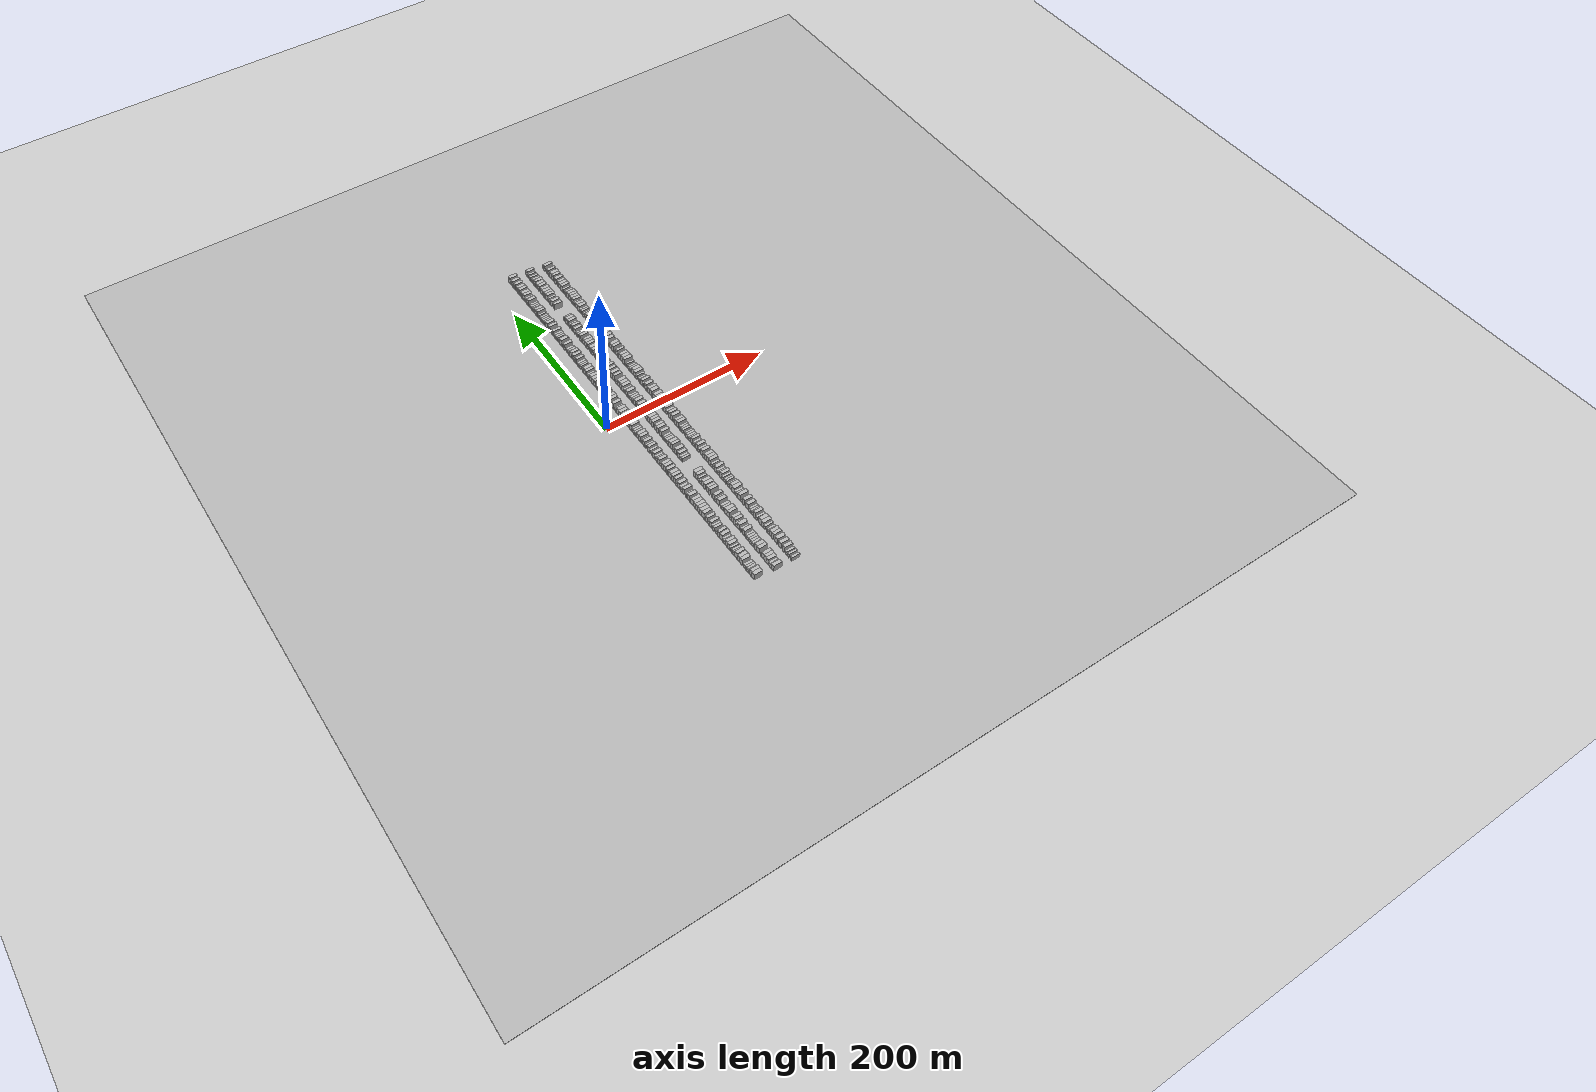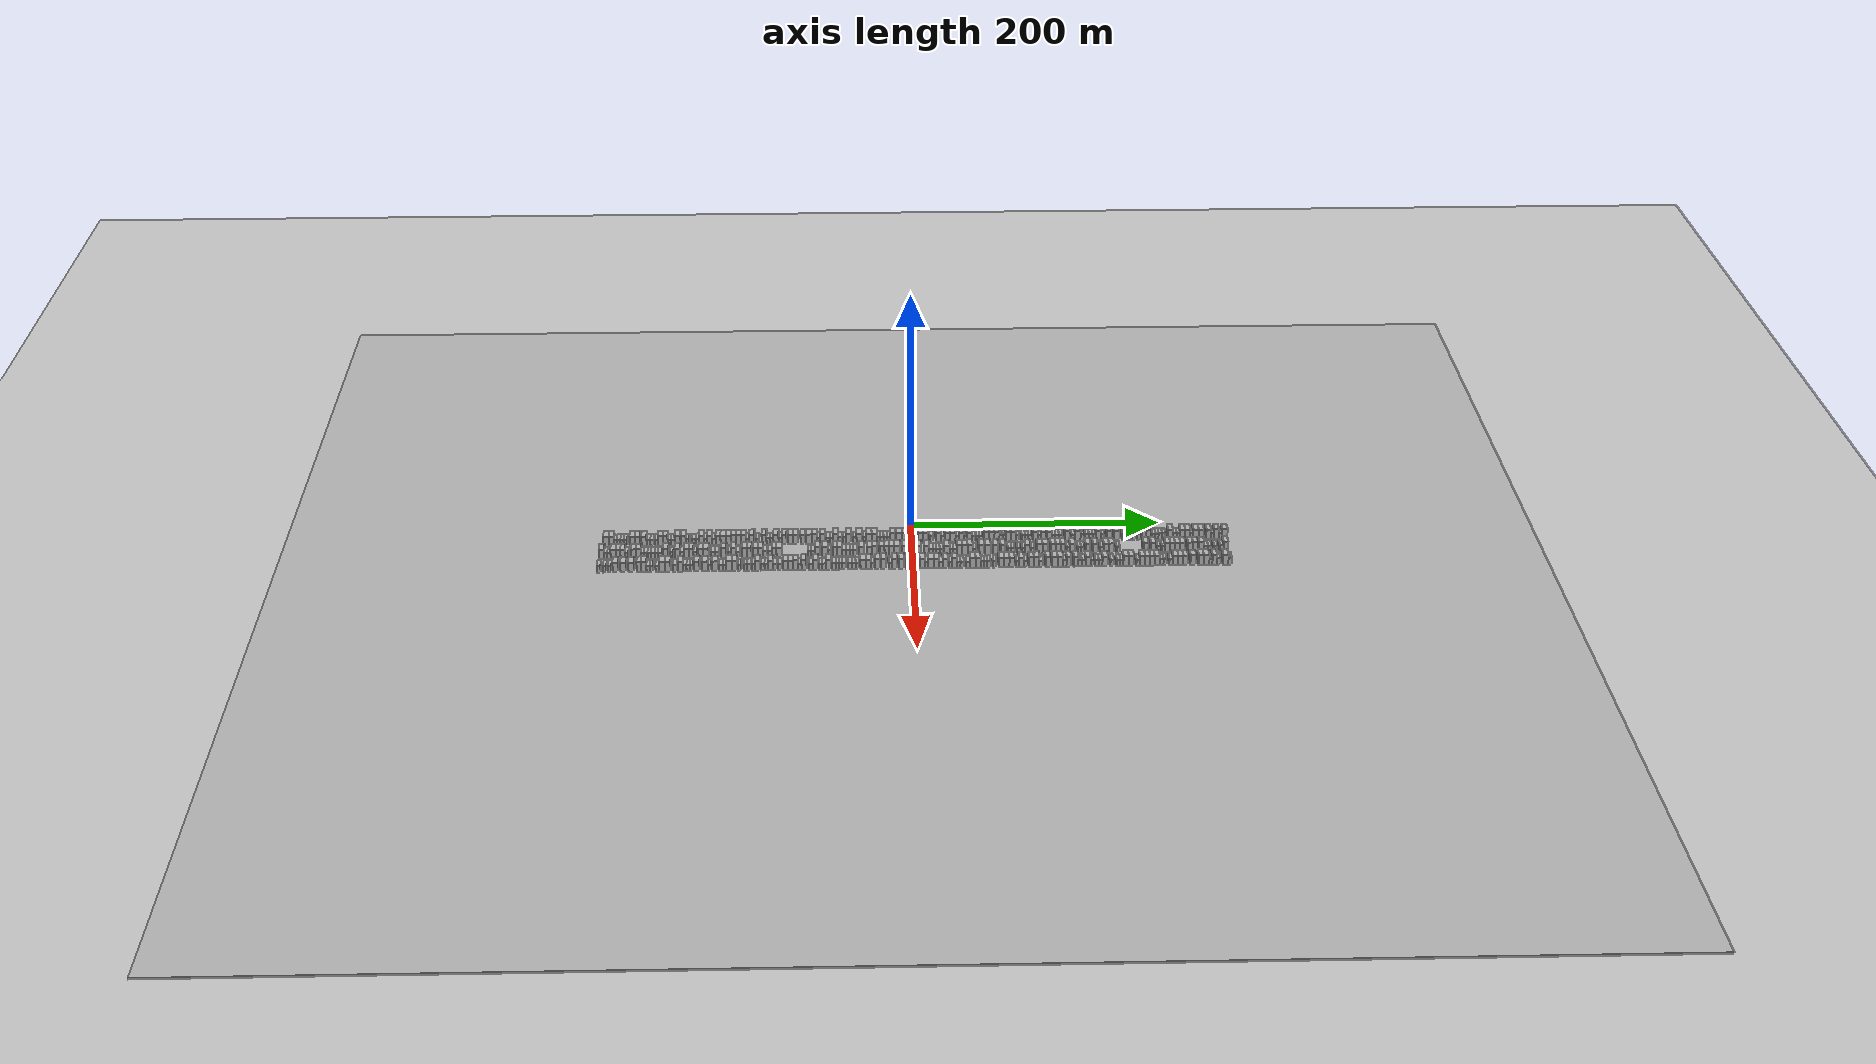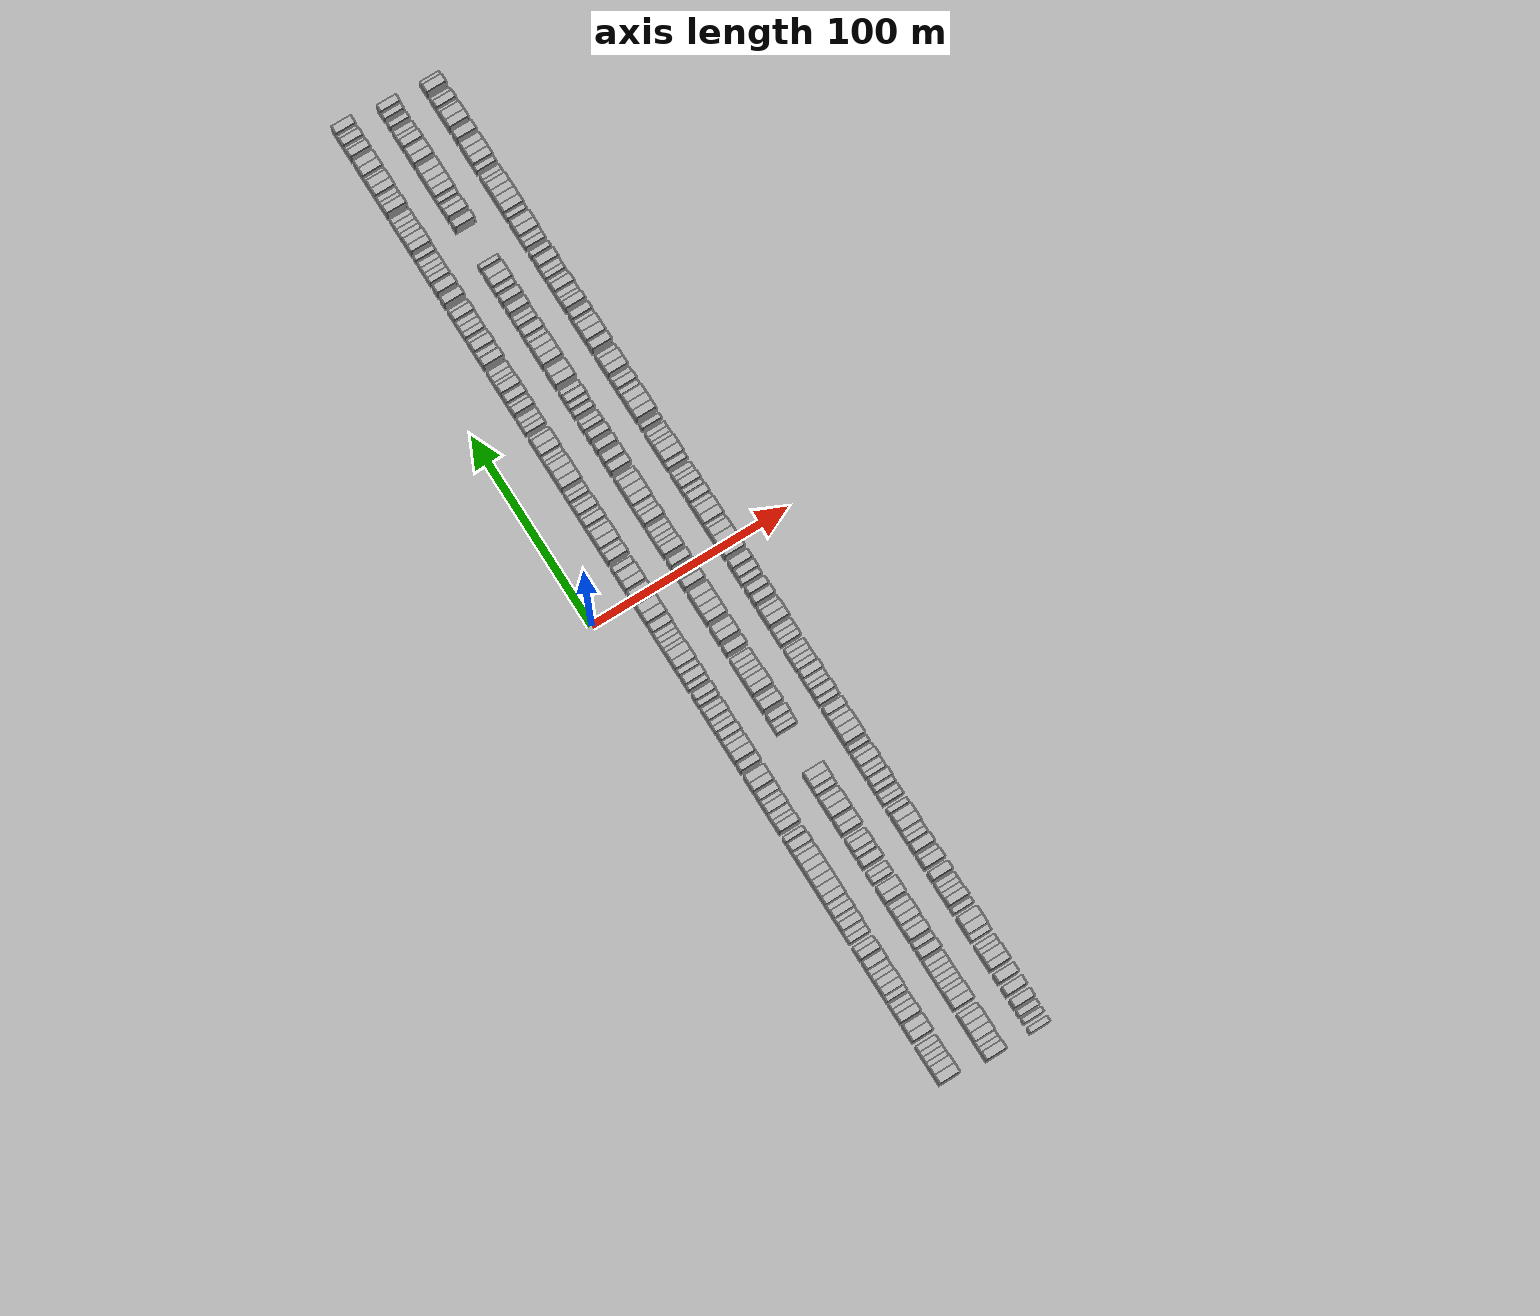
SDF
<?xml version="1.0" encoding="utf-8"?>

<sdf version="1.6">

   <world name="default">

      <gui fullscreen="0">

         <camera name="user_camera">

            <pose>-15 0 4.57585 0 0 0</pose>

            <view_controller>orbit</view_controller>

         </camera>

      </gui>

      <scene>

         <sky>

           <clouds>

             <speed>12</speed>

           </clouds>

         </sky>

         <ambient>0.4 0.4 0.4 1</ambient>

         <background>0.7 0.7 0.7 1</background>

         <shadows>1</shadows>

      </scene>

      <gravity>0 0 -9.8066</gravity>

      <magnetic_field>6e-06 2.3e-05 -4.2e-05</magnetic_field>

      <physics default="0" name="default_physics" type="ode">

         <ode>

            <solver>

               <type>quick</type>

               <iters>10</iters>

               <sor>1.0</sor>

               <use_dynamic_moi_rescaling>0</use_dynamic_moi_rescaling>

            </solver>

            <constraints>

               <cfm>0</cfm>

               <erp>0.2</erp>

               <contact_max_correcting_vel>100</contact_max_correcting_vel>

               <contact_surface_layer>0.001</contact_surface_layer>

            </constraints>

         </ode>

         <max_step_size>0.004</max_step_size>

         <real_time_factor>1</real_time_factor>

         <real_time_update_rate>250</real_time_update_rate>

      </physics>

      <light name="sun" type="directional">

         <cast_shadows>1</cast_shadows>

         <pose>0 0 10 0 0 0</pose>

         <diffuse>0.8 0.8 0.8 1</diffuse>

         <specular>0.2 0.2 0.2 1</specular>

         <attenuation>

            <range>1000</range>

            <constant>0.9</constant>

            <linear>0.01</linear>

            <quadratic>0.001</quadratic>

         </attenuation>

         <direction>-0.5 0.1 -0.9</direction>

      </light>

      <include>

         <name>ground_plane_1</name>

         <uri>model://HANNAS_ground_plane</uri>

         <pose>0 0 0  0 0 0</pose>

      </include>

      <include>

         <name>ground_plane_2</name>

         <uri>model://HANNAS_ground_plane</uri>

         <pose>100 0 0  0 0 0</pose>

      </include>

      <model name="building_1">

         <static>1</static>

         <pose frame="">25.0000 -243.7669 0 0.000000 0.000000 0.000000</pose>

         <link name="link">

            <pose frame="">0 0 4.50 0 0 0</pose>

            <collision name="collision">

               <geometry>

                  <box>

                     <size>10.0000 4.4663 9.0000</size>

                  </box>

               </geometry>

               <max_contacts>10</max_contacts>

               <surface>

                  <contact>

                     <ode/>

                  </contact>

                  <bounce/>

                  <friction>

                     <torsional>

                        <ode/>

                     </torsional>

                     <ode/>

                  </friction>

               </surface>

            </collision>

            <visual name="visual">

               <cast_shadows>0</cast_shadows>

               <geometry>

                  <box>

                     <size>10.0000 4.4663 9.0000</size>

                  </box>

               </geometry>

               <material>

                  <script>

                     <uri>model://HANNAS_wall/materials/scripts</uri>

                     <uri>model://HANNAS_wall/materials/textures</uri>

                     <name>vrc/HANNAS_wall</name>

                  </script>

               </material>

            </visual>

            <self_collide>0</self_collide>

            <enable_wind>0</enable_wind>

            <kinematic>0</kinematic>

         </link>

      </model>

      <model name="building_2">

         <static>1</static>

         <pose frame="">25.0000 -239.5930 0 0.000000 0.000000 0.000000</pose>

         <link name="link">

            <pose frame="">0 0 4.50 0 0 0</pose>

            <collision name="collision">

               <geometry>

                  <box>

                     <size>10.0000 3.8815 9.0000</size>

                  </box>

               </geometry>

               <max_contacts>10</max_contacts>

               <surface>

                  <contact>

                     <ode/>

                  </contact>

                  <bounce/>

                  <friction>

                     <torsional>

                        <ode/>

                     </torsional>

                     <ode/>

                  </friction>

               </surface>

            </collision>

            <visual name="visual">

               <cast_shadows>0</cast_shadows>

               <geometry>

                  <box>

                     <size>10.0000 3.8815 9.0000</size>

                  </box>

               </geometry>

               <material>

                  <script>

                     <uri>model://HANNAS_wall/materials/scripts</uri>

                     <uri>model://HANNAS_wall/materials/textures</uri>

                     <name>vrc/HANNAS_wall</name>

                  </script>

               </material>

            </visual>

            <self_collide>0</self_collide>

            <enable_wind>0</enable_wind>

            <kinematic>0</kinematic>

         </link>

      </model>

      <model name="building_3">

         <static>1</static>

         <pose frame="">25.0000 -236.3804 0 0.000000 0.000000 0.000000</pose>

         <link name="link">

            <pose frame="">0 0 3.00 0 0 0</pose>

            <collision name="collision">

               <geometry>

                  <box>

                     <size>10.0000 2.5437 6.0000</size>

                  </box>

               </geometry>

               <max_contacts>10</max_contacts>

               <surface>

                  <contact>

                     <ode/>

                  </contact>

                  <bounce/>

                  <friction>

                     <torsional>

                        <ode/>

                     </torsional>

                     <ode/>

                  </friction>

               </surface>

            </collision>

            <visual name="visual">

               <cast_shadows>0</cast_shadows>

               <geometry>

                  <box>

                     <size>10.0000 2.5437 6.0000</size>

                  </box>

               </geometry>

               <material>

                  <script>

                     <uri>model://HANNAS_wall/materials/scripts</uri>

                     <uri>model://HANNAS_wall/materials/textures</uri>

                     <name>vrc/HANNAS_wall</name>

                  </script>

               </material>

            </visual>

            <self_collide>0</self_collide>

            <enable_wind>0</enable_wind>

            <kinematic>0</kinematic>

         </link>

      </model>

      <model name="building_4">

         <static>1</static>

         <pose frame="">25.0000 -233.7619 0 0.000000 0.000000 0.000000</pose>

         <link name="link">

            <pose frame="">0 0 3.00 0 0 0</pose>

            <collision name="collision">

               <geometry>

                  <box>

                     <size>10.0000 2.6932 6.0000</size>

                  </box>

               </geometry>

               <max_contacts>10</max_contacts>

               <surface>

                  <contact>

                     <ode/>

                  </contact>

                  <bounce/>

                  <friction>

                     <torsional>

                        <ode/>

                     </torsional>

                     <ode/>

                  </friction>

               </surface>

            </collision>

            <visual name="visual">

               <cast_shadows>0</cast_shadows>

               <geometry>

                  <box>

                     <size>10.0000 2.6932 6.0000</size>

                  </box>

               </geometry>

               <material>

                  <script>

                     <uri>model://HANNAS_wall/materials/scripts</uri>

                     <uri>model://HANNAS_wall/materials/textures</uri>

                     <name>vrc/HANNAS_wall</name>

                  </script>

               </material>

            </visual>

            <self_collide>0</self_collide>

            <enable_wind>0</enable_wind>

            <kinematic>0</kinematic>

         </link>

      </model>

      <model name="building_5">

         <static>1</static>

         <pose frame="">25.0000 -231.1787 0 0.000000 0.000000 0.000000</pose>

         <link name="link">

            <pose frame="">0 0 3.00 0 0 0</pose>

            <collision name="collision">

               <geometry>

                  <box>

                     <size>10.0000 2.4733 6.0000</size>

                  </box>

               </geometry>

               <max_contacts>10</max_contacts>

               <surface>

                  <contact>

                     <ode/>

                  </contact>

                  <bounce/>

                  <friction>

                     <torsional>

                        <ode/>

                     </torsional>

                     <ode/>

                  </friction>

               </surface>

            </collision>

            <visual name="visual">

               <cast_shadows>0</cast_shadows>

               <geometry>

                  <box>

                     <size>10.0000 2.4733 6.0000</size>

                  </box>

               </geometry>

               <material>

                  <script>

                     <uri>model://HANNAS_wall/materials/scripts</uri>

                     <uri>model://HANNAS_wall/materials/textures</uri>

                     <name>vrc/HANNAS_wall</name>

                  </script>

               </material>

            </visual>

            <self_collide>0</self_collide>

            <enable_wind>0</enable_wind>

            <kinematic>0</kinematic>

         </link>

      </model>

      <model name="building_6">

         <static>1</static>

         <pose frame="">25.0000 -228.4949 0 0.000000 0.000000 0.000000</pose>

         <link name="link">

            <pose frame="">0 0 3.00 0 0 0</pose>

            <collision name="collision">

               <geometry>

                  <box>

                     <size>10.0000 2.8942 6.0000</size>

                  </box>

               </geometry>

               <max_contacts>10</max_contacts>

               <surface>

                  <contact>

                     <ode/>

                  </contact>

                  <bounce/>

                  <friction>

                     <torsional>

                        <ode/>

                     </torsional>

                     <ode/>

                  </friction>

               </surface>

            </collision>

            <visual name="visual">

               <cast_shadows>0</cast_shadows>

               <geometry>

                  <box>

                     <size>10.0000 2.8942 6.0000</size>

                  </box>

               </geometry>

               <material>

                  <script>

                     <uri>model://HANNAS_wall/materials/scripts</uri>

                     <uri>model://HANNAS_wall/materials/textures</uri>

                     <name>vrc/HANNAS_wall</name>

                  </script>

               </material>

            </visual>

            <self_collide>0</self_collide>

            <enable_wind>0</enable_wind>

            <kinematic>0</kinematic>

         </link>

      </model>

      <model name="building_7">

         <static>1</static>

         <pose frame="">25.0000 -222.9407 0 0.000000 0.000000 0.000000</pose>

         <link name="link">

            <pose frame="">0 0 4.50 0 0 0</pose>

            <collision name="collision">

               <geometry>

                  <box>

                     <size>10.0000 4.2143 9.0000</size>

                  </box>

               </geometry>

               <max_contacts>10</max_contacts>

               <surface>

                  <contact>

                     <ode/>

                  </contact>

                  <bounce/>

                  <friction>

                     <torsional>

                        <ode/>

                     </torsional>

                     <ode/>

                  </friction>

               </surface>

            </collision>

            <visual name="visual">

               <cast_shadows>0</cast_shadows>

               <geometry>

                  <box>

                     <size>10.0000 4.2143 9.0000</size>

                  </box>

               </geometry>

               <material>

                  <script>

                     <uri>model://HANNAS_wall/materials/scripts</uri>

                     <uri>model://HANNAS_wall/materials/textures</uri>

                     <name>vrc/HANNAS_wall</name>

                  </script>

               </material>

            </visual>

            <self_collide>0</self_collide>

            <enable_wind>0</enable_wind>

            <kinematic>0</kinematic>

         </link>

      </model>

      <model name="building_8">

         <static>1</static>

         <pose frame="">25.0000 -218.7890 0 0.000000 0.000000 0.000000</pose>

         <link name="link">

            <pose frame="">0 0 4.50 0 0 0</pose>

            <collision name="collision">

               <geometry>

                  <box>

                     <size>10.0000 4.0890 9.0000</size>

                  </box>

               </geometry>

               <max_contacts>10</max_contacts>

               <surface>

                  <contact>

                     <ode/>

                  </contact>

                  <bounce/>

                  <friction>

                     <torsional>

                        <ode/>

                     </torsional>

                     <ode/>

                  </friction>

               </surface>

            </collision>

            <visual name="visual">

               <cast_shadows>0</cast_shadows>

               <geometry>

                  <box>

                     <size>10.0000 4.0890 9.0000</size>

                  </box>

               </geometry>

               <material>

                  <script>

                     <uri>model://HANNAS_wall/materials/scripts</uri>

                     <uri>model://HANNAS_wall/materials/textures</uri>

                     <name>vrc/HANNAS_wall</name>

                  </script>

               </material>

            </visual>

            <self_collide>0</self_collide>

            <enable_wind>0</enable_wind>

            <kinematic>0</kinematic>

         </link>

      </model>

      <model name="building_9">

         <static>1</static>

         <pose frame="">25.0000 -213.6994 0 0.000000 0.000000 0.000000</pose>

         <link name="link">

            <pose frame="">0 0 4.50 0 0 0</pose>

            <collision name="collision">

               <geometry>

                  <box>

                     <size>10.0000 4.0903 9.0000</size>

                  </box>

               </geometry>

               <max_contacts>10</max_contacts>

               <surface>

                  <contact>

                     <ode/>

                  </contact>

                  <bounce/>

                  <friction>

                     <torsional>

                        <ode/>

                     </torsional>

                     <ode/>

                  </friction>

               </surface>

            </collision>

            <visual name="visual">

               <cast_shadows>0</cast_shadows>

               <geometry>

                  <box>

                     <size>10.0000 4.0903 9.0000</size>

                  </box>

               </geometry>

               <material>

                  <script>

                     <uri>model://HANNAS_wall/materials/scripts</uri>

                     <uri>model://HANNAS_wall/materials/textures</uri>

                     <name>vrc/HANNAS_wall</name>

                  </script>

               </material>

            </visual>

            <self_collide>0</self_collide>

            <enable_wind>0</enable_wind>

            <kinematic>0</kinematic>

         </link>

      </model>

      <model name="building_10">

         <static>1</static>

         <pose frame="">25.0000 -210.1707 0 0.000000 0.000000 0.000000</pose>

         <link name="link">

            <pose frame="">0 0 3.00 0 0 0</pose>

            <collision name="collision">

               <geometry>

                  <box>

                     <size>10.0000 2.9671 6.0000</size>

                  </box>

               </geometry>

               <max_contacts>10</max_contacts>

               <surface>

                  <contact>

                     <ode/>

                  </contact>

                  <bounce/>

                  <friction>

                     <torsional>

                        <ode/>

                     </torsional>

                     <ode/>

                  </friction>

               </surface>

            </collision>

            <visual name="visual">

               <cast_shadows>0</cast_shadows>

               <geometry>

                  <box>

                     <size>10.0000 2.9671 6.0000</size>

                  </box>

               </geometry>

               <material>

                  <script>

                     <uri>model://HANNAS_wall/materials/scripts</uri>

                     <uri>model://HANNAS_wall/materials/textures</uri>

                     <name>vrc/HANNAS_wall</name>

                  </script>

               </material>

            </visual>

            <self_collide>0</self_collide>

            <enable_wind>0</enable_wind>

            <kinematic>0</kinematic>

         </link>

      </model>

      <model name="building_11">

         <static>1</static>

         <pose frame="">25.0000 -207.3888 0 0.000000 0.000000 0.000000</pose>

         <link name="link">

            <pose frame="">0 0 3.00 0 0 0</pose>

            <collision name="collision">

               <geometry>

                  <box>

                     <size>10.0000 2.5969 6.0000</size>

                  </box>

               </geometry>

               <max_contacts>10</max_contacts>

               <surface>

                  <contact>

                     <ode/>

                  </contact>

                  <bounce/>

                  <friction>

                     <torsional>

                        <ode/>

                     </torsional>

                     <ode/>

                  </friction>

               </surface>

            </collision>

            <visual name="visual">

               <cast_shadows>0</cast_shadows>

               <geometry>

                  <box>

                     <size>10.0000 2.5969 6.0000</size>

                  </box>

               </geometry>

               <material>

                  <script>

                     <uri>model://HANNAS_wall/materials/scripts</uri>

                     <uri>model://HANNAS_wall/materials/textures</uri>

                     <name>vrc/HANNAS_wall</name>

                  </script>

               </material>

            </visual>

            <self_collide>0</self_collide>

            <enable_wind>0</enable_wind>

            <kinematic>0</kinematic>

         </link>

      </model>

      <model name="building_12">

         <static>1</static>

         <pose frame="">25.0000 -203.7824 0 0.000000 0.000000 0.000000</pose>

         <link name="link">

            <pose frame="">0 0 3.00 0 0 0</pose>

            <collision name="collision">

               <geometry>

                  <box>

                     <size>10.0000 2.6159 6.0000</size>

                  </box>

               </geometry>

               <max_contacts>10</max_contacts>

               <surface>

                  <contact>

                     <ode/>

                  </contact>

                  <bounce/>

                  <friction>

                     <torsional>

                        <ode/>

                     </torsional>

                     <ode/>

                  </friction>

               </surface>

            </collision>

            <visual name="visual">

               <cast_shadows>0</cast_shadows>

               <geometry>

                  <box>

                     <size>10.0000 2.6159 6.0000</size>

                  </box>

               </geometry>

               <material>

                  <script>

                     <uri>model://HANNAS_wall/materials/scripts</uri>

                     <uri>model://HANNAS_wall/materials/textures</uri>

                     <name>vrc/HANNAS_wall</name>

                  </script>

               </material>

            </visual>

            <self_collide>0</self_collide>

            <enable_wind>0</enable_wind>

            <kinematic>0</kinematic>

         </link>

      </model>

      <model name="building_13">

         <static>1</static>

         <pose frame="">25.0000 -200.5745 0 0.000000 0.000000 0.000000</pose>

         <link name="link">

            <pose frame="">0 0 4.50 0 0 0</pose>

            <collision name="collision">

               <geometry>

                  <box>

                     <size>10.0000 3.7997 9.0000</size>

                  </box>

               </geometry>

               <max_contacts>10</max_contacts>

               <surface>

                  <contact>

                     <ode/>

                  </contact>

                  <bounce/>

                  <friction>

                     <torsional>

                        <ode/>

                     </torsional>

                     <ode/>

                  </friction>

               </surface>

            </collision>

            <visual name="visual">

               <cast_shadows>0</cast_shadows>

               <geometry>

                  <box>

                     <size>10.0000 3.7997 9.0000</size>

                  </box>

               </geometry>

               <material>

                  <script>

                     <uri>model://HANNAS_wall/materials/scripts</uri>

                     <uri>model://HANNAS_wall/materials/textures</uri>

                     <name>vrc/HANNAS_wall</name>

                  </script>

               </material>

            </visual>

            <self_collide>0</self_collide>

            <enable_wind>0</enable_wind>

            <kinematic>0</kinematic>

         </link>

      </model>

      <model name="building_14">

         <static>1</static>

         <pose frame="">25.0000 -196.8106 0 0.000000 0.000000 0.000000</pose>

         <link name="link">

            <pose frame="">0 0 4.50 0 0 0</pose>

            <collision name="collision">

               <geometry>

                  <box>

                     <size>10.0000 3.7281 9.0000</size>

                  </box>

               </geometry>

               <max_contacts>10</max_contacts>

               <surface>

                  <contact>

                     <ode/>

                  </contact>

                  <bounce/>

                  <friction>

                     <torsional>

                        <ode/>

                     </torsional>

                     <ode/>

                  </friction>

               </surface>

            </collision>

            <visual name="visual">

               <cast_shadows>0</cast_shadows>

               <geometry>

                  <box>

                     <size>10.0000 3.7281 9.0000</size>

                  </box>

               </geometry>

               <material>

                  <script>

                     <uri>model://HANNAS_wall/materials/scripts</uri>

                     <uri>model://HANNAS_wall/materials/textures</uri>

                     <name>vrc/HANNAS_wall</name>

                  </script>

               </material>

            </visual>

            <self_collide>0</self_collide>

            <enable_wind>0</enable_wind>

            <kinematic>0</kinematic>

         </link>

      </model>

      <model name="building_15">

         <static>1</static>

         <pose frame="">25.0000 -193.5161 0 0.000000 0.000000 0.000000</pose>

         <link name="link">

            <pose frame="">0 0 3.00 0 0 0</pose>

            <collision name="collision">

               <geometry>

                  <box>

                     <size>10.0000 2.8609 6.0000</size>

                  </box>

               </geometry>

               <max_contacts>10</max_contacts>

               <surface>

                  <contact>

                     <ode/>

                  </contact>

                  <bounce/>

                  <friction>

                     <torsional>

                        <ode/>

                     </torsional>

                     <ode/>

                  </friction>

               </surface>

            </collision>

            <visual name="visual">

               <cast_shadows>0</cast_shadows>

               <geometry>

                  <box>

                     <size>10.0000 2.8609 6.0000</size>

                  </box>

               </geometry>

               <material>

                  <script>

                     <uri>model://HANNAS_wall/materials/scripts</uri>

                     <uri>model://HANNAS_wall/materials/textures</uri>

                     <name>vrc/HANNAS_wall</name>

                  </script>

               </material>

            </visual>

            <self_collide>0</self_collide>

            <enable_wind>0</enable_wind>

            <kinematic>0</kinematic>

         </link>

      </model>

      <model name="building_16">

         <static>1</static>

         <pose frame="">25.0000 -190.7070 0 0.000000 0.000000 0.000000</pose>

         <link name="link">

            <pose frame="">0 0 3.00 0 0 0</pose>

            <collision name="collision">

               <geometry>

                  <box>

                     <size>10.0000 2.7572 6.0000</size>

                  </box>

               </geometry>

               <max_contacts>10</max_contacts>

               <surface>

                  <contact>

                     <ode/>

                  </contact>

                  <bounce/>

                  <friction>

                     <torsional>

                        <ode/>

                     </torsional>

                     <ode/>

                  </friction>

               </surface>

            </collision>

            <visual name="visual">

               <cast_shadows>0</cast_shadows>

               <geometry>

                  <box>

                     <size>10.0000 2.7572 6.0000</size>

                  </box>

               </geometry>

               <material>

                  <script>

                     <uri>model://HANNAS_wall/materials/scripts</uri>

                     <uri>model://HANNAS_wall/materials/textures</uri>

                     <name>vrc/HANNAS_wall</name>

                  </script>

               </material>

            </visual>

            <self_collide>0</self_collide>

            <enable_wind>0</enable_wind>

            <kinematic>0</kinematic>

         </link>

      </model>

      <model name="building_17">

         <static>1</static>

         <pose frame="">25.0000 -187.2753 0 0.000000 0.000000 0.000000</pose>

         <link name="link">

            <pose frame="">0 0 4.50 0 0 0</pose>

            <collision name="collision">

               <geometry>

                  <box>

                     <size>10.0000 4.1063 9.0000</size>

                  </box>

               </geometry>

               <max_contacts>10</max_contacts>

               <surface>

                  <contact>

                     <ode/>

                  </contact>

                  <bounce/>

                  <friction>

                     <torsional>

                        <ode/>

                     </torsional>

                     <ode/>

                  </friction>

               </surface>

            </collision>

            <visual name="visual">

               <cast_shadows>0</cast_shadows>

               <geometry>

                  <box>

                     <size>10.0000 4.1063 9.0000</size>

                  </box>

               </geometry>

               <material>

                  <script>

                     <uri>model://HANNAS_wall/materials/scripts</uri>

                     <uri>model://HANNAS_wall/materials/textures</uri>

                     <name>vrc/HANNAS_wall</name>

                  </script>

               </material>

            </visual>

            <self_collide>0</self_collide>

            <enable_wind>0</enable_wind>

            <kinematic>0</kinematic>

         </link>

      </model>

      <model name="building_18">

         <static>1</static>

         <pose frame="">25.0000 -182.3998 0 0.000000 0.000000 0.000000</pose>

         <link name="link">

            <pose frame="">0 0 4.50 0 0 0</pose>

            <collision name="collision">

               <geometry>

                  <box>

                     <size>10.0000 3.6447 9.0000</size>

                  </box>

               </geometry>

               <max_contacts>10</max_contacts>

               <surface>

                  <contact>

                     <ode/>

                  </contact>

                  <bounce/>

                  <friction>

                     <torsional>

                        <ode/>

                     </torsional>

                     <ode/>

                  </friction>

               </surface>

            </collision>

            <visual name="visual">

               <cast_shadows>0</cast_shadows>

               <geometry>

                  <box>

                     <size>10.0000 3.6447 9.0000</size>

                  </box>

               </geometry>

               <material>

                  <script>

                     <uri>model://HANNAS_wall/materials/scripts</uri>

                     <uri>model://HANNAS_wall/materials/textures</uri>

                     <name>vrc/HANNAS_wall</name>

                  </script>

               </material>

            </visual>

            <self_collide>0</self_collide>

            <enable_wind>0</enable_wind>

            <kinematic>0</kinematic>

         </link>

      </model>

      <model name="building_19">

         <static>1</static>

         <pose frame="">25.0000 -179.1549 0 0.000000 0.000000 0.000000</pose>

         <link name="link">

            <pose frame="">0 0 3.00 0 0 0</pose>

            <collision name="collision">

               <geometry>

                  <box>

                     <size>10.0000 2.8449 6.0000</size>

                  </box>

               </geometry>

               <max_contacts>10</max_contacts>

               <surface>

                  <contact>

                     <ode/>

                  </contact>

                  <bounce/>

                  <friction>

                     <torsional>

                        <ode/>

                     </torsional>

                     <ode/>

                  </friction>

               </surface>

            </collision>

            <visual name="visual">

               <cast_shadows>0</cast_shadows>

               <geometry>

                  <box>

                     <size>10.0000 2.8449 6.0000</size>

                  </box>

               </geometry>

               <material>

                  <script>

                     <uri>model://HANNAS_wall/materials/scripts</uri>

                     <uri>model://HANNAS_wall/materials/textures</uri>

                     <name>vrc/HANNAS_wall</name>

                  </script>

               </material>

            </visual>

            <self_collide>0</self_collide>

            <enable_wind>0</enable_wind>

            <kinematic>0</kinematic>

         </link>

      </model>

      <model name="building_20">

         <static>1</static>

         <pose frame="">25.0000 -174.2485 0 0.000000 0.000000 0.000000</pose>

         <link name="link">

            <pose frame="">0 0 3.00 0 0 0</pose>

            <collision name="collision">

               <geometry>

                  <box>

                     <size>10.0000 2.9680 6.0000</size>

                  </box>

               </geometry>

               <max_contacts>10</max_contacts>

               <surface>

                  <contact>

                     <ode/>

                  </contact>

                  <bounce/>

                  <friction>

                     <torsional>

                        <ode/>

                     </torsional>

                     <ode/>

                  </friction>

               </surface>

            </collision>

            <visual name="visual">

               <cast_shadows>0</cast_shadows>

               <geometry>

                  <box>

                     <size>10.0000 2.9680 6.0000</size>

                  </box>

               </geometry>

               <material>

                  <script>

                     <uri>model://HANNAS_wall/materials/scripts</uri>

                     <uri>model://HANNAS_wall/materials/textures</uri>

                     <name>vrc/HANNAS_wall</name>

                  </script>

               </material>

            </visual>

            <self_collide>0</self_collide>

            <enable_wind>0</enable_wind>

            <kinematic>0</kinematic>

         </link>

      </model>

      <model name="building_21">

         <static>1</static>

         <pose frame="">25.0000 -171.3698 0 0.000000 0.000000 0.000000</pose>

         <link name="link">

            <pose frame="">0 0 3.00 0 0 0</pose>

            <collision name="collision">

               <geometry>

                  <box>

                     <size>10.0000 2.7893 6.0000</size>

                  </box>

               </geometry>

               <max_contacts>10</max_contacts>

               <surface>

                  <contact>

                     <ode/>

                  </contact>

                  <bounce/>

                  <friction>

                     <torsional>

                        <ode/>

                     </torsional>

                     <ode/>

                  </friction>

               </surface>

            </collision>

            <visual name="visual">

               <cast_shadows>0</cast_shadows>

               <geometry>

                  <box>

                     <size>10.0000 2.7893 6.0000</size>

                  </box>

               </geometry>

               <material>

                  <script>

                     <uri>model://HANNAS_wall/materials/scripts</uri>

                     <uri>model://HANNAS_wall/materials/textures</uri>

                     <name>vrc/HANNAS_wall</name>

                  </script>

               </material>

            </visual>

            <self_collide>0</self_collide>

            <enable_wind>0</enable_wind>

            <kinematic>0</kinematic>

         </link>

      </model>

      <model name="building_22">

         <static>1</static>

         <pose frame="">25.0000 -167.9981 0 0.000000 0.000000 0.000000</pose>

         <link name="link">

            <pose frame="">0 0 4.50 0 0 0</pose>

            <collision name="collision">

               <geometry>

                  <box>

                     <size>10.0000 3.9542 9.0000</size>

                  </box>

               </geometry>

               <max_contacts>10</max_contacts>

               <surface>

                  <contact>

                     <ode/>

                  </contact>

                  <bounce/>

                  <friction>

                     <torsional>

                        <ode/>

                     </torsional>

                     <ode/>

                  </friction>

               </surface>

            </collision>

            <visual name="visual">

               <cast_shadows>0</cast_shadows>

               <geometry>

                  <box>

                     <size>10.0000 3.9542 9.0000</size>

                  </box>

               </geometry>

               <material>

                  <script>

                     <uri>model://HANNAS_wall/materials/scripts</uri>

                     <uri>model://HANNAS_wall/materials/textures</uri>

                     <name>vrc/HANNAS_wall</name>

                  </script>

               </material>

            </visual>

            <self_collide>0</self_collide>

            <enable_wind>0</enable_wind>

            <kinematic>0</kinematic>

         </link>

      </model>

      <model name="building_23">

         <static>1</static>

         <pose frame="">25.0000 -164.7621 0 0.000000 0.000000 0.000000</pose>

         <link name="link">

            <pose frame="">0 0 3.00 0 0 0</pose>

            <collision name="collision">

               <geometry>

                  <box>

                     <size>10.0000 2.5177 6.0000</size>

                  </box>

               </geometry>

               <max_contacts>10</max_contacts>

               <surface>

                  <contact>

                     <ode/>

                  </contact>

                  <bounce/>

                  <friction>

                     <torsional>

                        <ode/>

                     </torsional>

                     <ode/>

                  </friction>

               </surface>

            </collision>

            <visual name="visual">

               <cast_shadows>0</cast_shadows>

               <geometry>

                  <box>

                     <size>10.0000 2.5177 6.0000</size>

                  </box>

               </geometry>

               <material>

                  <script>

                     <uri>model://HANNAS_wall/materials/scripts</uri>

                     <uri>model://HANNAS_wall/materials/textures</uri>

                     <name>vrc/HANNAS_wall</name>

                  </script>

               </material>

            </visual>

            <self_collide>0</self_collide>

            <enable_wind>0</enable_wind>

            <kinematic>0</kinematic>

         </link>

      </model>

      <model name="building_24">

         <static>1</static>

         <pose frame="">25.0000 -161.6389 0 0.000000 0.000000 0.000000</pose>

         <link name="link">

            <pose frame="">0 0 4.50 0 0 0</pose>

            <collision name="collision">

               <geometry>

                  <box>

                     <size>10.0000 3.7288 9.0000</size>

                  </box>

               </geometry>

               <max_contacts>10</max_contacts>

               <surface>

                  <contact>

                     <ode/>

                  </contact>

                  <bounce/>

                  <friction>

                     <torsional>

                        <ode/>

                     </torsional>

                     <ode/>

                  </friction>

               </surface>

            </collision>

            <visual name="visual">

               <cast_shadows>0</cast_shadows>

               <geometry>

                  <box>

                     <size>10.0000 3.7288 9.0000</size>

                  </box>

               </geometry>

               <material>

                  <script>

                     <uri>model://HANNAS_wall/materials/scripts</uri>

                     <uri>model://HANNAS_wall/materials/textures</uri>

                     <name>vrc/HANNAS_wall</name>

                  </script>

               </material>

            </visual>

            <self_collide>0</self_collide>

            <enable_wind>0</enable_wind>

            <kinematic>0</kinematic>

         </link>

      </model>

      <model name="building_25">

         <static>1</static>

         <pose frame="">25.0000 -158.2759 0 0.000000 0.000000 0.000000</pose>

         <link name="link">

            <pose frame="">0 0 3.00 0 0 0</pose>

            <collision name="collision">

               <geometry>

                  <box>

                     <size>10.0000 2.9971 6.0000</size>

                  </box>

               </geometry>

               <max_contacts>10</max_contacts>

               <surface>

                  <contact>

                     <ode/>

                  </contact>

                  <bounce/>

                  <friction>

                     <torsional>

                        <ode/>

                     </torsional>

                     <ode/>

                  </friction>

               </surface>

            </collision>

            <visual name="visual">

               <cast_shadows>0</cast_shadows>

               <geometry>

                  <box>

                     <size>10.0000 2.9971 6.0000</size>

                  </box>

               </geometry>

               <material>

                  <script>

                     <uri>model://HANNAS_wall/materials/scripts</uri>

                     <uri>model://HANNAS_wall/materials/textures</uri>

                     <name>vrc/HANNAS_wall</name>

                  </script>

               </material>

            </visual>

            <self_collide>0</self_collide>

            <enable_wind>0</enable_wind>

            <kinematic>0</kinematic>

         </link>

      </model>

      <model name="building_26">

         <static>1</static>

         <pose frame="">25.0000 -154.8387 0 0.000000 0.000000 0.000000</pose>

         <link name="link">

            <pose frame="">0 0 4.50 0 0 0</pose>

            <collision name="collision">

               <geometry>

                  <box>

                     <size>10.0000 3.8773 9.0000</size>

                  </box>

               </geometry>

               <max_contacts>10</max_contacts>

               <surface>

                  <contact>

                     <ode/>

                  </contact>

                  <bounce/>

                  <friction>

                     <torsional>

                        <ode/>

                     </torsional>

                     <ode/>

                  </friction>

               </surface>

            </collision>

            <visual name="visual">

               <cast_shadows>0</cast_shadows>

               <geometry>

                  <box>

                     <size>10.0000 3.8773 9.0000</size>

                  </box>

               </geometry>

               <material>

                  <script>

                     <uri>model://HANNAS_wall/materials/scripts</uri>

                     <uri>model://HANNAS_wall/materials/textures</uri>

                     <name>vrc/HANNAS_wall</name>

                  </script>

               </material>

            </visual>

            <self_collide>0</self_collide>

            <enable_wind>0</enable_wind>

            <kinematic>0</kinematic>

         </link>

      </model>

      <model name="building_27">

         <static>1</static>

         <pose frame="">25.0000 -150.6624 0 0.000000 0.000000 0.000000</pose>

         <link name="link">

            <pose frame="">0 0 4.50 0 0 0</pose>

            <collision name="collision">

               <geometry>

                  <box>

                     <size>10.0000 4.4754 9.0000</size>

                  </box>

               </geometry>

               <max_contacts>10</max_contacts>

               <surface>

                  <contact>

                     <ode/>

                  </contact>

                  <bounce/>

                  <friction>

                     <torsional>

                        <ode/>

                     </torsional>

                     <ode/>

                  </friction>

               </surface>

            </collision>

            <visual name="visual">

               <cast_shadows>0</cast_shadows>

               <geometry>

                  <box>

                     <size>10.0000 4.4754 9.0000</size>

                  </box>

               </geometry>

               <material>

                  <script>

                     <uri>model://HANNAS_wall/materials/scripts</uri>

                     <uri>model://HANNAS_wall/materials/textures</uri>

                     <name>vrc/HANNAS_wall</name>

                  </script>

               </material>

            </visual>

            <self_collide>0</self_collide>

            <enable_wind>0</enable_wind>

            <kinematic>0</kinematic>

         </link>

      </model>

      <model name="building_28">

         <static>1</static>

         <pose frame="">25.0000 -146.6111 0 0.000000 0.000000 0.000000</pose>

         <link name="link">

            <pose frame="">0 0 4.50 0 0 0</pose>

            <collision name="collision">

               <geometry>

                  <box>

                     <size>10.0000 3.6270 9.0000</size>

                  </box>

               </geometry>

               <max_contacts>10</max_contacts>

               <surface>

                  <contact>

                     <ode/>

                  </contact>

                  <bounce/>

                  <friction>

                     <torsional>

                        <ode/>

                     </torsional>

                     <ode/>

                  </friction>

               </surface>

            </collision>

            <visual name="visual">

               <cast_shadows>0</cast_shadows>

               <geometry>

                  <box>

                     <size>10.0000 3.6270 9.0000</size>

                  </box>

               </geometry>

               <material>

                  <script>

                     <uri>model://HANNAS_wall/materials/scripts</uri>

                     <uri>model://HANNAS_wall/materials/textures</uri>

                     <name>vrc/HANNAS_wall</name>

                  </script>

               </material>

            </visual>

            <self_collide>0</self_collide>

            <enable_wind>0</enable_wind>

            <kinematic>0</kinematic>

         </link>

      </model>

      <model name="building_29">

         <static>1</static>

         <pose frame="">25.0000 -142.7495 0 0.000000 0.000000 0.000000</pose>

         <link name="link">

            <pose frame="">0 0 4.50 0 0 0</pose>

            <collision name="collision">

               <geometry>

                  <box>

                     <size>10.0000 4.0963 9.0000</size>

                  </box>

               </geometry>

               <max_contacts>10</max_contacts>

               <surface>

                  <contact>

                     <ode/>

                  </contact>

                  <bounce/>

                  <friction>

                     <torsional>

                        <ode/>

                     </torsional>

                     <ode/>

                  </friction>

               </surface>

            </collision>

            <visual name="visual">

               <cast_shadows>0</cast_shadows>

               <geometry>

                  <box>

                     <size>10.0000 4.0963 9.0000</size>

                  </box>

               </geometry>

               <material>

                  <script>

                     <uri>model://HANNAS_wall/materials/scripts</uri>

                     <uri>model://HANNAS_wall/materials/textures</uri>

                     <name>vrc/HANNAS_wall</name>

                  </script>

               </material>

            </visual>

            <self_collide>0</self_collide>

            <enable_wind>0</enable_wind>

            <kinematic>0</kinematic>

         </link>

      </model>

      <model name="building_30">

         <static>1</static>

         <pose frame="">25.0000 -138.6701 0 0.000000 0.000000 0.000000</pose>

         <link name="link">

            <pose frame="">0 0 4.50 0 0 0</pose>

            <collision name="collision">

               <geometry>

                  <box>

                     <size>10.0000 4.0625 9.0000</size>

                  </box>

               </geometry>

               <max_contacts>10</max_contacts>

               <surface>

                  <contact>

                     <ode/>

                  </contact>

                  <bounce/>

                  <friction>

                     <torsional>

                        <ode/>

                     </torsional>

                     <ode/>

                  </friction>

               </surface>

            </collision>

            <visual name="visual">

               <cast_shadows>0</cast_shadows>

               <geometry>

                  <box>

                     <size>10.0000 4.0625 9.0000</size>

                  </box>

               </geometry>

               <material>

                  <script>

                     <uri>model://HANNAS_wall/materials/scripts</uri>

                     <uri>model://HANNAS_wall/materials/textures</uri>

                     <name>vrc/HANNAS_wall</name>

                  </script>

               </material>

            </visual>

            <self_collide>0</self_collide>

            <enable_wind>0</enable_wind>

            <kinematic>0</kinematic>

         </link>

      </model>

      <model name="building_31">

         <static>1</static>

         <pose frame="">25.0000 -134.6421 0 0.000000 0.000000 0.000000</pose>

         <link name="link">

            <pose frame="">0 0 4.50 0 0 0</pose>

            <collision name="collision">

               <geometry>

                  <box>

                     <size>10.0000 3.9935 9.0000</size>

                  </box>

               </geometry>

               <max_contacts>10</max_contacts>

               <surface>

                  <contact>

                     <ode/>

                  </contact>

                  <bounce/>

                  <friction>

                     <torsional>

                        <ode/>

                     </torsional>

                     <ode/>

                  </friction>

               </surface>

            </collision>

            <visual name="visual">

               <cast_shadows>0</cast_shadows>

               <geometry>

                  <box>

                     <size>10.0000 3.9935 9.0000</size>

                  </box>

               </geometry>

               <material>

                  <script>

                     <uri>model://HANNAS_wall/materials/scripts</uri>

                     <uri>model://HANNAS_wall/materials/textures</uri>

                     <name>vrc/HANNAS_wall</name>

                  </script>

               </material>

            </visual>

            <self_collide>0</self_collide>

            <enable_wind>0</enable_wind>

            <kinematic>0</kinematic>

         </link>

      </model>

      <model name="building_32">

         <static>1</static>

         <pose frame="">25.0000 -131.3513 0 0.000000 0.000000 0.000000</pose>

         <link name="link">

            <pose frame="">0 0 3.00 0 0 0</pose>

            <collision name="collision">

               <geometry>

                  <box>

                     <size>10.0000 2.5881 6.0000</size>

                  </box>

               </geometry>

               <max_contacts>10</max_contacts>

               <surface>

                  <contact>

                     <ode/>

                  </contact>

                  <bounce/>

                  <friction>

                     <torsional>

                        <ode/>

                     </torsional>

                     <ode/>

                  </friction>

               </surface>

            </collision>

            <visual name="visual">

               <cast_shadows>0</cast_shadows>

               <geometry>

                  <box>

                     <size>10.0000 2.5881 6.0000</size>

                  </box>

               </geometry>

               <material>

                  <script>

                     <uri>model://HANNAS_wall/materials/scripts</uri>

                     <uri>model://HANNAS_wall/materials/textures</uri>

                     <name>vrc/HANNAS_wall</name>

                  </script>

               </material>

            </visual>

            <self_collide>0</self_collide>

            <enable_wind>0</enable_wind>

            <kinematic>0</kinematic>

         </link>

      </model>

      <model name="building_33">

         <static>1</static>

         <pose frame="">25.0000 -127.9777 0 0.000000 0.000000 0.000000</pose>

         <link name="link">

            <pose frame="">0 0 4.50 0 0 0</pose>

            <collision name="collision">

               <geometry>

                  <box>

                     <size>10.0000 4.1589 9.0000</size>

                  </box>

               </geometry>

               <max_contacts>10</max_contacts>

               <surface>

                  <contact>

                     <ode/>

                  </contact>

                  <bounce/>

                  <friction>

                     <torsional>

                        <ode/>

                     </torsional>

                     <ode/>

                  </friction>

               </surface>

            </collision>

            <visual name="visual">

               <cast_shadows>0</cast_shadows>

               <geometry>

                  <box>

                     <size>10.0000 4.1589 9.0000</size>

                  </box>

               </geometry>

               <material>

                  <script>

                     <uri>model://HANNAS_wall/materials/scripts</uri>

                     <uri>model://HANNAS_wall/materials/textures</uri>

                     <name>vrc/HANNAS_wall</name>

                  </script>

               </material>

            </visual>

            <self_collide>0</self_collide>

            <enable_wind>0</enable_wind>

            <kinematic>0</kinematic>

         </link>

      </model>

      <model name="building_34">

         <static>1</static>

         <pose frame="">25.0000 -123.5564 0 0.000000 0.000000 0.000000</pose>

         <link name="link">

            <pose frame="">0 0 3.00 0 0 0</pose>

            <collision name="collision">

               <geometry>

                  <box>

                     <size>10.0000 2.6837 6.0000</size>

                  </box>

               </geometry>

               <max_contacts>10</max_contacts>

               <surface>

                  <contact>

                     <ode/>

                  </contact>

                  <bounce/>

                  <friction>

                     <torsional>

                        <ode/>

                     </torsional>

                     <ode/>

                  </friction>

               </surface>

            </collision>

            <visual name="visual">

               <cast_shadows>0</cast_shadows>

               <geometry>

                  <box>

                     <size>10.0000 2.6837 6.0000</size>

                  </box>

               </geometry>

               <material>

                  <script>

                     <uri>model://HANNAS_wall/materials/scripts</uri>

                     <uri>model://HANNAS_wall/materials/textures</uri>

                     <name>vrc/HANNAS_wall</name>

                  </script>

               </material>

            </visual>

            <self_collide>0</self_collide>

            <enable_wind>0</enable_wind>

            <kinematic>0</kinematic>

         </link>

      </model>

      <model name="building_35">

         <static>1</static>

         <pose frame="">25.0000 -118.2738 0 0.000000 0.000000 0.000000</pose>

         <link name="link">

            <pose frame="">0 0 4.50 0 0 0</pose>

            <collision name="collision">

               <geometry>

                  <box>

                     <size>10.0000 3.8815 9.0000</size>

                  </box>

               </geometry>

               <max_contacts>10</max_contacts>

               <surface>

                  <contact>

                     <ode/>

                  </contact>

                  <bounce/>

                  <friction>

                     <torsional>

                        <ode/>

                     </torsional>

                     <ode/>

                  </friction>

               </surface>

            </collision>

            <visual name="visual">

               <cast_shadows>0</cast_shadows>

               <geometry>

                  <box>

                     <size>10.0000 3.8815 9.0000</size>

                  </box>

               </geometry>

               <material>

                  <script>

                     <uri>model://HANNAS_wall/materials/scripts</uri>

                     <uri>model://HANNAS_wall/materials/textures</uri>

                     <name>vrc/HANNAS_wall</name>

                  </script>

               </material>

            </visual>

            <self_collide>0</self_collide>

            <enable_wind>0</enable_wind>

            <kinematic>0</kinematic>

         </link>

      </model>

      <model name="building_36">

         <static>1</static>

         <pose frame="">25.0000 -115.0420 0 0.000000 0.000000 0.000000</pose>

         <link name="link">

            <pose frame="">0 0 3.00 0 0 0</pose>

            <collision name="collision">

               <geometry>

                  <box>

                     <size>10.0000 2.5822 6.0000</size>

                  </box>

               </geometry>

               <max_contacts>10</max_contacts>

               <surface>

                  <contact>

                     <ode/>

                  </contact>

                  <bounce/>

                  <friction>

                     <torsional>

                        <ode/>

                     </torsional>

                     <ode/>

                  </friction>

               </surface>

            </collision>

            <visual name="visual">

               <cast_shadows>0</cast_shadows>

               <geometry>

                  <box>

                     <size>10.0000 2.5822 6.0000</size>

                  </box>

               </geometry>

               <material>

                  <script>

                     <uri>model://HANNAS_wall/materials/scripts</uri>

                     <uri>model://HANNAS_wall/materials/textures</uri>

                     <name>vrc/HANNAS_wall</name>

                  </script>

               </material>

            </visual>

            <self_collide>0</self_collide>

            <enable_wind>0</enable_wind>

            <kinematic>0</kinematic>

         </link>

      </model>

      <model name="building_37">

         <static>1</static>

         <pose frame="">25.0000 -112.2602 0 0.000000 0.000000 0.000000</pose>

         <link name="link">

            <pose frame="">0 0 3.00 0 0 0</pose>

            <collision name="collision">

               <geometry>

                  <box>

                     <size>10.0000 2.9813 6.0000</size>

                  </box>

               </geometry>

               <max_contacts>10</max_contacts>

               <surface>

                  <contact>

                     <ode/>

                  </contact>

                  <bounce/>

                  <friction>

                     <torsional>

                        <ode/>

                     </torsional>

                     <ode/>

                  </friction>

               </surface>

            </collision>

            <visual name="visual">

               <cast_shadows>0</cast_shadows>

               <geometry>

                  <box>

                     <size>10.0000 2.9813 6.0000</size>

                  </box>

               </geometry>

               <material>

                  <script>

                     <uri>model://HANNAS_wall/materials/scripts</uri>

                     <uri>model://HANNAS_wall/materials/textures</uri>

                     <name>vrc/HANNAS_wall</name>

                  </script>

               </material>

            </visual>

            <self_collide>0</self_collide>

            <enable_wind>0</enable_wind>

            <kinematic>0</kinematic>

         </link>

      </model>

      <model name="building_38">

         <static>1</static>

         <pose frame="">25.0000 -108.7524 0 0.000000 0.000000 0.000000</pose>

         <link name="link">

            <pose frame="">0 0 4.50 0 0 0</pose>

            <collision name="collision">

               <geometry>

                  <box>

                     <size>10.0000 4.0343 9.0000</size>

                  </box>

               </geometry>

               <max_contacts>10</max_contacts>

               <surface>

                  <contact>

                     <ode/>

                  </contact>

                  <bounce/>

                  <friction>

                     <torsional>

                        <ode/>

                     </torsional>

                     <ode/>

                  </friction>

               </surface>

            </collision>

            <visual name="visual">

               <cast_shadows>0</cast_shadows>

               <geometry>

                  <box>

                     <size>10.0000 4.0343 9.0000</size>

                  </box>

               </geometry>

               <material>

                  <script>

                     <uri>model://HANNAS_wall/materials/scripts</uri>

                     <uri>model://HANNAS_wall/materials/textures</uri>

                     <name>vrc/HANNAS_wall</name>

                  </script>

               </material>

            </visual>

            <self_collide>0</self_collide>

            <enable_wind>0</enable_wind>

            <kinematic>0</kinematic>

         </link>

      </model>

      <model name="building_39">

         <static>1</static>

         <pose frame="">25.0000 -105.4307 0 0.000000 0.000000 0.000000</pose>

         <link name="link">

            <pose frame="">0 0 3.00 0 0 0</pose>

            <collision name="collision">

               <geometry>

                  <box>

                     <size>10.0000 2.6093 6.0000</size>

                  </box>

               </geometry>

               <max_contacts>10</max_contacts>

               <surface>

                  <contact>

                     <ode/>

                  </contact>

                  <bounce/>

                  <friction>

                     <torsional>

                        <ode/>

                     </torsional>

                     <ode/>

                  </friction>

               </surface>

            </collision>

            <visual name="visual">

               <cast_shadows>0</cast_shadows>

               <geometry>

                  <box>

                     <size>10.0000 2.6093 6.0000</size>

                  </box>

               </geometry>

               <material>

                  <script>

                     <uri>model://HANNAS_wall/materials/scripts</uri>

                     <uri>model://HANNAS_wall/materials/textures</uri>

                     <name>vrc/HANNAS_wall</name>

                  </script>

               </material>

            </visual>

            <self_collide>0</self_collide>

            <enable_wind>0</enable_wind>

            <kinematic>0</kinematic>

         </link>

      </model>

      <model name="building_40">

         <static>1</static>

         <pose frame="">25.0000 -102.2450 0 0.000000 0.000000 0.000000</pose>

         <link name="link">

            <pose frame="">0 0 4.50 0 0 0</pose>

            <collision name="collision">

               <geometry>

                  <box>

                     <size>10.0000 3.7620 9.0000</size>

                  </box>

               </geometry>

               <max_contacts>10</max_contacts>

               <surface>

                  <contact>

                     <ode/>

                  </contact>

                  <bounce/>

                  <friction>

                     <torsional>

                        <ode/>

                     </torsional>

                     <ode/>

                  </friction>

               </surface>

            </collision>

            <visual name="visual">

               <cast_shadows>0</cast_shadows>

               <geometry>

                  <box>

                     <size>10.0000 3.7620 9.0000</size>

                  </box>

               </geometry>

               <material>

                  <script>

                     <uri>model://HANNAS_wall/materials/scripts</uri>

                     <uri>model://HANNAS_wall/materials/textures</uri>

                     <name>vrc/HANNAS_wall</name>

                  </script>

               </material>

            </visual>

            <self_collide>0</self_collide>

            <enable_wind>0</enable_wind>

            <kinematic>0</kinematic>

         </link>

      </model>

      <model name="building_41">

         <static>1</static>

         <pose frame="">25.0000 -97.3944 0 0.000000 0.000000 0.000000</pose>

         <link name="link">

            <pose frame="">0 0 4.50 0 0 0</pose>

            <collision name="collision">

               <geometry>

                  <box>

                     <size>10.0000 3.9393 9.0000</size>

                  </box>

               </geometry>

               <max_contacts>10</max_contacts>

               <surface>

                  <contact>

                     <ode/>

                  </contact>

                  <bounce/>

                  <friction>

                     <torsional>

                        <ode/>

                     </torsional>

                     <ode/>

                  </friction>

               </surface>

            </collision>

            <visual name="visual">

               <cast_shadows>0</cast_shadows>

               <geometry>

                  <box>

                     <size>10.0000 3.9393 9.0000</size>

                  </box>

               </geometry>

               <material>

                  <script>

                     <uri>model://HANNAS_wall/materials/scripts</uri>

                     <uri>model://HANNAS_wall/materials/textures</uri>

                     <name>vrc/HANNAS_wall</name>

                  </script>

               </material>

            </visual>

            <self_collide>0</self_collide>

            <enable_wind>0</enable_wind>

            <kinematic>0</kinematic>

         </link>

      </model>

      <model name="building_42">

         <static>1</static>

         <pose frame="">25.0000 -93.3240 0 0.000000 0.000000 0.000000</pose>

         <link name="link">

            <pose frame="">0 0 4.50 0 0 0</pose>

            <collision name="collision">

               <geometry>

                  <box>

                     <size>10.0000 4.2016 9.0000</size>

                  </box>

               </geometry>

               <max_contacts>10</max_contacts>

               <surface>

                  <contact>

                     <ode/>

                  </contact>

                  <bounce/>

                  <friction>

                     <torsional>

                        <ode/>

                     </torsional>

                     <ode/>

                  </friction>

               </surface>

            </collision>

            <visual name="visual">

               <cast_shadows>0</cast_shadows>

               <geometry>

                  <box>

                     <size>10.0000 4.2016 9.0000</size>

                  </box>

               </geometry>

               <material>

                  <script>

                     <uri>model://HANNAS_wall/materials/scripts</uri>

                     <uri>model://HANNAS_wall/materials/textures</uri>

                     <name>vrc/HANNAS_wall</name>

                  </script>

               </material>

            </visual>

            <self_collide>0</self_collide>

            <enable_wind>0</enable_wind>

            <kinematic>0</kinematic>

         </link>

      </model>

      <model name="building_43">

         <static>1</static>

         <pose frame="">25.0000 -87.3936 0 0.000000 0.000000 0.000000</pose>

         <link name="link">

            <pose frame="">0 0 4.50 0 0 0</pose>

            <collision name="collision">

               <geometry>

                  <box>

                     <size>10.0000 3.6592 9.0000</size>

                  </box>

               </geometry>

               <max_contacts>10</max_contacts>

               <surface>

                  <contact>

                     <ode/>

                  </contact>

                  <bounce/>

                  <friction>

                     <torsional>

                        <ode/>

                     </torsional>

                     <ode/>

                  </friction>

               </surface>

            </collision>

            <visual name="visual">

               <cast_shadows>0</cast_shadows>

               <geometry>

                  <box>

                     <size>10.0000 3.6592 9.0000</size>

                  </box>

               </geometry>

               <material>

                  <script>

                     <uri>model://HANNAS_wall/materials/scripts</uri>

                     <uri>model://HANNAS_wall/materials/textures</uri>

                     <name>vrc/HANNAS_wall</name>

                  </script>

               </material>

            </visual>

            <self_collide>0</self_collide>

            <enable_wind>0</enable_wind>

            <kinematic>0</kinematic>

         </link>

      </model>

      <model name="building_44">

         <static>1</static>

         <pose frame="">25.0000 -82.3595 0 0.000000 0.000000 0.000000</pose>

         <link name="link">

            <pose frame="">0 0 4.50 0 0 0</pose>

            <collision name="collision">

               <geometry>

                  <box>

                     <size>10.0000 4.4090 9.0000</size>

                  </box>

               </geometry>

               <max_contacts>10</max_contacts>

               <surface>

                  <contact>

                     <ode/>

                  </contact>

                  <bounce/>

                  <friction>

                     <torsional>

                        <ode/>

                     </torsional>

                     <ode/>

                  </friction>

               </surface>

            </collision>

            <visual name="visual">

               <cast_shadows>0</cast_shadows>

               <geometry>

                  <box>

                     <size>10.0000 4.4090 9.0000</size>

                  </box>

               </geometry>

               <material>

                  <script>

                     <uri>model://HANNAS_wall/materials/scripts</uri>

                     <uri>model://HANNAS_wall/materials/textures</uri>

                     <name>vrc/HANNAS_wall</name>

                  </script>

               </material>

            </visual>

            <self_collide>0</self_collide>

            <enable_wind>0</enable_wind>

            <kinematic>0</kinematic>

         </link>

      </model>

      <model name="building_45">

         <static>1</static>

         <pose frame="">25.0000 -78.2669 0 0.000000 0.000000 0.000000</pose>

         <link name="link">

            <pose frame="">0 0 4.50 0 0 0</pose>

            <collision name="collision">

               <geometry>

                  <box>

                     <size>10.0000 3.7761 9.0000</size>

                  </box>

               </geometry>

               <max_contacts>10</max_contacts>

               <surface>

                  <contact>

                     <ode/>

                  </contact>

                  <bounce/>

                  <friction>

                     <torsional>

                        <ode/>

                     </torsional>

                     <ode/>

                  </friction>

               </surface>

            </collision>

            <visual name="visual">

               <cast_shadows>0</cast_shadows>

               <geometry>

                  <box>

                     <size>10.0000 3.7761 9.0000</size>

                  </box>

               </geometry>

               <material>

                  <script>

                     <uri>model://HANNAS_wall/materials/scripts</uri>

                     <uri>model://HANNAS_wall/materials/textures</uri>

                     <name>vrc/HANNAS_wall</name>

                  </script>

               </material>

            </visual>

            <self_collide>0</self_collide>

            <enable_wind>0</enable_wind>

            <kinematic>0</kinematic>

         </link>

      </model>

      <model name="building_46">

         <static>1</static>

         <pose frame="">25.0000 -74.8903 0 0.000000 0.000000 0.000000</pose>

         <link name="link">

            <pose frame="">0 0 3.00 0 0 0</pose>

            <collision name="collision">

               <geometry>

                  <box>

                     <size>10.0000 2.9773 6.0000</size>

                  </box>

               </geometry>

               <max_contacts>10</max_contacts>

               <surface>

                  <contact>

                     <ode/>

                  </contact>

                  <bounce/>

                  <friction>

                     <torsional>

                        <ode/>

                     </torsional>

                     <ode/>

                  </friction>

               </surface>

            </collision>

            <visual name="visual">

               <cast_shadows>0</cast_shadows>

               <geometry>

                  <box>

                     <size>10.0000 2.9773 6.0000</size>

                  </box>

               </geometry>

               <material>

                  <script>

                     <uri>model://HANNAS_wall/materials/scripts</uri>

                     <uri>model://HANNAS_wall/materials/textures</uri>

                     <name>vrc/HANNAS_wall</name>

                  </script>

               </material>

            </visual>

            <self_collide>0</self_collide>

            <enable_wind>0</enable_wind>

            <kinematic>0</kinematic>

         </link>

      </model>

      <model name="building_47">

         <static>1</static>

         <pose frame="">25.0000 -71.5794 0 0.000000 0.000000 0.000000</pose>

         <link name="link">

            <pose frame="">0 0 4.50 0 0 0</pose>

            <collision name="collision">

               <geometry>

                  <box>

                     <size>10.0000 3.6445 9.0000</size>

                  </box>

               </geometry>

               <max_contacts>10</max_contacts>

               <surface>

                  <contact>

                     <ode/>

                  </contact>

                  <bounce/>

                  <friction>

                     <torsional>

                        <ode/>

                     </torsional>

                     <ode/>

                  </friction>

               </surface>

            </collision>

            <visual name="visual">

               <cast_shadows>0</cast_shadows>

               <geometry>

                  <box>

                     <size>10.0000 3.6445 9.0000</size>

                  </box>

               </geometry>

               <material>

                  <script>

                     <uri>model://HANNAS_wall/materials/scripts</uri>

                     <uri>model://HANNAS_wall/materials/textures</uri>

                     <name>vrc/HANNAS_wall</name>

                  </script>

               </material>

            </visual>

            <self_collide>0</self_collide>

            <enable_wind>0</enable_wind>

            <kinematic>0</kinematic>

         </link>

      </model>

      <model name="building_48">

         <static>1</static>

         <pose frame="">25.0000 -67.2773 0 0.000000 0.000000 0.000000</pose>

         <link name="link">

            <pose frame="">0 0 3.00 0 0 0</pose>

            <collision name="collision">

               <geometry>

                  <box>

                     <size>10.0000 2.9596 6.0000</size>

                  </box>

               </geometry>

               <max_contacts>10</max_contacts>

               <surface>

                  <contact>

                     <ode/>

                  </contact>

                  <bounce/>

                  <friction>

                     <torsional>

                        <ode/>

                     </torsional>

                     <ode/>

                  </friction>

               </surface>

            </collision>

            <visual name="visual">

               <cast_shadows>0</cast_shadows>

               <geometry>

                  <box>

                     <size>10.0000 2.9596 6.0000</size>

                  </box>

               </geometry>

               <material>

                  <script>

                     <uri>model://HANNAS_wall/materials/scripts</uri>

                     <uri>model://HANNAS_wall/materials/textures</uri>

                     <name>vrc/HANNAS_wall</name>

                  </script>

               </material>

            </visual>

            <self_collide>0</self_collide>

            <enable_wind>0</enable_wind>

            <kinematic>0</kinematic>

         </link>

      </model>

      <model name="building_49">

         <static>1</static>

         <pose frame="">25.0000 -64.5204 0 0.000000 0.000000 0.000000</pose>

         <link name="link">

            <pose frame="">0 0 3.00 0 0 0</pose>

            <collision name="collision">

               <geometry>

                  <box>

                     <size>10.0000 2.5544 6.0000</size>

                  </box>

               </geometry>

               <max_contacts>10</max_contacts>

               <surface>

                  <contact>

                     <ode/>

                  </contact>

                  <bounce/>

                  <friction>

                     <torsional>

                        <ode/>

                     </torsional>

                     <ode/>

                  </friction>

               </surface>

            </collision>

            <visual name="visual">

               <cast_shadows>0</cast_shadows>

               <geometry>

                  <box>

                     <size>10.0000 2.5544 6.0000</size>

                  </box>

               </geometry>

               <material>

                  <script>

                     <uri>model://HANNAS_wall/materials/scripts</uri>

                     <uri>model://HANNAS_wall/materials/textures</uri>

                     <name>vrc/HANNAS_wall</name>

                  </script>

               </material>

            </visual>

            <self_collide>0</self_collide>

            <enable_wind>0</enable_wind>

            <kinematic>0</kinematic>

         </link>

      </model>

      <model name="building_50">

         <static>1</static>

         <pose frame="">25.0000 -61.3124 0 0.000000 0.000000 0.000000</pose>

         <link name="link">

            <pose frame="">0 0 4.50 0 0 0</pose>

            <collision name="collision">

               <geometry>

                  <box>

                     <size>10.0000 3.8616 9.0000</size>

                  </box>

               </geometry>

               <max_contacts>10</max_contacts>

               <surface>

                  <contact>

                     <ode/>

                  </contact>

                  <bounce/>

                  <friction>

                     <torsional>

                        <ode/>

                     </torsional>

                     <ode/>

                  </friction>

               </surface>

            </collision>

            <visual name="visual">

               <cast_shadows>0</cast_shadows>

               <geometry>

                  <box>

                     <size>10.0000 3.8616 9.0000</size>

                  </box>

               </geometry>

               <material>

                  <script>

                     <uri>model://HANNAS_wall/materials/scripts</uri>

                     <uri>model://HANNAS_wall/materials/textures</uri>

                     <name>vrc/HANNAS_wall</name>

                  </script>

               </material>

            </visual>

            <self_collide>0</self_collide>

            <enable_wind>0</enable_wind>

            <kinematic>0</kinematic>

         </link>

      </model>

      <model name="building_51">

         <static>1</static>

         <pose frame="">25.0000 -57.9174 0 0.000000 0.000000 0.000000</pose>

         <link name="link">

            <pose frame="">0 0 3.00 0 0 0</pose>

            <collision name="collision">

               <geometry>

                  <box>

                     <size>10.0000 2.9283 6.0000</size>

                  </box>

               </geometry>

               <max_contacts>10</max_contacts>

               <surface>

                  <contact>

                     <ode/>

                  </contact>

                  <bounce/>

                  <friction>

                     <torsional>

                        <ode/>

                     </torsional>

                     <ode/>

                  </friction>

               </surface>

            </collision>

            <visual name="visual">

               <cast_shadows>0</cast_shadows>

               <geometry>

                  <box>

                     <size>10.0000 2.9283 6.0000</size>

                  </box>

               </geometry>

               <material>

                  <script>

                     <uri>model://HANNAS_wall/materials/scripts</uri>

                     <uri>model://HANNAS_wall/materials/textures</uri>

                     <name>vrc/HANNAS_wall</name>

                  </script>

               </material>

            </visual>

            <self_collide>0</self_collide>

            <enable_wind>0</enable_wind>

            <kinematic>0</kinematic>

         </link>

      </model>

      <model name="building_52">

         <static>1</static>

         <pose frame="">25.0000 -54.1649 0 0.000000 0.000000 0.000000</pose>

         <link name="link">

            <pose frame="">0 0 3.00 0 0 0</pose>

            <collision name="collision">

               <geometry>

                  <box>

                     <size>10.0000 2.5767 6.0000</size>

                  </box>

               </geometry>

               <max_contacts>10</max_contacts>

               <surface>

                  <contact>

                     <ode/>

                  </contact>

                  <bounce/>

                  <friction>

                     <torsional>

                        <ode/>

                     </torsional>

                     <ode/>

                  </friction>

               </surface>

            </collision>

            <visual name="visual">

               <cast_shadows>0</cast_shadows>

               <geometry>

                  <box>

                     <size>10.0000 2.5767 6.0000</size>

                  </box>

               </geometry>

               <material>

                  <script>

                     <uri>model://HANNAS_wall/materials/scripts</uri>

                     <uri>model://HANNAS_wall/materials/textures</uri>

                     <name>vrc/HANNAS_wall</name>

                  </script>

               </material>

            </visual>

            <self_collide>0</self_collide>

            <enable_wind>0</enable_wind>

            <kinematic>0</kinematic>

         </link>

      </model>

      <model name="building_53">

         <static>1</static>

         <pose frame="">25.0000 -51.0194 0 0.000000 0.000000 0.000000</pose>

         <link name="link">

            <pose frame="">0 0 4.50 0 0 0</pose>

            <collision name="collision">

               <geometry>

                  <box>

                     <size>10.0000 3.7142 9.0000</size>

                  </box>

               </geometry>

               <max_contacts>10</max_contacts>

               <surface>

                  <contact>

                     <ode/>

                  </contact>

                  <bounce/>

                  <friction>

                     <torsional>

                        <ode/>

                     </torsional>

                     <ode/>

                  </friction>

               </surface>

            </collision>

            <visual name="visual">

               <cast_shadows>0</cast_shadows>

               <geometry>

                  <box>

                     <size>10.0000 3.7142 9.0000</size>

                  </box>

               </geometry>

               <material>

                  <script>

                     <uri>model://HANNAS_wall/materials/scripts</uri>

                     <uri>model://HANNAS_wall/materials/textures</uri>

                     <name>vrc/HANNAS_wall</name>

                  </script>

               </material>

            </visual>

            <self_collide>0</self_collide>

            <enable_wind>0</enable_wind>

            <kinematic>0</kinematic>

         </link>

      </model>

      <model name="building_54">

         <static>1</static>

         <pose frame="">25.0000 -45.9024 0 0.000000 0.000000 0.000000</pose>

         <link name="link">

            <pose frame="">0 0 3.00 0 0 0</pose>

            <collision name="collision">

               <geometry>

                  <box>

                     <size>10.0000 2.5198 6.0000</size>

                  </box>

               </geometry>

               <max_contacts>10</max_contacts>

               <surface>

                  <contact>

                     <ode/>

                  </contact>

                  <bounce/>

                  <friction>

                     <torsional>

                        <ode/>

                     </torsional>

                     <ode/>

                  </friction>

               </surface>

            </collision>

            <visual name="visual">

               <cast_shadows>0</cast_shadows>

               <geometry>

                  <box>

                     <size>10.0000 2.5198 6.0000</size>

                  </box>

               </geometry>

               <material>

                  <script>

                     <uri>model://HANNAS_wall/materials/scripts</uri>

                     <uri>model://HANNAS_wall/materials/textures</uri>

                     <name>vrc/HANNAS_wall</name>

                  </script>

               </material>

            </visual>

            <self_collide>0</self_collide>

            <enable_wind>0</enable_wind>

            <kinematic>0</kinematic>

         </link>

      </model>

      <model name="building_55">

         <static>1</static>

         <pose frame="">25.0000 -42.5437 0 0.000000 0.000000 0.000000</pose>

         <link name="link">

            <pose frame="">0 0 4.50 0 0 0</pose>

            <collision name="collision">

               <geometry>

                  <box>

                     <size>10.0000 4.1977 9.0000</size>

                  </box>

               </geometry>

               <max_contacts>10</max_contacts>

               <surface>

                  <contact>

                     <ode/>

                  </contact>

                  <bounce/>

                  <friction>

                     <torsional>

                        <ode/>

                     </torsional>

                     <ode/>

                  </friction>

               </surface>

            </collision>

            <visual name="visual">

               <cast_shadows>0</cast_shadows>

               <geometry>

                  <box>

                     <size>10.0000 4.1977 9.0000</size>

                  </box>

               </geometry>

               <material>

                  <script>

                     <uri>model://HANNAS_wall/materials/scripts</uri>

                     <uri>model://HANNAS_wall/materials/textures</uri>

                     <name>vrc/HANNAS_wall</name>

                  </script>

               </material>

            </visual>

            <self_collide>0</self_collide>

            <enable_wind>0</enable_wind>

            <kinematic>0</kinematic>

         </link>

      </model>

      <model name="building_56">

         <static>1</static>

         <pose frame="">25.0000 -38.0750 0 0.000000 0.000000 0.000000</pose>

         <link name="link">

            <pose frame="">0 0 3.00 0 0 0</pose>

            <collision name="collision">

               <geometry>

                  <box>

                     <size>10.0000 2.7397 6.0000</size>

                  </box>

               </geometry>

               <max_contacts>10</max_contacts>

               <surface>

                  <contact>

                     <ode/>

                  </contact>

                  <bounce/>

                  <friction>

                     <torsional>

                        <ode/>

                     </torsional>

                     <ode/>

                  </friction>

               </surface>

            </collision>

            <visual name="visual">

               <cast_shadows>0</cast_shadows>

               <geometry>

                  <box>

                     <size>10.0000 2.7397 6.0000</size>

                  </box>

               </geometry>

               <material>

                  <script>

                     <uri>model://HANNAS_wall/materials/scripts</uri>

                     <uri>model://HANNAS_wall/materials/textures</uri>

                     <name>vrc/HANNAS_wall</name>

                  </script>

               </material>

            </visual>

            <self_collide>0</self_collide>

            <enable_wind>0</enable_wind>

            <kinematic>0</kinematic>

         </link>

      </model>

      <model name="building_57">

         <static>1</static>

         <pose frame="">25.0000 -34.6466 0 0.000000 0.000000 0.000000</pose>

         <link name="link">

            <pose frame="">0 0 4.50 0 0 0</pose>

            <collision name="collision">

               <geometry>

                  <box>

                     <size>10.0000 4.1170 9.0000</size>

                  </box>

               </geometry>

               <max_contacts>10</max_contacts>

               <surface>

                  <contact>

                     <ode/>

                  </contact>

                  <bounce/>

                  <friction>

                     <torsional>

                        <ode/>

                     </torsional>

                     <ode/>

                  </friction>

               </surface>

            </collision>

            <visual name="visual">

               <cast_shadows>0</cast_shadows>

               <geometry>

                  <box>

                     <size>10.0000 4.1170 9.0000</size>

                  </box>

               </geometry>

               <material>

                  <script>

                     <uri>model://HANNAS_wall/materials/scripts</uri>

                     <uri>model://HANNAS_wall/materials/textures</uri>

                     <name>vrc/HANNAS_wall</name>

                  </script>

               </material>

            </visual>

            <self_collide>0</self_collide>

            <enable_wind>0</enable_wind>

            <kinematic>0</kinematic>

         </link>

      </model>

      <model name="building_58">

         <static>1</static>

         <pose frame="">25.0000 -30.3721 0 0.000000 0.000000 0.000000</pose>

         <link name="link">

            <pose frame="">0 0 4.50 0 0 0</pose>

            <collision name="collision">

               <geometry>

                  <box>

                     <size>10.0000 4.4320 9.0000</size>

                  </box>

               </geometry>

               <max_contacts>10</max_contacts>

               <surface>

                  <contact>

                     <ode/>

                  </contact>

                  <bounce/>

                  <friction>

                     <torsional>

                        <ode/>

                     </torsional>

                     <ode/>

                  </friction>

               </surface>

            </collision>

            <visual name="visual">

               <cast_shadows>0</cast_shadows>

               <geometry>

                  <box>

                     <size>10.0000 4.4320 9.0000</size>

                  </box>

               </geometry>

               <material>

                  <script>

                     <uri>model://HANNAS_wall/materials/scripts</uri>

                     <uri>model://HANNAS_wall/materials/textures</uri>

                     <name>vrc/HANNAS_wall</name>

                  </script>

               </material>

            </visual>

            <self_collide>0</self_collide>

            <enable_wind>0</enable_wind>

            <kinematic>0</kinematic>

         </link>

      </model>

      <model name="building_59">

         <static>1</static>

         <pose frame="">25.0000 -26.8985 0 0.000000 0.000000 0.000000</pose>

         <link name="link">

            <pose frame="">0 0 3.00 0 0 0</pose>

            <collision name="collision">

               <geometry>

                  <box>

                     <size>10.0000 2.5152 6.0000</size>

                  </box>

               </geometry>

               <max_contacts>10</max_contacts>

               <surface>

                  <contact>

                     <ode/>

                  </contact>

                  <bounce/>

                  <friction>

                     <torsional>

                        <ode/>

                     </torsional>

                     <ode/>

                  </friction>

               </surface>

            </collision>

            <visual name="visual">

               <cast_shadows>0</cast_shadows>

               <geometry>

                  <box>

                     <size>10.0000 2.5152 6.0000</size>

                  </box>

               </geometry>

               <material>

                  <script>

                     <uri>model://HANNAS_wall/materials/scripts</uri>

                     <uri>model://HANNAS_wall/materials/textures</uri>

                     <name>vrc/HANNAS_wall</name>

                  </script>

               </material>

            </visual>

            <self_collide>0</self_collide>

            <enable_wind>0</enable_wind>

            <kinematic>0</kinematic>

         </link>

      </model>

      <model name="building_60">

         <static>1</static>

         <pose frame="">25.0000 -24.3489 0 0.000000 0.000000 0.000000</pose>

         <link name="link">

            <pose frame="">0 0 3.00 0 0 0</pose>

            <collision name="collision">

               <geometry>

                  <box>

                     <size>10.0000 2.5841 6.0000</size>

                  </box>

               </geometry>

               <max_contacts>10</max_contacts>

               <surface>

                  <contact>

                     <ode/>

                  </contact>

                  <bounce/>

                  <friction>

                     <torsional>

                        <ode/>

                     </torsional>

                     <ode/>

                  </friction>

               </surface>

            </collision>

            <visual name="visual">

               <cast_shadows>0</cast_shadows>

               <geometry>

                  <box>

                     <size>10.0000 2.5841 6.0000</size>

                  </box>

               </geometry>

               <material>

                  <script>

                     <uri>model://HANNAS_wall/materials/scripts</uri>

                     <uri>model://HANNAS_wall/materials/textures</uri>

                     <name>vrc/HANNAS_wall</name>

                  </script>

               </material>

            </visual>

            <self_collide>0</self_collide>

            <enable_wind>0</enable_wind>

            <kinematic>0</kinematic>

         </link>

      </model>

      <model name="building_61">

         <static>1</static>

         <pose frame="">25.0000 -21.8050 0 0.000000 0.000000 0.000000</pose>

         <link name="link">

            <pose frame="">0 0 3.00 0 0 0</pose>

            <collision name="collision">

               <geometry>

                  <box>

                     <size>10.0000 2.5038 6.0000</size>

                  </box>

               </geometry>

               <max_contacts>10</max_contacts>

               <surface>

                  <contact>

                     <ode/>

                  </contact>

                  <bounce/>

                  <friction>

                     <torsional>

                        <ode/>

                     </torsional>

                     <ode/>

                  </friction>

               </surface>

            </collision>

            <visual name="visual">

               <cast_shadows>0</cast_shadows>

               <geometry>

                  <box>

                     <size>10.0000 2.5038 6.0000</size>

                  </box>

               </geometry>

               <material>

                  <script>

                     <uri>model://HANNAS_wall/materials/scripts</uri>

                     <uri>model://HANNAS_wall/materials/textures</uri>

                     <name>vrc/HANNAS_wall</name>

                  </script>

               </material>

            </visual>

            <self_collide>0</self_collide>

            <enable_wind>0</enable_wind>

            <kinematic>0</kinematic>

         </link>

      </model>

      <model name="building_62">

         <static>1</static>

         <pose frame="">25.0000 -19.1997 0 0.000000 0.000000 0.000000</pose>

         <link name="link">

            <pose frame="">0 0 3.00 0 0 0</pose>

            <collision name="collision">

               <geometry>

                  <box>

                     <size>10.0000 2.7068 6.0000</size>

                  </box>

               </geometry>

               <max_contacts>10</max_contacts>

               <surface>

                  <contact>

                     <ode/>

                  </contact>

                  <bounce/>

                  <friction>

                     <torsional>

                        <ode/>

                     </torsional>

                     <ode/>

                  </friction>

               </surface>

            </collision>

            <visual name="visual">

               <cast_shadows>0</cast_shadows>

               <geometry>

                  <box>

                     <size>10.0000 2.7068 6.0000</size>

                  </box>

               </geometry>

               <material>

                  <script>

                     <uri>model://HANNAS_wall/materials/scripts</uri>

                     <uri>model://HANNAS_wall/materials/textures</uri>

                     <name>vrc/HANNAS_wall</name>

                  </script>

               </material>

            </visual>

            <self_collide>0</self_collide>

            <enable_wind>0</enable_wind>

            <kinematic>0</kinematic>

         </link>

      </model>

      <model name="building_63">

         <static>1</static>

         <pose frame="">25.0000 -15.8650 0 0.000000 0.000000 0.000000</pose>

         <link name="link">

            <pose frame="">0 0 4.50 0 0 0</pose>

            <collision name="collision">

               <geometry>

                  <box>

                     <size>10.0000 3.9626 9.0000</size>

                  </box>

               </geometry>

               <max_contacts>10</max_contacts>

               <surface>

                  <contact>

                     <ode/>

                  </contact>

                  <bounce/>

                  <friction>

                     <torsional>

                        <ode/>

                     </torsional>

                     <ode/>

                  </friction>

               </surface>

            </collision>

            <visual name="visual">

               <cast_shadows>0</cast_shadows>

               <geometry>

                  <box>

                     <size>10.0000 3.9626 9.0000</size>

                  </box>

               </geometry>

               <material>

                  <script>

                     <uri>model://HANNAS_wall/materials/scripts</uri>

                     <uri>model://HANNAS_wall/materials/textures</uri>

                     <name>vrc/HANNAS_wall</name>

                  </script>

               </material>

            </visual>

            <self_collide>0</self_collide>

            <enable_wind>0</enable_wind>

            <kinematic>0</kinematic>

         </link>

      </model>

      <model name="building_64">

         <static>1</static>

         <pose frame="">25.0000 -10.6683 0 0.000000 0.000000 0.000000</pose>

         <link name="link">

            <pose frame="">0 0 4.50 0 0 0</pose>

            <collision name="collision">

               <geometry>

                  <box>

                     <size>10.0000 4.4307 9.0000</size>

                  </box>

               </geometry>

               <max_contacts>10</max_contacts>

               <surface>

                  <contact>

                     <ode/>

                  </contact>

                  <bounce/>

                  <friction>

                     <torsional>

                        <ode/>

                     </torsional>

                     <ode/>

                  </friction>

               </surface>

            </collision>

            <visual name="visual">

               <cast_shadows>0</cast_shadows>

               <geometry>

                  <box>

                     <size>10.0000 4.4307 9.0000</size>

                  </box>

               </geometry>

               <material>

                  <script>

                     <uri>model://HANNAS_wall/materials/scripts</uri>

                     <uri>model://HANNAS_wall/materials/textures</uri>

                     <name>vrc/HANNAS_wall</name>

                  </script>

               </material>

            </visual>

            <self_collide>0</self_collide>

            <enable_wind>0</enable_wind>

            <kinematic>0</kinematic>

         </link>

      </model>

      <model name="building_65">

         <static>1</static>

         <pose frame="">25.0000 -6.2278 0 0.000000 0.000000 0.000000</pose>

         <link name="link">

            <pose frame="">0 0 4.50 0 0 0</pose>

            <collision name="collision">

               <geometry>

                  <box>

                     <size>10.0000 4.4502 9.0000</size>

                  </box>

               </geometry>

               <max_contacts>10</max_contacts>

               <surface>

                  <contact>

                     <ode/>

                  </contact>

                  <bounce/>

                  <friction>

                     <torsional>

                        <ode/>

                     </torsional>

                     <ode/>

                  </friction>

               </surface>

            </collision>

            <visual name="visual">

               <cast_shadows>0</cast_shadows>

               <geometry>

                  <box>

                     <size>10.0000 4.4502 9.0000</size>

                  </box>

               </geometry>

               <material>

                  <script>

                     <uri>model://HANNAS_wall/materials/scripts</uri>

                     <uri>model://HANNAS_wall/materials/textures</uri>

                     <name>vrc/HANNAS_wall</name>

                  </script>

               </material>

            </visual>

            <self_collide>0</self_collide>

            <enable_wind>0</enable_wind>

            <kinematic>0</kinematic>

         </link>

      </model>

      <model name="building_66">

         <static>1</static>

         <pose frame="">25.0000 -2.7960 0 0.000000 0.000000 0.000000</pose>

         <link name="link">

            <pose frame="">0 0 3.00 0 0 0</pose>

            <collision name="collision">

               <geometry>

                  <box>

                     <size>10.0000 2.4134 6.0000</size>

                  </box>

               </geometry>

               <max_contacts>10</max_contacts>

               <surface>

                  <contact>

                     <ode/>

                  </contact>

                  <bounce/>

                  <friction>

                     <torsional>

                        <ode/>

                     </torsional>

                     <ode/>

                  </friction>

               </surface>

            </collision>

            <visual name="visual">

               <cast_shadows>0</cast_shadows>

               <geometry>

                  <box>

                     <size>10.0000 2.4134 6.0000</size>

                  </box>

               </geometry>

               <material>

                  <script>

                     <uri>model://HANNAS_wall/materials/scripts</uri>

                     <uri>model://HANNAS_wall/materials/textures</uri>

                     <name>vrc/HANNAS_wall</name>

                  </script>

               </material>

            </visual>

            <self_collide>0</self_collide>

            <enable_wind>0</enable_wind>

            <kinematic>0</kinematic>

         </link>

      </model>

      <model name="building_67">

         <static>1</static>

         <pose frame="">25.0000 1.3086 0 0.000000 0.000000 0.000000</pose>

         <link name="link">

            <pose frame="">0 0 4.50 0 0 0</pose>

            <collision name="collision">

               <geometry>

                  <box>

                     <size>10.0000 3.7959 9.0000</size>

                  </box>

               </geometry>

               <max_contacts>10</max_contacts>

               <surface>

                  <contact>

                     <ode/>

                  </contact>

                  <bounce/>

                  <friction>

                     <torsional>

                        <ode/>

                     </torsional>

                     <ode/>

                  </friction>

               </surface>

            </collision>

            <visual name="visual">

               <cast_shadows>0</cast_shadows>

               <geometry>

                  <box>

                     <size>10.0000 3.7959 9.0000</size>

                  </box>

               </geometry>

               <material>

                  <script>

                     <uri>model://HANNAS_wall/materials/scripts</uri>

                     <uri>model://HANNAS_wall/materials/textures</uri>

                     <name>vrc/HANNAS_wall</name>

                  </script>

               </material>

            </visual>

            <self_collide>0</self_collide>

            <enable_wind>0</enable_wind>

            <kinematic>0</kinematic>

         </link>

      </model>

      <model name="building_68">

         <static>1</static>

         <pose frame="">25.0000 6.1942 0 0.000000 0.000000 0.000000</pose>

         <link name="link">

            <pose frame="">0 0 4.50 0 0 0</pose>

            <collision name="collision">

               <geometry>

                  <box>

                     <size>10.0000 3.9752 9.0000</size>

                  </box>

               </geometry>

               <max_contacts>10</max_contacts>

               <surface>

                  <contact>

                     <ode/>

                  </contact>

                  <bounce/>

                  <friction>

                     <torsional>

                        <ode/>

                     </torsional>

                     <ode/>

                  </friction>

               </surface>

            </collision>

            <visual name="visual">

               <cast_shadows>0</cast_shadows>

               <geometry>

                  <box>

                     <size>10.0000 3.9752 9.0000</size>

                  </box>

               </geometry>

               <material>

                  <script>

                     <uri>model://HANNAS_wall/materials/scripts</uri>

                     <uri>model://HANNAS_wall/materials/textures</uri>

                     <name>vrc/HANNAS_wall</name>

                  </script>

               </material>

            </visual>

            <self_collide>0</self_collide>

            <enable_wind>0</enable_wind>

            <kinematic>0</kinematic>

         </link>

      </model>

      <model name="building_69">

         <static>1</static>

         <pose frame="">25.0000 10.4083 0 0.000000 0.000000 0.000000</pose>

         <link name="link">

            <pose frame="">0 0 4.50 0 0 0</pose>

            <collision name="collision">

               <geometry>

                  <box>

                     <size>10.0000 4.4530 9.0000</size>

                  </box>

               </geometry>

               <max_contacts>10</max_contacts>

               <surface>

                  <contact>

                     <ode/>

                  </contact>

                  <bounce/>

                  <friction>

                     <torsional>

                        <ode/>

                     </torsional>

                     <ode/>

                  </friction>

               </surface>

            </collision>

            <visual name="visual">

               <cast_shadows>0</cast_shadows>

               <geometry>

                  <box>

                     <size>10.0000 4.4530 9.0000</size>

                  </box>

               </geometry>

               <material>

                  <script>

                     <uri>model://HANNAS_wall/materials/scripts</uri>

                     <uri>model://HANNAS_wall/materials/textures</uri>

                     <name>vrc/HANNAS_wall</name>

                  </script>

               </material>

            </visual>

            <self_collide>0</self_collide>

            <enable_wind>0</enable_wind>

            <kinematic>0</kinematic>

         </link>

      </model>

      <model name="building_70">

         <static>1</static>

         <pose frame="">25.0000 15.1208 0 0.000000 0.000000 0.000000</pose>

         <link name="link">

            <pose frame="">0 0 3.00 0 0 0</pose>

            <collision name="collision">

               <geometry>

                  <box>

                     <size>10.0000 2.9721 6.0000</size>

                  </box>

               </geometry>

               <max_contacts>10</max_contacts>

               <surface>

                  <contact>

                     <ode/>

                  </contact>

                  <bounce/>

                  <friction>

                     <torsional>

                        <ode/>

                     </torsional>

                     <ode/>

                  </friction>

               </surface>

            </collision>

            <visual name="visual">

               <cast_shadows>0</cast_shadows>

               <geometry>

                  <box>

                     <size>10.0000 2.9721 6.0000</size>

                  </box>

               </geometry>

               <material>

                  <script>

                     <uri>model://HANNAS_wall/materials/scripts</uri>

                     <uri>model://HANNAS_wall/materials/textures</uri>

                     <name>vrc/HANNAS_wall</name>

                  </script>

               </material>

            </visual>

            <self_collide>0</self_collide>

            <enable_wind>0</enable_wind>

            <kinematic>0</kinematic>

         </link>

      </model>

      <model name="building_71">

         <static>1</static>

         <pose frame="">25.0000 20.6719 0 0.000000 0.000000 0.000000</pose>

         <link name="link">

            <pose frame="">0 0 4.50 0 0 0</pose>

            <collision name="collision">

               <geometry>

                  <box>

                     <size>10.0000 4.1301 9.0000</size>

                  </box>

               </geometry>

               <max_contacts>10</max_contacts>

               <surface>

                  <contact>

                     <ode/>

                  </contact>

                  <bounce/>

                  <friction>

                     <torsional>

                        <ode/>

                     </torsional>

                     <ode/>

                  </friction>

               </surface>

            </collision>

            <visual name="visual">

               <cast_shadows>0</cast_shadows>

               <geometry>

                  <box>

                     <size>10.0000 4.1301 9.0000</size>

                  </box>

               </geometry>

               <material>

                  <script>

                     <uri>model://HANNAS_wall/materials/scripts</uri>

                     <uri>model://HANNAS_wall/materials/textures</uri>

                     <name>vrc/HANNAS_wall</name>

                  </script>

               </material>

            </visual>

            <self_collide>0</self_collide>

            <enable_wind>0</enable_wind>

            <kinematic>0</kinematic>

         </link>

      </model>

      <model name="building_72">

         <static>1</static>

         <pose frame="">25.0000 24.1890 0 0.000000 0.000000 0.000000</pose>

         <link name="link">

            <pose frame="">0 0 3.00 0 0 0</pose>

            <collision name="collision">

               <geometry>

                  <box>

                     <size>10.0000 2.9042 6.0000</size>

                  </box>

               </geometry>

               <max_contacts>10</max_contacts>

               <surface>

                  <contact>

                     <ode/>

                  </contact>

                  <bounce/>

                  <friction>

                     <torsional>

                        <ode/>

                     </torsional>

                     <ode/>

                  </friction>

               </surface>

            </collision>

            <visual name="visual">

               <cast_shadows>0</cast_shadows>

               <geometry>

                  <box>

                     <size>10.0000 2.9042 6.0000</size>

                  </box>

               </geometry>

               <material>

                  <script>

                     <uri>model://HANNAS_wall/materials/scripts</uri>

                     <uri>model://HANNAS_wall/materials/textures</uri>

                     <name>vrc/HANNAS_wall</name>

                  </script>

               </material>

            </visual>

            <self_collide>0</self_collide>

            <enable_wind>0</enable_wind>

            <kinematic>0</kinematic>

         </link>

      </model>

      <model name="building_73">

         <static>1</static>

         <pose frame="">25.0000 27.7432 0 0.000000 0.000000 0.000000</pose>

         <link name="link">

            <pose frame="">0 0 4.50 0 0 0</pose>

            <collision name="collision">

               <geometry>

                  <box>

                     <size>10.0000 4.2041 9.0000</size>

                  </box>

               </geometry>

               <max_contacts>10</max_contacts>

               <surface>

                  <contact>

                     <ode/>

                  </contact>

                  <bounce/>

                  <friction>

                     <torsional>

                        <ode/>

                     </torsional>

                     <ode/>

                  </friction>

               </surface>

            </collision>

            <visual name="visual">

               <cast_shadows>0</cast_shadows>

               <geometry>

                  <box>

                     <size>10.0000 4.2041 9.0000</size>

                  </box>

               </geometry>

               <material>

                  <script>

                     <uri>model://HANNAS_wall/materials/scripts</uri>

                     <uri>model://HANNAS_wall/materials/textures</uri>

                     <name>vrc/HANNAS_wall</name>

                  </script>

               </material>

            </visual>

            <self_collide>0</self_collide>

            <enable_wind>0</enable_wind>

            <kinematic>0</kinematic>

         </link>

      </model>

      <model name="building_74">

         <static>1</static>

         <pose frame="">25.0000 32.0811 0 0.000000 0.000000 0.000000</pose>

         <link name="link">

            <pose frame="">0 0 4.50 0 0 0</pose>

            <collision name="collision">

               <geometry>

                  <box>

                     <size>10.0000 4.4717 9.0000</size>

                  </box>

               </geometry>

               <max_contacts>10</max_contacts>

               <surface>

                  <contact>

                     <ode/>

                  </contact>

                  <bounce/>

                  <friction>

                     <torsional>

                        <ode/>

                     </torsional>

                     <ode/>

                  </friction>

               </surface>

            </collision>

            <visual name="visual">

               <cast_shadows>0</cast_shadows>

               <geometry>

                  <box>

                     <size>10.0000 4.4717 9.0000</size>

                  </box>

               </geometry>

               <material>

                  <script>

                     <uri>model://HANNAS_wall/materials/scripts</uri>

                     <uri>model://HANNAS_wall/materials/textures</uri>

                     <name>vrc/HANNAS_wall</name>

                  </script>

               </material>

            </visual>

            <self_collide>0</self_collide>

            <enable_wind>0</enable_wind>

            <kinematic>0</kinematic>

         </link>

      </model>

      <model name="building_75">

         <static>1</static>

         <pose frame="">25.0000 35.6679 0 0.000000 0.000000 0.000000</pose>

         <link name="link">

            <pose frame="">0 0 3.00 0 0 0</pose>

            <collision name="collision">

               <geometry>

                  <box>

                     <size>10.0000 2.7019 6.0000</size>

                  </box>

               </geometry>

               <max_contacts>10</max_contacts>

               <surface>

                  <contact>

                     <ode/>

                  </contact>

                  <bounce/>

                  <friction>

                     <torsional>

                        <ode/>

                     </torsional>

                     <ode/>

                  </friction>

               </surface>

            </collision>

            <visual name="visual">

               <cast_shadows>0</cast_shadows>

               <geometry>

                  <box>

                     <size>10.0000 2.7019 6.0000</size>

                  </box>

               </geometry>

               <material>

                  <script>

                     <uri>model://HANNAS_wall/materials/scripts</uri>

                     <uri>model://HANNAS_wall/materials/textures</uri>

                     <name>vrc/HANNAS_wall</name>

                  </script>

               </material>

            </visual>

            <self_collide>0</self_collide>

            <enable_wind>0</enable_wind>

            <kinematic>0</kinematic>

         </link>

      </model>

      <model name="building_76">

         <static>1</static>

         <pose frame="">25.0000 38.9119 0 0.000000 0.000000 0.000000</pose>

         <link name="link">

            <pose frame="">0 0 4.50 0 0 0</pose>

            <collision name="collision">

               <geometry>

                  <box>

                     <size>10.0000 3.7861 9.0000</size>

                  </box>

               </geometry>

               <max_contacts>10</max_contacts>

               <surface>

                  <contact>

                     <ode/>

                  </contact>

                  <bounce/>

                  <friction>

                     <torsional>

                        <ode/>

                     </torsional>

                     <ode/>

                  </friction>

               </surface>

            </collision>

            <visual name="visual">

               <cast_shadows>0</cast_shadows>

               <geometry>

                  <box>

                     <size>10.0000 3.7861 9.0000</size>

                  </box>

               </geometry>

               <material>

                  <script>

                     <uri>model://HANNAS_wall/materials/scripts</uri>

                     <uri>model://HANNAS_wall/materials/textures</uri>

                     <name>vrc/HANNAS_wall</name>

                  </script>

               </material>

            </visual>

            <self_collide>0</self_collide>

            <enable_wind>0</enable_wind>

            <kinematic>0</kinematic>

         </link>

      </model>

      <model name="building_77">

         <static>1</static>

         <pose frame="">25.0000 42.0162 0 0.000000 0.000000 0.000000</pose>

         <link name="link">

            <pose frame="">0 0 3.00 0 0 0</pose>

            <collision name="collision">

               <geometry>

                  <box>

                     <size>10.0000 2.4225 6.0000</size>

                  </box>

               </geometry>

               <max_contacts>10</max_contacts>

               <surface>

                  <contact>

                     <ode/>

                  </contact>

                  <bounce/>

                  <friction>

                     <torsional>

                        <ode/>

                     </torsional>

                     <ode/>

                  </friction>

               </surface>

            </collision>

            <visual name="visual">

               <cast_shadows>0</cast_shadows>

               <geometry>

                  <box>

                     <size>10.0000 2.4225 6.0000</size>

                  </box>

               </geometry>

               <material>

                  <script>

                     <uri>model://HANNAS_wall/materials/scripts</uri>

                     <uri>model://HANNAS_wall/materials/textures</uri>

                     <name>vrc/HANNAS_wall</name>

                  </script>

               </material>

            </visual>

            <self_collide>0</self_collide>

            <enable_wind>0</enable_wind>

            <kinematic>0</kinematic>

         </link>

      </model>

      <model name="building_78">

         <static>1</static>

         <pose frame="">25.0000 45.2444 0 0.000000 0.000000 0.000000</pose>

         <link name="link">

            <pose frame="">0 0 4.50 0 0 0</pose>

            <collision name="collision">

               <geometry>

                  <box>

                     <size>10.0000 4.0340 9.0000</size>

                  </box>

               </geometry>

               <max_contacts>10</max_contacts>

               <surface>

                  <contact>

                     <ode/>

                  </contact>

                  <bounce/>

                  <friction>

                     <torsional>

                        <ode/>

                     </torsional>

                     <ode/>

                  </friction>

               </surface>

            </collision>

            <visual name="visual">

               <cast_shadows>0</cast_shadows>

               <geometry>

                  <box>

                     <size>10.0000 4.0340 9.0000</size>

                  </box>

               </geometry>

               <material>

                  <script>

                     <uri>model://HANNAS_wall/materials/scripts</uri>

                     <uri>model://HANNAS_wall/materials/textures</uri>

                     <name>vrc/HANNAS_wall</name>

                  </script>

               </material>

            </visual>

            <self_collide>0</self_collide>

            <enable_wind>0</enable_wind>

            <kinematic>0</kinematic>

         </link>

      </model>

      <model name="building_79">

         <static>1</static>

         <pose frame="">25.0000 48.5405 0 0.000000 0.000000 0.000000</pose>

         <link name="link">

            <pose frame="">0 0 3.00 0 0 0</pose>

            <collision name="collision">

               <geometry>

                  <box>

                     <size>10.0000 2.5583 6.0000</size>

                  </box>

               </geometry>

               <max_contacts>10</max_contacts>

               <surface>

                  <contact>

                     <ode/>

                  </contact>

                  <bounce/>

                  <friction>

                     <torsional>

                        <ode/>

                     </torsional>

                     <ode/>

                  </friction>

               </surface>

            </collision>

            <visual name="visual">

               <cast_shadows>0</cast_shadows>

               <geometry>

                  <box>

                     <size>10.0000 2.5583 6.0000</size>

                  </box>

               </geometry>

               <material>

                  <script>

                     <uri>model://HANNAS_wall/materials/scripts</uri>

                     <uri>model://HANNAS_wall/materials/textures</uri>

                     <name>vrc/HANNAS_wall</name>

                  </script>

               </material>

            </visual>

            <self_collide>0</self_collide>

            <enable_wind>0</enable_wind>

            <kinematic>0</kinematic>

         </link>

      </model>

      <model name="building_80">

         <static>1</static>

         <pose frame="">25.0000 52.1111 0 0.000000 0.000000 0.000000</pose>

         <link name="link">

            <pose frame="">0 0 3.00 0 0 0</pose>

            <collision name="collision">

               <geometry>

                  <box>

                     <size>10.0000 2.5828 6.0000</size>

                  </box>

               </geometry>

               <max_contacts>10</max_contacts>

               <surface>

                  <contact>

                     <ode/>

                  </contact>

                  <bounce/>

                  <friction>

                     <torsional>

                        <ode/>

                     </torsional>

                     <ode/>

                  </friction>

               </surface>

            </collision>

            <visual name="visual">

               <cast_shadows>0</cast_shadows>

               <geometry>

                  <box>

                     <size>10.0000 2.5828 6.0000</size>

                  </box>

               </geometry>

               <material>

                  <script>

                     <uri>model://HANNAS_wall/materials/scripts</uri>

                     <uri>model://HANNAS_wall/materials/textures</uri>

                     <name>vrc/HANNAS_wall</name>

                  </script>

               </material>

            </visual>

            <self_collide>0</self_collide>

            <enable_wind>0</enable_wind>

            <kinematic>0</kinematic>

         </link>

      </model>

      <model name="building_81">

         <static>1</static>

         <pose frame="">25.0000 54.7055 0 0.000000 0.000000 0.000000</pose>

         <link name="link">

            <pose frame="">0 0 3.00 0 0 0</pose>

            <collision name="collision">

               <geometry>

                  <box>

                     <size>10.0000 2.6060 6.0000</size>

                  </box>

               </geometry>

               <max_contacts>10</max_contacts>

               <surface>

                  <contact>

                     <ode/>

                  </contact>

                  <bounce/>

                  <friction>

                     <torsional>

                        <ode/>

                     </torsional>

                     <ode/>

                  </friction>

               </surface>

            </collision>

            <visual name="visual">

               <cast_shadows>0</cast_shadows>

               <geometry>

                  <box>

                     <size>10.0000 2.6060 6.0000</size>

                  </box>

               </geometry>

               <material>

                  <script>

                     <uri>model://HANNAS_wall/materials/scripts</uri>

                     <uri>model://HANNAS_wall/materials/textures</uri>

                     <name>vrc/HANNAS_wall</name>

                  </script>

               </material>

            </visual>

            <self_collide>0</self_collide>

            <enable_wind>0</enable_wind>

            <kinematic>0</kinematic>

         </link>

      </model>

      <model name="building_82">

         <static>1</static>

         <pose frame="">25.0000 59.1252 0 0.000000 0.000000 0.000000</pose>

         <link name="link">

            <pose frame="">0 0 4.50 0 0 0</pose>

            <collision name="collision">

               <geometry>

                  <box>

                     <size>10.0000 4.2336 9.0000</size>

                  </box>

               </geometry>

               <max_contacts>10</max_contacts>

               <surface>

                  <contact>

                     <ode/>

                  </contact>

                  <bounce/>

                  <friction>

                     <torsional>

                        <ode/>

                     </torsional>

                     <ode/>

                  </friction>

               </surface>

            </collision>

            <visual name="visual">

               <cast_shadows>0</cast_shadows>

               <geometry>

                  <box>

                     <size>10.0000 4.2336 9.0000</size>

                  </box>

               </geometry>

               <material>

                  <script>

                     <uri>model://HANNAS_wall/materials/scripts</uri>

                     <uri>model://HANNAS_wall/materials/textures</uri>

                     <name>vrc/HANNAS_wall</name>

                  </script>

               </material>

            </visual>

            <self_collide>0</self_collide>

            <enable_wind>0</enable_wind>

            <kinematic>0</kinematic>

         </link>

      </model>

      <model name="building_83">

         <static>1</static>

         <pose frame="">25.0000 63.3339 0 0.000000 0.000000 0.000000</pose>

         <link name="link">

            <pose frame="">0 0 4.50 0 0 0</pose>

            <collision name="collision">

               <geometry>

                  <box>

                     <size>10.0000 4.1838 9.0000</size>

                  </box>

               </geometry>

               <max_contacts>10</max_contacts>

               <surface>

                  <contact>

                     <ode/>

                  </contact>

                  <bounce/>

                  <friction>

                     <torsional>

                        <ode/>

                     </torsional>

                     <ode/>

                  </friction>

               </surface>

            </collision>

            <visual name="visual">

               <cast_shadows>0</cast_shadows>

               <geometry>

                  <box>

                     <size>10.0000 4.1838 9.0000</size>

                  </box>

               </geometry>

               <material>

                  <script>

                     <uri>model://HANNAS_wall/materials/scripts</uri>

                     <uri>model://HANNAS_wall/materials/textures</uri>

                     <name>vrc/HANNAS_wall</name>

                  </script>

               </material>

            </visual>

            <self_collide>0</self_collide>

            <enable_wind>0</enable_wind>

            <kinematic>0</kinematic>

         </link>

      </model>

      <model name="building_84">

         <static>1</static>

         <pose frame="">25.0000 67.4356 0 0.000000 0.000000 0.000000</pose>

         <link name="link">

            <pose frame="">0 0 4.50 0 0 0</pose>

            <collision name="collision">

               <geometry>

                  <box>

                     <size>10.0000 4.0194 9.0000</size>

                  </box>

               </geometry>

               <max_contacts>10</max_contacts>

               <surface>

                  <contact>

                     <ode/>

                  </contact>

                  <bounce/>

                  <friction>

                     <torsional>

                        <ode/>

                     </torsional>

                     <ode/>

                  </friction>

               </surface>

            </collision>

            <visual name="visual">

               <cast_shadows>0</cast_shadows>

               <geometry>

                  <box>

                     <size>10.0000 4.0194 9.0000</size>

                  </box>

               </geometry>

               <material>

                  <script>

                     <uri>model://HANNAS_wall/materials/scripts</uri>

                     <uri>model://HANNAS_wall/materials/textures</uri>

                     <name>vrc/HANNAS_wall</name>

                  </script>

               </material>

            </visual>

            <self_collide>0</self_collide>

            <enable_wind>0</enable_wind>

            <kinematic>0</kinematic>

         </link>

      </model>

      <model name="building_85">

         <static>1</static>

         <pose frame="">25.0000 70.7655 0 0.000000 0.000000 0.000000</pose>

         <link name="link">

            <pose frame="">0 0 3.00 0 0 0</pose>

            <collision name="collision">

               <geometry>

                  <box>

                     <size>10.0000 2.6405 6.0000</size>

                  </box>

               </geometry>

               <max_contacts>10</max_contacts>

               <surface>

                  <contact>

                     <ode/>

                  </contact>

                  <bounce/>

                  <friction>

                     <torsional>

                        <ode/>

                     </torsional>

                     <ode/>

                  </friction>

               </surface>

            </collision>

            <visual name="visual">

               <cast_shadows>0</cast_shadows>

               <geometry>

                  <box>

                     <size>10.0000 2.6405 6.0000</size>

                  </box>

               </geometry>

               <material>

                  <script>

                     <uri>model://HANNAS_wall/materials/scripts</uri>

                     <uri>model://HANNAS_wall/materials/textures</uri>

                     <name>vrc/HANNAS_wall</name>

                  </script>

               </material>

            </visual>

            <self_collide>0</self_collide>

            <enable_wind>0</enable_wind>

            <kinematic>0</kinematic>

         </link>

      </model>

      <model name="building_86">

         <static>1</static>

         <pose frame="">25.0000 73.2905 0 0.000000 0.000000 0.000000</pose>

         <link name="link">

            <pose frame="">0 0 3.00 0 0 0</pose>

            <collision name="collision">

               <geometry>

                  <box>

                     <size>10.0000 2.4094 6.0000</size>

                  </box>

               </geometry>

               <max_contacts>10</max_contacts>

               <surface>

                  <contact>

                     <ode/>

                  </contact>

                  <bounce/>

                  <friction>

                     <torsional>

                        <ode/>

                     </torsional>

                     <ode/>

                  </friction>

               </surface>

            </collision>

            <visual name="visual">

               <cast_shadows>0</cast_shadows>

               <geometry>

                  <box>

                     <size>10.0000 2.4094 6.0000</size>

                  </box>

               </geometry>

               <material>

                  <script>

                     <uri>model://HANNAS_wall/materials/scripts</uri>

                     <uri>model://HANNAS_wall/materials/textures</uri>

                     <name>vrc/HANNAS_wall</name>

                  </script>

               </material>

            </visual>

            <self_collide>0</self_collide>

            <enable_wind>0</enable_wind>

            <kinematic>0</kinematic>

         </link>

      </model>

      <model name="building_87">

         <static>1</static>

         <pose frame="">25.0000 76.4296 0 0.000000 0.000000 0.000000</pose>

         <link name="link">

            <pose frame="">0 0 4.50 0 0 0</pose>

            <collision name="collision">

               <geometry>

                  <box>

                     <size>10.0000 3.8688 9.0000</size>

                  </box>

               </geometry>

               <max_contacts>10</max_contacts>

               <surface>

                  <contact>

                     <ode/>

                  </contact>

                  <bounce/>

                  <friction>

                     <torsional>

                        <ode/>

                     </torsional>

                     <ode/>

                  </friction>

               </surface>

            </collision>

            <visual name="visual">

               <cast_shadows>0</cast_shadows>

               <geometry>

                  <box>

                     <size>10.0000 3.8688 9.0000</size>

                  </box>

               </geometry>

               <material>

                  <script>

                     <uri>model://HANNAS_wall/materials/scripts</uri>

                     <uri>model://HANNAS_wall/materials/textures</uri>

                     <name>vrc/HANNAS_wall</name>

                  </script>

               </material>

            </visual>

            <self_collide>0</self_collide>

            <enable_wind>0</enable_wind>

            <kinematic>0</kinematic>

         </link>

      </model>

      <model name="building_88">

         <static>1</static>

         <pose frame="">25.0000 80.5083 0 0.000000 0.000000 0.000000</pose>

         <link name="link">

            <pose frame="">0 0 4.50 0 0 0</pose>

            <collision name="collision">

               <geometry>

                  <box>

                     <size>10.0000 4.2887 9.0000</size>

                  </box>

               </geometry>

               <max_contacts>10</max_contacts>

               <surface>

                  <contact>

                     <ode/>

                  </contact>

                  <bounce/>

                  <friction>

                     <torsional>

                        <ode/>

                     </torsional>

                     <ode/>

                  </friction>

               </surface>

            </collision>

            <visual name="visual">

               <cast_shadows>0</cast_shadows>

               <geometry>

                  <box>

                     <size>10.0000 4.2887 9.0000</size>

                  </box>

               </geometry>

               <material>

                  <script>

                     <uri>model://HANNAS_wall/materials/scripts</uri>

                     <uri>model://HANNAS_wall/materials/textures</uri>

                     <name>vrc/HANNAS_wall</name>

                  </script>

               </material>

            </visual>

            <self_collide>0</self_collide>

            <enable_wind>0</enable_wind>

            <kinematic>0</kinematic>

         </link>

      </model>

      <model name="building_89">

         <static>1</static>

         <pose frame="">25.0000 83.8661 0 0.000000 0.000000 0.000000</pose>

         <link name="link">

            <pose frame="">0 0 3.00 0 0 0</pose>

            <collision name="collision">

               <geometry>

                  <box>

                     <size>10.0000 2.4269 6.0000</size>

                  </box>

               </geometry>

               <max_contacts>10</max_contacts>

               <surface>

                  <contact>

                     <ode/>

                  </contact>

                  <bounce/>

                  <friction>

                     <torsional>

                        <ode/>

                     </torsional>

                     <ode/>

                  </friction>

               </surface>

            </collision>

            <visual name="visual">

               <cast_shadows>0</cast_shadows>

               <geometry>

                  <box>

                     <size>10.0000 2.4269 6.0000</size>

                  </box>

               </geometry>

               <material>

                  <script>

                     <uri>model://HANNAS_wall/materials/scripts</uri>

                     <uri>model://HANNAS_wall/materials/textures</uri>

                     <name>vrc/HANNAS_wall</name>

                  </script>

               </material>

            </visual>

            <self_collide>0</self_collide>

            <enable_wind>0</enable_wind>

            <kinematic>0</kinematic>

         </link>

      </model>

      <model name="building_90">

         <static>1</static>

         <pose frame="">25.0000 88.4380 0 0.000000 0.000000 0.000000</pose>

         <link name="link">

            <pose frame="">0 0 3.00 0 0 0</pose>

            <collision name="collision">

               <geometry>

                  <box>

                     <size>10.0000 2.7169 6.0000</size>

                  </box>

               </geometry>

               <max_contacts>10</max_contacts>

               <surface>

                  <contact>

                     <ode/>

                  </contact>

                  <bounce/>

                  <friction>

                     <torsional>

                        <ode/>

                     </torsional>

                     <ode/>

                  </friction>

               </surface>

            </collision>

            <visual name="visual">

               <cast_shadows>0</cast_shadows>

               <geometry>

                  <box>

                     <size>10.0000 2.7169 6.0000</size>

                  </box>

               </geometry>

               <material>

                  <script>

                     <uri>model://HANNAS_wall/materials/scripts</uri>

                     <uri>model://HANNAS_wall/materials/textures</uri>

                     <name>vrc/HANNAS_wall</name>

                  </script>

               </material>

            </visual>

            <self_collide>0</self_collide>

            <enable_wind>0</enable_wind>

            <kinematic>0</kinematic>

         </link>

      </model>

      <model name="building_91">

         <static>1</static>

         <pose frame="">25.0000 91.0174 0 0.000000 0.000000 0.000000</pose>

         <link name="link">

            <pose frame="">0 0 3.00 0 0 0</pose>

            <collision name="collision">

               <geometry>

                  <box>

                     <size>10.0000 2.4419 6.0000</size>

                  </box>

               </geometry>

               <max_contacts>10</max_contacts>

               <surface>

                  <contact>

                     <ode/>

                  </contact>

                  <bounce/>

                  <friction>

                     <torsional>

                        <ode/>

                     </torsional>

                     <ode/>

                  </friction>

               </surface>

            </collision>

            <visual name="visual">

               <cast_shadows>0</cast_shadows>

               <geometry>

                  <box>

                     <size>10.0000 2.4419 6.0000</size>

                  </box>

               </geometry>

               <material>

                  <script>

                     <uri>model://HANNAS_wall/materials/scripts</uri>

                     <uri>model://HANNAS_wall/materials/textures</uri>

                     <name>vrc/HANNAS_wall</name>

                  </script>

               </material>

            </visual>

            <self_collide>0</self_collide>

            <enable_wind>0</enable_wind>

            <kinematic>0</kinematic>

         </link>

      </model>

      <model name="building_92">

         <static>1</static>

         <pose frame="">25.0000 93.7304 0 0.000000 0.000000 0.000000</pose>

         <link name="link">

            <pose frame="">0 0 3.00 0 0 0</pose>

            <collision name="collision">

               <geometry>

                  <box>

                     <size>10.0000 2.9841 6.0000</size>

                  </box>

               </geometry>

               <max_contacts>10</max_contacts>

               <surface>

                  <contact>

                     <ode/>

                  </contact>

                  <bounce/>

                  <friction>

                     <torsional>

                        <ode/>

                     </torsional>

                     <ode/>

                  </friction>

               </surface>

            </collision>

            <visual name="visual">

               <cast_shadows>0</cast_shadows>

               <geometry>

                  <box>

                     <size>10.0000 2.9841 6.0000</size>

                  </box>

               </geometry>

               <material>

                  <script>

                     <uri>model://HANNAS_wall/materials/scripts</uri>

                     <uri>model://HANNAS_wall/materials/textures</uri>

                     <name>vrc/HANNAS_wall</name>

                  </script>

               </material>

            </visual>

            <self_collide>0</self_collide>

            <enable_wind>0</enable_wind>

            <kinematic>0</kinematic>

         </link>

      </model>

      <model name="building_93">

         <static>1</static>

         <pose frame="">25.0000 98.0971 0 0.000000 0.000000 0.000000</pose>

         <link name="link">

            <pose frame="">0 0 4.50 0 0 0</pose>

            <collision name="collision">

               <geometry>

                  <box>

                     <size>10.0000 3.7493 9.0000</size>

                  </box>

               </geometry>

               <max_contacts>10</max_contacts>

               <surface>

                  <contact>

                     <ode/>

                  </contact>

                  <bounce/>

                  <friction>

                     <torsional>

                        <ode/>

                     </torsional>

                     <ode/>

                  </friction>

               </surface>

            </collision>

            <visual name="visual">

               <cast_shadows>0</cast_shadows>

               <geometry>

                  <box>

                     <size>10.0000 3.7493 9.0000</size>

                  </box>

               </geometry>

               <material>

                  <script>

                     <uri>model://HANNAS_wall/materials/scripts</uri>

                     <uri>model://HANNAS_wall/materials/textures</uri>

                     <name>vrc/HANNAS_wall</name>

                  </script>

               </material>

            </visual>

            <self_collide>0</self_collide>

            <enable_wind>0</enable_wind>

            <kinematic>0</kinematic>

         </link>

      </model>

      <model name="building_94">

         <static>1</static>

         <pose frame="">25.0000 101.2871 0 0.000000 0.000000 0.000000</pose>

         <link name="link">

            <pose frame="">0 0 3.00 0 0 0</pose>

            <collision name="collision">

               <geometry>

                  <box>

                     <size>10.0000 2.6306 6.0000</size>

                  </box>

               </geometry>

               <max_contacts>10</max_contacts>

               <surface>

                  <contact>

                     <ode/>

                  </contact>

                  <bounce/>

                  <friction>

                     <torsional>

                        <ode/>

                     </torsional>

                     <ode/>

                  </friction>

               </surface>

            </collision>

            <visual name="visual">

               <cast_shadows>0</cast_shadows>

               <geometry>

                  <box>

                     <size>10.0000 2.6306 6.0000</size>

                  </box>

               </geometry>

               <material>

                  <script>

                     <uri>model://HANNAS_wall/materials/scripts</uri>

                     <uri>model://HANNAS_wall/materials/textures</uri>

                     <name>vrc/HANNAS_wall</name>

                  </script>

               </material>

            </visual>

            <self_collide>0</self_collide>

            <enable_wind>0</enable_wind>

            <kinematic>0</kinematic>

         </link>

      </model>

      <model name="building_95">

         <static>1</static>

         <pose frame="">25.0000 104.5535 0 0.000000 0.000000 0.000000</pose>

         <link name="link">

            <pose frame="">0 0 4.50 0 0 0</pose>

            <collision name="collision">

               <geometry>

                  <box>

                     <size>10.0000 3.9021 9.0000</size>

                  </box>

               </geometry>

               <max_contacts>10</max_contacts>

               <surface>

                  <contact>

                     <ode/>

                  </contact>

                  <bounce/>

                  <friction>

                     <torsional>

                        <ode/>

                     </torsional>

                     <ode/>

                  </friction>

               </surface>

            </collision>

            <visual name="visual">

               <cast_shadows>0</cast_shadows>

               <geometry>

                  <box>

                     <size>10.0000 3.9021 9.0000</size>

                  </box>

               </geometry>

               <material>

                  <script>

                     <uri>model://HANNAS_wall/materials/scripts</uri>

                     <uri>model://HANNAS_wall/materials/textures</uri>

                     <name>vrc/HANNAS_wall</name>

                  </script>

               </material>

            </visual>

            <self_collide>0</self_collide>

            <enable_wind>0</enable_wind>

            <kinematic>0</kinematic>

         </link>

      </model>

      <model name="building_96">

         <static>1</static>

         <pose frame="">25.0000 109.5258 0 0.000000 0.000000 0.000000</pose>

         <link name="link">

            <pose frame="">0 0 4.50 0 0 0</pose>

            <collision name="collision">

               <geometry>

                  <box>

                     <size>10.0000 4.0426 9.0000</size>

                  </box>

               </geometry>

               <max_contacts>10</max_contacts>

               <surface>

                  <contact>

                     <ode/>

                  </contact>

                  <bounce/>

                  <friction>

                     <torsional>

                        <ode/>

                     </torsional>

                     <ode/>

                  </friction>

               </surface>

            </collision>

            <visual name="visual">

               <cast_shadows>0</cast_shadows>

               <geometry>

                  <box>

                     <size>10.0000 4.0426 9.0000</size>

                  </box>

               </geometry>

               <material>

                  <script>

                     <uri>model://HANNAS_wall/materials/scripts</uri>

                     <uri>model://HANNAS_wall/materials/textures</uri>

                     <name>vrc/HANNAS_wall</name>

                  </script>

               </material>

            </visual>

            <self_collide>0</self_collide>

            <enable_wind>0</enable_wind>

            <kinematic>0</kinematic>

         </link>

      </model>

      <model name="building_97">

         <static>1</static>

         <pose frame="">25.0000 112.8296 0 0.000000 0.000000 0.000000</pose>

         <link name="link">

            <pose frame="">0 0 3.00 0 0 0</pose>

            <collision name="collision">

               <geometry>

                  <box>

                     <size>10.0000 2.5651 6.0000</size>

                  </box>

               </geometry>

               <max_contacts>10</max_contacts>

               <surface>

                  <contact>

                     <ode/>

                  </contact>

                  <bounce/>

                  <friction>

                     <torsional>

                        <ode/>

                     </torsional>

                     <ode/>

                  </friction>

               </surface>

            </collision>

            <visual name="visual">

               <cast_shadows>0</cast_shadows>

               <geometry>

                  <box>

                     <size>10.0000 2.5651 6.0000</size>

                  </box>

               </geometry>

               <material>

                  <script>

                     <uri>model://HANNAS_wall/materials/scripts</uri>

                     <uri>model://HANNAS_wall/materials/textures</uri>

                     <name>vrc/HANNAS_wall</name>

                  </script>

               </material>

            </visual>

            <self_collide>0</self_collide>

            <enable_wind>0</enable_wind>

            <kinematic>0</kinematic>

         </link>

      </model>

      <model name="building_98">

         <static>1</static>

         <pose frame="">25.0000 115.5337 0 0.000000 0.000000 0.000000</pose>

         <link name="link">

            <pose frame="">0 0 3.00 0 0 0</pose>

            <collision name="collision">

               <geometry>

                  <box>

                     <size>10.0000 2.8431 6.0000</size>

                  </box>

               </geometry>

               <max_contacts>10</max_contacts>

               <surface>

                  <contact>

                     <ode/>

                  </contact>

                  <bounce/>

                  <friction>

                     <torsional>

                        <ode/>

                     </torsional>

                     <ode/>

                  </friction>

               </surface>

            </collision>

            <visual name="visual">

               <cast_shadows>0</cast_shadows>

               <geometry>

                  <box>

                     <size>10.0000 2.8431 6.0000</size>

                  </box>

               </geometry>

               <material>

                  <script>

                     <uri>model://HANNAS_wall/materials/scripts</uri>

                     <uri>model://HANNAS_wall/materials/textures</uri>

                     <name>vrc/HANNAS_wall</name>

                  </script>

               </material>

            </visual>

            <self_collide>0</self_collide>

            <enable_wind>0</enable_wind>

            <kinematic>0</kinematic>

         </link>

      </model>

      <model name="building_99">

         <static>1</static>

         <pose frame="">25.0000 118.4545 0 0.000000 0.000000 0.000000</pose>

         <link name="link">

            <pose frame="">0 0 3.00 0 0 0</pose>

            <collision name="collision">

               <geometry>

                  <box>

                     <size>10.0000 2.9986 6.0000</size>

                  </box>

               </geometry>

               <max_contacts>10</max_contacts>

               <surface>

                  <contact>

                     <ode/>

                  </contact>

                  <bounce/>

                  <friction>

                     <torsional>

                        <ode/>

                     </torsional>

                     <ode/>

                  </friction>

               </surface>

            </collision>

            <visual name="visual">

               <cast_shadows>0</cast_shadows>

               <geometry>

                  <box>

                     <size>10.0000 2.9986 6.0000</size>

                  </box>

               </geometry>

               <material>

                  <script>

                     <uri>model://HANNAS_wall/materials/scripts</uri>

                     <uri>model://HANNAS_wall/materials/textures</uri>

                     <name>vrc/HANNAS_wall</name>

                  </script>

               </material>

            </visual>

            <self_collide>0</self_collide>

            <enable_wind>0</enable_wind>

            <kinematic>0</kinematic>

         </link>

      </model>

      <model name="building_100">

         <static>1</static>

         <pose frame="">25.0000 123.9804 0 0.000000 0.000000 0.000000</pose>

         <link name="link">

            <pose frame="">0 0 4.50 0 0 0</pose>

            <collision name="collision">

               <geometry>

                  <box>

                     <size>10.0000 4.0532 9.0000</size>

                  </box>

               </geometry>

               <max_contacts>10</max_contacts>

               <surface>

                  <contact>

                     <ode/>

                  </contact>

                  <bounce/>

                  <friction>

                     <torsional>

                        <ode/>

                     </torsional>

                     <ode/>

                  </friction>

               </surface>

            </collision>

            <visual name="visual">

               <cast_shadows>0</cast_shadows>

               <geometry>

                  <box>

                     <size>10.0000 4.0532 9.0000</size>

                  </box>

               </geometry>

               <material>

                  <script>

                     <uri>model://HANNAS_wall/materials/scripts</uri>

                     <uri>model://HANNAS_wall/materials/textures</uri>

                     <name>vrc/HANNAS_wall</name>

                  </script>

               </material>

            </visual>

            <self_collide>0</self_collide>

            <enable_wind>0</enable_wind>

            <kinematic>0</kinematic>

         </link>

      </model>

      <model name="building_101">

         <static>1</static>

         <pose frame="">25.0000 128.4227 0 0.000000 0.000000 0.000000</pose>

         <link name="link">

            <pose frame="">0 0 3.00 0 0 0</pose>

            <collision name="collision">

               <geometry>

                  <box>

                     <size>10.0000 2.8312 6.0000</size>

                  </box>

               </geometry>

               <max_contacts>10</max_contacts>

               <surface>

                  <contact>

                     <ode/>

                  </contact>

                  <bounce/>

                  <friction>

                     <torsional>

                        <ode/>

                     </torsional>

                     <ode/>

                  </friction>

               </surface>

            </collision>

            <visual name="visual">

               <cast_shadows>0</cast_shadows>

               <geometry>

                  <box>

                     <size>10.0000 2.8312 6.0000</size>

                  </box>

               </geometry>

               <material>

                  <script>

                     <uri>model://HANNAS_wall/materials/scripts</uri>

                     <uri>model://HANNAS_wall/materials/textures</uri>

                     <name>vrc/HANNAS_wall</name>

                  </script>

               </material>

            </visual>

            <self_collide>0</self_collide>

            <enable_wind>0</enable_wind>

            <kinematic>0</kinematic>

         </link>

      </model>

      <model name="building_102">

         <static>1</static>

         <pose frame="">25.0000 132.0470 0 0.000000 0.000000 0.000000</pose>

         <link name="link">

            <pose frame="">0 0 4.50 0 0 0</pose>

            <collision name="collision">

               <geometry>

                  <box>

                     <size>10.0000 4.4173 9.0000</size>

                  </box>

               </geometry>

               <max_contacts>10</max_contacts>

               <surface>

                  <contact>

                     <ode/>

                  </contact>

                  <bounce/>

                  <friction>

                     <torsional>

                        <ode/>

                     </torsional>

                     <ode/>

                  </friction>

               </surface>

            </collision>

            <visual name="visual">

               <cast_shadows>0</cast_shadows>

               <geometry>

                  <box>

                     <size>10.0000 4.4173 9.0000</size>

                  </box>

               </geometry>

               <material>

                  <script>

                     <uri>model://HANNAS_wall/materials/scripts</uri>

                     <uri>model://HANNAS_wall/materials/textures</uri>

                     <name>vrc/HANNAS_wall</name>

                  </script>

               </material>

            </visual>

            <self_collide>0</self_collide>

            <enable_wind>0</enable_wind>

            <kinematic>0</kinematic>

         </link>

      </model>

      <model name="building_103">

         <static>1</static>

         <pose frame="">25.0000 135.6474 0 0.000000 0.000000 0.000000</pose>

         <link name="link">

            <pose frame="">0 0 3.00 0 0 0</pose>

            <collision name="collision">

               <geometry>

                  <box>

                     <size>10.0000 2.7835 6.0000</size>

                  </box>

               </geometry>

               <max_contacts>10</max_contacts>

               <surface>

                  <contact>

                     <ode/>

                  </contact>

                  <bounce/>

                  <friction>

                     <torsional>

                        <ode/>

                     </torsional>

                     <ode/>

                  </friction>

               </surface>

            </collision>

            <visual name="visual">

               <cast_shadows>0</cast_shadows>

               <geometry>

                  <box>

                     <size>10.0000 2.7835 6.0000</size>

                  </box>

               </geometry>

               <material>

                  <script>

                     <uri>model://HANNAS_wall/materials/scripts</uri>

                     <uri>model://HANNAS_wall/materials/textures</uri>

                     <name>vrc/HANNAS_wall</name>

                  </script>

               </material>

            </visual>

            <self_collide>0</self_collide>

            <enable_wind>0</enable_wind>

            <kinematic>0</kinematic>

         </link>

      </model>

      <model name="building_104">

         <static>1</static>

         <pose frame="">25.0000 139.4470 0 0.000000 0.000000 0.000000</pose>

         <link name="link">

            <pose frame="">0 0 3.00 0 0 0</pose>

            <collision name="collision">

               <geometry>

                  <box>

                     <size>10.0000 2.8157 6.0000</size>

                  </box>

               </geometry>

               <max_contacts>10</max_contacts>

               <surface>

                  <contact>

                     <ode/>

                  </contact>

                  <bounce/>

                  <friction>

                     <torsional>

                        <ode/>

                     </torsional>

                     <ode/>

                  </friction>

               </surface>

            </collision>

            <visual name="visual">

               <cast_shadows>0</cast_shadows>

               <geometry>

                  <box>

                     <size>10.0000 2.8157 6.0000</size>

                  </box>

               </geometry>

               <material>

                  <script>

                     <uri>model://HANNAS_wall/materials/scripts</uri>

                     <uri>model://HANNAS_wall/materials/textures</uri>

                     <name>vrc/HANNAS_wall</name>

                  </script>

               </material>

            </visual>

            <self_collide>0</self_collide>

            <enable_wind>0</enable_wind>

            <kinematic>0</kinematic>

         </link>

      </model>

      <model name="building_105">

         <static>1</static>

         <pose frame="">25.0000 142.3486 0 0.000000 0.000000 0.000000</pose>

         <link name="link">

            <pose frame="">0 0 3.00 0 0 0</pose>

            <collision name="collision">

               <geometry>

                  <box>

                     <size>10.0000 2.9877 6.0000</size>

                  </box>

               </geometry>

               <max_contacts>10</max_contacts>

               <surface>

                  <contact>

                     <ode/>

                  </contact>

                  <bounce/>

                  <friction>

                     <torsional>

                        <ode/>

                     </torsional>

                     <ode/>

                  </friction>

               </surface>

            </collision>

            <visual name="visual">

               <cast_shadows>0</cast_shadows>

               <geometry>

                  <box>

                     <size>10.0000 2.9877 6.0000</size>

                  </box>

               </geometry>

               <material>

                  <script>

                     <uri>model://HANNAS_wall/materials/scripts</uri>

                     <uri>model://HANNAS_wall/materials/textures</uri>

                     <name>vrc/HANNAS_wall</name>

                  </script>

               </material>

            </visual>

            <self_collide>0</self_collide>

            <enable_wind>0</enable_wind>

            <kinematic>0</kinematic>

         </link>

      </model>

      <model name="building_106">

         <static>1</static>

         <pose frame="">25.0000 145.1953 0 0.000000 0.000000 0.000000</pose>

         <link name="link">

            <pose frame="">0 0 3.00 0 0 0</pose>

            <collision name="collision">

               <geometry>

                  <box>

                     <size>10.0000 2.7058 6.0000</size>

                  </box>

               </geometry>

               <max_contacts>10</max_contacts>

               <surface>

                  <contact>

                     <ode/>

                  </contact>

                  <bounce/>

                  <friction>

                     <torsional>

                        <ode/>

                     </torsional>

                     <ode/>

                  </friction>

               </surface>

            </collision>

            <visual name="visual">

               <cast_shadows>0</cast_shadows>

               <geometry>

                  <box>

                     <size>10.0000 2.7058 6.0000</size>

                  </box>

               </geometry>

               <material>

                  <script>

                     <uri>model://HANNAS_wall/materials/scripts</uri>

                     <uri>model://HANNAS_wall/materials/textures</uri>

                     <name>vrc/HANNAS_wall</name>

                  </script>

               </material>

            </visual>

            <self_collide>0</self_collide>

            <enable_wind>0</enable_wind>

            <kinematic>0</kinematic>

         </link>

      </model>

      <model name="building_107">

         <static>1</static>

         <pose frame="">25.0000 148.4910 0 0.000000 0.000000 0.000000</pose>

         <link name="link">

            <pose frame="">0 0 4.50 0 0 0</pose>

            <collision name="collision">

               <geometry>

                  <box>

                     <size>10.0000 3.8855 9.0000</size>

                  </box>

               </geometry>

               <max_contacts>10</max_contacts>

               <surface>

                  <contact>

                     <ode/>

                  </contact>

                  <bounce/>

                  <friction>

                     <torsional>

                        <ode/>

                     </torsional>

                     <ode/>

                  </friction>

               </surface>

            </collision>

            <visual name="visual">

               <cast_shadows>0</cast_shadows>

               <geometry>

                  <box>

                     <size>10.0000 3.8855 9.0000</size>

                  </box>

               </geometry>

               <material>

                  <script>

                     <uri>model://HANNAS_wall/materials/scripts</uri>

                     <uri>model://HANNAS_wall/materials/textures</uri>

                     <name>vrc/HANNAS_wall</name>

                  </script>

               </material>

            </visual>

            <self_collide>0</self_collide>

            <enable_wind>0</enable_wind>

            <kinematic>0</kinematic>

         </link>

      </model>

      <model name="building_108">

         <static>1</static>

         <pose frame="">25.0000 151.7740 0 0.000000 0.000000 0.000000</pose>

         <link name="link">

            <pose frame="">0 0 3.00 0 0 0</pose>

            <collision name="collision">

               <geometry>

                  <box>

                     <size>10.0000 2.6807 6.0000</size>

                  </box>

               </geometry>

               <max_contacts>10</max_contacts>

               <surface>

                  <contact>

                     <ode/>

                  </contact>

                  <bounce/>

                  <friction>

                     <torsional>

                        <ode/>

                     </torsional>

                     <ode/>

                  </friction>

               </surface>

            </collision>

            <visual name="visual">

               <cast_shadows>0</cast_shadows>

               <geometry>

                  <box>

                     <size>10.0000 2.6807 6.0000</size>

                  </box>

               </geometry>

               <material>

                  <script>

                     <uri>model://HANNAS_wall/materials/scripts</uri>

                     <uri>model://HANNAS_wall/materials/textures</uri>

                     <name>vrc/HANNAS_wall</name>

                  </script>

               </material>

            </visual>

            <self_collide>0</self_collide>

            <enable_wind>0</enable_wind>

            <kinematic>0</kinematic>

         </link>

      </model>

      <model name="building_109">

         <static>1</static>

         <pose frame="">25.0000 157.1139 0 0.000000 0.000000 0.000000</pose>

         <link name="link">

            <pose frame="">0 0 4.50 0 0 0</pose>

            <collision name="collision">

               <geometry>

                  <box>

                     <size>10.0000 3.9990 9.0000</size>

                  </box>

               </geometry>

               <max_contacts>10</max_contacts>

               <surface>

                  <contact>

                     <ode/>

                  </contact>

                  <bounce/>

                  <friction>

                     <torsional>

                        <ode/>

                     </torsional>

                     <ode/>

                  </friction>

               </surface>

            </collision>

            <visual name="visual">

               <cast_shadows>0</cast_shadows>

               <geometry>

                  <box>

                     <size>10.0000 3.9990 9.0000</size>

                  </box>

               </geometry>

               <material>

                  <script>

                     <uri>model://HANNAS_wall/materials/scripts</uri>

                     <uri>model://HANNAS_wall/materials/textures</uri>

                     <name>vrc/HANNAS_wall</name>

                  </script>

               </material>

            </visual>

            <self_collide>0</self_collide>

            <enable_wind>0</enable_wind>

            <kinematic>0</kinematic>

         </link>

      </model>

      <model name="building_110">

         <static>1</static>

         <pose frame="">25.0000 163.3259 0 0.000000 0.000000 0.000000</pose>

         <link name="link">

            <pose frame="">0 0 4.50 0 0 0</pose>

            <collision name="collision">

               <geometry>

                  <box>

                     <size>10.0000 4.4251 9.0000</size>

                  </box>

               </geometry>

               <max_contacts>10</max_contacts>

               <surface>

                  <contact>

                     <ode/>

                  </contact>

                  <bounce/>

                  <friction>

                     <torsional>

                        <ode/>

                     </torsional>

                     <ode/>

                  </friction>

               </surface>

            </collision>

            <visual name="visual">

               <cast_shadows>0</cast_shadows>

               <geometry>

                  <box>

                     <size>10.0000 4.4251 9.0000</size>

                  </box>

               </geometry>

               <material>

                  <script>

                     <uri>model://HANNAS_wall/materials/scripts</uri>

                     <uri>model://HANNAS_wall/materials/textures</uri>

                     <name>vrc/HANNAS_wall</name>

                  </script>

               </material>

            </visual>

            <self_collide>0</self_collide>

            <enable_wind>0</enable_wind>

            <kinematic>0</kinematic>

         </link>

      </model>

      <model name="building_111">

         <static>1</static>

         <pose frame="">25.0000 169.0151 0 0.000000 0.000000 0.000000</pose>

         <link name="link">

            <pose frame="">0 0 3.00 0 0 0</pose>

            <collision name="collision">

               <geometry>

                  <box>

                     <size>10.0000 2.9533 6.0000</size>

                  </box>

               </geometry>

               <max_contacts>10</max_contacts>

               <surface>

                  <contact>

                     <ode/>

                  </contact>

                  <bounce/>

                  <friction>

                     <torsional>

                        <ode/>

                     </torsional>

                     <ode/>

                  </friction>

               </surface>

            </collision>

            <visual name="visual">

               <cast_shadows>0</cast_shadows>

               <geometry>

                  <box>

                     <size>10.0000 2.9533 6.0000</size>

                  </box>

               </geometry>

               <material>

                  <script>

                     <uri>model://HANNAS_wall/materials/scripts</uri>

                     <uri>model://HANNAS_wall/materials/textures</uri>

                     <name>vrc/HANNAS_wall</name>

                  </script>

               </material>

            </visual>

            <self_collide>0</self_collide>

            <enable_wind>0</enable_wind>

            <kinematic>0</kinematic>

         </link>

      </model>

      <model name="building_112">

         <static>1</static>

         <pose frame="">25.0000 171.7277 0 0.000000 0.000000 0.000000</pose>

         <link name="link">

            <pose frame="">0 0 3.00 0 0 0</pose>

            <collision name="collision">

               <geometry>

                  <box>

                     <size>10.0000 2.4720 6.0000</size>

                  </box>

               </geometry>

               <max_contacts>10</max_contacts>

               <surface>

                  <contact>

                     <ode/>

                  </contact>

                  <bounce/>

                  <friction>

                     <torsional>

                        <ode/>

                     </torsional>

                     <ode/>

                  </friction>

               </surface>

            </collision>

            <visual name="visual">

               <cast_shadows>0</cast_shadows>

               <geometry>

                  <box>

                     <size>10.0000 2.4720 6.0000</size>

                  </box>

               </geometry>

               <material>

                  <script>

                     <uri>model://HANNAS_wall/materials/scripts</uri>

                     <uri>model://HANNAS_wall/materials/textures</uri>

                     <name>vrc/HANNAS_wall</name>

                  </script>

               </material>

            </visual>

            <self_collide>0</self_collide>

            <enable_wind>0</enable_wind>

            <kinematic>0</kinematic>

         </link>

      </model>

      <model name="building_113">

         <static>1</static>

         <pose frame="">25.0000 174.3914 0 0.000000 0.000000 0.000000</pose>

         <link name="link">

            <pose frame="">0 0 3.00 0 0 0</pose>

            <collision name="collision">

               <geometry>

                  <box>

                     <size>10.0000 2.8553 6.0000</size>

                  </box>

               </geometry>

               <max_contacts>10</max_contacts>

               <surface>

                  <contact>

                     <ode/>

                  </contact>

                  <bounce/>

                  <friction>

                     <torsional>

                        <ode/>

                     </torsional>

                     <ode/>

                  </friction>

               </surface>

            </collision>

            <visual name="visual">

               <cast_shadows>0</cast_shadows>

               <geometry>

                  <box>

                     <size>10.0000 2.8553 6.0000</size>

                  </box>

               </geometry>

               <material>

                  <script>

                     <uri>model://HANNAS_wall/materials/scripts</uri>

                     <uri>model://HANNAS_wall/materials/textures</uri>

                     <name>vrc/HANNAS_wall</name>

                  </script>

               </material>

            </visual>

            <self_collide>0</self_collide>

            <enable_wind>0</enable_wind>

            <kinematic>0</kinematic>

         </link>

      </model>

      <model name="building_114">

         <static>1</static>

         <pose frame="">25.0000 177.2299 0 0.000000 0.000000 0.000000</pose>

         <link name="link">

            <pose frame="">0 0 3.00 0 0 0</pose>

            <collision name="collision">

               <geometry>

                  <box>

                     <size>10.0000 2.8217 6.0000</size>

                  </box>

               </geometry>

               <max_contacts>10</max_contacts>

               <surface>

                  <contact>

                     <ode/>

                  </contact>

                  <bounce/>

                  <friction>

                     <torsional>

                        <ode/>

                     </torsional>

                     <ode/>

                  </friction>

               </surface>

            </collision>

            <visual name="visual">

               <cast_shadows>0</cast_shadows>

               <geometry>

                  <box>

                     <size>10.0000 2.8217 6.0000</size>

                  </box>

               </geometry>

               <material>

                  <script>

                     <uri>model://HANNAS_wall/materials/scripts</uri>

                     <uri>model://HANNAS_wall/materials/textures</uri>

                     <name>vrc/HANNAS_wall</name>

                  </script>

               </material>

            </visual>

            <self_collide>0</self_collide>

            <enable_wind>0</enable_wind>

            <kinematic>0</kinematic>

         </link>

      </model>

      <model name="building_115">

         <static>1</static>

         <pose frame="">25.0000 180.9914 0 0.000000 0.000000 0.000000</pose>

         <link name="link">

            <pose frame="">0 0 3.00 0 0 0</pose>

            <collision name="collision">

               <geometry>

                  <box>

                     <size>10.0000 2.7013 6.0000</size>

                  </box>

               </geometry>

               <max_contacts>10</max_contacts>

               <surface>

                  <contact>

                     <ode/>

                  </contact>

                  <bounce/>

                  <friction>

                     <torsional>

                        <ode/>

                     </torsional>

                     <ode/>

                  </friction>

               </surface>

            </collision>

            <visual name="visual">

               <cast_shadows>0</cast_shadows>

               <geometry>

                  <box>

                     <size>10.0000 2.7013 6.0000</size>

                  </box>

               </geometry>

               <material>

                  <script>

                     <uri>model://HANNAS_wall/materials/scripts</uri>

                     <uri>model://HANNAS_wall/materials/textures</uri>

                     <name>vrc/HANNAS_wall</name>

                  </script>

               </material>

            </visual>

            <self_collide>0</self_collide>

            <enable_wind>0</enable_wind>

            <kinematic>0</kinematic>

         </link>

      </model>

      <model name="building_116">

         <static>1</static>

         <pose frame="">25.0000 185.1468 0 0.000000 0.000000 0.000000</pose>

         <link name="link">

            <pose frame="">0 0 4.50 0 0 0</pose>

            <collision name="collision">

               <geometry>

                  <box>

                     <size>10.0000 3.6094 9.0000</size>

                  </box>

               </geometry>

               <max_contacts>10</max_contacts>

               <surface>

                  <contact>

                     <ode/>

                  </contact>

                  <bounce/>

                  <friction>

                     <torsional>

                        <ode/>

                     </torsional>

                     <ode/>

                  </friction>

               </surface>

            </collision>

            <visual name="visual">

               <cast_shadows>0</cast_shadows>

               <geometry>

                  <box>

                     <size>10.0000 3.6094 9.0000</size>

                  </box>

               </geometry>

               <material>

                  <script>

                     <uri>model://HANNAS_wall/materials/scripts</uri>

                     <uri>model://HANNAS_wall/materials/textures</uri>

                     <name>vrc/HANNAS_wall</name>

                  </script>

               </material>

            </visual>

            <self_collide>0</self_collide>

            <enable_wind>0</enable_wind>

            <kinematic>0</kinematic>

         </link>

      </model>

      <model name="building_117">

         <static>1</static>

         <pose frame="">25.0000 188.7937 0 0.000000 0.000000 0.000000</pose>

         <link name="link">

            <pose frame="">0 0 4.50 0 0 0</pose>

            <collision name="collision">

               <geometry>

                  <box>

                     <size>10.0000 3.6845 9.0000</size>

                  </box>

               </geometry>

               <max_contacts>10</max_contacts>

               <surface>

                  <contact>

                     <ode/>

                  </contact>

                  <bounce/>

                  <friction>

                     <torsional>

                        <ode/>

                     </torsional>

                     <ode/>

                  </friction>

               </surface>

            </collision>

            <visual name="visual">

               <cast_shadows>0</cast_shadows>

               <geometry>

                  <box>

                     <size>10.0000 3.6845 9.0000</size>

                  </box>

               </geometry>

               <material>

                  <script>

                     <uri>model://HANNAS_wall/materials/scripts</uri>

                     <uri>model://HANNAS_wall/materials/textures</uri>

                     <name>vrc/HANNAS_wall</name>

                  </script>

               </material>

            </visual>

            <self_collide>0</self_collide>

            <enable_wind>0</enable_wind>

            <kinematic>0</kinematic>

         </link>

      </model>

      <model name="building_118">

         <static>1</static>

         <pose frame="">25.0000 192.9074 0 0.000000 0.000000 0.000000</pose>

         <link name="link">

            <pose frame="">0 0 3.00 0 0 0</pose>

            <collision name="collision">

               <geometry>

                  <box>

                     <size>10.0000 2.5429 6.0000</size>

                  </box>

               </geometry>

               <max_contacts>10</max_contacts>

               <surface>

                  <contact>

                     <ode/>

                  </contact>

                  <bounce/>

                  <friction>

                     <torsional>

                        <ode/>

                     </torsional>

                     <ode/>

                  </friction>

               </surface>

            </collision>

            <visual name="visual">

               <cast_shadows>0</cast_shadows>

               <geometry>

                  <box>

                     <size>10.0000 2.5429 6.0000</size>

                  </box>

               </geometry>

               <material>

                  <script>

                     <uri>model://HANNAS_wall/materials/scripts</uri>

                     <uri>model://HANNAS_wall/materials/textures</uri>

                     <name>vrc/HANNAS_wall</name>

                  </script>

               </material>

            </visual>

            <self_collide>0</self_collide>

            <enable_wind>0</enable_wind>

            <kinematic>0</kinematic>

         </link>

      </model>

      <model name="building_119">

         <static>1</static>

         <pose frame="">25.0000 195.4322 0 0.000000 0.000000 0.000000</pose>

         <link name="link">

            <pose frame="">0 0 3.00 0 0 0</pose>

            <collision name="collision">

               <geometry>

                  <box>

                     <size>10.0000 2.5067 6.0000</size>

                  </box>

               </geometry>

               <max_contacts>10</max_contacts>

               <surface>

                  <contact>

                     <ode/>

                  </contact>

                  <bounce/>

                  <friction>

                     <torsional>

                        <ode/>

                     </torsional>

                     <ode/>

                  </friction>

               </surface>

            </collision>

            <visual name="visual">

               <cast_shadows>0</cast_shadows>

               <geometry>

                  <box>

                     <size>10.0000 2.5067 6.0000</size>

                  </box>

               </geometry>

               <material>

                  <script>

                     <uri>model://HANNAS_wall/materials/scripts</uri>

                     <uri>model://HANNAS_wall/materials/textures</uri>

                     <name>vrc/HANNAS_wall</name>

                  </script>

               </material>

            </visual>

            <self_collide>0</self_collide>

            <enable_wind>0</enable_wind>

            <kinematic>0</kinematic>

         </link>

      </model>

      <model name="building_120">

         <static>1</static>

         <pose frame="">25.0000 198.1139 0 0.000000 0.000000 0.000000</pose>

         <link name="link">

            <pose frame="">0 0 3.00 0 0 0</pose>

            <collision name="collision">

               <geometry>

                  <box>

                     <size>10.0000 2.8567 6.0000</size>

                  </box>

               </geometry>

               <max_contacts>10</max_contacts>

               <surface>

                  <contact>

                     <ode/>

                  </contact>

                  <bounce/>

                  <friction>

                     <torsional>

                        <ode/>

                     </torsional>

                     <ode/>

                  </friction>

               </surface>

            </collision>

            <visual name="visual">

               <cast_shadows>0</cast_shadows>

               <geometry>

                  <box>

                     <size>10.0000 2.8567 6.0000</size>

                  </box>

               </geometry>

               <material>

                  <script>

                     <uri>model://HANNAS_wall/materials/scripts</uri>

                     <uri>model://HANNAS_wall/materials/textures</uri>

                     <name>vrc/HANNAS_wall</name>

                  </script>

               </material>

            </visual>

            <self_collide>0</self_collide>

            <enable_wind>0</enable_wind>

            <kinematic>0</kinematic>

         </link>

      </model>

      <model name="building_121">

         <static>1</static>

         <pose frame="">25.0000 200.8717 0 0.000000 0.000000 0.000000</pose>

         <link name="link">

            <pose frame="">0 0 3.00 0 0 0</pose>

            <collision name="collision">

               <geometry>

                  <box>

                     <size>10.0000 2.6587 6.0000</size>

                  </box>

               </geometry>

               <max_contacts>10</max_contacts>

               <surface>

                  <contact>

                     <ode/>

                  </contact>

                  <bounce/>

                  <friction>

                     <torsional>

                        <ode/>

                     </torsional>

                     <ode/>

                  </friction>

               </surface>

            </collision>

            <visual name="visual">

               <cast_shadows>0</cast_shadows>

               <geometry>

                  <box>

                     <size>10.0000 2.6587 6.0000</size>

                  </box>

               </geometry>

               <material>

                  <script>

                     <uri>model://HANNAS_wall/materials/scripts</uri>

                     <uri>model://HANNAS_wall/materials/textures</uri>

                     <name>vrc/HANNAS_wall</name>

                  </script>

               </material>

            </visual>

            <self_collide>0</self_collide>

            <enable_wind>0</enable_wind>

            <kinematic>0</kinematic>

         </link>

      </model>

      <model name="building_122">

         <static>1</static>

         <pose frame="">25.0000 206.2416 0 0.000000 0.000000 0.000000</pose>

         <link name="link">

            <pose frame="">0 0 4.50 0 0 0</pose>

            <collision name="collision">

               <geometry>

                  <box>

                     <size>10.0000 4.0811 9.0000</size>

                  </box>

               </geometry>

               <max_contacts>10</max_contacts>

               <surface>

                  <contact>

                     <ode/>

                  </contact>

                  <bounce/>

                  <friction>

                     <torsional>

                        <ode/>

                     </torsional>

                     <ode/>

                  </friction>

               </surface>

            </collision>

            <visual name="visual">

               <cast_shadows>0</cast_shadows>

               <geometry>

                  <box>

                     <size>10.0000 4.0811 9.0000</size>

                  </box>

               </geometry>

               <material>

                  <script>

                     <uri>model://HANNAS_wall/materials/scripts</uri>

                     <uri>model://HANNAS_wall/materials/textures</uri>

                     <name>vrc/HANNAS_wall</name>

                  </script>

               </material>

            </visual>

            <self_collide>0</self_collide>

            <enable_wind>0</enable_wind>

            <kinematic>0</kinematic>

         </link>

      </model>

      <model name="building_123">

         <static>1</static>

         <pose frame="">25.0000 209.7693 0 0.000000 0.000000 0.000000</pose>

         <link name="link">

            <pose frame="">0 0 3.00 0 0 0</pose>

            <collision name="collision">

               <geometry>

                  <box>

                     <size>10.0000 2.9743 6.0000</size>

                  </box>

               </geometry>

               <max_contacts>10</max_contacts>

               <surface>

                  <contact>

                     <ode/>

                  </contact>

                  <bounce/>

                  <friction>

                     <torsional>

                        <ode/>

                     </torsional>

                     <ode/>

                  </friction>

               </surface>

            </collision>

            <visual name="visual">

               <cast_shadows>0</cast_shadows>

               <geometry>

                  <box>

                     <size>10.0000 2.9743 6.0000</size>

                  </box>

               </geometry>

               <material>

                  <script>

                     <uri>model://HANNAS_wall/materials/scripts</uri>

                     <uri>model://HANNAS_wall/materials/textures</uri>

                     <name>vrc/HANNAS_wall</name>

                  </script>

               </material>

            </visual>

            <self_collide>0</self_collide>

            <enable_wind>0</enable_wind>

            <kinematic>0</kinematic>

         </link>

      </model>

      <model name="building_124">

         <static>1</static>

         <pose frame="">25.0000 212.6050 0 0.000000 0.000000 0.000000</pose>

         <link name="link">

            <pose frame="">0 0 3.00 0 0 0</pose>

            <collision name="collision">

               <geometry>

                  <box>

                     <size>10.0000 2.6970 6.0000</size>

                  </box>

               </geometry>

               <max_contacts>10</max_contacts>

               <surface>

                  <contact>

                     <ode/>

                  </contact>

                  <bounce/>

                  <friction>

                     <torsional>

                        <ode/>

                     </torsional>

                     <ode/>

                  </friction>

               </surface>

            </collision>

            <visual name="visual">

               <cast_shadows>0</cast_shadows>

               <geometry>

                  <box>

                     <size>10.0000 2.6970 6.0000</size>

                  </box>

               </geometry>

               <material>

                  <script>

                     <uri>model://HANNAS_wall/materials/scripts</uri>

                     <uri>model://HANNAS_wall/materials/textures</uri>

                     <name>vrc/HANNAS_wall</name>

                  </script>

               </material>

            </visual>

            <self_collide>0</self_collide>

            <enable_wind>0</enable_wind>

            <kinematic>0</kinematic>

         </link>

      </model>

      <model name="building_125">

         <static>1</static>

         <pose frame="">25.0000 215.9416 0 0.000000 0.000000 0.000000</pose>

         <link name="link">

            <pose frame="">0 0 4.50 0 0 0</pose>

            <collision name="collision">

               <geometry>

                  <box>

                     <size>10.0000 3.9762 9.0000</size>

                  </box>

               </geometry>

               <max_contacts>10</max_contacts>

               <surface>

                  <contact>

                     <ode/>

                  </contact>

                  <bounce/>

                  <friction>

                     <torsional>

                        <ode/>

                     </torsional>

                     <ode/>

                  </friction>

               </surface>

            </collision>

            <visual name="visual">

               <cast_shadows>0</cast_shadows>

               <geometry>

                  <box>

                     <size>10.0000 3.9762 9.0000</size>

                  </box>

               </geometry>

               <material>

                  <script>

                     <uri>model://HANNAS_wall/materials/scripts</uri>

                     <uri>model://HANNAS_wall/materials/textures</uri>

                     <name>vrc/HANNAS_wall</name>

                  </script>

               </material>

            </visual>

            <self_collide>0</self_collide>

            <enable_wind>0</enable_wind>

            <kinematic>0</kinematic>

         </link>

      </model>

      <model name="building_126">

         <static>1</static>

         <pose frame="">25.0000 220.0505 0 0.000000 0.000000 0.000000</pose>

         <link name="link">

            <pose frame="">0 0 4.50 0 0 0</pose>

            <collision name="collision">

               <geometry>

                  <box>

                     <size>10.0000 4.2416 9.0000</size>

                  </box>

               </geometry>

               <max_contacts>10</max_contacts>

               <surface>

                  <contact>

                     <ode/>

                  </contact>

                  <bounce/>

                  <friction>

                     <torsional>

                        <ode/>

                     </torsional>

                     <ode/>

                  </friction>

               </surface>

            </collision>

            <visual name="visual">

               <cast_shadows>0</cast_shadows>

               <geometry>

                  <box>

                     <size>10.0000 4.2416 9.0000</size>

                  </box>

               </geometry>

               <material>

                  <script>

                     <uri>model://HANNAS_wall/materials/scripts</uri>

                     <uri>model://HANNAS_wall/materials/textures</uri>

                     <name>vrc/HANNAS_wall</name>

                  </script>

               </material>

            </visual>

            <self_collide>0</self_collide>

            <enable_wind>0</enable_wind>

            <kinematic>0</kinematic>

         </link>

      </model>

      <model name="building_127">

         <static>1</static>

         <pose frame="">25.0000 223.3737 0 0.000000 0.000000 0.000000</pose>

         <link name="link">

            <pose frame="">0 0 3.00 0 0 0</pose>

            <collision name="collision">

               <geometry>

                  <box>

                     <size>10.0000 2.4049 6.0000</size>

                  </box>

               </geometry>

               <max_contacts>10</max_contacts>

               <surface>

                  <contact>

                     <ode/>

                  </contact>

                  <bounce/>

                  <friction>

                     <torsional>

                        <ode/>

                     </torsional>

                     <ode/>

                  </friction>

               </surface>

            </collision>

            <visual name="visual">

               <cast_shadows>0</cast_shadows>

               <geometry>

                  <box>

                     <size>10.0000 2.4049 6.0000</size>

                  </box>

               </geometry>

               <material>

                  <script>

                     <uri>model://HANNAS_wall/materials/scripts</uri>

                     <uri>model://HANNAS_wall/materials/textures</uri>

                     <name>vrc/HANNAS_wall</name>

                  </script>

               </material>

            </visual>

            <self_collide>0</self_collide>

            <enable_wind>0</enable_wind>

            <kinematic>0</kinematic>

         </link>

      </model>

      <model name="building_128">

         <static>1</static>

         <pose frame="">25.0000 226.7390 0 0.000000 0.000000 0.000000</pose>

         <link name="link">

            <pose frame="">0 0 4.50 0 0 0</pose>

            <collision name="collision">

               <geometry>

                  <box>

                     <size>10.0000 4.3258 9.0000</size>

                  </box>

               </geometry>

               <max_contacts>10</max_contacts>

               <surface>

                  <contact>

                     <ode/>

                  </contact>

                  <bounce/>

                  <friction>

                     <torsional>

                        <ode/>

                     </torsional>

                     <ode/>

                  </friction>

               </surface>

            </collision>

            <visual name="visual">

               <cast_shadows>0</cast_shadows>

               <geometry>

                  <box>

                     <size>10.0000 4.3258 9.0000</size>

                  </box>

               </geometry>

               <material>

                  <script>

                     <uri>model://HANNAS_wall/materials/scripts</uri>

                     <uri>model://HANNAS_wall/materials/textures</uri>

                     <name>vrc/HANNAS_wall</name>

                  </script>

               </material>

            </visual>

            <self_collide>0</self_collide>

            <enable_wind>0</enable_wind>

            <kinematic>0</kinematic>

         </link>

      </model>

      <model name="building_129">

         <static>1</static>

         <pose frame="">25.0000 230.9556 0 0.000000 0.000000 0.000000</pose>

         <link name="link">

            <pose frame="">0 0 4.50 0 0 0</pose>

            <collision name="collision">

               <geometry>

                  <box>

                     <size>10.0000 4.1074 9.0000</size>

                  </box>

               </geometry>

               <max_contacts>10</max_contacts>

               <surface>

                  <contact>

                     <ode/>

                  </contact>

                  <bounce/>

                  <friction>

                     <torsional>

                        <ode/>

                     </torsional>

                     <ode/>

                  </friction>

               </surface>

            </collision>

            <visual name="visual">

               <cast_shadows>0</cast_shadows>

               <geometry>

                  <box>

                     <size>10.0000 4.1074 9.0000</size>

                  </box>

               </geometry>

               <material>

                  <script>

                     <uri>model://HANNAS_wall/materials/scripts</uri>

                     <uri>model://HANNAS_wall/materials/textures</uri>

                     <name>vrc/HANNAS_wall</name>

                  </script>

               </material>

            </visual>

            <self_collide>0</self_collide>

            <enable_wind>0</enable_wind>

            <kinematic>0</kinematic>

         </link>

      </model>

      <model name="building_130">

         <static>1</static>

         <pose frame="">25.0000 236.9119 0 0.000000 0.000000 0.000000</pose>

         <link name="link">

            <pose frame="">0 0 4.50 0 0 0</pose>

            <collision name="collision">

               <geometry>

                  <box>

                     <size>10.0000 3.8053 9.0000</size>

                  </box>

               </geometry>

               <max_contacts>10</max_contacts>

               <surface>

                  <contact>

                     <ode/>

                  </contact>

                  <bounce/>

                  <friction>

                     <torsional>

                        <ode/>

                     </torsional>

                     <ode/>

                  </friction>

               </surface>

            </collision>

            <visual name="visual">

               <cast_shadows>0</cast_shadows>

               <geometry>

                  <box>

                     <size>10.0000 3.8053 9.0000</size>

                  </box>

               </geometry>

               <material>

                  <script>

                     <uri>model://HANNAS_wall/materials/scripts</uri>

                     <uri>model://HANNAS_wall/materials/textures</uri>

                     <name>vrc/HANNAS_wall</name>

                  </script>

               </material>

            </visual>

            <self_collide>0</self_collide>

            <enable_wind>0</enable_wind>

            <kinematic>0</kinematic>

         </link>

      </model>

      <model name="building_131">

         <static>1</static>

         <pose frame="">25.0000 240.0457 0 0.000000 0.000000 0.000000</pose>

         <link name="link">

            <pose frame="">0 0 3.00 0 0 0</pose>

            <collision name="collision">

               <geometry>

                  <box>

                     <size>10.0000 2.4624 6.0000</size>

                  </box>

               </geometry>

               <max_contacts>10</max_contacts>

               <surface>

                  <contact>

                     <ode/>

                  </contact>

                  <bounce/>

                  <friction>

                     <torsional>

                        <ode/>

                     </torsional>

                     <ode/>

                  </friction>

               </surface>

            </collision>

            <visual name="visual">

               <cast_shadows>0</cast_shadows>

               <geometry>

                  <box>

                     <size>10.0000 2.4624 6.0000</size>

                  </box>

               </geometry>

               <material>

                  <script>

                     <uri>model://HANNAS_wall/materials/scripts</uri>

                     <uri>model://HANNAS_wall/materials/textures</uri>

                     <name>vrc/HANNAS_wall</name>

                  </script>

               </material>

            </visual>

            <self_collide>0</self_collide>

            <enable_wind>0</enable_wind>

            <kinematic>0</kinematic>

         </link>

      </model>

      <model name="building_132">

         <static>1</static>

         <pose frame="">25.0000 243.1356 0 0.000000 0.000000 0.000000</pose>

         <link name="link">

            <pose frame="">0 0 4.50 0 0 0</pose>

            <collision name="collision">

               <geometry>

                  <box>

                     <size>10.0000 3.7173 9.0000</size>

                  </box>

               </geometry>

               <max_contacts>10</max_contacts>

               <surface>

                  <contact>

                     <ode/>

                  </contact>

                  <bounce/>

                  <friction>

                     <torsional>

                        <ode/>

                     </torsional>

                     <ode/>

                  </friction>

               </surface>

            </collision>

            <visual name="visual">

               <cast_shadows>0</cast_shadows>

               <geometry>

                  <box>

                     <size>10.0000 3.7173 9.0000</size>

                  </box>

               </geometry>

               <material>

                  <script>

                     <uri>model://HANNAS_wall/materials/scripts</uri>

                     <uri>model://HANNAS_wall/materials/textures</uri>

                     <name>vrc/HANNAS_wall</name>

                  </script>

               </material>

            </visual>

            <self_collide>0</self_collide>

            <enable_wind>0</enable_wind>

            <kinematic>0</kinematic>

         </link>

      </model>

      <model name="building_133">

         <static>1</static>

         <pose frame="">25.0000 246.3217 0 0.000000 0.000000 0.000000</pose>

         <link name="link">

            <pose frame="">0 0 3.00 0 0 0</pose>

            <collision name="collision">

               <geometry>

                  <box>

                     <size>10.0000 2.6550 6.0000</size>

                  </box>

               </geometry>

               <max_contacts>10</max_contacts>

               <surface>

                  <contact>

                     <ode/>

                  </contact>

                  <bounce/>

                  <friction>

                     <torsional>

                        <ode/>

                     </torsional>

                     <ode/>

                  </friction>

               </surface>

            </collision>

            <visual name="visual">

               <cast_shadows>0</cast_shadows>

               <geometry>

                  <box>

                     <size>10.0000 2.6550 6.0000</size>

                  </box>

               </geometry>

               <material>

                  <script>

                     <uri>model://HANNAS_wall/materials/scripts</uri>

                     <uri>model://HANNAS_wall/materials/textures</uri>

                     <name>vrc/HANNAS_wall</name>

                  </script>

               </material>

            </visual>

            <self_collide>0</self_collide>

            <enable_wind>0</enable_wind>

            <kinematic>0</kinematic>

         </link>

      </model>

      <model name="building_134">

         <static>1</static>

         <pose frame="">25.0000 249.7720 0 0.000000 0.000000 0.000000</pose>

         <link name="link">

            <pose frame="">0 0 4.50 0 0 0</pose>

            <collision name="collision">

               <geometry>

                  <box>

                     <size>10.0000 4.2457 9.0000</size>

                  </box>

               </geometry>

               <max_contacts>10</max_contacts>

               <surface>

                  <contact>

                     <ode/>

                  </contact>

                  <bounce/>

                  <friction>

                     <torsional>

                        <ode/>

                     </torsional>

                     <ode/>

                  </friction>

               </surface>

            </collision>

            <visual name="visual">

               <cast_shadows>0</cast_shadows>

               <geometry>

                  <box>

                     <size>10.0000 4.2457 9.0000</size>

                  </box>

               </geometry>

               <material>

                  <script>

                     <uri>model://HANNAS_wall/materials/scripts</uri>

                     <uri>model://HANNAS_wall/materials/textures</uri>

                     <name>vrc/HANNAS_wall</name>

                  </script>

               </material>

            </visual>

            <self_collide>0</self_collide>

            <enable_wind>0</enable_wind>

            <kinematic>0</kinematic>

         </link>

      </model>

      <model name="building_135">

         <static>1</static>

         <pose frame="">47.0000 -245.9237 0 0.000000 0.000000 0.000000</pose>

         <link name="link">

            <pose frame="">0 0 4.50 0 0 0</pose>

            <collision name="collision">

               <geometry>

                  <box>

                     <size>10.0000 4.1527 9.0000</size>

                  </box>

               </geometry>

               <max_contacts>10</max_contacts>

               <surface>

                  <contact>

                     <ode/>

                  </contact>

                  <bounce/>

                  <friction>

                     <torsional>

                        <ode/>

                     </torsional>

                     <ode/>

                  </friction>

               </surface>

            </collision>

            <visual name="visual">

               <cast_shadows>0</cast_shadows>

               <geometry>

                  <box>

                     <size>10.0000 4.1527 9.0000</size>

                  </box>

               </geometry>

               <material>

                  <script>

                     <uri>model://HANNAS_wall/materials/scripts</uri>

                     <uri>model://HANNAS_wall/materials/textures</uri>

                     <name>vrc/HANNAS_wall</name>

                  </script>

               </material>

            </visual>

            <self_collide>0</self_collide>

            <enable_wind>0</enable_wind>

            <kinematic>0</kinematic>

         </link>

      </model>

      <model name="building_136">

         <static>1</static>

         <pose frame="">47.0000 -242.6167 0 0.000000 0.000000 0.000000</pose>

         <link name="link">

            <pose frame="">0 0 3.00 0 0 0</pose>

            <collision name="collision">

               <geometry>

                  <box>

                     <size>10.0000 2.4612 6.0000</size>

                  </box>

               </geometry>

               <max_contacts>10</max_contacts>

               <surface>

                  <contact>

                     <ode/>

                  </contact>

                  <bounce/>

                  <friction>

                     <torsional>

                        <ode/>

                     </torsional>

                     <ode/>

                  </friction>

               </surface>

            </collision>

            <visual name="visual">

               <cast_shadows>0</cast_shadows>

               <geometry>

                  <box>

                     <size>10.0000 2.4612 6.0000</size>

                  </box>

               </geometry>

               <material>

                  <script>

                     <uri>model://HANNAS_wall/materials/scripts</uri>

                     <uri>model://HANNAS_wall/materials/textures</uri>

                     <name>vrc/HANNAS_wall</name>

                  </script>

               </material>

            </visual>

            <self_collide>0</self_collide>

            <enable_wind>0</enable_wind>

            <kinematic>0</kinematic>

         </link>

      </model>

      <model name="building_137">

         <static>1</static>

         <pose frame="">47.0000 -240.0823 0 0.000000 0.000000 0.000000</pose>

         <link name="link">

            <pose frame="">0 0 3.00 0 0 0</pose>

            <collision name="collision">

               <geometry>

                  <box>

                     <size>10.0000 2.6075 6.0000</size>

                  </box>

               </geometry>

               <max_contacts>10</max_contacts>

               <surface>

                  <contact>

                     <ode/>

                  </contact>

                  <bounce/>

                  <friction>

                     <torsional>

                        <ode/>

                     </torsional>

                     <ode/>

                  </friction>

               </surface>

            </collision>

            <visual name="visual">

               <cast_shadows>0</cast_shadows>

               <geometry>

                  <box>

                     <size>10.0000 2.6075 6.0000</size>

                  </box>

               </geometry>

               <material>

                  <script>

                     <uri>model://HANNAS_wall/materials/scripts</uri>

                     <uri>model://HANNAS_wall/materials/textures</uri>

                     <name>vrc/HANNAS_wall</name>

                  </script>

               </material>

            </visual>

            <self_collide>0</self_collide>

            <enable_wind>0</enable_wind>

            <kinematic>0</kinematic>

         </link>

      </model>

      <model name="building_138">

         <static>1</static>

         <pose frame="">47.0000 -236.7155 0 0.000000 0.000000 0.000000</pose>

         <link name="link">

            <pose frame="">0 0 4.50 0 0 0</pose>

            <collision name="collision">

               <geometry>

                  <box>

                     <size>10.0000 4.1261 9.0000</size>

                  </box>

               </geometry>

               <max_contacts>10</max_contacts>

               <surface>

                  <contact>

                     <ode/>

                  </contact>

                  <bounce/>

                  <friction>

                     <torsional>

                        <ode/>

                     </torsional>

                     <ode/>

                  </friction>

               </surface>

            </collision>

            <visual name="visual">

               <cast_shadows>0</cast_shadows>

               <geometry>

                  <box>

                     <size>10.0000 4.1261 9.0000</size>

                  </box>

               </geometry>

               <material>

                  <script>

                     <uri>model://HANNAS_wall/materials/scripts</uri>

                     <uri>model://HANNAS_wall/materials/textures</uri>

                     <name>vrc/HANNAS_wall</name>

                  </script>

               </material>

            </visual>

            <self_collide>0</self_collide>

            <enable_wind>0</enable_wind>

            <kinematic>0</kinematic>

         </link>

      </model>

      <model name="building_139">

         <static>1</static>

         <pose frame="">47.0000 -232.8377 0 0.000000 0.000000 0.000000</pose>

         <link name="link">

            <pose frame="">0 0 4.50 0 0 0</pose>

            <collision name="collision">

               <geometry>

                  <box>

                     <size>10.0000 3.6295 9.0000</size>

                  </box>

               </geometry>

               <max_contacts>10</max_contacts>

               <surface>

                  <contact>

                     <ode/>

                  </contact>

                  <bounce/>

                  <friction>

                     <torsional>

                        <ode/>

                     </torsional>

                     <ode/>

                  </friction>

               </surface>

            </collision>

            <visual name="visual">

               <cast_shadows>0</cast_shadows>

               <geometry>

                  <box>

                     <size>10.0000 3.6295 9.0000</size>

                  </box>

               </geometry>

               <material>

                  <script>

                     <uri>model://HANNAS_wall/materials/scripts</uri>

                     <uri>model://HANNAS_wall/materials/textures</uri>

                     <name>vrc/HANNAS_wall</name>

                  </script>

               </material>

            </visual>

            <self_collide>0</self_collide>

            <enable_wind>0</enable_wind>

            <kinematic>0</kinematic>

         </link>

      </model>

      <model name="building_140">

         <static>1</static>

         <pose frame="">47.0000 -229.1836 0 0.000000 0.000000 0.000000</pose>

         <link name="link">

            <pose frame="">0 0 4.50 0 0 0</pose>

            <collision name="collision">

               <geometry>

                  <box>

                     <size>10.0000 3.6787 9.0000</size>

                  </box>

               </geometry>

               <max_contacts>10</max_contacts>

               <surface>

                  <contact>

                     <ode/>

                  </contact>

                  <bounce/>

                  <friction>

                     <torsional>

                        <ode/>

                     </torsional>

                     <ode/>

                  </friction>

               </surface>

            </collision>

            <visual name="visual">

               <cast_shadows>0</cast_shadows>

               <geometry>

                  <box>

                     <size>10.0000 3.6787 9.0000</size>

                  </box>

               </geometry>

               <material>

                  <script>

                     <uri>model://HANNAS_wall/materials/scripts</uri>

                     <uri>model://HANNAS_wall/materials/textures</uri>

                     <name>vrc/HANNAS_wall</name>

                  </script>

               </material>

            </visual>

            <self_collide>0</self_collide>

            <enable_wind>0</enable_wind>

            <kinematic>0</kinematic>

         </link>

      </model>

      <model name="building_141">

         <static>1</static>

         <pose frame="">47.0000 -226.0764 0 0.000000 0.000000 0.000000</pose>

         <link name="link">

            <pose frame="">0 0 3.00 0 0 0</pose>

            <collision name="collision">

               <geometry>

                  <box>

                     <size>10.0000 2.5358 6.0000</size>

                  </box>

               </geometry>

               <max_contacts>10</max_contacts>

               <surface>

                  <contact>

                     <ode/>

                  </contact>

                  <bounce/>

                  <friction>

                     <torsional>

                        <ode/>

                     </torsional>

                     <ode/>

                  </friction>

               </surface>

            </collision>

            <visual name="visual">

               <cast_shadows>0</cast_shadows>

               <geometry>

                  <box>

                     <size>10.0000 2.5358 6.0000</size>

                  </box>

               </geometry>

               <material>

                  <script>

                     <uri>model://HANNAS_wall/materials/scripts</uri>

                     <uri>model://HANNAS_wall/materials/textures</uri>

                     <name>vrc/HANNAS_wall</name>

                  </script>

               </material>

            </visual>

            <self_collide>0</self_collide>

            <enable_wind>0</enable_wind>

            <kinematic>0</kinematic>

         </link>

      </model>

      <model name="building_142">

         <static>1</static>

         <pose frame="">47.0000 -220.7970 0 0.000000 0.000000 0.000000</pose>

         <link name="link">

            <pose frame="">0 0 4.50 0 0 0</pose>

            <collision name="collision">

               <geometry>

                  <box>

                     <size>10.0000 4.0230 9.0000</size>

                  </box>

               </geometry>

               <max_contacts>10</max_contacts>

               <surface>

                  <contact>

                     <ode/>

                  </contact>

                  <bounce/>

                  <friction>

                     <torsional>

                        <ode/>

                     </torsional>

                     <ode/>

                  </friction>

               </surface>

            </collision>

            <visual name="visual">

               <cast_shadows>0</cast_shadows>

               <geometry>

                  <box>

                     <size>10.0000 4.0230 9.0000</size>

                  </box>

               </geometry>

               <material>

                  <script>

                     <uri>model://HANNAS_wall/materials/scripts</uri>

                     <uri>model://HANNAS_wall/materials/textures</uri>

                     <name>vrc/HANNAS_wall</name>

                  </script>

               </material>

            </visual>

            <self_collide>0</self_collide>

            <enable_wind>0</enable_wind>

            <kinematic>0</kinematic>

         </link>

      </model>

      <model name="building_143">

         <static>1</static>

         <pose frame="">47.0000 -216.7919 0 0.000000 0.000000 0.000000</pose>

         <link name="link">

            <pose frame="">0 0 4.50 0 0 0</pose>

            <collision name="collision">

               <geometry>

                  <box>

                     <size>10.0000 3.9870 9.0000</size>

                  </box>

               </geometry>

               <max_contacts>10</max_contacts>

               <surface>

                  <contact>

                     <ode/>

                  </contact>

                  <bounce/>

                  <friction>

                     <torsional>

                        <ode/>

                     </torsional>

                     <ode/>

                  </friction>

               </surface>

            </collision>

            <visual name="visual">

               <cast_shadows>0</cast_shadows>

               <geometry>

                  <box>

                     <size>10.0000 3.9870 9.0000</size>

                  </box>

               </geometry>

               <material>

                  <script>

                     <uri>model://HANNAS_wall/materials/scripts</uri>

                     <uri>model://HANNAS_wall/materials/textures</uri>

                     <name>vrc/HANNAS_wall</name>

                  </script>

               </material>

            </visual>

            <self_collide>0</self_collide>

            <enable_wind>0</enable_wind>

            <kinematic>0</kinematic>

         </link>

      </model>

      <model name="building_144">

         <static>1</static>

         <pose frame="">47.0000 -213.5861 0 0.000000 0.000000 0.000000</pose>

         <link name="link">

            <pose frame="">0 0 3.00 0 0 0</pose>

            <collision name="collision">

               <geometry>

                  <box>

                     <size>10.0000 2.4246 6.0000</size>

                  </box>

               </geometry>

               <max_contacts>10</max_contacts>

               <surface>

                  <contact>

                     <ode/>

                  </contact>

                  <bounce/>

                  <friction>

                     <torsional>

                        <ode/>

                     </torsional>

                     <ode/>

                  </friction>

               </surface>

            </collision>

            <visual name="visual">

               <cast_shadows>0</cast_shadows>

               <geometry>

                  <box>

                     <size>10.0000 2.4246 6.0000</size>

                  </box>

               </geometry>

               <material>

                  <script>

                     <uri>model://HANNAS_wall/materials/scripts</uri>

                     <uri>model://HANNAS_wall/materials/textures</uri>

                     <name>vrc/HANNAS_wall</name>

                  </script>

               </material>

            </visual>

            <self_collide>0</self_collide>

            <enable_wind>0</enable_wind>

            <kinematic>0</kinematic>

         </link>

      </model>

      <model name="building_145">

         <static>1</static>

         <pose frame="">47.0000 -211.0341 0 0.000000 0.000000 0.000000</pose>

         <link name="link">

            <pose frame="">0 0 3.00 0 0 0</pose>

            <collision name="collision">

               <geometry>

                  <box>

                     <size>10.0000 2.6795 6.0000</size>

                  </box>

               </geometry>

               <max_contacts>10</max_contacts>

               <surface>

                  <contact>

                     <ode/>

                  </contact>

                  <bounce/>

                  <friction>

                     <torsional>

                        <ode/>

                     </torsional>

                     <ode/>

                  </friction>

               </surface>

            </collision>

            <visual name="visual">

               <cast_shadows>0</cast_shadows>

               <geometry>

                  <box>

                     <size>10.0000 2.6795 6.0000</size>

                  </box>

               </geometry>

               <material>

                  <script>

                     <uri>model://HANNAS_wall/materials/scripts</uri>

                     <uri>model://HANNAS_wall/materials/textures</uri>

                     <name>vrc/HANNAS_wall</name>

                  </script>

               </material>

            </visual>

            <self_collide>0</self_collide>

            <enable_wind>0</enable_wind>

            <kinematic>0</kinematic>

         </link>

      </model>

      <model name="building_146">

         <static>1</static>

         <pose frame="">47.0000 -208.2802 0 0.000000 0.000000 0.000000</pose>

         <link name="link">

            <pose frame="">0 0 3.00 0 0 0</pose>

            <collision name="collision">

               <geometry>

                  <box>

                     <size>10.0000 2.8284 6.0000</size>

                  </box>

               </geometry>

               <max_contacts>10</max_contacts>

               <surface>

                  <contact>

                     <ode/>

                  </contact>

                  <bounce/>

                  <friction>

                     <torsional>

                        <ode/>

                     </torsional>

                     <ode/>

                  </friction>

               </surface>

            </collision>

            <visual name="visual">

               <cast_shadows>0</cast_shadows>

               <geometry>

                  <box>

                     <size>10.0000 2.8284 6.0000</size>

                  </box>

               </geometry>

               <material>

                  <script>

                     <uri>model://HANNAS_wall/materials/scripts</uri>

                     <uri>model://HANNAS_wall/materials/textures</uri>

                     <name>vrc/HANNAS_wall</name>

                  </script>

               </material>

            </visual>

            <self_collide>0</self_collide>

            <enable_wind>0</enable_wind>

            <kinematic>0</kinematic>

         </link>

      </model>

      <model name="building_147">

         <static>1</static>

         <pose frame="">47.0000 -205.4920 0 0.000000 0.000000 0.000000</pose>

         <link name="link">

            <pose frame="">0 0 3.00 0 0 0</pose>

            <collision name="collision">

               <geometry>

                  <box>

                     <size>10.0000 2.7480 6.0000</size>

                  </box>

               </geometry>

               <max_contacts>10</max_contacts>

               <surface>

                  <contact>

                     <ode/>

                  </contact>

                  <bounce/>

                  <friction>

                     <torsional>

                        <ode/>

                     </torsional>

                     <ode/>

                  </friction>

               </surface>

            </collision>

            <visual name="visual">

               <cast_shadows>0</cast_shadows>

               <geometry>

                  <box>

                     <size>10.0000 2.7480 6.0000</size>

                  </box>

               </geometry>

               <material>

                  <script>

                     <uri>model://HANNAS_wall/materials/scripts</uri>

                     <uri>model://HANNAS_wall/materials/textures</uri>

                     <name>vrc/HANNAS_wall</name>

                  </script>

               </material>

            </visual>

            <self_collide>0</self_collide>

            <enable_wind>0</enable_wind>

            <kinematic>0</kinematic>

         </link>

      </model>

      <model name="building_148">

         <static>1</static>

         <pose frame="">47.0000 -202.7082 0 0.000000 0.000000 0.000000</pose>

         <link name="link">

            <pose frame="">0 0 3.00 0 0 0</pose>

            <collision name="collision">

               <geometry>

                  <box>

                     <size>10.0000 2.8196 6.0000</size>

                  </box>

               </geometry>

               <max_contacts>10</max_contacts>

               <surface>

                  <contact>

                     <ode/>

                  </contact>

                  <bounce/>

                  <friction>

                     <torsional>

                        <ode/>

                     </torsional>

                     <ode/>

                  </friction>

               </surface>

            </collision>

            <visual name="visual">

               <cast_shadows>0</cast_shadows>

               <geometry>

                  <box>

                     <size>10.0000 2.8196 6.0000</size>

                  </box>

               </geometry>

               <material>

                  <script>

                     <uri>model://HANNAS_wall/materials/scripts</uri>

                     <uri>model://HANNAS_wall/materials/textures</uri>

                     <name>vrc/HANNAS_wall</name>

                  </script>

               </material>

            </visual>

            <self_collide>0</self_collide>

            <enable_wind>0</enable_wind>

            <kinematic>0</kinematic>

         </link>

      </model>

      <model name="building_149">

         <static>1</static>

         <pose frame="">47.0000 -199.8528 0 0.000000 0.000000 0.000000</pose>

         <link name="link">

            <pose frame="">0 0 3.00 0 0 0</pose>

            <collision name="collision">

               <geometry>

                  <box>

                     <size>10.0000 2.8913 6.0000</size>

                  </box>

               </geometry>

               <max_contacts>10</max_contacts>

               <surface>

                  <contact>

                     <ode/>

                  </contact>

                  <bounce/>

                  <friction>

                     <torsional>

                        <ode/>

                     </torsional>

                     <ode/>

                  </friction>

               </surface>

            </collision>

            <visual name="visual">

               <cast_shadows>0</cast_shadows>

               <geometry>

                  <box>

                     <size>10.0000 2.8913 6.0000</size>

                  </box>

               </geometry>

               <material>

                  <script>

                     <uri>model://HANNAS_wall/materials/scripts</uri>

                     <uri>model://HANNAS_wall/materials/textures</uri>

                     <name>vrc/HANNAS_wall</name>

                  </script>

               </material>

            </visual>

            <self_collide>0</self_collide>

            <enable_wind>0</enable_wind>

            <kinematic>0</kinematic>

         </link>

      </model>

      <model name="building_150">

         <static>1</static>

         <pose frame="">47.0000 -195.3337 0 0.000000 0.000000 0.000000</pose>

         <link name="link">

            <pose frame="">0 0 4.50 0 0 0</pose>

            <collision name="collision">

               <geometry>

                  <box>

                     <size>10.0000 4.1470 9.0000</size>

                  </box>

               </geometry>

               <max_contacts>10</max_contacts>

               <surface>

                  <contact>

                     <ode/>

                  </contact>

                  <bounce/>

                  <friction>

                     <torsional>

                        <ode/>

                     </torsional>

                     <ode/>

                  </friction>

               </surface>

            </collision>

            <visual name="visual">

               <cast_shadows>0</cast_shadows>

               <geometry>

                  <box>

                     <size>10.0000 4.1470 9.0000</size>

                  </box>

               </geometry>

               <material>

                  <script>

                     <uri>model://HANNAS_wall/materials/scripts</uri>

                     <uri>model://HANNAS_wall/materials/textures</uri>

                     <name>vrc/HANNAS_wall</name>

                  </script>

               </material>

            </visual>

            <self_collide>0</self_collide>

            <enable_wind>0</enable_wind>

            <kinematic>0</kinematic>

         </link>

      </model>

      <model name="building_151">

         <static>1</static>

         <pose frame="">47.0000 -190.7952 0 0.000000 0.000000 0.000000</pose>

         <link name="link">

            <pose frame="">0 0 3.00 0 0 0</pose>

            <collision name="collision">

               <geometry>

                  <box>

                     <size>10.0000 2.9300 6.0000</size>

                  </box>

               </geometry>

               <max_contacts>10</max_contacts>

               <surface>

                  <contact>

                     <ode/>

                  </contact>

                  <bounce/>

                  <friction>

                     <torsional>

                        <ode/>

                     </torsional>

                     <ode/>

                  </friction>

               </surface>

            </collision>

            <visual name="visual">

               <cast_shadows>0</cast_shadows>

               <geometry>

                  <box>

                     <size>10.0000 2.9300 6.0000</size>

                  </box>

               </geometry>

               <material>

                  <script>

                     <uri>model://HANNAS_wall/materials/scripts</uri>

                     <uri>model://HANNAS_wall/materials/textures</uri>

                     <name>vrc/HANNAS_wall</name>

                  </script>

               </material>

            </visual>

            <self_collide>0</self_collide>

            <enable_wind>0</enable_wind>

            <kinematic>0</kinematic>

         </link>

      </model>

      <model name="building_152">

         <static>1</static>

         <pose frame="">47.0000 -186.1048 0 0.000000 0.000000 0.000000</pose>

         <link name="link">

            <pose frame="">0 0 4.50 0 0 0</pose>

            <collision name="collision">

               <geometry>

                  <box>

                     <size>10.0000 4.4508 9.0000</size>

                  </box>

               </geometry>

               <max_contacts>10</max_contacts>

               <surface>

                  <contact>

                     <ode/>

                  </contact>

                  <bounce/>

                  <friction>

                     <torsional>

                        <ode/>

                     </torsional>

                     <ode/>

                  </friction>

               </surface>

            </collision>

            <visual name="visual">

               <cast_shadows>0</cast_shadows>

               <geometry>

                  <box>

                     <size>10.0000 4.4508 9.0000</size>

                  </box>

               </geometry>

               <material>

                  <script>

                     <uri>model://HANNAS_wall/materials/scripts</uri>

                     <uri>model://HANNAS_wall/materials/textures</uri>

                     <name>vrc/HANNAS_wall</name>

                  </script>

               </material>

            </visual>

            <self_collide>0</self_collide>

            <enable_wind>0</enable_wind>

            <kinematic>0</kinematic>

         </link>

      </model>

      <model name="building_153">

         <static>1</static>

         <pose frame="">47.0000 -182.3910 0 0.000000 0.000000 0.000000</pose>

         <link name="link">

            <pose frame="">0 0 3.00 0 0 0</pose>

            <collision name="collision">

               <geometry>

                  <box>

                     <size>10.0000 2.9768 6.0000</size>

                  </box>

               </geometry>

               <max_contacts>10</max_contacts>

               <surface>

                  <contact>

                     <ode/>

                  </contact>

                  <bounce/>

                  <friction>

                     <torsional>

                        <ode/>

                     </torsional>

                     <ode/>

                  </friction>

               </surface>

            </collision>

            <visual name="visual">

               <cast_shadows>0</cast_shadows>

               <geometry>

                  <box>

                     <size>10.0000 2.9768 6.0000</size>

                  </box>

               </geometry>

               <material>

                  <script>

                     <uri>model://HANNAS_wall/materials/scripts</uri>

                     <uri>model://HANNAS_wall/materials/textures</uri>

                     <name>vrc/HANNAS_wall</name>

                  </script>

               </material>

            </visual>

            <self_collide>0</self_collide>

            <enable_wind>0</enable_wind>

            <kinematic>0</kinematic>

         </link>

      </model>

      <model name="building_154">

         <static>1</static>

         <pose frame="">47.0000 -179.0634 0 0.000000 0.000000 0.000000</pose>

         <link name="link">

            <pose frame="">0 0 4.50 0 0 0</pose>

            <collision name="collision">

               <geometry>

                  <box>

                     <size>10.0000 3.6784 9.0000</size>

                  </box>

               </geometry>

               <max_contacts>10</max_contacts>

               <surface>

                  <contact>

                     <ode/>

                  </contact>

                  <bounce/>

                  <friction>

                     <torsional>

                        <ode/>

                     </torsional>

                     <ode/>

                  </friction>

               </surface>

            </collision>

            <visual name="visual">

               <cast_shadows>0</cast_shadows>

               <geometry>

                  <box>

                     <size>10.0000 3.6784 9.0000</size>

                  </box>

               </geometry>

               <material>

                  <script>

                     <uri>model://HANNAS_wall/materials/scripts</uri>

                     <uri>model://HANNAS_wall/materials/textures</uri>

                     <name>vrc/HANNAS_wall</name>

                  </script>

               </material>

            </visual>

            <self_collide>0</self_collide>

            <enable_wind>0</enable_wind>

            <kinematic>0</kinematic>

         </link>

      </model>

      <model name="building_155">

         <static>1</static>

         <pose frame="">47.0000 -175.3614 0 0.000000 0.000000 0.000000</pose>

         <link name="link">

            <pose frame="">0 0 4.50 0 0 0</pose>

            <collision name="collision">

               <geometry>

                  <box>

                     <size>10.0000 3.7257 9.0000</size>

                  </box>

               </geometry>

               <max_contacts>10</max_contacts>

               <surface>

                  <contact>

                     <ode/>

                  </contact>

                  <bounce/>

                  <friction>

                     <torsional>

                        <ode/>

                     </torsional>

                     <ode/>

                  </friction>

               </surface>

            </collision>

            <visual name="visual">

               <cast_shadows>0</cast_shadows>

               <geometry>

                  <box>

                     <size>10.0000 3.7257 9.0000</size>

                  </box>

               </geometry>

               <material>

                  <script>

                     <uri>model://HANNAS_wall/materials/scripts</uri>

                     <uri>model://HANNAS_wall/materials/textures</uri>

                     <name>vrc/HANNAS_wall</name>

                  </script>

               </material>

            </visual>

            <self_collide>0</self_collide>

            <enable_wind>0</enable_wind>

            <kinematic>0</kinematic>

         </link>

      </model>

      <model name="building_156">

         <static>1</static>

         <pose frame="">47.0000 -172.0351 0 0.000000 0.000000 0.000000</pose>

         <link name="link">

            <pose frame="">0 0 3.00 0 0 0</pose>

            <collision name="collision">

               <geometry>

                  <box>

                     <size>10.0000 2.9268 6.0000</size>

                  </box>

               </geometry>

               <max_contacts>10</max_contacts>

               <surface>

                  <contact>

                     <ode/>

                  </contact>

                  <bounce/>

                  <friction>

                     <torsional>

                        <ode/>

                     </torsional>

                     <ode/>

                  </friction>

               </surface>

            </collision>

            <visual name="visual">

               <cast_shadows>0</cast_shadows>

               <geometry>

                  <box>

                     <size>10.0000 2.9268 6.0000</size>

                  </box>

               </geometry>

               <material>

                  <script>

                     <uri>model://HANNAS_wall/materials/scripts</uri>

                     <uri>model://HANNAS_wall/materials/textures</uri>

                     <name>vrc/HANNAS_wall</name>

                  </script>

               </material>

            </visual>

            <self_collide>0</self_collide>

            <enable_wind>0</enable_wind>

            <kinematic>0</kinematic>

         </link>

      </model>

      <model name="building_157">

         <static>1</static>

         <pose frame="">47.0000 -167.7300 0 0.000000 0.000000 0.000000</pose>

         <link name="link">

            <pose frame="">0 0 4.50 0 0 0</pose>

            <collision name="collision">

               <geometry>

                  <box>

                     <size>10.0000 3.6834 9.0000</size>

                  </box>

               </geometry>

               <max_contacts>10</max_contacts>

               <surface>

                  <contact>

                     <ode/>

                  </contact>

                  <bounce/>

                  <friction>

                     <torsional>

                        <ode/>

                     </torsional>

                     <ode/>

                  </friction>

               </surface>

            </collision>

            <visual name="visual">

               <cast_shadows>0</cast_shadows>

               <geometry>

                  <box>

                     <size>10.0000 3.6834 9.0000</size>

                  </box>

               </geometry>

               <material>

                  <script>

                     <uri>model://HANNAS_wall/materials/scripts</uri>

                     <uri>model://HANNAS_wall/materials/textures</uri>

                     <name>vrc/HANNAS_wall</name>

                  </script>

               </material>

            </visual>

            <self_collide>0</self_collide>

            <enable_wind>0</enable_wind>

            <kinematic>0</kinematic>

         </link>

      </model>

      <model name="building_158">

         <static>1</static>

         <pose frame="">47.0000 -163.7116 0 0.000000 0.000000 0.000000</pose>

         <link name="link">

            <pose frame="">0 0 4.50 0 0 0</pose>

            <collision name="collision">

               <geometry>

                  <box>

                     <size>10.0000 4.3533 9.0000</size>

                  </box>

               </geometry>

               <max_contacts>10</max_contacts>

               <surface>

                  <contact>

                     <ode/>

                  </contact>

                  <bounce/>

                  <friction>

                     <torsional>

                        <ode/>

                     </torsional>

                     <ode/>

                  </friction>

               </surface>

            </collision>

            <visual name="visual">

               <cast_shadows>0</cast_shadows>

               <geometry>

                  <box>

                     <size>10.0000 4.3533 9.0000</size>

                  </box>

               </geometry>

               <material>

                  <script>

                     <uri>model://HANNAS_wall/materials/scripts</uri>

                     <uri>model://HANNAS_wall/materials/textures</uri>

                     <name>vrc/HANNAS_wall</name>

                  </script>

               </material>

            </visual>

            <self_collide>0</self_collide>

            <enable_wind>0</enable_wind>

            <kinematic>0</kinematic>

         </link>

      </model>

      <model name="building_159">

         <static>1</static>

         <pose frame="">47.0000 -158.0944 0 0.000000 0.000000 0.000000</pose>

         <link name="link">

            <pose frame="">0 0 3.00 0 0 0</pose>

            <collision name="collision">

               <geometry>

                  <box>

                     <size>10.0000 2.8812 6.0000</size>

                  </box>

               </geometry>

               <max_contacts>10</max_contacts>

               <surface>

                  <contact>

                     <ode/>

                  </contact>

                  <bounce/>

                  <friction>

                     <torsional>

                        <ode/>

                     </torsional>

                     <ode/>

                  </friction>

               </surface>

            </collision>

            <visual name="visual">

               <cast_shadows>0</cast_shadows>

               <geometry>

                  <box>

                     <size>10.0000 2.8812 6.0000</size>

                  </box>

               </geometry>

               <material>

                  <script>

                     <uri>model://HANNAS_wall/materials/scripts</uri>

                     <uri>model://HANNAS_wall/materials/textures</uri>

                     <name>vrc/HANNAS_wall</name>

                  </script>

               </material>

            </visual>

            <self_collide>0</self_collide>

            <enable_wind>0</enable_wind>

            <kinematic>0</kinematic>

         </link>

      </model>

      <model name="building_160">

         <static>1</static>

         <pose frame="">47.0000 -155.1758 0 0.000000 0.000000 0.000000</pose>

         <link name="link">

            <pose frame="">0 0 3.00 0 0 0</pose>

            <collision name="collision">

               <geometry>

                  <box>

                     <size>10.0000 2.9559 6.0000</size>

                  </box>

               </geometry>

               <max_contacts>10</max_contacts>

               <surface>

                  <contact>

                     <ode/>

                  </contact>

                  <bounce/>

                  <friction>

                     <torsional>

                        <ode/>

                     </torsional>

                     <ode/>

                  </friction>

               </surface>

            </collision>

            <visual name="visual">

               <cast_shadows>0</cast_shadows>

               <geometry>

                  <box>

                     <size>10.0000 2.9559 6.0000</size>

                  </box>

               </geometry>

               <material>

                  <script>

                     <uri>model://HANNAS_wall/materials/scripts</uri>

                     <uri>model://HANNAS_wall/materials/textures</uri>

                     <name>vrc/HANNAS_wall</name>

                  </script>

               </material>

            </visual>

            <self_collide>0</self_collide>

            <enable_wind>0</enable_wind>

            <kinematic>0</kinematic>

         </link>

      </model>

      <model name="building_161">

         <static>1</static>

         <pose frame="">47.0000 -149.6338 0 0.000000 0.000000 0.000000</pose>

         <link name="link">

            <pose frame="">0 0 4.50 0 0 0</pose>

            <collision name="collision">

               <geometry>

                  <box>

                     <size>10.0000 4.1280 9.0000</size>

                  </box>

               </geometry>

               <max_contacts>10</max_contacts>

               <surface>

                  <contact>

                     <ode/>

                  </contact>

                  <bounce/>

                  <friction>

                     <torsional>

                        <ode/>

                     </torsional>

                     <ode/>

                  </friction>

               </surface>

            </collision>

            <visual name="visual">

               <cast_shadows>0</cast_shadows>

               <geometry>

                  <box>

                     <size>10.0000 4.1280 9.0000</size>

                  </box>

               </geometry>

               <material>

                  <script>

                     <uri>model://HANNAS_wall/materials/scripts</uri>

                     <uri>model://HANNAS_wall/materials/textures</uri>

                     <name>vrc/HANNAS_wall</name>

                  </script>

               </material>

            </visual>

            <self_collide>0</self_collide>

            <enable_wind>0</enable_wind>

            <kinematic>0</kinematic>

         </link>

      </model>

      <model name="building_162">

         <static>1</static>

         <pose frame="">47.0000 -145.2511 0 0.000000 0.000000 0.000000</pose>

         <link name="link">

            <pose frame="">0 0 3.00 0 0 0</pose>

            <collision name="collision">

               <geometry>

                  <box>

                     <size>10.0000 2.6376 6.0000</size>

                  </box>

               </geometry>

               <max_contacts>10</max_contacts>

               <surface>

                  <contact>

                     <ode/>

                  </contact>

                  <bounce/>

                  <friction>

                     <torsional>

                        <ode/>

                     </torsional>

                     <ode/>

                  </friction>

               </surface>

            </collision>

            <visual name="visual">

               <cast_shadows>0</cast_shadows>

               <geometry>

                  <box>

                     <size>10.0000 2.6376 6.0000</size>

                  </box>

               </geometry>

               <material>

                  <script>

                     <uri>model://HANNAS_wall/materials/scripts</uri>

                     <uri>model://HANNAS_wall/materials/textures</uri>

                     <name>vrc/HANNAS_wall</name>

                  </script>

               </material>

            </visual>

            <self_collide>0</self_collide>

            <enable_wind>0</enable_wind>

            <kinematic>0</kinematic>

         </link>

      </model>

      <model name="building_163">

         <static>1</static>

         <pose frame="">47.0000 -141.8586 0 0.000000 0.000000 0.000000</pose>

         <link name="link">

            <pose frame="">0 0 4.50 0 0 0</pose>

            <collision name="collision">

               <geometry>

                  <box>

                     <size>10.0000 4.1474 9.0000</size>

                  </box>

               </geometry>

               <max_contacts>10</max_contacts>

               <surface>

                  <contact>

                     <ode/>

                  </contact>

                  <bounce/>

                  <friction>

                     <torsional>

                        <ode/>

                     </torsional>

                     <ode/>

                  </friction>

               </surface>

            </collision>

            <visual name="visual">

               <cast_shadows>0</cast_shadows>

               <geometry>

                  <box>

                     <size>10.0000 4.1474 9.0000</size>

                  </box>

               </geometry>

               <material>

                  <script>

                     <uri>model://HANNAS_wall/materials/scripts</uri>

                     <uri>model://HANNAS_wall/materials/textures</uri>

                     <name>vrc/HANNAS_wall</name>

                  </script>

               </material>

            </visual>

            <self_collide>0</self_collide>

            <enable_wind>0</enable_wind>

            <kinematic>0</kinematic>

         </link>

      </model>

      <model name="building_164">

         <static>1</static>

         <pose frame="">47.0000 -138.3750 0 0.000000 0.000000 0.000000</pose>

         <link name="link">

            <pose frame="">0 0 3.00 0 0 0</pose>

            <collision name="collision">

               <geometry>

                  <box>

                     <size>10.0000 2.8198 6.0000</size>

                  </box>

               </geometry>

               <max_contacts>10</max_contacts>

               <surface>

                  <contact>

                     <ode/>

                  </contact>

                  <bounce/>

                  <friction>

                     <torsional>

                        <ode/>

                     </torsional>

                     <ode/>

                  </friction>

               </surface>

            </collision>

            <visual name="visual">

               <cast_shadows>0</cast_shadows>

               <geometry>

                  <box>

                     <size>10.0000 2.8198 6.0000</size>

                  </box>

               </geometry>

               <material>

                  <script>

                     <uri>model://HANNAS_wall/materials/scripts</uri>

                     <uri>model://HANNAS_wall/materials/textures</uri>

                     <name>vrc/HANNAS_wall</name>

                  </script>

               </material>

            </visual>

            <self_collide>0</self_collide>

            <enable_wind>0</enable_wind>

            <kinematic>0</kinematic>

         </link>

      </model>

      <model name="building_165">

         <static>1</static>

         <pose frame="">47.0000 -133.1307 0 0.000000 0.000000 0.000000</pose>

         <link name="link">

            <pose frame="">0 0 4.50 0 0 0</pose>

            <collision name="collision">

               <geometry>

                  <box>

                     <size>10.0000 3.6687 9.0000</size>

                  </box>

               </geometry>

               <max_contacts>10</max_contacts>

               <surface>

                  <contact>

                     <ode/>

                  </contact>

                  <bounce/>

                  <friction>

                     <torsional>

                        <ode/>

                     </torsional>

                     <ode/>

                  </friction>

               </surface>

            </collision>

            <visual name="visual">

               <cast_shadows>0</cast_shadows>

               <geometry>

                  <box>

                     <size>10.0000 3.6687 9.0000</size>

                  </box>

               </geometry>

               <material>

                  <script>

                     <uri>model://HANNAS_wall/materials/scripts</uri>

                     <uri>model://HANNAS_wall/materials/textures</uri>

                     <name>vrc/HANNAS_wall</name>

                  </script>

               </material>

            </visual>

            <self_collide>0</self_collide>

            <enable_wind>0</enable_wind>

            <kinematic>0</kinematic>

         </link>

      </model>

      <model name="building_166">

         <static>1</static>

         <pose frame="">47.0000 -129.4941 0 0.000000 0.000000 0.000000</pose>

         <link name="link">

            <pose frame="">0 0 4.50 0 0 0</pose>

            <collision name="collision">

               <geometry>

                  <box>

                     <size>10.0000 3.6045 9.0000</size>

                  </box>

               </geometry>

               <max_contacts>10</max_contacts>

               <surface>

                  <contact>

                     <ode/>

                  </contact>

                  <bounce/>

                  <friction>

                     <torsional>

                        <ode/>

                     </torsional>

                     <ode/>

                  </friction>

               </surface>

            </collision>

            <visual name="visual">

               <cast_shadows>0</cast_shadows>

               <geometry>

                  <box>

                     <size>10.0000 3.6045 9.0000</size>

                  </box>

               </geometry>

               <material>

                  <script>

                     <uri>model://HANNAS_wall/materials/scripts</uri>

                     <uri>model://HANNAS_wall/materials/textures</uri>

                     <name>vrc/HANNAS_wall</name>

                  </script>

               </material>

            </visual>

            <self_collide>0</self_collide>

            <enable_wind>0</enable_wind>

            <kinematic>0</kinematic>

         </link>

      </model>

      <model name="building_167">

         <static>1</static>

         <pose frame="">47.0000 -124.5105 0 0.000000 0.000000 0.000000</pose>

         <link name="link">

            <pose frame="">0 0 4.50 0 0 0</pose>

            <collision name="collision">

               <geometry>

                  <box>

                     <size>10.0000 4.3628 9.0000</size>

                  </box>

               </geometry>

               <max_contacts>10</max_contacts>

               <surface>

                  <contact>

                     <ode/>

                  </contact>

                  <bounce/>

                  <friction>

                     <torsional>

                        <ode/>

                     </torsional>

                     <ode/>

                  </friction>

               </surface>

            </collision>

            <visual name="visual">

               <cast_shadows>0</cast_shadows>

               <geometry>

                  <box>

                     <size>10.0000 4.3628 9.0000</size>

                  </box>

               </geometry>

               <material>

                  <script>

                     <uri>model://HANNAS_wall/materials/scripts</uri>

                     <uri>model://HANNAS_wall/materials/textures</uri>

                     <name>vrc/HANNAS_wall</name>

                  </script>

               </material>

            </visual>

            <self_collide>0</self_collide>

            <enable_wind>0</enable_wind>

            <kinematic>0</kinematic>

         </link>

      </model>

      <model name="building_168">

         <static>1</static>

         <pose frame="">47.0000 -120.3743 0 0.000000 0.000000 0.000000</pose>

         <link name="link">

            <pose frame="">0 0 4.50 0 0 0</pose>

            <collision name="collision">

               <geometry>

                  <box>

                     <size>10.0000 3.9097 9.0000</size>

                  </box>

               </geometry>

               <max_contacts>10</max_contacts>

               <surface>

                  <contact>

                     <ode/>

                  </contact>

                  <bounce/>

                  <friction>

                     <torsional>

                        <ode/>

                     </torsional>

                     <ode/>

                  </friction>

               </surface>

            </collision>

            <visual name="visual">

               <cast_shadows>0</cast_shadows>

               <geometry>

                  <box>

                     <size>10.0000 3.9097 9.0000</size>

                  </box>

               </geometry>

               <material>

                  <script>

                     <uri>model://HANNAS_wall/materials/scripts</uri>

                     <uri>model://HANNAS_wall/materials/textures</uri>

                     <name>vrc/HANNAS_wall</name>

                  </script>

               </material>

            </visual>

            <self_collide>0</self_collide>

            <enable_wind>0</enable_wind>

            <kinematic>0</kinematic>

         </link>

      </model>

      <model name="building_169">

         <static>1</static>

         <pose frame="">47.0000 -117.0163 0 0.000000 0.000000 0.000000</pose>

         <link name="link">

            <pose frame="">0 0 3.00 0 0 0</pose>

            <collision name="collision">

               <geometry>

                  <box>

                     <size>10.0000 2.8061 6.0000</size>

                  </box>

               </geometry>

               <max_contacts>10</max_contacts>

               <surface>

                  <contact>

                     <ode/>

                  </contact>

                  <bounce/>

                  <friction>

                     <torsional>

                        <ode/>

                     </torsional>

                     <ode/>

                  </friction>

               </surface>

            </collision>

            <visual name="visual">

               <cast_shadows>0</cast_shadows>

               <geometry>

                  <box>

                     <size>10.0000 2.8061 6.0000</size>

                  </box>

               </geometry>

               <material>

                  <script>

                     <uri>model://HANNAS_wall/materials/scripts</uri>

                     <uri>model://HANNAS_wall/materials/textures</uri>

                     <name>vrc/HANNAS_wall</name>

                  </script>

               </material>

            </visual>

            <self_collide>0</self_collide>

            <enable_wind>0</enable_wind>

            <kinematic>0</kinematic>

         </link>

      </model>

      <model name="building_170">

         <static>1</static>

         <pose frame="">47.0000 -113.1659 0 0.000000 0.000000 0.000000</pose>

         <link name="link">

            <pose frame="">0 0 3.00 0 0 0</pose>

            <collision name="collision">

               <geometry>

                  <box>

                     <size>10.0000 2.8948 6.0000</size>

                  </box>

               </geometry>

               <max_contacts>10</max_contacts>

               <surface>

                  <contact>

                     <ode/>

                  </contact>

                  <bounce/>

                  <friction>

                     <torsional>

                        <ode/>

                     </torsional>

                     <ode/>

                  </friction>

               </surface>

            </collision>

            <visual name="visual">

               <cast_shadows>0</cast_shadows>

               <geometry>

                  <box>

                     <size>10.0000 2.8948 6.0000</size>

                  </box>

               </geometry>

               <material>

                  <script>

                     <uri>model://HANNAS_wall/materials/scripts</uri>

                     <uri>model://HANNAS_wall/materials/textures</uri>

                     <name>vrc/HANNAS_wall</name>

                  </script>

               </material>

            </visual>

            <self_collide>0</self_collide>

            <enable_wind>0</enable_wind>

            <kinematic>0</kinematic>

         </link>

      </model>

      <model name="building_171">

         <static>1</static>

         <pose frame="">47.0000 -109.8784 0 0.000000 0.000000 0.000000</pose>

         <link name="link">

            <pose frame="">0 0 4.50 0 0 0</pose>

            <collision name="collision">

               <geometry>

                  <box>

                     <size>10.0000 3.6801 9.0000</size>

                  </box>

               </geometry>

               <max_contacts>10</max_contacts>

               <surface>

                  <contact>

                     <ode/>

                  </contact>

                  <bounce/>

                  <friction>

                     <torsional>

                        <ode/>

                     </torsional>

                     <ode/>

                  </friction>

               </surface>

            </collision>

            <visual name="visual">

               <cast_shadows>0</cast_shadows>

               <geometry>

                  <box>

                     <size>10.0000 3.6801 9.0000</size>

                  </box>

               </geometry>

               <material>

                  <script>

                     <uri>model://HANNAS_wall/materials/scripts</uri>

                     <uri>model://HANNAS_wall/materials/textures</uri>

                     <name>vrc/HANNAS_wall</name>

                  </script>

               </material>

            </visual>

            <self_collide>0</self_collide>

            <enable_wind>0</enable_wind>

            <kinematic>0</kinematic>

         </link>

      </model>

      <model name="building_172">

         <static>1</static>

         <pose frame="">47.0000 -105.9206 0 0.000000 0.000000 0.000000</pose>

         <link name="link">

            <pose frame="">0 0 4.50 0 0 0</pose>

            <collision name="collision">

               <geometry>

                  <box>

                     <size>10.0000 4.2355 9.0000</size>

                  </box>

               </geometry>

               <max_contacts>10</max_contacts>

               <surface>

                  <contact>

                     <ode/>

                  </contact>

                  <bounce/>

                  <friction>

                     <torsional>

                        <ode/>

                     </torsional>

                     <ode/>

                  </friction>

               </surface>

            </collision>

            <visual name="visual">

               <cast_shadows>0</cast_shadows>

               <geometry>

                  <box>

                     <size>10.0000 4.2355 9.0000</size>

                  </box>

               </geometry>

               <material>

                  <script>

                     <uri>model://HANNAS_wall/materials/scripts</uri>

                     <uri>model://HANNAS_wall/materials/textures</uri>

                     <name>vrc/HANNAS_wall</name>

                  </script>

               </material>

            </visual>

            <self_collide>0</self_collide>

            <enable_wind>0</enable_wind>

            <kinematic>0</kinematic>

         </link>

      </model>

      <model name="building_173">

         <static>1</static>

         <pose frame="">47.0000 -81.7800 0 0.000000 0.000000 0.000000</pose>

         <link name="link">

            <pose frame="">0 0 3.00 0 0 0</pose>

            <collision name="collision">

               <geometry>

                  <box>

                     <size>10.0000 2.6820 6.0000</size>

                  </box>

               </geometry>

               <max_contacts>10</max_contacts>

               <surface>

                  <contact>

                     <ode/>

                  </contact>

                  <bounce/>

                  <friction>

                     <torsional>

                        <ode/>

                     </torsional>

                     <ode/>

                  </friction>

               </surface>

            </collision>

            <visual name="visual">

               <cast_shadows>0</cast_shadows>

               <geometry>

                  <box>

                     <size>10.0000 2.6820 6.0000</size>

                  </box>

               </geometry>

               <material>

                  <script>

                     <uri>model://HANNAS_wall/materials/scripts</uri>

                     <uri>model://HANNAS_wall/materials/textures</uri>

                     <name>vrc/HANNAS_wall</name>

                  </script>

               </material>

            </visual>

            <self_collide>0</self_collide>

            <enable_wind>0</enable_wind>

            <kinematic>0</kinematic>

         </link>

      </model>

      <model name="building_174">

         <static>1</static>

         <pose frame="">47.0000 -79.0399 0 0.000000 0.000000 0.000000</pose>

         <link name="link">

            <pose frame="">0 0 3.00 0 0 0</pose>

            <collision name="collision">

               <geometry>

                  <box>

                     <size>10.0000 2.7982 6.0000</size>

                  </box>

               </geometry>

               <max_contacts>10</max_contacts>

               <surface>

                  <contact>

                     <ode/>

                  </contact>

                  <bounce/>

                  <friction>

                     <torsional>

                        <ode/>

                     </torsional>

                     <ode/>

                  </friction>

               </surface>

            </collision>

            <visual name="visual">

               <cast_shadows>0</cast_shadows>

               <geometry>

                  <box>

                     <size>10.0000 2.7982 6.0000</size>

                  </box>

               </geometry>

               <material>

                  <script>

                     <uri>model://HANNAS_wall/materials/scripts</uri>

                     <uri>model://HANNAS_wall/materials/textures</uri>

                     <name>vrc/HANNAS_wall</name>

                  </script>

               </material>

            </visual>

            <self_collide>0</self_collide>

            <enable_wind>0</enable_wind>

            <kinematic>0</kinematic>

         </link>

      </model>

      <model name="building_175">

         <static>1</static>

         <pose frame="">47.0000 -75.7747 0 0.000000 0.000000 0.000000</pose>

         <link name="link">

            <pose frame="">0 0 4.50 0 0 0</pose>

            <collision name="collision">

               <geometry>

                  <box>

                     <size>10.0000 3.7322 9.0000</size>

                  </box>

               </geometry>

               <max_contacts>10</max_contacts>

               <surface>

                  <contact>

                     <ode/>

                  </contact>

                  <bounce/>

                  <friction>

                     <torsional>

                        <ode/>

                     </torsional>

                     <ode/>

                  </friction>

               </surface>

            </collision>

            <visual name="visual">

               <cast_shadows>0</cast_shadows>

               <geometry>

                  <box>

                     <size>10.0000 3.7322 9.0000</size>

                  </box>

               </geometry>

               <material>

                  <script>

                     <uri>model://HANNAS_wall/materials/scripts</uri>

                     <uri>model://HANNAS_wall/materials/textures</uri>

                     <name>vrc/HANNAS_wall</name>

                  </script>

               </material>

            </visual>

            <self_collide>0</self_collide>

            <enable_wind>0</enable_wind>

            <kinematic>0</kinematic>

         </link>

      </model>

      <model name="building_176">

         <static>1</static>

         <pose frame="">47.0000 -69.7453 0 0.000000 0.000000 0.000000</pose>

         <link name="link">

            <pose frame="">0 0 4.50 0 0 0</pose>

            <collision name="collision">

               <geometry>

                  <box>

                     <size>10.0000 4.3265 9.0000</size>

                  </box>

               </geometry>

               <max_contacts>10</max_contacts>

               <surface>

                  <contact>

                     <ode/>

                  </contact>

                  <bounce/>

                  <friction>

                     <torsional>

                        <ode/>

                     </torsional>

                     <ode/>

                  </friction>

               </surface>

            </collision>

            <visual name="visual">

               <cast_shadows>0</cast_shadows>

               <geometry>

                  <box>

                     <size>10.0000 4.3265 9.0000</size>

                  </box>

               </geometry>

               <material>

                  <script>

                     <uri>model://HANNAS_wall/materials/scripts</uri>

                     <uri>model://HANNAS_wall/materials/textures</uri>

                     <name>vrc/HANNAS_wall</name>

                  </script>

               </material>

            </visual>

            <self_collide>0</self_collide>

            <enable_wind>0</enable_wind>

            <kinematic>0</kinematic>

         </link>

      </model>

      <model name="building_177">

         <static>1</static>

         <pose frame="">47.0000 -66.1198 0 0.000000 0.000000 0.000000</pose>

         <link name="link">

            <pose frame="">0 0 3.00 0 0 0</pose>

            <collision name="collision">

               <geometry>

                  <box>

                     <size>10.0000 2.9246 6.0000</size>

                  </box>

               </geometry>

               <max_contacts>10</max_contacts>

               <surface>

                  <contact>

                     <ode/>

                  </contact>

                  <bounce/>

                  <friction>

                     <torsional>

                        <ode/>

                     </torsional>

                     <ode/>

                  </friction>

               </surface>

            </collision>

            <visual name="visual">

               <cast_shadows>0</cast_shadows>

               <geometry>

                  <box>

                     <size>10.0000 2.9246 6.0000</size>

                  </box>

               </geometry>

               <material>

                  <script>

                     <uri>model://HANNAS_wall/materials/scripts</uri>

                     <uri>model://HANNAS_wall/materials/textures</uri>

                     <name>vrc/HANNAS_wall</name>

                  </script>

               </material>

            </visual>

            <self_collide>0</self_collide>

            <enable_wind>0</enable_wind>

            <kinematic>0</kinematic>

         </link>

      </model>

      <model name="building_178">

         <static>1</static>

         <pose frame="">47.0000 -61.8467 0 0.000000 0.000000 0.000000</pose>

         <link name="link">

            <pose frame="">0 0 4.50 0 0 0</pose>

            <collision name="collision">

               <geometry>

                  <box>

                     <size>10.0000 3.6215 9.0000</size>

                  </box>

               </geometry>

               <max_contacts>10</max_contacts>

               <surface>

                  <contact>

                     <ode/>

                  </contact>

                  <bounce/>

                  <friction>

                     <torsional>

                        <ode/>

                     </torsional>

                     <ode/>

                  </friction>

               </surface>

            </collision>

            <visual name="visual">

               <cast_shadows>0</cast_shadows>

               <geometry>

                  <box>

                     <size>10.0000 3.6215 9.0000</size>

                  </box>

               </geometry>

               <material>

                  <script>

                     <uri>model://HANNAS_wall/materials/scripts</uri>

                     <uri>model://HANNAS_wall/materials/textures</uri>

                     <name>vrc/HANNAS_wall</name>

                  </script>

               </material>

            </visual>

            <self_collide>0</self_collide>

            <enable_wind>0</enable_wind>

            <kinematic>0</kinematic>

         </link>

      </model>

      <model name="building_179">

         <static>1</static>

         <pose frame="">47.0000 -58.0517 0 0.000000 0.000000 0.000000</pose>

         <link name="link">

            <pose frame="">0 0 4.50 0 0 0</pose>

            <collision name="collision">

               <geometry>

                  <box>

                     <size>10.0000 3.9684 9.0000</size>

                  </box>

               </geometry>

               <max_contacts>10</max_contacts>

               <surface>

                  <contact>

                     <ode/>

                  </contact>

                  <bounce/>

                  <friction>

                     <torsional>

                        <ode/>

                     </torsional>

                     <ode/>

                  </friction>

               </surface>

            </collision>

            <visual name="visual">

               <cast_shadows>0</cast_shadows>

               <geometry>

                  <box>

                     <size>10.0000 3.9684 9.0000</size>

                  </box>

               </geometry>

               <material>

                  <script>

                     <uri>model://HANNAS_wall/materials/scripts</uri>

                     <uri>model://HANNAS_wall/materials/textures</uri>

                     <name>vrc/HANNAS_wall</name>

                  </script>

               </material>

            </visual>

            <self_collide>0</self_collide>

            <enable_wind>0</enable_wind>

            <kinematic>0</kinematic>

         </link>

      </model>

      <model name="building_180">

         <static>1</static>

         <pose frame="">47.0000 -54.6478 0 0.000000 0.000000 0.000000</pose>

         <link name="link">

            <pose frame="">0 0 3.00 0 0 0</pose>

            <collision name="collision">

               <geometry>

                  <box>

                     <size>10.0000 2.8395 6.0000</size>

                  </box>

               </geometry>

               <max_contacts>10</max_contacts>

               <surface>

                  <contact>

                     <ode/>

                  </contact>

                  <bounce/>

                  <friction>

                     <torsional>

                        <ode/>

                     </torsional>

                     <ode/>

                  </friction>

               </surface>

            </collision>

            <visual name="visual">

               <cast_shadows>0</cast_shadows>

               <geometry>

                  <box>

                     <size>10.0000 2.8395 6.0000</size>

                  </box>

               </geometry>

               <material>

                  <script>

                     <uri>model://HANNAS_wall/materials/scripts</uri>

                     <uri>model://HANNAS_wall/materials/textures</uri>

                     <name>vrc/HANNAS_wall</name>

                  </script>

               </material>

            </visual>

            <self_collide>0</self_collide>

            <enable_wind>0</enable_wind>

            <kinematic>0</kinematic>

         </link>

      </model>

      <model name="building_181">

         <static>1</static>

         <pose frame="">47.0000 -51.7622 0 0.000000 0.000000 0.000000</pose>

         <link name="link">

            <pose frame="">0 0 3.00 0 0 0</pose>

            <collision name="collision">

               <geometry>

                  <box>

                     <size>10.0000 2.9319 6.0000</size>

                  </box>

               </geometry>

               <max_contacts>10</max_contacts>

               <surface>

                  <contact>

                     <ode/>

                  </contact>

                  <bounce/>

                  <friction>

                     <torsional>

                        <ode/>

                     </torsional>

                     <ode/>

                  </friction>

               </surface>

            </collision>

            <visual name="visual">

               <cast_shadows>0</cast_shadows>

               <geometry>

                  <box>

                     <size>10.0000 2.9319 6.0000</size>

                  </box>

               </geometry>

               <material>

                  <script>

                     <uri>model://HANNAS_wall/materials/scripts</uri>

                     <uri>model://HANNAS_wall/materials/textures</uri>

                     <name>vrc/HANNAS_wall</name>

                  </script>

               </material>

            </visual>

            <self_collide>0</self_collide>

            <enable_wind>0</enable_wind>

            <kinematic>0</kinematic>

         </link>

      </model>

      <model name="building_182">

         <static>1</static>

         <pose frame="">47.0000 -48.9003 0 0.000000 0.000000 0.000000</pose>

         <link name="link">

            <pose frame="">0 0 3.00 0 0 0</pose>

            <collision name="collision">

               <geometry>

                  <box>

                     <size>10.0000 2.7919 6.0000</size>

                  </box>

               </geometry>

               <max_contacts>10</max_contacts>

               <surface>

                  <contact>

                     <ode/>

                  </contact>

                  <bounce/>

                  <friction>

                     <torsional>

                        <ode/>

                     </torsional>

                     <ode/>

                  </friction>

               </surface>

            </collision>

            <visual name="visual">

               <cast_shadows>0</cast_shadows>

               <geometry>

                  <box>

                     <size>10.0000 2.7919 6.0000</size>

                  </box>

               </geometry>

               <material>

                  <script>

                     <uri>model://HANNAS_wall/materials/scripts</uri>

                     <uri>model://HANNAS_wall/materials/textures</uri>

                     <name>vrc/HANNAS_wall</name>

                  </script>

               </material>

            </visual>

            <self_collide>0</self_collide>

            <enable_wind>0</enable_wind>

            <kinematic>0</kinematic>

         </link>

      </model>

      <model name="building_183">

         <static>1</static>

         <pose frame="">47.0000 -46.1006 0 0.000000 0.000000 0.000000</pose>

         <link name="link">

            <pose frame="">0 0 3.00 0 0 0</pose>

            <collision name="collision">

               <geometry>

                  <box>

                     <size>10.0000 2.8075 6.0000</size>

                  </box>

               </geometry>

               <max_contacts>10</max_contacts>

               <surface>

                  <contact>

                     <ode/>

                  </contact>

                  <bounce/>

                  <friction>

                     <torsional>

                        <ode/>

                     </torsional>

                     <ode/>

                  </friction>

               </surface>

            </collision>

            <visual name="visual">

               <cast_shadows>0</cast_shadows>

               <geometry>

                  <box>

                     <size>10.0000 2.8075 6.0000</size>

                  </box>

               </geometry>

               <material>

                  <script>

                     <uri>model://HANNAS_wall/materials/scripts</uri>

                     <uri>model://HANNAS_wall/materials/textures</uri>

                     <name>vrc/HANNAS_wall</name>

                  </script>

               </material>

            </visual>

            <self_collide>0</self_collide>

            <enable_wind>0</enable_wind>

            <kinematic>0</kinematic>

         </link>

      </model>

      <model name="building_184">

         <static>1</static>

         <pose frame="">47.0000 -40.6389 0 0.000000 0.000000 0.000000</pose>

         <link name="link">

            <pose frame="">0 0 4.50 0 0 0</pose>

            <collision name="collision">

               <geometry>

                  <box>

                     <size>10.0000 4.1160 9.0000</size>

                  </box>

               </geometry>

               <max_contacts>10</max_contacts>

               <surface>

                  <contact>

                     <ode/>

                  </contact>

                  <bounce/>

                  <friction>

                     <torsional>

                        <ode/>

                     </torsional>

                     <ode/>

                  </friction>

               </surface>

            </collision>

            <visual name="visual">

               <cast_shadows>0</cast_shadows>

               <geometry>

                  <box>

                     <size>10.0000 4.1160 9.0000</size>

                  </box>

               </geometry>

               <material>

                  <script>

                     <uri>model://HANNAS_wall/materials/scripts</uri>

                     <uri>model://HANNAS_wall/materials/textures</uri>

                     <name>vrc/HANNAS_wall</name>

                  </script>

               </material>

            </visual>

            <self_collide>0</self_collide>

            <enable_wind>0</enable_wind>

            <kinematic>0</kinematic>

         </link>

      </model>

      <model name="building_185">

         <static>1</static>

         <pose frame="">47.0000 -34.4962 0 0.000000 0.000000 0.000000</pose>

         <link name="link">

            <pose frame="">0 0 4.50 0 0 0</pose>

            <collision name="collision">

               <geometry>

                  <box>

                     <size>10.0000 4.1692 9.0000</size>

                  </box>

               </geometry>

               <max_contacts>10</max_contacts>

               <surface>

                  <contact>

                     <ode/>

                  </contact>

                  <bounce/>

                  <friction>

                     <torsional>

                        <ode/>

                     </torsional>

                     <ode/>

                  </friction>

               </surface>

            </collision>

            <visual name="visual">

               <cast_shadows>0</cast_shadows>

               <geometry>

                  <box>

                     <size>10.0000 4.1692 9.0000</size>

                  </box>

               </geometry>

               <material>

                  <script>

                     <uri>model://HANNAS_wall/materials/scripts</uri>

                     <uri>model://HANNAS_wall/materials/textures</uri>

                     <name>vrc/HANNAS_wall</name>

                  </script>

               </material>

            </visual>

            <self_collide>0</self_collide>

            <enable_wind>0</enable_wind>

            <kinematic>0</kinematic>

         </link>

      </model>

      <model name="building_186">

         <static>1</static>

         <pose frame="">47.0000 -30.5336 0 0.000000 0.000000 0.000000</pose>

         <link name="link">

            <pose frame="">0 0 4.50 0 0 0</pose>

            <collision name="collision">

               <geometry>

                  <box>

                     <size>10.0000 3.7560 9.0000</size>

                  </box>

               </geometry>

               <max_contacts>10</max_contacts>

               <surface>

                  <contact>

                     <ode/>

                  </contact>

                  <bounce/>

                  <friction>

                     <torsional>

                        <ode/>

                     </torsional>

                     <ode/>

                  </friction>

               </surface>

            </collision>

            <visual name="visual">

               <cast_shadows>0</cast_shadows>

               <geometry>

                  <box>

                     <size>10.0000 3.7560 9.0000</size>

                  </box>

               </geometry>

               <material>

                  <script>

                     <uri>model://HANNAS_wall/materials/scripts</uri>

                     <uri>model://HANNAS_wall/materials/textures</uri>

                     <name>vrc/HANNAS_wall</name>

                  </script>

               </material>

            </visual>

            <self_collide>0</self_collide>

            <enable_wind>0</enable_wind>

            <kinematic>0</kinematic>

         </link>

      </model>

      <model name="building_187">

         <static>1</static>

         <pose frame="">47.0000 -24.6870 0 0.000000 0.000000 0.000000</pose>

         <link name="link">

            <pose frame="">0 0 4.50 0 0 0</pose>

            <collision name="collision">

               <geometry>

                  <box>

                     <size>10.0000 3.9372 9.0000</size>

                  </box>

               </geometry>

               <max_contacts>10</max_contacts>

               <surface>

                  <contact>

                     <ode/>

                  </contact>

                  <bounce/>

                  <friction>

                     <torsional>

                        <ode/>

                     </torsional>

                     <ode/>

                  </friction>

               </surface>

            </collision>

            <visual name="visual">

               <cast_shadows>0</cast_shadows>

               <geometry>

                  <box>

                     <size>10.0000 3.9372 9.0000</size>

                  </box>

               </geometry>

               <material>

                  <script>

                     <uri>model://HANNAS_wall/materials/scripts</uri>

                     <uri>model://HANNAS_wall/materials/textures</uri>

                     <name>vrc/HANNAS_wall</name>

                  </script>

               </material>

            </visual>

            <self_collide>0</self_collide>

            <enable_wind>0</enable_wind>

            <kinematic>0</kinematic>

         </link>

      </model>

      <model name="building_188">

         <static>1</static>

         <pose frame="">47.0000 -20.7539 0 0.000000 0.000000 0.000000</pose>

         <link name="link">

            <pose frame="">0 0 4.50 0 0 0</pose>

            <collision name="collision">

               <geometry>

                  <box>

                     <size>10.0000 3.9291 9.0000</size>

                  </box>

               </geometry>

               <max_contacts>10</max_contacts>

               <surface>

                  <contact>

                     <ode/>

                  </contact>

                  <bounce/>

                  <friction>

                     <torsional>

                        <ode/>

                     </torsional>

                     <ode/>

                  </friction>

               </surface>

            </collision>

            <visual name="visual">

               <cast_shadows>0</cast_shadows>

               <geometry>

                  <box>

                     <size>10.0000 3.9291 9.0000</size>

                  </box>

               </geometry>

               <material>

                  <script>

                     <uri>model://HANNAS_wall/materials/scripts</uri>

                     <uri>model://HANNAS_wall/materials/textures</uri>

                     <name>vrc/HANNAS_wall</name>

                  </script>

               </material>

            </visual>

            <self_collide>0</self_collide>

            <enable_wind>0</enable_wind>

            <kinematic>0</kinematic>

         </link>

      </model>

      <model name="building_189">

         <static>1</static>

         <pose frame="">47.0000 -16.8063 0 0.000000 0.000000 0.000000</pose>

         <link name="link">

            <pose frame="">0 0 4.50 0 0 0</pose>

            <collision name="collision">

               <geometry>

                  <box>

                     <size>10.0000 3.9661 9.0000</size>

                  </box>

               </geometry>

               <max_contacts>10</max_contacts>

               <surface>

                  <contact>

                     <ode/>

                  </contact>

                  <bounce/>

                  <friction>

                     <torsional>

                        <ode/>

                     </torsional>

                     <ode/>

                  </friction>

               </surface>

            </collision>

            <visual name="visual">

               <cast_shadows>0</cast_shadows>

               <geometry>

                  <box>

                     <size>10.0000 3.9661 9.0000</size>

                  </box>

               </geometry>

               <material>

                  <script>

                     <uri>model://HANNAS_wall/materials/scripts</uri>

                     <uri>model://HANNAS_wall/materials/textures</uri>

                     <name>vrc/HANNAS_wall</name>

                  </script>

               </material>

            </visual>

            <self_collide>0</self_collide>

            <enable_wind>0</enable_wind>

            <kinematic>0</kinematic>

         </link>

      </model>

      <model name="building_190">

         <static>1</static>

         <pose frame="">47.0000 -12.7256 0 0.000000 0.000000 0.000000</pose>

         <link name="link">

            <pose frame="">0 0 4.50 0 0 0</pose>

            <collision name="collision">

               <geometry>

                  <box>

                     <size>10.0000 4.1952 9.0000</size>

                  </box>

               </geometry>

               <max_contacts>10</max_contacts>

               <surface>

                  <contact>

                     <ode/>

                  </contact>

                  <bounce/>

                  <friction>

                     <torsional>

                        <ode/>

                     </torsional>

                     <ode/>

                  </friction>

               </surface>

            </collision>

            <visual name="visual">

               <cast_shadows>0</cast_shadows>

               <geometry>

                  <box>

                     <size>10.0000 4.1952 9.0000</size>

                  </box>

               </geometry>

               <material>

                  <script>

                     <uri>model://HANNAS_wall/materials/scripts</uri>

                     <uri>model://HANNAS_wall/materials/textures</uri>

                     <name>vrc/HANNAS_wall</name>

                  </script>

               </material>

            </visual>

            <self_collide>0</self_collide>

            <enable_wind>0</enable_wind>

            <kinematic>0</kinematic>

         </link>

      </model>

      <model name="building_191">

         <static>1</static>

         <pose frame="">47.0000 -6.6469 0 0.000000 0.000000 0.000000</pose>

         <link name="link">

            <pose frame="">0 0 4.50 0 0 0</pose>

            <collision name="collision">

               <geometry>

                  <box>

                     <size>10.0000 3.9621 9.0000</size>

                  </box>

               </geometry>

               <max_contacts>10</max_contacts>

               <surface>

                  <contact>

                     <ode/>

                  </contact>

                  <bounce/>

                  <friction>

                     <torsional>

                        <ode/>

                     </torsional>

                     <ode/>

                  </friction>

               </surface>

            </collision>

            <visual name="visual">

               <cast_shadows>0</cast_shadows>

               <geometry>

                  <box>

                     <size>10.0000 3.9621 9.0000</size>

                  </box>

               </geometry>

               <material>

                  <script>

                     <uri>model://HANNAS_wall/materials/scripts</uri>

                     <uri>model://HANNAS_wall/materials/textures</uri>

                     <name>vrc/HANNAS_wall</name>

                  </script>

               </material>

            </visual>

            <self_collide>0</self_collide>

            <enable_wind>0</enable_wind>

            <kinematic>0</kinematic>

         </link>

      </model>

      <model name="building_192">

         <static>1</static>

         <pose frame="">47.0000 -3.3890 0 0.000000 0.000000 0.000000</pose>

         <link name="link">

            <pose frame="">0 0 3.00 0 0 0</pose>

            <collision name="collision">

               <geometry>

                  <box>

                     <size>10.0000 2.5537 6.0000</size>

                  </box>

               </geometry>

               <max_contacts>10</max_contacts>

               <surface>

                  <contact>

                     <ode/>

                  </contact>

                  <bounce/>

                  <friction>

                     <torsional>

                        <ode/>

                     </torsional>

                     <ode/>

                  </friction>

               </surface>

            </collision>

            <visual name="visual">

               <cast_shadows>0</cast_shadows>

               <geometry>

                  <box>

                     <size>10.0000 2.5537 6.0000</size>

                  </box>

               </geometry>

               <material>

                  <script>

                     <uri>model://HANNAS_wall/materials/scripts</uri>

                     <uri>model://HANNAS_wall/materials/textures</uri>

                     <name>vrc/HANNAS_wall</name>

                  </script>

               </material>

            </visual>

            <self_collide>0</self_collide>

            <enable_wind>0</enable_wind>

            <kinematic>0</kinematic>

         </link>

      </model>

      <model name="building_193">

         <static>1</static>

         <pose frame="">47.0000 -0.2139 0 0.000000 0.000000 0.000000</pose>

         <link name="link">

            <pose frame="">0 0 4.50 0 0 0</pose>

            <collision name="collision">

               <geometry>

                  <box>

                     <size>10.0000 3.7965 9.0000</size>

                  </box>

               </geometry>

               <max_contacts>10</max_contacts>

               <surface>

                  <contact>

                     <ode/>

                  </contact>

                  <bounce/>

                  <friction>

                     <torsional>

                        <ode/>

                     </torsional>

                     <ode/>

                  </friction>

               </surface>

            </collision>

            <visual name="visual">

               <cast_shadows>0</cast_shadows>

               <geometry>

                  <box>

                     <size>10.0000 3.7965 9.0000</size>

                  </box>

               </geometry>

               <material>

                  <script>

                     <uri>model://HANNAS_wall/materials/scripts</uri>

                     <uri>model://HANNAS_wall/materials/textures</uri>

                     <name>vrc/HANNAS_wall</name>

                  </script>

               </material>

            </visual>

            <self_collide>0</self_collide>

            <enable_wind>0</enable_wind>

            <kinematic>0</kinematic>

         </link>

      </model>

      <model name="building_194">

         <static>1</static>

         <pose frame="">47.0000 4.5946 0 0.000000 0.000000 0.000000</pose>

         <link name="link">

            <pose frame="">0 0 4.50 0 0 0</pose>

            <collision name="collision">

               <geometry>

                  <box>

                     <size>10.0000 3.8204 9.0000</size>

                  </box>

               </geometry>

               <max_contacts>10</max_contacts>

               <surface>

                  <contact>

                     <ode/>

                  </contact>

                  <bounce/>

                  <friction>

                     <torsional>

                        <ode/>

                     </torsional>

                     <ode/>

                  </friction>

               </surface>

            </collision>

            <visual name="visual">

               <cast_shadows>0</cast_shadows>

               <geometry>

                  <box>

                     <size>10.0000 3.8204 9.0000</size>

                  </box>

               </geometry>

               <material>

                  <script>

                     <uri>model://HANNAS_wall/materials/scripts</uri>

                     <uri>model://HANNAS_wall/materials/textures</uri>

                     <name>vrc/HANNAS_wall</name>

                  </script>

               </material>

            </visual>

            <self_collide>0</self_collide>

            <enable_wind>0</enable_wind>

            <kinematic>0</kinematic>

         </link>

      </model>

      <model name="building_195">

         <static>1</static>

         <pose frame="">47.0000 10.6218 0 0.000000 0.000000 0.000000</pose>

         <link name="link">

            <pose frame="">0 0 4.50 0 0 0</pose>

            <collision name="collision">

               <geometry>

                  <box>

                     <size>10.0000 4.2340 9.0000</size>

                  </box>

               </geometry>

               <max_contacts>10</max_contacts>

               <surface>

                  <contact>

                     <ode/>

                  </contact>

                  <bounce/>

                  <friction>

                     <torsional>

                        <ode/>

                     </torsional>

                     <ode/>

                  </friction>

               </surface>

            </collision>

            <visual name="visual">

               <cast_shadows>0</cast_shadows>

               <geometry>

                  <box>

                     <size>10.0000 4.2340 9.0000</size>

                  </box>

               </geometry>

               <material>

                  <script>

                     <uri>model://HANNAS_wall/materials/scripts</uri>

                     <uri>model://HANNAS_wall/materials/textures</uri>

                     <name>vrc/HANNAS_wall</name>

                  </script>

               </material>

            </visual>

            <self_collide>0</self_collide>

            <enable_wind>0</enable_wind>

            <kinematic>0</kinematic>

         </link>

      </model>

      <model name="building_196">

         <static>1</static>

         <pose frame="">47.0000 14.1522 0 0.000000 0.000000 0.000000</pose>

         <link name="link">

            <pose frame="">0 0 3.00 0 0 0</pose>

            <collision name="collision">

               <geometry>

                  <box>

                     <size>10.0000 2.8268 6.0000</size>

                  </box>

               </geometry>

               <max_contacts>10</max_contacts>

               <surface>

                  <contact>

                     <ode/>

                  </contact>

                  <bounce/>

                  <friction>

                     <torsional>

                        <ode/>

                     </torsional>

                     <ode/>

                  </friction>

               </surface>

            </collision>

            <visual name="visual">

               <cast_shadows>0</cast_shadows>

               <geometry>

                  <box>

                     <size>10.0000 2.8268 6.0000</size>

                  </box>

               </geometry>

               <material>

                  <script>

                     <uri>model://HANNAS_wall/materials/scripts</uri>

                     <uri>model://HANNAS_wall/materials/textures</uri>

                     <name>vrc/HANNAS_wall</name>

                  </script>

               </material>

            </visual>

            <self_collide>0</self_collide>

            <enable_wind>0</enable_wind>

            <kinematic>0</kinematic>

         </link>

      </model>

      <model name="building_197">

         <static>1</static>

         <pose frame="">47.0000 16.7693 0 0.000000 0.000000 0.000000</pose>

         <link name="link">

            <pose frame="">0 0 3.00 0 0 0</pose>

            <collision name="collision">

               <geometry>

                  <box>

                     <size>10.0000 2.4074 6.0000</size>

                  </box>

               </geometry>

               <max_contacts>10</max_contacts>

               <surface>

                  <contact>

                     <ode/>

                  </contact>

                  <bounce/>

                  <friction>

                     <torsional>

                        <ode/>

                     </torsional>

                     <ode/>

                  </friction>

               </surface>

            </collision>

            <visual name="visual">

               <cast_shadows>0</cast_shadows>

               <geometry>

                  <box>

                     <size>10.0000 2.4074 6.0000</size>

                  </box>

               </geometry>

               <material>

                  <script>

                     <uri>model://HANNAS_wall/materials/scripts</uri>

                     <uri>model://HANNAS_wall/materials/textures</uri>

                     <name>vrc/HANNAS_wall</name>

                  </script>

               </material>

            </visual>

            <self_collide>0</self_collide>

            <enable_wind>0</enable_wind>

            <kinematic>0</kinematic>

         </link>

      </model>

      <model name="building_198">

         <static>1</static>

         <pose frame="">47.0000 19.4650 0 0.000000 0.000000 0.000000</pose>

         <link name="link">

            <pose frame="">0 0 3.00 0 0 0</pose>

            <collision name="collision">

               <geometry>

                  <box>

                     <size>10.0000 2.9840 6.0000</size>

                  </box>

               </geometry>

               <max_contacts>10</max_contacts>

               <surface>

                  <contact>

                     <ode/>

                  </contact>

                  <bounce/>

                  <friction>

                     <torsional>

                        <ode/>

                     </torsional>

                     <ode/>

                  </friction>

               </surface>

            </collision>

            <visual name="visual">

               <cast_shadows>0</cast_shadows>

               <geometry>

                  <box>

                     <size>10.0000 2.9840 6.0000</size>

                  </box>

               </geometry>

               <material>

                  <script>

                     <uri>model://HANNAS_wall/materials/scripts</uri>

                     <uri>model://HANNAS_wall/materials/textures</uri>

                     <name>vrc/HANNAS_wall</name>

                  </script>

               </material>

            </visual>

            <self_collide>0</self_collide>

            <enable_wind>0</enable_wind>

            <kinematic>0</kinematic>

         </link>

      </model>

      <model name="building_199">

         <static>1</static>

         <pose frame="">47.0000 22.2750 0 0.000000 0.000000 0.000000</pose>

         <link name="link">

            <pose frame="">0 0 3.00 0 0 0</pose>

            <collision name="collision">

               <geometry>

                  <box>

                     <size>10.0000 2.6359 6.0000</size>

                  </box>

               </geometry>

               <max_contacts>10</max_contacts>

               <surface>

                  <contact>

                     <ode/>

                  </contact>

                  <bounce/>

                  <friction>

                     <torsional>

                        <ode/>

                     </torsional>

                     <ode/>

                  </friction>

               </surface>

            </collision>

            <visual name="visual">

               <cast_shadows>0</cast_shadows>

               <geometry>

                  <box>

                     <size>10.0000 2.6359 6.0000</size>

                  </box>

               </geometry>

               <material>

                  <script>

                     <uri>model://HANNAS_wall/materials/scripts</uri>

                     <uri>model://HANNAS_wall/materials/textures</uri>

                     <name>vrc/HANNAS_wall</name>

                  </script>

               </material>

            </visual>

            <self_collide>0</self_collide>

            <enable_wind>0</enable_wind>

            <kinematic>0</kinematic>

         </link>

      </model>

      <model name="building_200">

         <static>1</static>

         <pose frame="">47.0000 26.7189 0 0.000000 0.000000 0.000000</pose>

         <link name="link">

            <pose frame="">0 0 4.50 0 0 0</pose>

            <collision name="collision">

               <geometry>

                  <box>

                     <size>10.0000 4.2521 9.0000</size>

                  </box>

               </geometry>

               <max_contacts>10</max_contacts>

               <surface>

                  <contact>

                     <ode/>

                  </contact>

                  <bounce/>

                  <friction>

                     <torsional>

                        <ode/>

                     </torsional>

                     <ode/>

                  </friction>

               </surface>

            </collision>

            <visual name="visual">

               <cast_shadows>0</cast_shadows>

               <geometry>

                  <box>

                     <size>10.0000 4.2521 9.0000</size>

                  </box>

               </geometry>

               <material>

                  <script>

                     <uri>model://HANNAS_wall/materials/scripts</uri>

                     <uri>model://HANNAS_wall/materials/textures</uri>

                     <name>vrc/HANNAS_wall</name>

                  </script>

               </material>

            </visual>

            <self_collide>0</self_collide>

            <enable_wind>0</enable_wind>

            <kinematic>0</kinematic>

         </link>

      </model>

      <model name="building_201">

         <static>1</static>

         <pose frame="">47.0000 30.2941 0 0.000000 0.000000 0.000000</pose>

         <link name="link">

            <pose frame="">0 0 3.00 0 0 0</pose>

            <collision name="collision">

               <geometry>

                  <box>

                     <size>10.0000 2.8982 6.0000</size>

                  </box>

               </geometry>

               <max_contacts>10</max_contacts>

               <surface>

                  <contact>

                     <ode/>

                  </contact>

                  <bounce/>

                  <friction>

                     <torsional>

                        <ode/>

                     </torsional>

                     <ode/>

                  </friction>

               </surface>

            </collision>

            <visual name="visual">

               <cast_shadows>0</cast_shadows>

               <geometry>

                  <box>

                     <size>10.0000 2.8982 6.0000</size>

                  </box>

               </geometry>

               <material>

                  <script>

                     <uri>model://HANNAS_wall/materials/scripts</uri>

                     <uri>model://HANNAS_wall/materials/textures</uri>

                     <name>vrc/HANNAS_wall</name>

                  </script>

               </material>

            </visual>

            <self_collide>0</self_collide>

            <enable_wind>0</enable_wind>

            <kinematic>0</kinematic>

         </link>

      </model>

      <model name="building_202">

         <static>1</static>

         <pose frame="">47.0000 33.1275 0 0.000000 0.000000 0.000000</pose>

         <link name="link">

            <pose frame="">0 0 3.00 0 0 0</pose>

            <collision name="collision">

               <geometry>

                  <box>

                     <size>10.0000 2.7687 6.0000</size>

                  </box>

               </geometry>

               <max_contacts>10</max_contacts>

               <surface>

                  <contact>

                     <ode/>

                  </contact>

                  <bounce/>

                  <friction>

                     <torsional>

                        <ode/>

                     </torsional>

                     <ode/>

                  </friction>

               </surface>

            </collision>

            <visual name="visual">

               <cast_shadows>0</cast_shadows>

               <geometry>

                  <box>

                     <size>10.0000 2.7687 6.0000</size>

                  </box>

               </geometry>

               <material>

                  <script>

                     <uri>model://HANNAS_wall/materials/scripts</uri>

                     <uri>model://HANNAS_wall/materials/textures</uri>

                     <name>vrc/HANNAS_wall</name>

                  </script>

               </material>

            </visual>

            <self_collide>0</self_collide>

            <enable_wind>0</enable_wind>

            <kinematic>0</kinematic>

         </link>

      </model>

      <model name="building_203">

         <static>1</static>

         <pose frame="">47.0000 36.6004 0 0.000000 0.000000 0.000000</pose>

         <link name="link">

            <pose frame="">0 0 4.50 0 0 0</pose>

            <collision name="collision">

               <geometry>

                  <box>

                     <size>10.0000 4.1770 9.0000</size>

                  </box>

               </geometry>

               <max_contacts>10</max_contacts>

               <surface>

                  <contact>

                     <ode/>

                  </contact>

                  <bounce/>

                  <friction>

                     <torsional>

                        <ode/>

                     </torsional>

                     <ode/>

                  </friction>

               </surface>

            </collision>

            <visual name="visual">

               <cast_shadows>0</cast_shadows>

               <geometry>

                  <box>

                     <size>10.0000 4.1770 9.0000</size>

                  </box>

               </geometry>

               <material>

                  <script>

                     <uri>model://HANNAS_wall/materials/scripts</uri>

                     <uri>model://HANNAS_wall/materials/textures</uri>

                     <name>vrc/HANNAS_wall</name>

                  </script>

               </material>

            </visual>

            <self_collide>0</self_collide>

            <enable_wind>0</enable_wind>

            <kinematic>0</kinematic>

         </link>

      </model>

      <model name="building_204">

         <static>1</static>

         <pose frame="">47.0000 40.8419 0 0.000000 0.000000 0.000000</pose>

         <link name="link">

            <pose frame="">0 0 4.50 0 0 0</pose>

            <collision name="collision">

               <geometry>

                  <box>

                     <size>10.0000 4.3059 9.0000</size>

                  </box>

               </geometry>

               <max_contacts>10</max_contacts>

               <surface>

                  <contact>

                     <ode/>

                  </contact>

                  <bounce/>

                  <friction>

                     <torsional>

                        <ode/>

                     </torsional>

                     <ode/>

                  </friction>

               </surface>

            </collision>

            <visual name="visual">

               <cast_shadows>0</cast_shadows>

               <geometry>

                  <box>

                     <size>10.0000 4.3059 9.0000</size>

                  </box>

               </geometry>

               <material>

                  <script>

                     <uri>model://HANNAS_wall/materials/scripts</uri>

                     <uri>model://HANNAS_wall/materials/textures</uri>

                     <name>vrc/HANNAS_wall</name>

                  </script>

               </material>

            </visual>

            <self_collide>0</self_collide>

            <enable_wind>0</enable_wind>

            <kinematic>0</kinematic>

         </link>

      </model>

      <model name="building_205">

         <static>1</static>

         <pose frame="">47.0000 45.0529 0 0.000000 0.000000 0.000000</pose>

         <link name="link">

            <pose frame="">0 0 4.50 0 0 0</pose>

            <collision name="collision">

               <geometry>

                  <box>

                     <size>10.0000 4.1163 9.0000</size>

                  </box>

               </geometry>

               <max_contacts>10</max_contacts>

               <surface>

                  <contact>

                     <ode/>

                  </contact>

                  <bounce/>

                  <friction>

                     <torsional>

                        <ode/>

                     </torsional>

                     <ode/>

                  </friction>

               </surface>

            </collision>

            <visual name="visual">

               <cast_shadows>0</cast_shadows>

               <geometry>

                  <box>

                     <size>10.0000 4.1163 9.0000</size>

                  </box>

               </geometry>

               <material>

                  <script>

                     <uri>model://HANNAS_wall/materials/scripts</uri>

                     <uri>model://HANNAS_wall/materials/textures</uri>

                     <name>vrc/HANNAS_wall</name>

                  </script>

               </material>

            </visual>

            <self_collide>0</self_collide>

            <enable_wind>0</enable_wind>

            <kinematic>0</kinematic>

         </link>

      </model>

      <model name="building_206">

         <static>1</static>

         <pose frame="">47.0000 48.5873 0 0.000000 0.000000 0.000000</pose>

         <link name="link">

            <pose frame="">0 0 3.00 0 0 0</pose>

            <collision name="collision">

               <geometry>

                  <box>

                     <size>10.0000 2.9526 6.0000</size>

                  </box>

               </geometry>

               <max_contacts>10</max_contacts>

               <surface>

                  <contact>

                     <ode/>

                  </contact>

                  <bounce/>

                  <friction>

                     <torsional>

                        <ode/>

                     </torsional>

                     <ode/>

                  </friction>

               </surface>

            </collision>

            <visual name="visual">

               <cast_shadows>0</cast_shadows>

               <geometry>

                  <box>

                     <size>10.0000 2.9526 6.0000</size>

                  </box>

               </geometry>

               <material>

                  <script>

                     <uri>model://HANNAS_wall/materials/scripts</uri>

                     <uri>model://HANNAS_wall/materials/textures</uri>

                     <name>vrc/HANNAS_wall</name>

                  </script>

               </material>

            </visual>

            <self_collide>0</self_collide>

            <enable_wind>0</enable_wind>

            <kinematic>0</kinematic>

         </link>

      </model>

      <model name="building_207">

         <static>1</static>

         <pose frame="">47.0000 54.0988 0 0.000000 0.000000 0.000000</pose>

         <link name="link">

            <pose frame="">0 0 4.50 0 0 0</pose>

            <collision name="collision">

               <geometry>

                  <box>

                     <size>10.0000 4.0703 9.0000</size>

                  </box>

               </geometry>

               <max_contacts>10</max_contacts>

               <surface>

                  <contact>

                     <ode/>

                  </contact>

                  <bounce/>

                  <friction>

                     <torsional>

                        <ode/>

                     </torsional>

                     <ode/>

                  </friction>

               </surface>

            </collision>

            <visual name="visual">

               <cast_shadows>0</cast_shadows>

               <geometry>

                  <box>

                     <size>10.0000 4.0703 9.0000</size>

                  </box>

               </geometry>

               <material>

                  <script>

                     <uri>model://HANNAS_wall/materials/scripts</uri>

                     <uri>model://HANNAS_wall/materials/textures</uri>

                     <name>vrc/HANNAS_wall</name>

                  </script>

               </material>

            </visual>

            <self_collide>0</self_collide>

            <enable_wind>0</enable_wind>

            <kinematic>0</kinematic>

         </link>

      </model>

      <model name="building_208">

         <static>1</static>

         <pose frame="">47.0000 59.2337 0 0.000000 0.000000 0.000000</pose>

         <link name="link">

            <pose frame="">0 0 4.50 0 0 0</pose>

            <collision name="collision">

               <geometry>

                  <box>

                     <size>10.0000 4.1995 9.0000</size>

                  </box>

               </geometry>

               <max_contacts>10</max_contacts>

               <surface>

                  <contact>

                     <ode/>

                  </contact>

                  <bounce/>

                  <friction>

                     <torsional>

                        <ode/>

                     </torsional>

                     <ode/>

                  </friction>

               </surface>

            </collision>

            <visual name="visual">

               <cast_shadows>0</cast_shadows>

               <geometry>

                  <box>

                     <size>10.0000 4.1995 9.0000</size>

                  </box>

               </geometry>

               <material>

                  <script>

                     <uri>model://HANNAS_wall/materials/scripts</uri>

                     <uri>model://HANNAS_wall/materials/textures</uri>

                     <name>vrc/HANNAS_wall</name>

                  </script>

               </material>

            </visual>

            <self_collide>0</self_collide>

            <enable_wind>0</enable_wind>

            <kinematic>0</kinematic>

         </link>

      </model>

      <model name="building_209">

         <static>1</static>

         <pose frame="">47.0000 65.2082 0 0.000000 0.000000 0.000000</pose>

         <link name="link">

            <pose frame="">0 0 4.50 0 0 0</pose>

            <collision name="collision">

               <geometry>

                  <box>

                     <size>10.0000 3.7494 9.0000</size>

                  </box>

               </geometry>

               <max_contacts>10</max_contacts>

               <surface>

                  <contact>

                     <ode/>

                  </contact>

                  <bounce/>

                  <friction>

                     <torsional>

                        <ode/>

                     </torsional>

                     <ode/>

                  </friction>

               </surface>

            </collision>

            <visual name="visual">

               <cast_shadows>0</cast_shadows>

               <geometry>

                  <box>

                     <size>10.0000 3.7494 9.0000</size>

                  </box>

               </geometry>

               <material>

                  <script>

                     <uri>model://HANNAS_wall/materials/scripts</uri>

                     <uri>model://HANNAS_wall/materials/textures</uri>

                     <name>vrc/HANNAS_wall</name>

                  </script>

               </material>

            </visual>

            <self_collide>0</self_collide>

            <enable_wind>0</enable_wind>

            <kinematic>0</kinematic>

         </link>

      </model>

      <model name="building_210">

         <static>1</static>

         <pose frame="">47.0000 70.9546 0 0.000000 0.000000 0.000000</pose>

         <link name="link">

            <pose frame="">0 0 4.50 0 0 0</pose>

            <collision name="collision">

               <geometry>

                  <box>

                     <size>10.0000 3.7433 9.0000</size>

                  </box>

               </geometry>

               <max_contacts>10</max_contacts>

               <surface>

                  <contact>

                     <ode/>

                  </contact>

                  <bounce/>

                  <friction>

                     <torsional>

                        <ode/>

                     </torsional>

                     <ode/>

                  </friction>

               </surface>

            </collision>

            <visual name="visual">

               <cast_shadows>0</cast_shadows>

               <geometry>

                  <box>

                     <size>10.0000 3.7433 9.0000</size>

                  </box>

               </geometry>

               <material>

                  <script>

                     <uri>model://HANNAS_wall/materials/scripts</uri>

                     <uri>model://HANNAS_wall/materials/textures</uri>

                     <name>vrc/HANNAS_wall</name>

                  </script>

               </material>

            </visual>

            <self_collide>0</self_collide>

            <enable_wind>0</enable_wind>

            <kinematic>0</kinematic>

         </link>

      </model>

      <model name="building_211">

         <static>1</static>

         <pose frame="">47.0000 76.2236 0 0.000000 0.000000 0.000000</pose>

         <link name="link">

            <pose frame="">0 0 3.00 0 0 0</pose>

            <collision name="collision">

               <geometry>

                  <box>

                     <size>10.0000 2.7949 6.0000</size>

                  </box>

               </geometry>

               <max_contacts>10</max_contacts>

               <surface>

                  <contact>

                     <ode/>

                  </contact>

                  <bounce/>

                  <friction>

                     <torsional>

                        <ode/>

                     </torsional>

                     <ode/>

                  </friction>

               </surface>

            </collision>

            <visual name="visual">

               <cast_shadows>0</cast_shadows>

               <geometry>

                  <box>

                     <size>10.0000 2.7949 6.0000</size>

                  </box>

               </geometry>

               <material>

                  <script>

                     <uri>model://HANNAS_wall/materials/scripts</uri>

                     <uri>model://HANNAS_wall/materials/textures</uri>

                     <name>vrc/HANNAS_wall</name>

                  </script>

               </material>

            </visual>

            <self_collide>0</self_collide>

            <enable_wind>0</enable_wind>

            <kinematic>0</kinematic>

         </link>

      </model>

      <model name="building_212">

         <static>1</static>

         <pose frame="">47.0000 78.9237 0 0.000000 0.000000 0.000000</pose>

         <link name="link">

            <pose frame="">0 0 3.00 0 0 0</pose>

            <collision name="collision">

               <geometry>

                  <box>

                     <size>10.0000 2.6053 6.0000</size>

                  </box>

               </geometry>

               <max_contacts>10</max_contacts>

               <surface>

                  <contact>

                     <ode/>

                  </contact>

                  <bounce/>

                  <friction>

                     <torsional>

                        <ode/>

                     </torsional>

                     <ode/>

                  </friction>

               </surface>

            </collision>

            <visual name="visual">

               <cast_shadows>0</cast_shadows>

               <geometry>

                  <box>

                     <size>10.0000 2.6053 6.0000</size>

                  </box>

               </geometry>

               <material>

                  <script>

                     <uri>model://HANNAS_wall/materials/scripts</uri>

                     <uri>model://HANNAS_wall/materials/textures</uri>

                     <name>vrc/HANNAS_wall</name>

                  </script>

               </material>

            </visual>

            <self_collide>0</self_collide>

            <enable_wind>0</enable_wind>

            <kinematic>0</kinematic>

         </link>

      </model>

      <model name="building_213">

         <static>1</static>

         <pose frame="">47.0000 83.6803 0 0.000000 0.000000 0.000000</pose>

         <link name="link">

            <pose frame="">0 0 3.00 0 0 0</pose>

            <collision name="collision">

               <geometry>

                  <box>

                     <size>10.0000 2.9078 6.0000</size>

                  </box>

               </geometry>

               <max_contacts>10</max_contacts>

               <surface>

                  <contact>

                     <ode/>

                  </contact>

                  <bounce/>

                  <friction>

                     <torsional>

                        <ode/>

                     </torsional>

                     <ode/>

                  </friction>

               </surface>

            </collision>

            <visual name="visual">

               <cast_shadows>0</cast_shadows>

               <geometry>

                  <box>

                     <size>10.0000 2.9078 6.0000</size>

                  </box>

               </geometry>

               <material>

                  <script>

                     <uri>model://HANNAS_wall/materials/scripts</uri>

                     <uri>model://HANNAS_wall/materials/textures</uri>

                     <name>vrc/HANNAS_wall</name>

                  </script>

               </material>

            </visual>

            <self_collide>0</self_collide>

            <enable_wind>0</enable_wind>

            <kinematic>0</kinematic>

         </link>

      </model>

      <model name="building_214">

         <static>1</static>

         <pose frame="">47.0000 87.4477 0 0.000000 0.000000 0.000000</pose>

         <link name="link">

            <pose frame="">0 0 3.00 0 0 0</pose>

            <collision name="collision">

               <geometry>

                  <box>

                     <size>10.0000 2.6271 6.0000</size>

                  </box>

               </geometry>

               <max_contacts>10</max_contacts>

               <surface>

                  <contact>

                     <ode/>

                  </contact>

                  <bounce/>

                  <friction>

                     <torsional>

                        <ode/>

                     </torsional>

                     <ode/>

                  </friction>

               </surface>

            </collision>

            <visual name="visual">

               <cast_shadows>0</cast_shadows>

               <geometry>

                  <box>

                     <size>10.0000 2.6271 6.0000</size>

                  </box>

               </geometry>

               <material>

                  <script>

                     <uri>model://HANNAS_wall/materials/scripts</uri>

                     <uri>model://HANNAS_wall/materials/textures</uri>

                     <name>vrc/HANNAS_wall</name>

                  </script>

               </material>

            </visual>

            <self_collide>0</self_collide>

            <enable_wind>0</enable_wind>

            <kinematic>0</kinematic>

         </link>

      </model>

      <model name="building_215">

         <static>1</static>

         <pose frame="">47.0000 90.5943 0 0.000000 0.000000 0.000000</pose>

         <link name="link">

            <pose frame="">0 0 4.50 0 0 0</pose>

            <collision name="collision">

               <geometry>

                  <box>

                     <size>10.0000 3.6659 9.0000</size>

                  </box>

               </geometry>

               <max_contacts>10</max_contacts>

               <surface>

                  <contact>

                     <ode/>

                  </contact>

                  <bounce/>

                  <friction>

                     <torsional>

                        <ode/>

                     </torsional>

                     <ode/>

                  </friction>

               </surface>

            </collision>

            <visual name="visual">

               <cast_shadows>0</cast_shadows>

               <geometry>

                  <box>

                     <size>10.0000 3.6659 9.0000</size>

                  </box>

               </geometry>

               <material>

                  <script>

                     <uri>model://HANNAS_wall/materials/scripts</uri>

                     <uri>model://HANNAS_wall/materials/textures</uri>

                     <name>vrc/HANNAS_wall</name>

                  </script>

               </material>

            </visual>

            <self_collide>0</self_collide>

            <enable_wind>0</enable_wind>

            <kinematic>0</kinematic>

         </link>

      </model>

      <model name="building_216">

         <static>1</static>

         <pose frame="">47.0000 94.7193 0 0.000000 0.000000 0.000000</pose>

         <link name="link">

            <pose frame="">0 0 3.00 0 0 0</pose>

            <collision name="collision">

               <geometry>

                  <box>

                     <size>10.0000 2.5842 6.0000</size>

                  </box>

               </geometry>

               <max_contacts>10</max_contacts>

               <surface>

                  <contact>

                     <ode/>

                  </contact>

                  <bounce/>

                  <friction>

                     <torsional>

                        <ode/>

                     </torsional>

                     <ode/>

                  </friction>

               </surface>

            </collision>

            <visual name="visual">

               <cast_shadows>0</cast_shadows>

               <geometry>

                  <box>

                     <size>10.0000 2.5842 6.0000</size>

                  </box>

               </geometry>

               <material>

                  <script>

                     <uri>model://HANNAS_wall/materials/scripts</uri>

                     <uri>model://HANNAS_wall/materials/textures</uri>

                     <name>vrc/HANNAS_wall</name>

                  </script>

               </material>

            </visual>

            <self_collide>0</self_collide>

            <enable_wind>0</enable_wind>

            <kinematic>0</kinematic>

         </link>

      </model>

      <model name="building_217">

         <static>1</static>

         <pose frame="">47.0000 100.2077 0 0.000000 0.000000 0.000000</pose>

         <link name="link">

            <pose frame="">0 0 4.50 0 0 0</pose>

            <collision name="collision">

               <geometry>

                  <box>

                     <size>10.0000 4.3926 9.0000</size>

                  </box>

               </geometry>

               <max_contacts>10</max_contacts>

               <surface>

                  <contact>

                     <ode/>

                  </contact>

                  <bounce/>

                  <friction>

                     <torsional>

                        <ode/>

                     </torsional>

                     <ode/>

                  </friction>

               </surface>

            </collision>

            <visual name="visual">

               <cast_shadows>0</cast_shadows>

               <geometry>

                  <box>

                     <size>10.0000 4.3926 9.0000</size>

                  </box>

               </geometry>

               <material>

                  <script>

                     <uri>model://HANNAS_wall/materials/scripts</uri>

                     <uri>model://HANNAS_wall/materials/textures</uri>

                     <name>vrc/HANNAS_wall</name>

                  </script>

               </material>

            </visual>

            <self_collide>0</self_collide>

            <enable_wind>0</enable_wind>

            <kinematic>0</kinematic>

         </link>

      </model>

      <model name="building_218">

         <static>1</static>

         <pose frame="">47.0000 104.6356 0 0.000000 0.000000 0.000000</pose>

         <link name="link">

            <pose frame="">0 0 4.50 0 0 0</pose>

            <collision name="collision">

               <geometry>

                  <box>

                     <size>10.0000 4.4632 9.0000</size>

                  </box>

               </geometry>

               <max_contacts>10</max_contacts>

               <surface>

                  <contact>

                     <ode/>

                  </contact>

                  <bounce/>

                  <friction>

                     <torsional>

                        <ode/>

                     </torsional>

                     <ode/>

                  </friction>

               </surface>

            </collision>

            <visual name="visual">

               <cast_shadows>0</cast_shadows>

               <geometry>

                  <box>

                     <size>10.0000 4.4632 9.0000</size>

                  </box>

               </geometry>

               <material>

                  <script>

                     <uri>model://HANNAS_wall/materials/scripts</uri>

                     <uri>model://HANNAS_wall/materials/textures</uri>

                     <name>vrc/HANNAS_wall</name>

                  </script>

               </material>

            </visual>

            <self_collide>0</self_collide>

            <enable_wind>0</enable_wind>

            <kinematic>0</kinematic>

         </link>

      </model>

      <model name="building_219">

         <static>1</static>

         <pose frame="">47.0000 110.8263 0 0.000000 0.000000 0.000000</pose>

         <link name="link">

            <pose frame="">0 0 4.50 0 0 0</pose>

            <collision name="collision">

               <geometry>

                  <box>

                     <size>10.0000 3.9182 9.0000</size>

                  </box>

               </geometry>

               <max_contacts>10</max_contacts>

               <surface>

                  <contact>

                     <ode/>

                  </contact>

                  <bounce/>

                  <friction>

                     <torsional>

                        <ode/>

                     </torsional>

                     <ode/>

                  </friction>

               </surface>

            </collision>

            <visual name="visual">

               <cast_shadows>0</cast_shadows>

               <geometry>

                  <box>

                     <size>10.0000 3.9182 9.0000</size>

                  </box>

               </geometry>

               <material>

                  <script>

                     <uri>model://HANNAS_wall/materials/scripts</uri>

                     <uri>model://HANNAS_wall/materials/textures</uri>

                     <name>vrc/HANNAS_wall</name>

                  </script>

               </material>

            </visual>

            <self_collide>0</self_collide>

            <enable_wind>0</enable_wind>

            <kinematic>0</kinematic>

         </link>

      </model>

      <model name="building_220">

         <static>1</static>

         <pose frame="">47.0000 114.7945 0 0.000000 0.000000 0.000000</pose>

         <link name="link">

            <pose frame="">0 0 4.50 0 0 0</pose>

            <collision name="collision">

               <geometry>

                  <box>

                     <size>10.0000 4.0181 9.0000</size>

                  </box>

               </geometry>

               <max_contacts>10</max_contacts>

               <surface>

                  <contact>

                     <ode/>

                  </contact>

                  <bounce/>

                  <friction>

                     <torsional>

                        <ode/>

                     </torsional>

                     <ode/>

                  </friction>

               </surface>

            </collision>

            <visual name="visual">

               <cast_shadows>0</cast_shadows>

               <geometry>

                  <box>

                     <size>10.0000 4.0181 9.0000</size>

                  </box>

               </geometry>

               <material>

                  <script>

                     <uri>model://HANNAS_wall/materials/scripts</uri>

                     <uri>model://HANNAS_wall/materials/textures</uri>

                     <name>vrc/HANNAS_wall</name>

                  </script>

               </material>

            </visual>

            <self_collide>0</self_collide>

            <enable_wind>0</enable_wind>

            <kinematic>0</kinematic>

         </link>

      </model>

      <model name="building_221">

         <static>1</static>

         <pose frame="">47.0000 118.6523 0 0.000000 0.000000 0.000000</pose>

         <link name="link">

            <pose frame="">0 0 4.50 0 0 0</pose>

            <collision name="collision">

               <geometry>

                  <box>

                     <size>10.0000 3.6976 9.0000</size>

                  </box>

               </geometry>

               <max_contacts>10</max_contacts>

               <surface>

                  <contact>

                     <ode/>

                  </contact>

                  <bounce/>

                  <friction>

                     <torsional>

                        <ode/>

                     </torsional>

                     <ode/>

                  </friction>

               </surface>

            </collision>

            <visual name="visual">

               <cast_shadows>0</cast_shadows>

               <geometry>

                  <box>

                     <size>10.0000 3.6976 9.0000</size>

                  </box>

               </geometry>

               <material>

                  <script>

                     <uri>model://HANNAS_wall/materials/scripts</uri>

                     <uri>model://HANNAS_wall/materials/textures</uri>

                     <name>vrc/HANNAS_wall</name>

                  </script>

               </material>

            </visual>

            <self_collide>0</self_collide>

            <enable_wind>0</enable_wind>

            <kinematic>0</kinematic>

         </link>

      </model>

      <model name="building_222">

         <static>1</static>

         <pose frame="">47.0000 122.7919 0 0.000000 0.000000 0.000000</pose>

         <link name="link">

            <pose frame="">0 0 3.00 0 0 0</pose>

            <collision name="collision">

               <geometry>

                  <box>

                     <size>10.0000 2.5815 6.0000</size>

                  </box>

               </geometry>

               <max_contacts>10</max_contacts>

               <surface>

                  <contact>

                     <ode/>

                  </contact>

                  <bounce/>

                  <friction>

                     <torsional>

                        <ode/>

                     </torsional>

                     <ode/>

                  </friction>

               </surface>

            </collision>

            <visual name="visual">

               <cast_shadows>0</cast_shadows>

               <geometry>

                  <box>

                     <size>10.0000 2.5815 6.0000</size>

                  </box>

               </geometry>

               <material>

                  <script>

                     <uri>model://HANNAS_wall/materials/scripts</uri>

                     <uri>model://HANNAS_wall/materials/textures</uri>

                     <name>vrc/HANNAS_wall</name>

                  </script>

               </material>

            </visual>

            <self_collide>0</self_collide>

            <enable_wind>0</enable_wind>

            <kinematic>0</kinematic>

         </link>

      </model>

      <model name="building_223">

         <static>1</static>

         <pose frame="">47.0000 126.1318 0 0.000000 0.000000 0.000000</pose>

         <link name="link">

            <pose frame="">0 0 4.50 0 0 0</pose>

            <collision name="collision">

               <geometry>

                  <box>

                     <size>10.0000 4.0985 9.0000</size>

                  </box>

               </geometry>

               <max_contacts>10</max_contacts>

               <surface>

                  <contact>

                     <ode/>

                  </contact>

                  <bounce/>

                  <friction>

                     <torsional>

                        <ode/>

                     </torsional>

                     <ode/>

                  </friction>

               </surface>

            </collision>

            <visual name="visual">

               <cast_shadows>0</cast_shadows>

               <geometry>

                  <box>

                     <size>10.0000 4.0985 9.0000</size>

                  </box>

               </geometry>

               <material>

                  <script>

                     <uri>model://HANNAS_wall/materials/scripts</uri>

                     <uri>model://HANNAS_wall/materials/textures</uri>

                     <name>vrc/HANNAS_wall</name>

                  </script>

               </material>

            </visual>

            <self_collide>0</self_collide>

            <enable_wind>0</enable_wind>

            <kinematic>0</kinematic>

         </link>

      </model>

      <model name="building_224">

         <static>1</static>

         <pose frame="">47.0000 131.5508 0 0.000000 0.000000 0.000000</pose>

         <link name="link">

            <pose frame="">0 0 3.00 0 0 0</pose>

            <collision name="collision">

               <geometry>

                  <box>

                     <size>10.0000 2.7394 6.0000</size>

                  </box>

               </geometry>

               <max_contacts>10</max_contacts>

               <surface>

                  <contact>

                     <ode/>

                  </contact>

                  <bounce/>

                  <friction>

                     <torsional>

                        <ode/>

                     </torsional>

                     <ode/>

                  </friction>

               </surface>

            </collision>

            <visual name="visual">

               <cast_shadows>0</cast_shadows>

               <geometry>

                  <box>

                     <size>10.0000 2.7394 6.0000</size>

                  </box>

               </geometry>

               <material>

                  <script>

                     <uri>model://HANNAS_wall/materials/scripts</uri>

                     <uri>model://HANNAS_wall/materials/textures</uri>

                     <name>vrc/HANNAS_wall</name>

                  </script>

               </material>

            </visual>

            <self_collide>0</self_collide>

            <enable_wind>0</enable_wind>

            <kinematic>0</kinematic>

         </link>

      </model>

      <model name="building_225">

         <static>1</static>

         <pose frame="">47.0000 134.2010 0 0.000000 0.000000 0.000000</pose>

         <link name="link">

            <pose frame="">0 0 3.00 0 0 0</pose>

            <collision name="collision">

               <geometry>

                  <box>

                     <size>10.0000 2.5610 6.0000</size>

                  </box>

               </geometry>

               <max_contacts>10</max_contacts>

               <surface>

                  <contact>

                     <ode/>

                  </contact>

                  <bounce/>

                  <friction>

                     <torsional>

                        <ode/>

                     </torsional>

                     <ode/>

                  </friction>

               </surface>

            </collision>

            <visual name="visual">

               <cast_shadows>0</cast_shadows>

               <geometry>

                  <box>

                     <size>10.0000 2.5610 6.0000</size>

                  </box>

               </geometry>

               <material>

                  <script>

                     <uri>model://HANNAS_wall/materials/scripts</uri>

                     <uri>model://HANNAS_wall/materials/textures</uri>

                     <name>vrc/HANNAS_wall</name>

                  </script>

               </material>

            </visual>

            <self_collide>0</self_collide>

            <enable_wind>0</enable_wind>

            <kinematic>0</kinematic>

         </link>

      </model>

      <model name="building_226">

         <static>1</static>

         <pose frame="">47.0000 138.3800 0 0.000000 0.000000 0.000000</pose>

         <link name="link">

            <pose frame="">0 0 4.50 0 0 0</pose>

            <collision name="collision">

               <geometry>

                  <box>

                     <size>10.0000 3.7970 9.0000</size>

                  </box>

               </geometry>

               <max_contacts>10</max_contacts>

               <surface>

                  <contact>

                     <ode/>

                  </contact>

                  <bounce/>

                  <friction>

                     <torsional>

                        <ode/>

                     </torsional>

                     <ode/>

                  </friction>

               </surface>

            </collision>

            <visual name="visual">

               <cast_shadows>0</cast_shadows>

               <geometry>

                  <box>

                     <size>10.0000 3.7970 9.0000</size>

                  </box>

               </geometry>

               <material>

                  <script>

                     <uri>model://HANNAS_wall/materials/scripts</uri>

                     <uri>model://HANNAS_wall/materials/textures</uri>

                     <name>vrc/HANNAS_wall</name>

                  </script>

               </material>

            </visual>

            <self_collide>0</self_collide>

            <enable_wind>0</enable_wind>

            <kinematic>0</kinematic>

         </link>

      </model>

      <model name="building_227">

         <static>1</static>

         <pose frame="">47.0000 144.1721 0 0.000000 0.000000 0.000000</pose>

         <link name="link">

            <pose frame="">0 0 4.50 0 0 0</pose>

            <collision name="collision">

               <geometry>

                  <box>

                     <size>10.0000 3.7872 9.0000</size>

                  </box>

               </geometry>

               <max_contacts>10</max_contacts>

               <surface>

                  <contact>

                     <ode/>

                  </contact>

                  <bounce/>

                  <friction>

                     <torsional>

                        <ode/>

                     </torsional>

                     <ode/>

                  </friction>

               </surface>

            </collision>

            <visual name="visual">

               <cast_shadows>0</cast_shadows>

               <geometry>

                  <box>

                     <size>10.0000 3.7872 9.0000</size>

                  </box>

               </geometry>

               <material>

                  <script>

                     <uri>model://HANNAS_wall/materials/scripts</uri>

                     <uri>model://HANNAS_wall/materials/textures</uri>

                     <name>vrc/HANNAS_wall</name>

                  </script>

               </material>

            </visual>

            <self_collide>0</self_collide>

            <enable_wind>0</enable_wind>

            <kinematic>0</kinematic>

         </link>

      </model>

      <model name="building_228">

         <static>1</static>

         <pose frame="">47.0000 149.4449 0 0.000000 0.000000 0.000000</pose>

         <link name="link">

            <pose frame="">0 0 3.00 0 0 0</pose>

            <collision name="collision">

               <geometry>

                  <box>

                     <size>10.0000 2.7584 6.0000</size>

                  </box>

               </geometry>

               <max_contacts>10</max_contacts>

               <surface>

                  <contact>

                     <ode/>

                  </contact>

                  <bounce/>

                  <friction>

                     <torsional>

                        <ode/>

                     </torsional>

                     <ode/>

                  </friction>

               </surface>

            </collision>

            <visual name="visual">

               <cast_shadows>0</cast_shadows>

               <geometry>

                  <box>

                     <size>10.0000 2.7584 6.0000</size>

                  </box>

               </geometry>

               <material>

                  <script>

                     <uri>model://HANNAS_wall/materials/scripts</uri>

                     <uri>model://HANNAS_wall/materials/textures</uri>

                     <name>vrc/HANNAS_wall</name>

                  </script>

               </material>

            </visual>

            <self_collide>0</self_collide>

            <enable_wind>0</enable_wind>

            <kinematic>0</kinematic>

         </link>

      </model>

      <model name="building_229">

         <static>1</static>

         <pose frame="">47.0000 152.8680 0 0.000000 0.000000 0.000000</pose>

         <link name="link">

            <pose frame="">0 0 4.50 0 0 0</pose>

            <collision name="collision">

               <geometry>

                  <box>

                     <size>10.0000 4.0878 9.0000</size>

                  </box>

               </geometry>

               <max_contacts>10</max_contacts>

               <surface>

                  <contact>

                     <ode/>

                  </contact>

                  <bounce/>

                  <friction>

                     <torsional>

                        <ode/>

                     </torsional>

                     <ode/>

                  </friction>

               </surface>

            </collision>

            <visual name="visual">

               <cast_shadows>0</cast_shadows>

               <geometry>

                  <box>

                     <size>10.0000 4.0878 9.0000</size>

                  </box>

               </geometry>

               <material>

                  <script>

                     <uri>model://HANNAS_wall/materials/scripts</uri>

                     <uri>model://HANNAS_wall/materials/textures</uri>

                     <name>vrc/HANNAS_wall</name>

                  </script>

               </material>

            </visual>

            <self_collide>0</self_collide>

            <enable_wind>0</enable_wind>

            <kinematic>0</kinematic>

         </link>

      </model>

      <model name="building_230">

         <static>1</static>

         <pose frame="">47.0000 157.0372 0 0.000000 0.000000 0.000000</pose>

         <link name="link">

            <pose frame="">0 0 4.50 0 0 0</pose>

            <collision name="collision">

               <geometry>

                  <box>

                     <size>10.0000 4.2505 9.0000</size>

                  </box>

               </geometry>

               <max_contacts>10</max_contacts>

               <surface>

                  <contact>

                     <ode/>

                  </contact>

                  <bounce/>

                  <friction>

                     <torsional>

                        <ode/>

                     </torsional>

                     <ode/>

                  </friction>

               </surface>

            </collision>

            <visual name="visual">

               <cast_shadows>0</cast_shadows>

               <geometry>

                  <box>

                     <size>10.0000 4.2505 9.0000</size>

                  </box>

               </geometry>

               <material>

                  <script>

                     <uri>model://HANNAS_wall/materials/scripts</uri>

                     <uri>model://HANNAS_wall/materials/textures</uri>

                     <name>vrc/HANNAS_wall</name>

                  </script>

               </material>

            </visual>

            <self_collide>0</self_collide>

            <enable_wind>0</enable_wind>

            <kinematic>0</kinematic>

         </link>

      </model>

      <model name="building_231">

         <static>1</static>

         <pose frame="">47.0000 162.3968 0 0.000000 0.000000 0.000000</pose>

         <link name="link">

            <pose frame="">0 0 3.00 0 0 0</pose>

            <collision name="collision">

               <geometry>

                  <box>

                     <size>10.0000 2.4688 6.0000</size>

                  </box>

               </geometry>

               <max_contacts>10</max_contacts>

               <surface>

                  <contact>

                     <ode/>

                  </contact>

                  <bounce/>

                  <friction>

                     <torsional>

                        <ode/>

                     </torsional>

                     <ode/>

                  </friction>

               </surface>

            </collision>

            <visual name="visual">

               <cast_shadows>0</cast_shadows>

               <geometry>

                  <box>

                     <size>10.0000 2.4688 6.0000</size>

                  </box>

               </geometry>

               <material>

                  <script>

                     <uri>model://HANNAS_wall/materials/scripts</uri>

                     <uri>model://HANNAS_wall/materials/textures</uri>

                     <name>vrc/HANNAS_wall</name>

                  </script>

               </material>

            </visual>

            <self_collide>0</self_collide>

            <enable_wind>0</enable_wind>

            <kinematic>0</kinematic>

         </link>

      </model>

      <model name="building_232">

         <static>1</static>

         <pose frame="">47.0000 184.4895 0 0.000000 0.000000 0.000000</pose>

         <link name="link">

            <pose frame="">0 0 4.50 0 0 0</pose>

            <collision name="collision">

               <geometry>

                  <box>

                     <size>10.0000 3.9055 9.0000</size>

                  </box>

               </geometry>

               <max_contacts>10</max_contacts>

               <surface>

                  <contact>

                     <ode/>

                  </contact>

                  <bounce/>

                  <friction>

                     <torsional>

                        <ode/>

                     </torsional>

                     <ode/>

                  </friction>

               </surface>

            </collision>

            <visual name="visual">

               <cast_shadows>0</cast_shadows>

               <geometry>

                  <box>

                     <size>10.0000 3.9055 9.0000</size>

                  </box>

               </geometry>

               <material>

                  <script>

                     <uri>model://HANNAS_wall/materials/scripts</uri>

                     <uri>model://HANNAS_wall/materials/textures</uri>

                     <name>vrc/HANNAS_wall</name>

                  </script>

               </material>

            </visual>

            <self_collide>0</self_collide>

            <enable_wind>0</enable_wind>

            <kinematic>0</kinematic>

         </link>

      </model>

      <model name="building_233">

         <static>1</static>

         <pose frame="">47.0000 190.5099 0 0.000000 0.000000 0.000000</pose>

         <link name="link">

            <pose frame="">0 0 4.50 0 0 0</pose>

            <collision name="collision">

               <geometry>

                  <box>

                     <size>10.0000 4.1352 9.0000</size>

                  </box>

               </geometry>

               <max_contacts>10</max_contacts>

               <surface>

                  <contact>

                     <ode/>

                  </contact>

                  <bounce/>

                  <friction>

                     <torsional>

                        <ode/>

                     </torsional>

                     <ode/>

                  </friction>

               </surface>

            </collision>

            <visual name="visual">

               <cast_shadows>0</cast_shadows>

               <geometry>

                  <box>

                     <size>10.0000 4.1352 9.0000</size>

                  </box>

               </geometry>

               <material>

                  <script>

                     <uri>model://HANNAS_wall/materials/scripts</uri>

                     <uri>model://HANNAS_wall/materials/textures</uri>

                     <name>vrc/HANNAS_wall</name>

                  </script>

               </material>

            </visual>

            <self_collide>0</self_collide>

            <enable_wind>0</enable_wind>

            <kinematic>0</kinematic>

         </link>

      </model>

      <model name="building_234">

         <static>1</static>

         <pose frame="">47.0000 194.8201 0 0.000000 0.000000 0.000000</pose>

         <link name="link">

            <pose frame="">0 0 3.00 0 0 0</pose>

            <collision name="collision">

               <geometry>

                  <box>

                     <size>10.0000 2.4851 6.0000</size>

                  </box>

               </geometry>

               <max_contacts>10</max_contacts>

               <surface>

                  <contact>

                     <ode/>

                  </contact>

                  <bounce/>

                  <friction>

                     <torsional>

                        <ode/>

                     </torsional>

                     <ode/>

                  </friction>

               </surface>

            </collision>

            <visual name="visual">

               <cast_shadows>0</cast_shadows>

               <geometry>

                  <box>

                     <size>10.0000 2.4851 6.0000</size>

                  </box>

               </geometry>

               <material>

                  <script>

                     <uri>model://HANNAS_wall/materials/scripts</uri>

                     <uri>model://HANNAS_wall/materials/textures</uri>

                     <name>vrc/HANNAS_wall</name>

                  </script>

               </material>

            </visual>

            <self_collide>0</self_collide>

            <enable_wind>0</enable_wind>

            <kinematic>0</kinematic>

         </link>

      </model>

      <model name="building_235">

         <static>1</static>

         <pose frame="">47.0000 198.3404 0 0.000000 0.000000 0.000000</pose>

         <link name="link">

            <pose frame="">0 0 3.00 0 0 0</pose>

            <collision name="collision">

               <geometry>

                  <box>

                     <size>10.0000 2.5553 6.0000</size>

                  </box>

               </geometry>

               <max_contacts>10</max_contacts>

               <surface>

                  <contact>

                     <ode/>

                  </contact>

                  <bounce/>

                  <friction>

                     <torsional>

                        <ode/>

                     </torsional>

                     <ode/>

                  </friction>

               </surface>

            </collision>

            <visual name="visual">

               <cast_shadows>0</cast_shadows>

               <geometry>

                  <box>

                     <size>10.0000 2.5553 6.0000</size>

                  </box>

               </geometry>

               <material>

                  <script>

                     <uri>model://HANNAS_wall/materials/scripts</uri>

                     <uri>model://HANNAS_wall/materials/textures</uri>

                     <name>vrc/HANNAS_wall</name>

                  </script>

               </material>

            </visual>

            <self_collide>0</self_collide>

            <enable_wind>0</enable_wind>

            <kinematic>0</kinematic>

         </link>

      </model>

      <model name="building_236">

         <static>1</static>

         <pose frame="">47.0000 201.5911 0 0.000000 0.000000 0.000000</pose>

         <link name="link">

            <pose frame="">0 0 4.50 0 0 0</pose>

            <collision name="collision">

               <geometry>

                  <box>

                     <size>10.0000 3.9463 9.0000</size>

                  </box>

               </geometry>

               <max_contacts>10</max_contacts>

               <surface>

                  <contact>

                     <ode/>

                  </contact>

                  <bounce/>

                  <friction>

                     <torsional>

                        <ode/>

                     </torsional>

                     <ode/>

                  </friction>

               </surface>

            </collision>

            <visual name="visual">

               <cast_shadows>0</cast_shadows>

               <geometry>

                  <box>

                     <size>10.0000 3.9463 9.0000</size>

                  </box>

               </geometry>

               <material>

                  <script>

                     <uri>model://HANNAS_wall/materials/scripts</uri>

                     <uri>model://HANNAS_wall/materials/textures</uri>

                     <name>vrc/HANNAS_wall</name>

                  </script>

               </material>

            </visual>

            <self_collide>0</self_collide>

            <enable_wind>0</enable_wind>

            <kinematic>0</kinematic>

         </link>

      </model>

      <model name="building_237">

         <static>1</static>

         <pose frame="">47.0000 205.4345 0 0.000000 0.000000 0.000000</pose>

         <link name="link">

            <pose frame="">0 0 4.50 0 0 0</pose>

            <collision name="collision">

               <geometry>

                  <box>

                     <size>10.0000 3.7404 9.0000</size>

                  </box>

               </geometry>

               <max_contacts>10</max_contacts>

               <surface>

                  <contact>

                     <ode/>

                  </contact>

                  <bounce/>

                  <friction>

                     <torsional>

                        <ode/>

                     </torsional>

                     <ode/>

                  </friction>

               </surface>

            </collision>

            <visual name="visual">

               <cast_shadows>0</cast_shadows>

               <geometry>

                  <box>

                     <size>10.0000 3.7404 9.0000</size>

                  </box>

               </geometry>

               <material>

                  <script>

                     <uri>model://HANNAS_wall/materials/scripts</uri>

                     <uri>model://HANNAS_wall/materials/textures</uri>

                     <name>vrc/HANNAS_wall</name>

                  </script>

               </material>

            </visual>

            <self_collide>0</self_collide>

            <enable_wind>0</enable_wind>

            <kinematic>0</kinematic>

         </link>

      </model>

      <model name="building_238">

         <static>1</static>

         <pose frame="">47.0000 209.4332 0 0.000000 0.000000 0.000000</pose>

         <link name="link">

            <pose frame="">0 0 4.50 0 0 0</pose>

            <collision name="collision">

               <geometry>

                  <box>

                     <size>10.0000 4.2571 9.0000</size>

                  </box>

               </geometry>

               <max_contacts>10</max_contacts>

               <surface>

                  <contact>

                     <ode/>

                  </contact>

                  <bounce/>

                  <friction>

                     <torsional>

                        <ode/>

                     </torsional>

                     <ode/>

                  </friction>

               </surface>

            </collision>

            <visual name="visual">

               <cast_shadows>0</cast_shadows>

               <geometry>

                  <box>

                     <size>10.0000 4.2571 9.0000</size>

                  </box>

               </geometry>

               <material>

                  <script>

                     <uri>model://HANNAS_wall/materials/scripts</uri>

                     <uri>model://HANNAS_wall/materials/textures</uri>

                     <name>vrc/HANNAS_wall</name>

                  </script>

               </material>

            </visual>

            <self_collide>0</self_collide>

            <enable_wind>0</enable_wind>

            <kinematic>0</kinematic>

         </link>

      </model>

      <model name="building_239">

         <static>1</static>

         <pose frame="">47.0000 213.6060 0 0.000000 0.000000 0.000000</pose>

         <link name="link">

            <pose frame="">0 0 4.50 0 0 0</pose>

            <collision name="collision">

               <geometry>

                  <box>

                     <size>10.0000 4.0884 9.0000</size>

                  </box>

               </geometry>

               <max_contacts>10</max_contacts>

               <surface>

                  <contact>

                     <ode/>

                  </contact>

                  <bounce/>

                  <friction>

                     <torsional>

                        <ode/>

                     </torsional>

                     <ode/>

                  </friction>

               </surface>

            </collision>

            <visual name="visual">

               <cast_shadows>0</cast_shadows>

               <geometry>

                  <box>

                     <size>10.0000 4.0884 9.0000</size>

                  </box>

               </geometry>

               <material>

                  <script>

                     <uri>model://HANNAS_wall/materials/scripts</uri>

                     <uri>model://HANNAS_wall/materials/textures</uri>

                     <name>vrc/HANNAS_wall</name>

                  </script>

               </material>

            </visual>

            <self_collide>0</self_collide>

            <enable_wind>0</enable_wind>

            <kinematic>0</kinematic>

         </link>

      </model>

      <model name="building_240">

         <static>1</static>

         <pose frame="">47.0000 219.6310 0 0.000000 0.000000 0.000000</pose>

         <link name="link">

            <pose frame="">0 0 4.50 0 0 0</pose>

            <collision name="collision">

               <geometry>

                  <box>

                     <size>10.0000 3.9615 9.0000</size>

                  </box>

               </geometry>

               <max_contacts>10</max_contacts>

               <surface>

                  <contact>

                     <ode/>

                  </contact>

                  <bounce/>

                  <friction>

                     <torsional>

                        <ode/>

                     </torsional>

                     <ode/>

                  </friction>

               </surface>

            </collision>

            <visual name="visual">

               <cast_shadows>0</cast_shadows>

               <geometry>

                  <box>

                     <size>10.0000 3.9615 9.0000</size>

                  </box>

               </geometry>

               <material>

                  <script>

                     <uri>model://HANNAS_wall/materials/scripts</uri>

                     <uri>model://HANNAS_wall/materials/textures</uri>

                     <name>vrc/HANNAS_wall</name>

                  </script>

               </material>

            </visual>

            <self_collide>0</self_collide>

            <enable_wind>0</enable_wind>

            <kinematic>0</kinematic>

         </link>

      </model>

      <model name="building_241">

         <static>1</static>

         <pose frame="">47.0000 223.6928 0 0.000000 0.000000 0.000000</pose>

         <link name="link">

            <pose frame="">0 0 4.50 0 0 0</pose>

            <collision name="collision">

               <geometry>

                  <box>

                     <size>10.0000 4.1621 9.0000</size>

                  </box>

               </geometry>

               <max_contacts>10</max_contacts>

               <surface>

                  <contact>

                     <ode/>

                  </contact>

                  <bounce/>

                  <friction>

                     <torsional>

                        <ode/>

                     </torsional>

                     <ode/>

                  </friction>

               </surface>

            </collision>

            <visual name="visual">

               <cast_shadows>0</cast_shadows>

               <geometry>

                  <box>

                     <size>10.0000 4.1621 9.0000</size>

                  </box>

               </geometry>

               <material>

                  <script>

                     <uri>model://HANNAS_wall/materials/scripts</uri>

                     <uri>model://HANNAS_wall/materials/textures</uri>

                     <name>vrc/HANNAS_wall</name>

                  </script>

               </material>

            </visual>

            <self_collide>0</self_collide>

            <enable_wind>0</enable_wind>

            <kinematic>0</kinematic>

         </link>

      </model>

      <model name="building_242">

         <static>1</static>

         <pose frame="">47.0000 228.7574 0 0.000000 0.000000 0.000000</pose>

         <link name="link">

            <pose frame="">0 0 4.50 0 0 0</pose>

            <collision name="collision">

               <geometry>

                  <box>

                     <size>10.0000 3.9670 9.0000</size>

                  </box>

               </geometry>

               <max_contacts>10</max_contacts>

               <surface>

                  <contact>

                     <ode/>

                  </contact>

                  <bounce/>

                  <friction>

                     <torsional>

                        <ode/>

                     </torsional>

                     <ode/>

                  </friction>

               </surface>

            </collision>

            <visual name="visual">

               <cast_shadows>0</cast_shadows>

               <geometry>

                  <box>

                     <size>10.0000 3.9670 9.0000</size>

                  </box>

               </geometry>

               <material>

                  <script>

                     <uri>model://HANNAS_wall/materials/scripts</uri>

                     <uri>model://HANNAS_wall/materials/textures</uri>

                     <name>vrc/HANNAS_wall</name>

                  </script>

               </material>

            </visual>

            <self_collide>0</self_collide>

            <enable_wind>0</enable_wind>

            <kinematic>0</kinematic>

         </link>

      </model>

      <model name="building_243">

         <static>1</static>

         <pose frame="">47.0000 232.2382 0 0.000000 0.000000 0.000000</pose>

         <link name="link">

            <pose frame="">0 0 3.00 0 0 0</pose>

            <collision name="collision">

               <geometry>

                  <box>

                     <size>10.0000 2.9946 6.0000</size>

                  </box>

               </geometry>

               <max_contacts>10</max_contacts>

               <surface>

                  <contact>

                     <ode/>

                  </contact>

                  <bounce/>

                  <friction>

                     <torsional>

                        <ode/>

                     </torsional>

                     <ode/>

                  </friction>

               </surface>

            </collision>

            <visual name="visual">

               <cast_shadows>0</cast_shadows>

               <geometry>

                  <box>

                     <size>10.0000 2.9946 6.0000</size>

                  </box>

               </geometry>

               <material>

                  <script>

                     <uri>model://HANNAS_wall/materials/scripts</uri>

                     <uri>model://HANNAS_wall/materials/textures</uri>

                     <name>vrc/HANNAS_wall</name>

                  </script>

               </material>

            </visual>

            <self_collide>0</self_collide>

            <enable_wind>0</enable_wind>

            <kinematic>0</kinematic>

         </link>

      </model>

      <model name="building_244">

         <static>1</static>

         <pose frame="">47.0000 235.0992 0 0.000000 0.000000 0.000000</pose>

         <link name="link">

            <pose frame="">0 0 3.00 0 0 0</pose>

            <collision name="collision">

               <geometry>

                  <box>

                     <size>10.0000 2.7275 6.0000</size>

                  </box>

               </geometry>

               <max_contacts>10</max_contacts>

               <surface>

                  <contact>

                     <ode/>

                  </contact>

                  <bounce/>

                  <friction>

                     <torsional>

                        <ode/>

                     </torsional>

                     <ode/>

                  </friction>

               </surface>

            </collision>

            <visual name="visual">

               <cast_shadows>0</cast_shadows>

               <geometry>

                  <box>

                     <size>10.0000 2.7275 6.0000</size>

                  </box>

               </geometry>

               <material>

                  <script>

                     <uri>model://HANNAS_wall/materials/scripts</uri>

                     <uri>model://HANNAS_wall/materials/textures</uri>

                     <name>vrc/HANNAS_wall</name>

                  </script>

               </material>

            </visual>

            <self_collide>0</self_collide>

            <enable_wind>0</enable_wind>

            <kinematic>0</kinematic>

         </link>

      </model>

      <model name="building_245">

         <static>1</static>

         <pose frame="">47.0000 239.8606 0 0.000000 0.000000 0.000000</pose>

         <link name="link">

            <pose frame="">0 0 3.00 0 0 0</pose>

            <collision name="collision">

               <geometry>

                  <box>

                     <size>10.0000 2.7951 6.0000</size>

                  </box>

               </geometry>

               <max_contacts>10</max_contacts>

               <surface>

                  <contact>

                     <ode/>

                  </contact>

                  <bounce/>

                  <friction>

                     <torsional>

                        <ode/>

                     </torsional>

                     <ode/>

                  </friction>

               </surface>

            </collision>

            <visual name="visual">

               <cast_shadows>0</cast_shadows>

               <geometry>

                  <box>

                     <size>10.0000 2.7951 6.0000</size>

                  </box>

               </geometry>

               <material>

                  <script>

                     <uri>model://HANNAS_wall/materials/scripts</uri>

                     <uri>model://HANNAS_wall/materials/textures</uri>

                     <name>vrc/HANNAS_wall</name>

                  </script>

               </material>

            </visual>

            <self_collide>0</self_collide>

            <enable_wind>0</enable_wind>

            <kinematic>0</kinematic>

         </link>

      </model>

      <model name="building_246">

         <static>1</static>

         <pose frame="">47.0000 244.6729 0 0.000000 0.000000 0.000000</pose>

         <link name="link">

            <pose frame="">0 0 3.00 0 0 0</pose>

            <collision name="collision">

               <geometry>

                  <box>

                     <size>10.0000 2.8296 6.0000</size>

                  </box>

               </geometry>

               <max_contacts>10</max_contacts>

               <surface>

                  <contact>

                     <ode/>

                  </contact>

                  <bounce/>

                  <friction>

                     <torsional>

                        <ode/>

                     </torsional>

                     <ode/>

                  </friction>

               </surface>

            </collision>

            <visual name="visual">

               <cast_shadows>0</cast_shadows>

               <geometry>

                  <box>

                     <size>10.0000 2.8296 6.0000</size>

                  </box>

               </geometry>

               <material>

                  <script>

                     <uri>model://HANNAS_wall/materials/scripts</uri>

                     <uri>model://HANNAS_wall/materials/textures</uri>

                     <name>vrc/HANNAS_wall</name>

                  </script>

               </material>

            </visual>

            <self_collide>0</self_collide>

            <enable_wind>0</enable_wind>

            <kinematic>0</kinematic>

         </link>

      </model>

      <model name="building_247">

         <static>1</static>

         <pose frame="">47.0000 247.9388 0 0.000000 0.000000 0.000000</pose>

         <link name="link">

            <pose frame="">0 0 4.50 0 0 0</pose>

            <collision name="collision">

               <geometry>

                  <box>

                     <size>10.0000 3.7022 9.0000</size>

                  </box>

               </geometry>

               <max_contacts>10</max_contacts>

               <surface>

                  <contact>

                     <ode/>

                  </contact>

                  <bounce/>

                  <friction>

                     <torsional>

                        <ode/>

                     </torsional>

                     <ode/>

                  </friction>

               </surface>

            </collision>

            <visual name="visual">

               <cast_shadows>0</cast_shadows>

               <geometry>

                  <box>

                     <size>10.0000 3.7022 9.0000</size>

                  </box>

               </geometry>

               <material>

                  <script>

                     <uri>model://HANNAS_wall/materials/scripts</uri>

                     <uri>model://HANNAS_wall/materials/textures</uri>

                     <name>vrc/HANNAS_wall</name>

                  </script>

               </material>

            </visual>

            <self_collide>0</self_collide>

            <enable_wind>0</enable_wind>

            <kinematic>0</kinematic>

         </link>

      </model>

      <model name="building_248">

         <static>1</static>

         <pose frame="">69.0000 -246.6104 0 0.000000 0.000000 0.000000</pose>

         <link name="link">

            <pose frame="">0 0 3.00 0 0 0</pose>

            <collision name="collision">

               <geometry>

                  <box>

                     <size>10.0000 2.7793 6.0000</size>

                  </box>

               </geometry>

               <max_contacts>10</max_contacts>

               <surface>

                  <contact>

                     <ode/>

                  </contact>

                  <bounce/>

                  <friction>

                     <torsional>

                        <ode/>

                     </torsional>

                     <ode/>

                  </friction>

               </surface>

            </collision>

            <visual name="visual">

               <cast_shadows>0</cast_shadows>

               <geometry>

                  <box>

                     <size>10.0000 2.7793 6.0000</size>

                  </box>

               </geometry>

               <material>

                  <script>

                     <uri>model://HANNAS_wall/materials/scripts</uri>

                     <uri>model://HANNAS_wall/materials/textures</uri>

                     <name>vrc/HANNAS_wall</name>

                  </script>

               </material>

            </visual>

            <self_collide>0</self_collide>

            <enable_wind>0</enable_wind>

            <kinematic>0</kinematic>

         </link>

      </model>

      <model name="building_249">

         <static>1</static>

         <pose frame="">69.0000 -241.9447 0 0.000000 0.000000 0.000000</pose>

         <link name="link">

            <pose frame="">0 0 3.00 0 0 0</pose>

            <collision name="collision">

               <geometry>

                  <box>

                     <size>10.0000 2.5521 6.0000</size>

                  </box>

               </geometry>

               <max_contacts>10</max_contacts>

               <surface>

                  <contact>

                     <ode/>

                  </contact>

                  <bounce/>

                  <friction>

                     <torsional>

                        <ode/>

                     </torsional>

                     <ode/>

                  </friction>

               </surface>

            </collision>

            <visual name="visual">

               <cast_shadows>0</cast_shadows>

               <geometry>

                  <box>

                     <size>10.0000 2.5521 6.0000</size>

                  </box>

               </geometry>

               <material>

                  <script>

                     <uri>model://HANNAS_wall/materials/scripts</uri>

                     <uri>model://HANNAS_wall/materials/textures</uri>

                     <name>vrc/HANNAS_wall</name>

                  </script>

               </material>

            </visual>

            <self_collide>0</self_collide>

            <enable_wind>0</enable_wind>

            <kinematic>0</kinematic>

         </link>

      </model>

      <model name="building_250">

         <static>1</static>

         <pose frame="">69.0000 -238.2145 0 0.000000 0.000000 0.000000</pose>

         <link name="link">

            <pose frame="">0 0 3.00 0 0 0</pose>

            <collision name="collision">

               <geometry>

                  <box>

                     <size>10.0000 2.9082 6.0000</size>

                  </box>

               </geometry>

               <max_contacts>10</max_contacts>

               <surface>

                  <contact>

                     <ode/>

                  </contact>

                  <bounce/>

                  <friction>

                     <torsional>

                        <ode/>

                     </torsional>

                     <ode/>

                  </friction>

               </surface>

            </collision>

            <visual name="visual">

               <cast_shadows>0</cast_shadows>

               <geometry>

                  <box>

                     <size>10.0000 2.9082 6.0000</size>

                  </box>

               </geometry>

               <material>

                  <script>

                     <uri>model://HANNAS_wall/materials/scripts</uri>

                     <uri>model://HANNAS_wall/materials/textures</uri>

                     <name>vrc/HANNAS_wall</name>

                  </script>

               </material>

            </visual>

            <self_collide>0</self_collide>

            <enable_wind>0</enable_wind>

            <kinematic>0</kinematic>

         </link>

      </model>

      <model name="building_251">

         <static>1</static>

         <pose frame="">69.0000 -233.7168 0 0.000000 0.000000 0.000000</pose>

         <link name="link">

            <pose frame="">0 0 4.50 0 0 0</pose>

            <collision name="collision">

               <geometry>

                  <box>

                     <size>10.0000 4.0872 9.0000</size>

                  </box>

               </geometry>

               <max_contacts>10</max_contacts>

               <surface>

                  <contact>

                     <ode/>

                  </contact>

                  <bounce/>

                  <friction>

                     <torsional>

                        <ode/>

                     </torsional>

                     <ode/>

                  </friction>

               </surface>

            </collision>

            <visual name="visual">

               <cast_shadows>0</cast_shadows>

               <geometry>

                  <box>

                     <size>10.0000 4.0872 9.0000</size>

                  </box>

               </geometry>

               <material>

                  <script>

                     <uri>model://HANNAS_wall/materials/scripts</uri>

                     <uri>model://HANNAS_wall/materials/textures</uri>

                     <name>vrc/HANNAS_wall</name>

                  </script>

               </material>

            </visual>

            <self_collide>0</self_collide>

            <enable_wind>0</enable_wind>

            <kinematic>0</kinematic>

         </link>

      </model>

      <model name="building_252">

         <static>1</static>

         <pose frame="">69.0000 -227.5566 0 0.000000 0.000000 0.000000</pose>

         <link name="link">

            <pose frame="">0 0 4.50 0 0 0</pose>

            <collision name="collision">

               <geometry>

                  <box>

                     <size>10.0000 4.2332 9.0000</size>

                  </box>

               </geometry>

               <max_contacts>10</max_contacts>

               <surface>

                  <contact>

                     <ode/>

                  </contact>

                  <bounce/>

                  <friction>

                     <torsional>

                        <ode/>

                     </torsional>

                     <ode/>

                  </friction>

               </surface>

            </collision>

            <visual name="visual">

               <cast_shadows>0</cast_shadows>

               <geometry>

                  <box>

                     <size>10.0000 4.2332 9.0000</size>

                  </box>

               </geometry>

               <material>

                  <script>

                     <uri>model://HANNAS_wall/materials/scripts</uri>

                     <uri>model://HANNAS_wall/materials/textures</uri>

                     <name>vrc/HANNAS_wall</name>

                  </script>

               </material>

            </visual>

            <self_collide>0</self_collide>

            <enable_wind>0</enable_wind>

            <kinematic>0</kinematic>

         </link>

      </model>

      <model name="building_253">

         <static>1</static>

         <pose frame="">69.0000 -221.2211 0 0.000000 0.000000 0.000000</pose>

         <link name="link">

            <pose frame="">0 0 4.50 0 0 0</pose>

            <collision name="collision">

               <geometry>

                  <box>

                     <size>10.0000 4.4380 9.0000</size>

                  </box>

               </geometry>

               <max_contacts>10</max_contacts>

               <surface>

                  <contact>

                     <ode/>

                  </contact>

                  <bounce/>

                  <friction>

                     <torsional>

                        <ode/>

                     </torsional>

                     <ode/>

                  </friction>

               </surface>

            </collision>

            <visual name="visual">

               <cast_shadows>0</cast_shadows>

               <geometry>

                  <box>

                     <size>10.0000 4.4380 9.0000</size>

                  </box>

               </geometry>

               <material>

                  <script>

                     <uri>model://HANNAS_wall/materials/scripts</uri>

                     <uri>model://HANNAS_wall/materials/textures</uri>

                     <name>vrc/HANNAS_wall</name>

                  </script>

               </material>

            </visual>

            <self_collide>0</self_collide>

            <enable_wind>0</enable_wind>

            <kinematic>0</kinematic>

         </link>

      </model>

      <model name="building_254">

         <static>1</static>

         <pose frame="">69.0000 -215.1919 0 0.000000 0.000000 0.000000</pose>

         <link name="link">

            <pose frame="">0 0 4.50 0 0 0</pose>

            <collision name="collision">

               <geometry>

                  <box>

                     <size>10.0000 3.6203 9.0000</size>

                  </box>

               </geometry>

               <max_contacts>10</max_contacts>

               <surface>

                  <contact>

                     <ode/>

                  </contact>

                  <bounce/>

                  <friction>

                     <torsional>

                        <ode/>

                     </torsional>

                     <ode/>

                  </friction>

               </surface>

            </collision>

            <visual name="visual">

               <cast_shadows>0</cast_shadows>

               <geometry>

                  <box>

                     <size>10.0000 3.6203 9.0000</size>

                  </box>

               </geometry>

               <material>

                  <script>

                     <uri>model://HANNAS_wall/materials/scripts</uri>

                     <uri>model://HANNAS_wall/materials/textures</uri>

                     <name>vrc/HANNAS_wall</name>

                  </script>

               </material>

            </visual>

            <self_collide>0</self_collide>

            <enable_wind>0</enable_wind>

            <kinematic>0</kinematic>

         </link>

      </model>

      <model name="building_255">

         <static>1</static>

         <pose frame="">69.0000 -211.3634 0 0.000000 0.000000 0.000000</pose>

         <link name="link">

            <pose frame="">0 0 4.50 0 0 0</pose>

            <collision name="collision">

               <geometry>

                  <box>

                     <size>10.0000 4.0367 9.0000</size>

                  </box>

               </geometry>

               <max_contacts>10</max_contacts>

               <surface>

                  <contact>

                     <ode/>

                  </contact>

                  <bounce/>

                  <friction>

                     <torsional>

                        <ode/>

                     </torsional>

                     <ode/>

                  </friction>

               </surface>

            </collision>

            <visual name="visual">

               <cast_shadows>0</cast_shadows>

               <geometry>

                  <box>

                     <size>10.0000 4.0367 9.0000</size>

                  </box>

               </geometry>

               <material>

                  <script>

                     <uri>model://HANNAS_wall/materials/scripts</uri>

                     <uri>model://HANNAS_wall/materials/textures</uri>

                     <name>vrc/HANNAS_wall</name>

                  </script>

               </material>

            </visual>

            <self_collide>0</self_collide>

            <enable_wind>0</enable_wind>

            <kinematic>0</kinematic>

         </link>

      </model>

      <model name="building_256">

         <static>1</static>

         <pose frame="">69.0000 -208.0685 0 0.000000 0.000000 0.000000</pose>

         <link name="link">

            <pose frame="">0 0 3.00 0 0 0</pose>

            <collision name="collision">

               <geometry>

                  <box>

                     <size>10.0000 2.5532 6.0000</size>

                  </box>

               </geometry>

               <max_contacts>10</max_contacts>

               <surface>

                  <contact>

                     <ode/>

                  </contact>

                  <bounce/>

                  <friction>

                     <torsional>

                        <ode/>

                     </torsional>

                     <ode/>

                  </friction>

               </surface>

            </collision>

            <visual name="visual">

               <cast_shadows>0</cast_shadows>

               <geometry>

                  <box>

                     <size>10.0000 2.5532 6.0000</size>

                  </box>

               </geometry>

               <material>

                  <script>

                     <uri>model://HANNAS_wall/materials/scripts</uri>

                     <uri>model://HANNAS_wall/materials/textures</uri>

                     <name>vrc/HANNAS_wall</name>

                  </script>

               </material>

            </visual>

            <self_collide>0</self_collide>

            <enable_wind>0</enable_wind>

            <kinematic>0</kinematic>

         </link>

      </model>

      <model name="building_257">

         <static>1</static>

         <pose frame="">69.0000 -205.5458 0 0.000000 0.000000 0.000000</pose>

         <link name="link">

            <pose frame="">0 0 3.00 0 0 0</pose>

            <collision name="collision">

               <geometry>

                  <box>

                     <size>10.0000 2.4923 6.0000</size>

                  </box>

               </geometry>

               <max_contacts>10</max_contacts>

               <surface>

                  <contact>

                     <ode/>

                  </contact>

                  <bounce/>

                  <friction>

                     <torsional>

                        <ode/>

                     </torsional>

                     <ode/>

                  </friction>

               </surface>

            </collision>

            <visual name="visual">

               <cast_shadows>0</cast_shadows>

               <geometry>

                  <box>

                     <size>10.0000 2.4923 6.0000</size>

                  </box>

               </geometry>

               <material>

                  <script>

                     <uri>model://HANNAS_wall/materials/scripts</uri>

                     <uri>model://HANNAS_wall/materials/textures</uri>

                     <name>vrc/HANNAS_wall</name>

                  </script>

               </material>

            </visual>

            <self_collide>0</self_collide>

            <enable_wind>0</enable_wind>

            <kinematic>0</kinematic>

         </link>

      </model>

      <model name="building_258">

         <static>1</static>

         <pose frame="">69.0000 -200.8070 0 0.000000 0.000000 0.000000</pose>

         <link name="link">

            <pose frame="">0 0 3.00 0 0 0</pose>

            <collision name="collision">

               <geometry>

                  <box>

                     <size>10.0000 2.9853 6.0000</size>

                  </box>

               </geometry>

               <max_contacts>10</max_contacts>

               <surface>

                  <contact>

                     <ode/>

                  </contact>

                  <bounce/>

                  <friction>

                     <torsional>

                        <ode/>

                     </torsional>

                     <ode/>

                  </friction>

               </surface>

            </collision>

            <visual name="visual">

               <cast_shadows>0</cast_shadows>

               <geometry>

                  <box>

                     <size>10.0000 2.9853 6.0000</size>

                  </box>

               </geometry>

               <material>

                  <script>

                     <uri>model://HANNAS_wall/materials/scripts</uri>

                     <uri>model://HANNAS_wall/materials/textures</uri>

                     <name>vrc/HANNAS_wall</name>

                  </script>

               </material>

            </visual>

            <self_collide>0</self_collide>

            <enable_wind>0</enable_wind>

            <kinematic>0</kinematic>

         </link>

      </model>

      <model name="building_259">

         <static>1</static>

         <pose frame="">69.0000 -197.0849 0 0.000000 0.000000 0.000000</pose>

         <link name="link">

            <pose frame="">0 0 4.50 0 0 0</pose>

            <collision name="collision">

               <geometry>

                  <box>

                     <size>10.0000 4.4588 9.0000</size>

                  </box>

               </geometry>

               <max_contacts>10</max_contacts>

               <surface>

                  <contact>

                     <ode/>

                  </contact>

                  <bounce/>

                  <friction>

                     <torsional>

                        <ode/>

                     </torsional>

                     <ode/>

                  </friction>

               </surface>

            </collision>

            <visual name="visual">

               <cast_shadows>0</cast_shadows>

               <geometry>

                  <box>

                     <size>10.0000 4.4588 9.0000</size>

                  </box>

               </geometry>

               <material>

                  <script>

                     <uri>model://HANNAS_wall/materials/scripts</uri>

                     <uri>model://HANNAS_wall/materials/textures</uri>

                     <name>vrc/HANNAS_wall</name>

                  </script>

               </material>

            </visual>

            <self_collide>0</self_collide>

            <enable_wind>0</enable_wind>

            <kinematic>0</kinematic>

         </link>

      </model>

      <model name="building_260">

         <static>1</static>

         <pose frame="">69.0000 -192.6759 0 0.000000 0.000000 0.000000</pose>

         <link name="link">

            <pose frame="">0 0 4.50 0 0 0</pose>

            <collision name="collision">

               <geometry>

                  <box>

                     <size>10.0000 4.3593 9.0000</size>

                  </box>

               </geometry>

               <max_contacts>10</max_contacts>

               <surface>

                  <contact>

                     <ode/>

                  </contact>

                  <bounce/>

                  <friction>

                     <torsional>

                        <ode/>

                     </torsional>

                     <ode/>

                  </friction>

               </surface>

            </collision>

            <visual name="visual">

               <cast_shadows>0</cast_shadows>

               <geometry>

                  <box>

                     <size>10.0000 4.3593 9.0000</size>

                  </box>

               </geometry>

               <material>

                  <script>

                     <uri>model://HANNAS_wall/materials/scripts</uri>

                     <uri>model://HANNAS_wall/materials/textures</uri>

                     <name>vrc/HANNAS_wall</name>

                  </script>

               </material>

            </visual>

            <self_collide>0</self_collide>

            <enable_wind>0</enable_wind>

            <kinematic>0</kinematic>

         </link>

      </model>

      <model name="building_261">

         <static>1</static>

         <pose frame="">69.0000 -187.1245 0 0.000000 0.000000 0.000000</pose>

         <link name="link">

            <pose frame="">0 0 3.00 0 0 0</pose>

            <collision name="collision">

               <geometry>

                  <box>

                     <size>10.0000 2.7436 6.0000</size>

                  </box>

               </geometry>

               <max_contacts>10</max_contacts>

               <surface>

                  <contact>

                     <ode/>

                  </contact>

                  <bounce/>

                  <friction>

                     <torsional>

                        <ode/>

                     </torsional>

                     <ode/>

                  </friction>

               </surface>

            </collision>

            <visual name="visual">

               <cast_shadows>0</cast_shadows>

               <geometry>

                  <box>

                     <size>10.0000 2.7436 6.0000</size>

                  </box>

               </geometry>

               <material>

                  <script>

                     <uri>model://HANNAS_wall/materials/scripts</uri>

                     <uri>model://HANNAS_wall/materials/textures</uri>

                     <name>vrc/HANNAS_wall</name>

                  </script>

               </material>

            </visual>

            <self_collide>0</self_collide>

            <enable_wind>0</enable_wind>

            <kinematic>0</kinematic>

         </link>

      </model>

      <model name="building_262">

         <static>1</static>

         <pose frame="">69.0000 -182.8753 0 0.000000 0.000000 0.000000</pose>

         <link name="link">

            <pose frame="">0 0 4.50 0 0 0</pose>

            <collision name="collision">

               <geometry>

                  <box>

                     <size>10.0000 3.7548 9.0000</size>

                  </box>

               </geometry>

               <max_contacts>10</max_contacts>

               <surface>

                  <contact>

                     <ode/>

                  </contact>

                  <bounce/>

                  <friction>

                     <torsional>

                        <ode/>

                     </torsional>

                     <ode/>

                  </friction>

               </surface>

            </collision>

            <visual name="visual">

               <cast_shadows>0</cast_shadows>

               <geometry>

                  <box>

                     <size>10.0000 3.7548 9.0000</size>

                  </box>

               </geometry>

               <material>

                  <script>

                     <uri>model://HANNAS_wall/materials/scripts</uri>

                     <uri>model://HANNAS_wall/materials/textures</uri>

                     <name>vrc/HANNAS_wall</name>

                  </script>

               </material>

            </visual>

            <self_collide>0</self_collide>

            <enable_wind>0</enable_wind>

            <kinematic>0</kinematic>

         </link>

      </model>

      <model name="building_263">

         <static>1</static>

         <pose frame="">69.0000 -179.5422 0 0.000000 0.000000 0.000000</pose>

         <link name="link">

            <pose frame="">0 0 3.00 0 0 0</pose>

            <collision name="collision">

               <geometry>

                  <box>

                     <size>10.0000 2.9115 6.0000</size>

                  </box>

               </geometry>

               <max_contacts>10</max_contacts>

               <surface>

                  <contact>

                     <ode/>

                  </contact>

                  <bounce/>

                  <friction>

                     <torsional>

                        <ode/>

                     </torsional>

                     <ode/>

                  </friction>

               </surface>

            </collision>

            <visual name="visual">

               <cast_shadows>0</cast_shadows>

               <geometry>

                  <box>

                     <size>10.0000 2.9115 6.0000</size>

                  </box>

               </geometry>

               <material>

                  <script>

                     <uri>model://HANNAS_wall/materials/scripts</uri>

                     <uri>model://HANNAS_wall/materials/textures</uri>

                     <name>vrc/HANNAS_wall</name>

                  </script>

               </material>

            </visual>

            <self_collide>0</self_collide>

            <enable_wind>0</enable_wind>

            <kinematic>0</kinematic>

         </link>

      </model>

      <model name="building_264">

         <static>1</static>

         <pose frame="">69.0000 -176.8452 0 0.000000 0.000000 0.000000</pose>

         <link name="link">

            <pose frame="">0 0 3.00 0 0 0</pose>

            <collision name="collision">

               <geometry>

                  <box>

                     <size>10.0000 2.4824 6.0000</size>

                  </box>

               </geometry>

               <max_contacts>10</max_contacts>

               <surface>

                  <contact>

                     <ode/>

                  </contact>

                  <bounce/>

                  <friction>

                     <torsional>

                        <ode/>

                     </torsional>

                     <ode/>

                  </friction>

               </surface>

            </collision>

            <visual name="visual">

               <cast_shadows>0</cast_shadows>

               <geometry>

                  <box>

                     <size>10.0000 2.4824 6.0000</size>

                  </box>

               </geometry>

               <material>

                  <script>

                     <uri>model://HANNAS_wall/materials/scripts</uri>

                     <uri>model://HANNAS_wall/materials/textures</uri>

                     <name>vrc/HANNAS_wall</name>

                  </script>

               </material>

            </visual>

            <self_collide>0</self_collide>

            <enable_wind>0</enable_wind>

            <kinematic>0</kinematic>

         </link>

      </model>

      <model name="building_265">

         <static>1</static>

         <pose frame="">69.0000 -174.2948 0 0.000000 0.000000 0.000000</pose>

         <link name="link">

            <pose frame="">0 0 3.00 0 0 0</pose>

            <collision name="collision">

               <geometry>

                  <box>

                     <size>10.0000 2.6183 6.0000</size>

                  </box>

               </geometry>

               <max_contacts>10</max_contacts>

               <surface>

                  <contact>

                     <ode/>

                  </contact>

                  <bounce/>

                  <friction>

                     <torsional>

                        <ode/>

                     </torsional>

                     <ode/>

                  </friction>

               </surface>

            </collision>

            <visual name="visual">

               <cast_shadows>0</cast_shadows>

               <geometry>

                  <box>

                     <size>10.0000 2.6183 6.0000</size>

                  </box>

               </geometry>

               <material>

                  <script>

                     <uri>model://HANNAS_wall/materials/scripts</uri>

                     <uri>model://HANNAS_wall/materials/textures</uri>

                     <name>vrc/HANNAS_wall</name>

                  </script>

               </material>

            </visual>

            <self_collide>0</self_collide>

            <enable_wind>0</enable_wind>

            <kinematic>0</kinematic>

         </link>

      </model>

      <model name="building_266">

         <static>1</static>

         <pose frame="">69.0000 -169.9148 0 0.000000 0.000000 0.000000</pose>

         <link name="link">

            <pose frame="">0 0 4.50 0 0 0</pose>

            <collision name="collision">

               <geometry>

                  <box>

                     <size>10.0000 4.1418 9.0000</size>

                  </box>

               </geometry>

               <max_contacts>10</max_contacts>

               <surface>

                  <contact>

                     <ode/>

                  </contact>

                  <bounce/>

                  <friction>

                     <torsional>

                        <ode/>

                     </torsional>

                     <ode/>

                  </friction>

               </surface>

            </collision>

            <visual name="visual">

               <cast_shadows>0</cast_shadows>

               <geometry>

                  <box>

                     <size>10.0000 4.1418 9.0000</size>

                  </box>

               </geometry>

               <material>

                  <script>

                     <uri>model://HANNAS_wall/materials/scripts</uri>

                     <uri>model://HANNAS_wall/materials/textures</uri>

                     <name>vrc/HANNAS_wall</name>

                  </script>

               </material>

            </visual>

            <self_collide>0</self_collide>

            <enable_wind>0</enable_wind>

            <kinematic>0</kinematic>

         </link>

      </model>

      <model name="building_267">

         <static>1</static>

         <pose frame="">69.0000 -163.6654 0 0.000000 0.000000 0.000000</pose>

         <link name="link">

            <pose frame="">0 0 4.50 0 0 0</pose>

            <collision name="collision">

               <geometry>

                  <box>

                     <size>10.0000 4.3570 9.0000</size>

                  </box>

               </geometry>

               <max_contacts>10</max_contacts>

               <surface>

                  <contact>

                     <ode/>

                  </contact>

                  <bounce/>

                  <friction>

                     <torsional>

                        <ode/>

                     </torsional>

                     <ode/>

                  </friction>

               </surface>

            </collision>

            <visual name="visual">

               <cast_shadows>0</cast_shadows>

               <geometry>

                  <box>

                     <size>10.0000 4.3570 9.0000</size>

                  </box>

               </geometry>

               <material>

                  <script>

                     <uri>model://HANNAS_wall/materials/scripts</uri>

                     <uri>model://HANNAS_wall/materials/textures</uri>

                     <name>vrc/HANNAS_wall</name>

                  </script>

               </material>

            </visual>

            <self_collide>0</self_collide>

            <enable_wind>0</enable_wind>

            <kinematic>0</kinematic>

         </link>

      </model>

      <model name="building_268">

         <static>1</static>

         <pose frame="">69.0000 -160.1706 0 0.000000 0.000000 0.000000</pose>

         <link name="link">

            <pose frame="">0 0 3.00 0 0 0</pose>

            <collision name="collision">

               <geometry>

                  <box>

                     <size>10.0000 2.6325 6.0000</size>

                  </box>

               </geometry>

               <max_contacts>10</max_contacts>

               <surface>

                  <contact>

                     <ode/>

                  </contact>

                  <bounce/>

                  <friction>

                     <torsional>

                        <ode/>

                     </torsional>

                     <ode/>

                  </friction>

               </surface>

            </collision>

            <visual name="visual">

               <cast_shadows>0</cast_shadows>

               <geometry>

                  <box>

                     <size>10.0000 2.6325 6.0000</size>

                  </box>

               </geometry>

               <material>

                  <script>

                     <uri>model://HANNAS_wall/materials/scripts</uri>

                     <uri>model://HANNAS_wall/materials/textures</uri>

                     <name>vrc/HANNAS_wall</name>

                  </script>

               </material>

            </visual>

            <self_collide>0</self_collide>

            <enable_wind>0</enable_wind>

            <kinematic>0</kinematic>

         </link>

      </model>

      <model name="building_269">

         <static>1</static>

         <pose frame="">69.0000 -155.7290 0 0.000000 0.000000 0.000000</pose>

         <link name="link">

            <pose frame="">0 0 4.50 0 0 0</pose>

            <collision name="collision">

               <geometry>

                  <box>

                     <size>10.0000 4.2508 9.0000</size>

                  </box>

               </geometry>

               <max_contacts>10</max_contacts>

               <surface>

                  <contact>

                     <ode/>

                  </contact>

                  <bounce/>

                  <friction>

                     <torsional>

                        <ode/>

                     </torsional>

                     <ode/>

                  </friction>

               </surface>

            </collision>

            <visual name="visual">

               <cast_shadows>0</cast_shadows>

               <geometry>

                  <box>

                     <size>10.0000 4.2508 9.0000</size>

                  </box>

               </geometry>

               <material>

                  <script>

                     <uri>model://HANNAS_wall/materials/scripts</uri>

                     <uri>model://HANNAS_wall/materials/textures</uri>

                     <name>vrc/HANNAS_wall</name>

                  </script>

               </material>

            </visual>

            <self_collide>0</self_collide>

            <enable_wind>0</enable_wind>

            <kinematic>0</kinematic>

         </link>

      </model>

      <model name="building_270">

         <static>1</static>

         <pose frame="">69.0000 -151.2186 0 0.000000 0.000000 0.000000</pose>

         <link name="link">

            <pose frame="">0 0 3.00 0 0 0</pose>

            <collision name="collision">

               <geometry>

                  <box>

                     <size>10.0000 2.7699 6.0000</size>

                  </box>

               </geometry>

               <max_contacts>10</max_contacts>

               <surface>

                  <contact>

                     <ode/>

                  </contact>

                  <bounce/>

                  <friction>

                     <torsional>

                        <ode/>

                     </torsional>

                     <ode/>

                  </friction>

               </surface>

            </collision>

            <visual name="visual">

               <cast_shadows>0</cast_shadows>

               <geometry>

                  <box>

                     <size>10.0000 2.7699 6.0000</size>

                  </box>

               </geometry>

               <material>

                  <script>

                     <uri>model://HANNAS_wall/materials/scripts</uri>

                     <uri>model://HANNAS_wall/materials/textures</uri>

                     <name>vrc/HANNAS_wall</name>

                  </script>

               </material>

            </visual>

            <self_collide>0</self_collide>

            <enable_wind>0</enable_wind>

            <kinematic>0</kinematic>

         </link>

      </model>

      <model name="building_271">

         <static>1</static>

         <pose frame="">69.0000 -148.4991 0 0.000000 0.000000 0.000000</pose>

         <link name="link">

            <pose frame="">0 0 3.00 0 0 0</pose>

            <collision name="collision">

               <geometry>

                  <box>

                     <size>10.0000 2.6691 6.0000</size>

                  </box>

               </geometry>

               <max_contacts>10</max_contacts>

               <surface>

                  <contact>

                     <ode/>

                  </contact>

                  <bounce/>

                  <friction>

                     <torsional>

                        <ode/>

                     </torsional>

                     <ode/>

                  </friction>

               </surface>

            </collision>

            <visual name="visual">

               <cast_shadows>0</cast_shadows>

               <geometry>

                  <box>

                     <size>10.0000 2.6691 6.0000</size>

                  </box>

               </geometry>

               <material>

                  <script>

                     <uri>model://HANNAS_wall/materials/scripts</uri>

                     <uri>model://HANNAS_wall/materials/textures</uri>

                     <name>vrc/HANNAS_wall</name>

                  </script>

               </material>

            </visual>

            <self_collide>0</self_collide>

            <enable_wind>0</enable_wind>

            <kinematic>0</kinematic>

         </link>

      </model>

      <model name="building_272">

         <static>1</static>

         <pose frame="">69.0000 -144.9239 0 0.000000 0.000000 0.000000</pose>

         <link name="link">

            <pose frame="">0 0 4.50 0 0 0</pose>

            <collision name="collision">

               <geometry>

                  <box>

                     <size>10.0000 4.4813 9.0000</size>

                  </box>

               </geometry>

               <max_contacts>10</max_contacts>

               <surface>

                  <contact>

                     <ode/>

                  </contact>

                  <bounce/>

                  <friction>

                     <torsional>

                        <ode/>

                     </torsional>

                     <ode/>

                  </friction>

               </surface>

            </collision>

            <visual name="visual">

               <cast_shadows>0</cast_shadows>

               <geometry>

                  <box>

                     <size>10.0000 4.4813 9.0000</size>

                  </box>

               </geometry>

               <material>

                  <script>

                     <uri>model://HANNAS_wall/materials/scripts</uri>

                     <uri>model://HANNAS_wall/materials/textures</uri>

                     <name>vrc/HANNAS_wall</name>

                  </script>

               </material>

            </visual>

            <self_collide>0</self_collide>

            <enable_wind>0</enable_wind>

            <kinematic>0</kinematic>

         </link>

      </model>

      <model name="building_273">

         <static>1</static>

         <pose frame="">69.0000 -140.7456 0 0.000000 0.000000 0.000000</pose>

         <link name="link">

            <pose frame="">0 0 4.50 0 0 0</pose>

            <collision name="collision">

               <geometry>

                  <box>

                     <size>10.0000 3.8753 9.0000</size>

                  </box>

               </geometry>

               <max_contacts>10</max_contacts>

               <surface>

                  <contact>

                     <ode/>

                  </contact>

                  <bounce/>

                  <friction>

                     <torsional>

                        <ode/>

                     </torsional>

                     <ode/>

                  </friction>

               </surface>

            </collision>

            <visual name="visual">

               <cast_shadows>0</cast_shadows>

               <geometry>

                  <box>

                     <size>10.0000 3.8753 9.0000</size>

                  </box>

               </geometry>

               <material>

                  <script>

                     <uri>model://HANNAS_wall/materials/scripts</uri>

                     <uri>model://HANNAS_wall/materials/textures</uri>

                     <name>vrc/HANNAS_wall</name>

                  </script>

               </material>

            </visual>

            <self_collide>0</self_collide>

            <enable_wind>0</enable_wind>

            <kinematic>0</kinematic>

         </link>

      </model>

      <model name="building_274">

         <static>1</static>

         <pose frame="">69.0000 -136.5079 0 0.000000 0.000000 0.000000</pose>

         <link name="link">

            <pose frame="">0 0 3.00 0 0 0</pose>

            <collision name="collision">

               <geometry>

                  <box>

                     <size>10.0000 2.6000 6.0000</size>

                  </box>

               </geometry>

               <max_contacts>10</max_contacts>

               <surface>

                  <contact>

                     <ode/>

                  </contact>

                  <bounce/>

                  <friction>

                     <torsional>

                        <ode/>

                     </torsional>

                     <ode/>

                  </friction>

               </surface>

            </collision>

            <visual name="visual">

               <cast_shadows>0</cast_shadows>

               <geometry>

                  <box>

                     <size>10.0000 2.6000 6.0000</size>

                  </box>

               </geometry>

               <material>

                  <script>

                     <uri>model://HANNAS_wall/materials/scripts</uri>

                     <uri>model://HANNAS_wall/materials/textures</uri>

                     <name>vrc/HANNAS_wall</name>

                  </script>

               </material>

            </visual>

            <self_collide>0</self_collide>

            <enable_wind>0</enable_wind>

            <kinematic>0</kinematic>

         </link>

      </model>

      <model name="building_275">

         <static>1</static>

         <pose frame="">69.0000 -131.8619 0 0.000000 0.000000 0.000000</pose>

         <link name="link">

            <pose frame="">0 0 3.00 0 0 0</pose>

            <collision name="collision">

               <geometry>

                  <box>

                     <size>10.0000 2.6920 6.0000</size>

                  </box>

               </geometry>

               <max_contacts>10</max_contacts>

               <surface>

                  <contact>

                     <ode/>

                  </contact>

                  <bounce/>

                  <friction>

                     <torsional>

                        <ode/>

                     </torsional>

                     <ode/>

                  </friction>

               </surface>

            </collision>

            <visual name="visual">

               <cast_shadows>0</cast_shadows>

               <geometry>

                  <box>

                     <size>10.0000 2.6920 6.0000</size>

                  </box>

               </geometry>

               <material>

                  <script>

                     <uri>model://HANNAS_wall/materials/scripts</uri>

                     <uri>model://HANNAS_wall/materials/textures</uri>

                     <name>vrc/HANNAS_wall</name>

                  </script>

               </material>

            </visual>

            <self_collide>0</self_collide>

            <enable_wind>0</enable_wind>

            <kinematic>0</kinematic>

         </link>

      </model>

      <model name="building_276">

         <static>1</static>

         <pose frame="">69.0000 -129.2343 0 0.000000 0.000000 0.000000</pose>

         <link name="link">

            <pose frame="">0 0 3.00 0 0 0</pose>

            <collision name="collision">

               <geometry>

                  <box>

                     <size>10.0000 2.5634 6.0000</size>

                  </box>

               </geometry>

               <max_contacts>10</max_contacts>

               <surface>

                  <contact>

                     <ode/>

                  </contact>

                  <bounce/>

                  <friction>

                     <torsional>

                        <ode/>

                     </torsional>

                     <ode/>

                  </friction>

               </surface>

            </collision>

            <visual name="visual">

               <cast_shadows>0</cast_shadows>

               <geometry>

                  <box>

                     <size>10.0000 2.5634 6.0000</size>

                  </box>

               </geometry>

               <material>

                  <script>

                     <uri>model://HANNAS_wall/materials/scripts</uri>

                     <uri>model://HANNAS_wall/materials/textures</uri>

                     <name>vrc/HANNAS_wall</name>

                  </script>

               </material>

            </visual>

            <self_collide>0</self_collide>

            <enable_wind>0</enable_wind>

            <kinematic>0</kinematic>

         </link>

      </model>

      <model name="building_277">

         <static>1</static>

         <pose frame="">69.0000 -125.6301 0 0.000000 0.000000 0.000000</pose>

         <link name="link">

            <pose frame="">0 0 3.00 0 0 0</pose>

            <collision name="collision">

               <geometry>

                  <box>

                     <size>10.0000 2.6449 6.0000</size>

                  </box>

               </geometry>

               <max_contacts>10</max_contacts>

               <surface>

                  <contact>

                     <ode/>

                  </contact>

                  <bounce/>

                  <friction>

                     <torsional>

                        <ode/>

                     </torsional>

                     <ode/>

                  </friction>

               </surface>

            </collision>

            <visual name="visual">

               <cast_shadows>0</cast_shadows>

               <geometry>

                  <box>

                     <size>10.0000 2.6449 6.0000</size>

                  </box>

               </geometry>

               <material>

                  <script>

                     <uri>model://HANNAS_wall/materials/scripts</uri>

                     <uri>model://HANNAS_wall/materials/textures</uri>

                     <name>vrc/HANNAS_wall</name>

                  </script>

               </material>

            </visual>

            <self_collide>0</self_collide>

            <enable_wind>0</enable_wind>

            <kinematic>0</kinematic>

         </link>

      </model>

      <model name="building_278">

         <static>1</static>

         <pose frame="">69.0000 -122.4303 0 0.000000 0.000000 0.000000</pose>

         <link name="link">

            <pose frame="">0 0 4.50 0 0 0</pose>

            <collision name="collision">

               <geometry>

                  <box>

                     <size>10.0000 3.7546 9.0000</size>

                  </box>

               </geometry>

               <max_contacts>10</max_contacts>

               <surface>

                  <contact>

                     <ode/>

                  </contact>

                  <bounce/>

                  <friction>

                     <torsional>

                        <ode/>

                     </torsional>

                     <ode/>

                  </friction>

               </surface>

            </collision>

            <visual name="visual">

               <cast_shadows>0</cast_shadows>

               <geometry>

                  <box>

                     <size>10.0000 3.7546 9.0000</size>

                  </box>

               </geometry>

               <material>

                  <script>

                     <uri>model://HANNAS_wall/materials/scripts</uri>

                     <uri>model://HANNAS_wall/materials/textures</uri>

                     <name>vrc/HANNAS_wall</name>

                  </script>

               </material>

            </visual>

            <self_collide>0</self_collide>

            <enable_wind>0</enable_wind>

            <kinematic>0</kinematic>

         </link>

      </model>

      <model name="building_279">

         <static>1</static>

         <pose frame="">69.0000 -118.3062 0 0.000000 0.000000 0.000000</pose>

         <link name="link">

            <pose frame="">0 0 3.00 0 0 0</pose>

            <collision name="collision">

               <geometry>

                  <box>

                     <size>10.0000 2.4936 6.0000</size>

                  </box>

               </geometry>

               <max_contacts>10</max_contacts>

               <surface>

                  <contact>

                     <ode/>

                  </contact>

                  <bounce/>

                  <friction>

                     <torsional>

                        <ode/>

                     </torsional>

                     <ode/>

                  </friction>

               </surface>

            </collision>

            <visual name="visual">

               <cast_shadows>0</cast_shadows>

               <geometry>

                  <box>

                     <size>10.0000 2.4936 6.0000</size>

                  </box>

               </geometry>

               <material>

                  <script>

                     <uri>model://HANNAS_wall/materials/scripts</uri>

                     <uri>model://HANNAS_wall/materials/textures</uri>

                     <name>vrc/HANNAS_wall</name>

                  </script>

               </material>

            </visual>

            <self_collide>0</self_collide>

            <enable_wind>0</enable_wind>

            <kinematic>0</kinematic>

         </link>

      </model>

      <model name="building_280">

         <static>1</static>

         <pose frame="">69.0000 -115.6726 0 0.000000 0.000000 0.000000</pose>

         <link name="link">

            <pose frame="">0 0 3.00 0 0 0</pose>

            <collision name="collision">

               <geometry>

                  <box>

                     <size>10.0000 2.7735 6.0000</size>

                  </box>

               </geometry>

               <max_contacts>10</max_contacts>

               <surface>

                  <contact>

                     <ode/>

                  </contact>

                  <bounce/>

                  <friction>

                     <torsional>

                        <ode/>

                     </torsional>

                     <ode/>

                  </friction>

               </surface>

            </collision>

            <visual name="visual">

               <cast_shadows>0</cast_shadows>

               <geometry>

                  <box>

                     <size>10.0000 2.7735 6.0000</size>

                  </box>

               </geometry>

               <material>

                  <script>

                     <uri>model://HANNAS_wall/materials/scripts</uri>

                     <uri>model://HANNAS_wall/materials/textures</uri>

                     <name>vrc/HANNAS_wall</name>

                  </script>

               </material>

            </visual>

            <self_collide>0</self_collide>

            <enable_wind>0</enable_wind>

            <kinematic>0</kinematic>

         </link>

      </model>

      <model name="building_281">

         <static>1</static>

         <pose frame="">69.0000 -112.1988 0 0.000000 0.000000 0.000000</pose>

         <link name="link">

            <pose frame="">0 0 4.50 0 0 0</pose>

            <collision name="collision">

               <geometry>

                  <box>

                     <size>10.0000 4.1740 9.0000</size>

                  </box>

               </geometry>

               <max_contacts>10</max_contacts>

               <surface>

                  <contact>

                     <ode/>

                  </contact>

                  <bounce/>

                  <friction>

                     <torsional>

                        <ode/>

                     </torsional>

                     <ode/>

                  </friction>

               </surface>

            </collision>

            <visual name="visual">

               <cast_shadows>0</cast_shadows>

               <geometry>

                  <box>

                     <size>10.0000 4.1740 9.0000</size>

                  </box>

               </geometry>

               <material>

                  <script>

                     <uri>model://HANNAS_wall/materials/scripts</uri>

                     <uri>model://HANNAS_wall/materials/textures</uri>

                     <name>vrc/HANNAS_wall</name>

                  </script>

               </material>

            </visual>

            <self_collide>0</self_collide>

            <enable_wind>0</enable_wind>

            <kinematic>0</kinematic>

         </link>

      </model>

      <model name="building_282">

         <static>1</static>

         <pose frame="">69.0000 -108.6935 0 0.000000 0.000000 0.000000</pose>

         <link name="link">

            <pose frame="">0 0 3.00 0 0 0</pose>

            <collision name="collision">

               <geometry>

                  <box>

                     <size>10.0000 2.8366 6.0000</size>

                  </box>

               </geometry>

               <max_contacts>10</max_contacts>

               <surface>

                  <contact>

                     <ode/>

                  </contact>

                  <bounce/>

                  <friction>

                     <torsional>

                        <ode/>

                     </torsional>

                     <ode/>

                  </friction>

               </surface>

            </collision>

            <visual name="visual">

               <cast_shadows>0</cast_shadows>

               <geometry>

                  <box>

                     <size>10.0000 2.8366 6.0000</size>

                  </box>

               </geometry>

               <material>

                  <script>

                     <uri>model://HANNAS_wall/materials/scripts</uri>

                     <uri>model://HANNAS_wall/materials/textures</uri>

                     <name>vrc/HANNAS_wall</name>

                  </script>

               </material>

            </visual>

            <self_collide>0</self_collide>

            <enable_wind>0</enable_wind>

            <kinematic>0</kinematic>

         </link>

      </model>

      <model name="building_283">

         <static>1</static>

         <pose frame="">69.0000 -104.9554 0 0.000000 0.000000 0.000000</pose>

         <link name="link">

            <pose frame="">0 0 3.00 0 0 0</pose>

            <collision name="collision">

               <geometry>

                  <box>

                     <size>10.0000 2.6395 6.0000</size>

                  </box>

               </geometry>

               <max_contacts>10</max_contacts>

               <surface>

                  <contact>

                     <ode/>

                  </contact>

                  <bounce/>

                  <friction>

                     <torsional>

                        <ode/>

                     </torsional>

                     <ode/>

                  </friction>

               </surface>

            </collision>

            <visual name="visual">

               <cast_shadows>0</cast_shadows>

               <geometry>

                  <box>

                     <size>10.0000 2.6395 6.0000</size>

                  </box>

               </geometry>

               <material>

                  <script>

                     <uri>model://HANNAS_wall/materials/scripts</uri>

                     <uri>model://HANNAS_wall/materials/textures</uri>

                     <name>vrc/HANNAS_wall</name>

                  </script>

               </material>

            </visual>

            <self_collide>0</self_collide>

            <enable_wind>0</enable_wind>

            <kinematic>0</kinematic>

         </link>

      </model>

      <model name="building_284">

         <static>1</static>

         <pose frame="">69.0000 -100.6684 0 0.000000 0.000000 0.000000</pose>

         <link name="link">

            <pose frame="">0 0 4.50 0 0 0</pose>

            <collision name="collision">

               <geometry>

                  <box>

                     <size>10.0000 3.9346 9.0000</size>

                  </box>

               </geometry>

               <max_contacts>10</max_contacts>

               <surface>

                  <contact>

                     <ode/>

                  </contact>

                  <bounce/>

                  <friction>

                     <torsional>

                        <ode/>

                     </torsional>

                     <ode/>

                  </friction>

               </surface>

            </collision>

            <visual name="visual">

               <cast_shadows>0</cast_shadows>

               <geometry>

                  <box>

                     <size>10.0000 3.9346 9.0000</size>

                  </box>

               </geometry>

               <material>

                  <script>

                     <uri>model://HANNAS_wall/materials/scripts</uri>

                     <uri>model://HANNAS_wall/materials/textures</uri>

                     <name>vrc/HANNAS_wall</name>

                  </script>

               </material>

            </visual>

            <self_collide>0</self_collide>

            <enable_wind>0</enable_wind>

            <kinematic>0</kinematic>

         </link>

      </model>

      <model name="building_285">

         <static>1</static>

         <pose frame="">69.0000 -96.8280 0 0.000000 0.000000 0.000000</pose>

         <link name="link">

            <pose frame="">0 0 4.50 0 0 0</pose>

            <collision name="collision">

               <geometry>

                  <box>

                     <size>10.0000 3.7462 9.0000</size>

                  </box>

               </geometry>

               <max_contacts>10</max_contacts>

               <surface>

                  <contact>

                     <ode/>

                  </contact>

                  <bounce/>

                  <friction>

                     <torsional>

                        <ode/>

                     </torsional>

                     <ode/>

                  </friction>

               </surface>

            </collision>

            <visual name="visual">

               <cast_shadows>0</cast_shadows>

               <geometry>

                  <box>

                     <size>10.0000 3.7462 9.0000</size>

                  </box>

               </geometry>

               <material>

                  <script>

                     <uri>model://HANNAS_wall/materials/scripts</uri>

                     <uri>model://HANNAS_wall/materials/textures</uri>

                     <name>vrc/HANNAS_wall</name>

                  </script>

               </material>

            </visual>

            <self_collide>0</self_collide>

            <enable_wind>0</enable_wind>

            <kinematic>0</kinematic>

         </link>

      </model>

      <model name="building_286">

         <static>1</static>

         <pose frame="">69.0000 -93.0248 0 0.000000 0.000000 0.000000</pose>

         <link name="link">

            <pose frame="">0 0 4.50 0 0 0</pose>

            <collision name="collision">

               <geometry>

                  <box>

                     <size>10.0000 3.8602 9.0000</size>

                  </box>

               </geometry>

               <max_contacts>10</max_contacts>

               <surface>

                  <contact>

                     <ode/>

                  </contact>

                  <bounce/>

                  <friction>

                     <torsional>

                        <ode/>

                     </torsional>

                     <ode/>

                  </friction>

               </surface>

            </collision>

            <visual name="visual">

               <cast_shadows>0</cast_shadows>

               <geometry>

                  <box>

                     <size>10.0000 3.8602 9.0000</size>

                  </box>

               </geometry>

               <material>

                  <script>

                     <uri>model://HANNAS_wall/materials/scripts</uri>

                     <uri>model://HANNAS_wall/materials/textures</uri>

                     <name>vrc/HANNAS_wall</name>

                  </script>

               </material>

            </visual>

            <self_collide>0</self_collide>

            <enable_wind>0</enable_wind>

            <kinematic>0</kinematic>

         </link>

      </model>

      <model name="building_287">

         <static>1</static>

         <pose frame="">69.0000 -89.6012 0 0.000000 0.000000 0.000000</pose>

         <link name="link">

            <pose frame="">0 0 3.00 0 0 0</pose>

            <collision name="collision">

               <geometry>

                  <box>

                     <size>10.0000 2.9872 6.0000</size>

                  </box>

               </geometry>

               <max_contacts>10</max_contacts>

               <surface>

                  <contact>

                     <ode/>

                  </contact>

                  <bounce/>

                  <friction>

                     <torsional>

                        <ode/>

                     </torsional>

                     <ode/>

                  </friction>

               </surface>

            </collision>

            <visual name="visual">

               <cast_shadows>0</cast_shadows>

               <geometry>

                  <box>

                     <size>10.0000 2.9872 6.0000</size>

                  </box>

               </geometry>

               <material>

                  <script>

                     <uri>model://HANNAS_wall/materials/scripts</uri>

                     <uri>model://HANNAS_wall/materials/textures</uri>

                     <name>vrc/HANNAS_wall</name>

                  </script>

               </material>

            </visual>

            <self_collide>0</self_collide>

            <enable_wind>0</enable_wind>

            <kinematic>0</kinematic>

         </link>

      </model>

      <model name="building_288">

         <static>1</static>

         <pose frame="">69.0000 -86.1478 0 0.000000 0.000000 0.000000</pose>

         <link name="link">

            <pose frame="">0 0 4.50 0 0 0</pose>

            <collision name="collision">

               <geometry>

                  <box>

                     <size>10.0000 3.9196 9.0000</size>

                  </box>

               </geometry>

               <max_contacts>10</max_contacts>

               <surface>

                  <contact>

                     <ode/>

                  </contact>

                  <bounce/>

                  <friction>

                     <torsional>

                        <ode/>

                     </torsional>

                     <ode/>

                  </friction>

               </surface>

            </collision>

            <visual name="visual">

               <cast_shadows>0</cast_shadows>

               <geometry>

                  <box>

                     <size>10.0000 3.9196 9.0000</size>

                  </box>

               </geometry>

               <material>

                  <script>

                     <uri>model://HANNAS_wall/materials/scripts</uri>

                     <uri>model://HANNAS_wall/materials/textures</uri>

                     <name>vrc/HANNAS_wall</name>

                  </script>

               </material>

            </visual>

            <self_collide>0</self_collide>

            <enable_wind>0</enable_wind>

            <kinematic>0</kinematic>

         </link>

      </model>

      <model name="building_289">

         <static>1</static>

         <pose frame="">69.0000 -80.7338 0 0.000000 0.000000 0.000000</pose>

         <link name="link">

            <pose frame="">0 0 3.00 0 0 0</pose>

            <collision name="collision">

               <geometry>

                  <box>

                     <size>10.0000 2.9084 6.0000</size>

                  </box>

               </geometry>

               <max_contacts>10</max_contacts>

               <surface>

                  <contact>

                     <ode/>

                  </contact>

                  <bounce/>

                  <friction>

                     <torsional>

                        <ode/>

                     </torsional>

                     <ode/>

                  </friction>

               </surface>

            </collision>

            <visual name="visual">

               <cast_shadows>0</cast_shadows>

               <geometry>

                  <box>

                     <size>10.0000 2.9084 6.0000</size>

                  </box>

               </geometry>

               <material>

                  <script>

                     <uri>model://HANNAS_wall/materials/scripts</uri>

                     <uri>model://HANNAS_wall/materials/textures</uri>

                     <name>vrc/HANNAS_wall</name>

                  </script>

               </material>

            </visual>

            <self_collide>0</self_collide>

            <enable_wind>0</enable_wind>

            <kinematic>0</kinematic>

         </link>

      </model>

      <model name="building_290">

         <static>1</static>

         <pose frame="">69.0000 -77.3169 0 0.000000 0.000000 0.000000</pose>

         <link name="link">

            <pose frame="">0 0 4.50 0 0 0</pose>

            <collision name="collision">

               <geometry>

                  <box>

                     <size>10.0000 3.9254 9.0000</size>

                  </box>

               </geometry>

               <max_contacts>10</max_contacts>

               <surface>

                  <contact>

                     <ode/>

                  </contact>

                  <bounce/>

                  <friction>

                     <torsional>

                        <ode/>

                     </torsional>

                     <ode/>

                  </friction>

               </surface>

            </collision>

            <visual name="visual">

               <cast_shadows>0</cast_shadows>

               <geometry>

                  <box>

                     <size>10.0000 3.9254 9.0000</size>

                  </box>

               </geometry>

               <material>

                  <script>

                     <uri>model://HANNAS_wall/materials/scripts</uri>

                     <uri>model://HANNAS_wall/materials/textures</uri>

                     <name>vrc/HANNAS_wall</name>

                  </script>

               </material>

            </visual>

            <self_collide>0</self_collide>

            <enable_wind>0</enable_wind>

            <kinematic>0</kinematic>

         </link>

      </model>

      <model name="building_291">

         <static>1</static>

         <pose frame="">69.0000 -73.1343 0 0.000000 0.000000 0.000000</pose>

         <link name="link">

            <pose frame="">0 0 3.00 0 0 0</pose>

            <collision name="collision">

               <geometry>

                  <box>

                     <size>10.0000 2.4396 6.0000</size>

                  </box>

               </geometry>

               <max_contacts>10</max_contacts>

               <surface>

                  <contact>

                     <ode/>

                  </contact>

                  <bounce/>

                  <friction>

                     <torsional>

                        <ode/>

                     </torsional>

                     <ode/>

                  </friction>

               </surface>

            </collision>

            <visual name="visual">

               <cast_shadows>0</cast_shadows>

               <geometry>

                  <box>

                     <size>10.0000 2.4396 6.0000</size>

                  </box>

               </geometry>

               <material>

                  <script>

                     <uri>model://HANNAS_wall/materials/scripts</uri>

                     <uri>model://HANNAS_wall/materials/textures</uri>

                     <name>vrc/HANNAS_wall</name>

                  </script>

               </material>

            </visual>

            <self_collide>0</self_collide>

            <enable_wind>0</enable_wind>

            <kinematic>0</kinematic>

         </link>

      </model>

      <model name="building_292">

         <static>1</static>

         <pose frame="">69.0000 -70.4953 0 0.000000 0.000000 0.000000</pose>

         <link name="link">

            <pose frame="">0 0 3.00 0 0 0</pose>

            <collision name="collision">

               <geometry>

                  <box>

                     <size>10.0000 2.8383 6.0000</size>

                  </box>

               </geometry>

               <max_contacts>10</max_contacts>

               <surface>

                  <contact>

                     <ode/>

                  </contact>

                  <bounce/>

                  <friction>

                     <torsional>

                        <ode/>

                     </torsional>

                     <ode/>

                  </friction>

               </surface>

            </collision>

            <visual name="visual">

               <cast_shadows>0</cast_shadows>

               <geometry>

                  <box>

                     <size>10.0000 2.8383 6.0000</size>

                  </box>

               </geometry>

               <material>

                  <script>

                     <uri>model://HANNAS_wall/materials/scripts</uri>

                     <uri>model://HANNAS_wall/materials/textures</uri>

                     <name>vrc/HANNAS_wall</name>

                  </script>

               </material>

            </visual>

            <self_collide>0</self_collide>

            <enable_wind>0</enable_wind>

            <kinematic>0</kinematic>

         </link>

      </model>

      <model name="building_293">

         <static>1</static>

         <pose frame="">69.0000 -67.1597 0 0.000000 0.000000 0.000000</pose>

         <link name="link">

            <pose frame="">0 0 4.50 0 0 0</pose>

            <collision name="collision">

               <geometry>

                  <box>

                     <size>10.0000 3.8330 9.0000</size>

                  </box>

               </geometry>

               <max_contacts>10</max_contacts>

               <surface>

                  <contact>

                     <ode/>

                  </contact>

                  <bounce/>

                  <friction>

                     <torsional>

                        <ode/>

                     </torsional>

                     <ode/>

                  </friction>

               </surface>

            </collision>

            <visual name="visual">

               <cast_shadows>0</cast_shadows>

               <geometry>

                  <box>

                     <size>10.0000 3.8330 9.0000</size>

                  </box>

               </geometry>

               <material>

                  <script>

                     <uri>model://HANNAS_wall/materials/scripts</uri>

                     <uri>model://HANNAS_wall/materials/textures</uri>

                     <name>vrc/HANNAS_wall</name>

                  </script>

               </material>

            </visual>

            <self_collide>0</self_collide>

            <enable_wind>0</enable_wind>

            <kinematic>0</kinematic>

         </link>

      </model>

      <model name="building_294">

         <static>1</static>

         <pose frame="">69.0000 -62.8281 0 0.000000 0.000000 0.000000</pose>

         <link name="link">

            <pose frame="">0 0 3.00 0 0 0</pose>

            <collision name="collision">

               <geometry>

                  <box>

                     <size>10.0000 2.8302 6.0000</size>

                  </box>

               </geometry>

               <max_contacts>10</max_contacts>

               <surface>

                  <contact>

                     <ode/>

                  </contact>

                  <bounce/>

                  <friction>

                     <torsional>

                        <ode/>

                     </torsional>

                     <ode/>

                  </friction>

               </surface>

            </collision>

            <visual name="visual">

               <cast_shadows>0</cast_shadows>

               <geometry>

                  <box>

                     <size>10.0000 2.8302 6.0000</size>

                  </box>

               </geometry>

               <material>

                  <script>

                     <uri>model://HANNAS_wall/materials/scripts</uri>

                     <uri>model://HANNAS_wall/materials/textures</uri>

                     <name>vrc/HANNAS_wall</name>

                  </script>

               </material>

            </visual>

            <self_collide>0</self_collide>

            <enable_wind>0</enable_wind>

            <kinematic>0</kinematic>

         </link>

      </model>

      <model name="building_295">

         <static>1</static>

         <pose frame="">69.0000 -60.1333 0 0.000000 0.000000 0.000000</pose>

         <link name="link">

            <pose frame="">0 0 3.00 0 0 0</pose>

            <collision name="collision">

               <geometry>

                  <box>

                     <size>10.0000 2.5593 6.0000</size>

                  </box>

               </geometry>

               <max_contacts>10</max_contacts>

               <surface>

                  <contact>

                     <ode/>

                  </contact>

                  <bounce/>

                  <friction>

                     <torsional>

                        <ode/>

                     </torsional>

                     <ode/>

                  </friction>

               </surface>

            </collision>

            <visual name="visual">

               <cast_shadows>0</cast_shadows>

               <geometry>

                  <box>

                     <size>10.0000 2.5593 6.0000</size>

                  </box>

               </geometry>

               <material>

                  <script>

                     <uri>model://HANNAS_wall/materials/scripts</uri>

                     <uri>model://HANNAS_wall/materials/textures</uri>

                     <name>vrc/HANNAS_wall</name>

                  </script>

               </material>

            </visual>

            <self_collide>0</self_collide>

            <enable_wind>0</enable_wind>

            <kinematic>0</kinematic>

         </link>

      </model>

      <model name="building_296">

         <static>1</static>

         <pose frame="">69.0000 -57.4644 0 0.000000 0.000000 0.000000</pose>

         <link name="link">

            <pose frame="">0 0 3.00 0 0 0</pose>

            <collision name="collision">

               <geometry>

                  <box>

                     <size>10.0000 2.7786 6.0000</size>

                  </box>

               </geometry>

               <max_contacts>10</max_contacts>

               <surface>

                  <contact>

                     <ode/>

                  </contact>

                  <bounce/>

                  <friction>

                     <torsional>

                        <ode/>

                     </torsional>

                     <ode/>

                  </friction>

               </surface>

            </collision>

            <visual name="visual">

               <cast_shadows>0</cast_shadows>

               <geometry>

                  <box>

                     <size>10.0000 2.7786 6.0000</size>

                  </box>

               </geometry>

               <material>

                  <script>

                     <uri>model://HANNAS_wall/materials/scripts</uri>

                     <uri>model://HANNAS_wall/materials/textures</uri>

                     <name>vrc/HANNAS_wall</name>

                  </script>

               </material>

            </visual>

            <self_collide>0</self_collide>

            <enable_wind>0</enable_wind>

            <kinematic>0</kinematic>

         </link>

      </model>

      <model name="building_297">

         <static>1</static>

         <pose frame="">69.0000 -54.7518 0 0.000000 0.000000 0.000000</pose>

         <link name="link">

            <pose frame="">0 0 3.00 0 0 0</pose>

            <collision name="collision">

               <geometry>

                  <box>

                     <size>10.0000 2.6466 6.0000</size>

                  </box>

               </geometry>

               <max_contacts>10</max_contacts>

               <surface>

                  <contact>

                     <ode/>

                  </contact>

                  <bounce/>

                  <friction>

                     <torsional>

                        <ode/>

                     </torsional>

                     <ode/>

                  </friction>

               </surface>

            </collision>

            <visual name="visual">

               <cast_shadows>0</cast_shadows>

               <geometry>

                  <box>

                     <size>10.0000 2.6466 6.0000</size>

                  </box>

               </geometry>

               <material>

                  <script>

                     <uri>model://HANNAS_wall/materials/scripts</uri>

                     <uri>model://HANNAS_wall/materials/textures</uri>

                     <name>vrc/HANNAS_wall</name>

                  </script>

               </material>

            </visual>

            <self_collide>0</self_collide>

            <enable_wind>0</enable_wind>

            <kinematic>0</kinematic>

         </link>

      </model>

      <model name="building_298">

         <static>1</static>

         <pose frame="">69.0000 -50.0200 0 0.000000 0.000000 0.000000</pose>

         <link name="link">

            <pose frame="">0 0 3.00 0 0 0</pose>

            <collision name="collision">

               <geometry>

                  <box>

                     <size>10.0000 2.8169 6.0000</size>

                  </box>

               </geometry>

               <max_contacts>10</max_contacts>

               <surface>

                  <contact>

                     <ode/>

                  </contact>

                  <bounce/>

                  <friction>

                     <torsional>

                        <ode/>

                     </torsional>

                     <ode/>

                  </friction>

               </surface>

            </collision>

            <visual name="visual">

               <cast_shadows>0</cast_shadows>

               <geometry>

                  <box>

                     <size>10.0000 2.8169 6.0000</size>

                  </box>

               </geometry>

               <material>

                  <script>

                     <uri>model://HANNAS_wall/materials/scripts</uri>

                     <uri>model://HANNAS_wall/materials/textures</uri>

                     <name>vrc/HANNAS_wall</name>

                  </script>

               </material>

            </visual>

            <self_collide>0</self_collide>

            <enable_wind>0</enable_wind>

            <kinematic>0</kinematic>

         </link>

      </model>

      <model name="building_299">

         <static>1</static>

         <pose frame="">69.0000 -47.1899 0 0.000000 0.000000 0.000000</pose>

         <link name="link">

            <pose frame="">0 0 3.00 0 0 0</pose>

            <collision name="collision">

               <geometry>

                  <box>

                     <size>10.0000 2.8433 6.0000</size>

                  </box>

               </geometry>

               <max_contacts>10</max_contacts>

               <surface>

                  <contact>

                     <ode/>

                  </contact>

                  <bounce/>

                  <friction>

                     <torsional>

                        <ode/>

                     </torsional>

                     <ode/>

                  </friction>

               </surface>

            </collision>

            <visual name="visual">

               <cast_shadows>0</cast_shadows>

               <geometry>

                  <box>

                     <size>10.0000 2.8433 6.0000</size>

                  </box>

               </geometry>

               <material>

                  <script>

                     <uri>model://HANNAS_wall/materials/scripts</uri>

                     <uri>model://HANNAS_wall/materials/textures</uri>

                     <name>vrc/HANNAS_wall</name>

                  </script>

               </material>

            </visual>

            <self_collide>0</self_collide>

            <enable_wind>0</enable_wind>

            <kinematic>0</kinematic>

         </link>

      </model>

      <model name="building_300">

         <static>1</static>

         <pose frame="">69.0000 -44.3497 0 0.000000 0.000000 0.000000</pose>

         <link name="link">

            <pose frame="">0 0 3.00 0 0 0</pose>

            <collision name="collision">

               <geometry>

                  <box>

                     <size>10.0000 2.8371 6.0000</size>

                  </box>

               </geometry>

               <max_contacts>10</max_contacts>

               <surface>

                  <contact>

                     <ode/>

                  </contact>

                  <bounce/>

                  <friction>

                     <torsional>

                        <ode/>

                     </torsional>

                     <ode/>

                  </friction>

               </surface>

            </collision>

            <visual name="visual">

               <cast_shadows>0</cast_shadows>

               <geometry>

                  <box>

                     <size>10.0000 2.8371 6.0000</size>

                  </box>

               </geometry>

               <material>

                  <script>

                     <uri>model://HANNAS_wall/materials/scripts</uri>

                     <uri>model://HANNAS_wall/materials/textures</uri>

                     <name>vrc/HANNAS_wall</name>

                  </script>

               </material>

            </visual>

            <self_collide>0</self_collide>

            <enable_wind>0</enable_wind>

            <kinematic>0</kinematic>

         </link>

      </model>

      <model name="building_301">

         <static>1</static>

         <pose frame="">69.0000 -39.8486 0 0.000000 0.000000 0.000000</pose>

         <link name="link">

            <pose frame="">0 0 4.50 0 0 0</pose>

            <collision name="collision">

               <geometry>

                  <box>

                     <size>10.0000 4.1651 9.0000</size>

                  </box>

               </geometry>

               <max_contacts>10</max_contacts>

               <surface>

                  <contact>

                     <ode/>

                  </contact>

                  <bounce/>

                  <friction>

                     <torsional>

                        <ode/>

                     </torsional>

                     <ode/>

                  </friction>

               </surface>

            </collision>

            <visual name="visual">

               <cast_shadows>0</cast_shadows>

               <geometry>

                  <box>

                     <size>10.0000 4.1651 9.0000</size>

                  </box>

               </geometry>

               <material>

                  <script>

                     <uri>model://HANNAS_wall/materials/scripts</uri>

                     <uri>model://HANNAS_wall/materials/textures</uri>

                     <name>vrc/HANNAS_wall</name>

                  </script>

               </material>

            </visual>

            <self_collide>0</self_collide>

            <enable_wind>0</enable_wind>

            <kinematic>0</kinematic>

         </link>

      </model>

      <model name="building_302">

         <static>1</static>

         <pose frame="">69.0000 -35.8485 0 0.000000 0.000000 0.000000</pose>

         <link name="link">

            <pose frame="">0 0 4.50 0 0 0</pose>

            <collision name="collision">

               <geometry>

                  <box>

                     <size>10.0000 3.8351 9.0000</size>

                  </box>

               </geometry>

               <max_contacts>10</max_contacts>

               <surface>

                  <contact>

                     <ode/>

                  </contact>

                  <bounce/>

                  <friction>

                     <torsional>

                        <ode/>

                     </torsional>

                     <ode/>

                  </friction>

               </surface>

            </collision>

            <visual name="visual">

               <cast_shadows>0</cast_shadows>

               <geometry>

                  <box>

                     <size>10.0000 3.8351 9.0000</size>

                  </box>

               </geometry>

               <material>

                  <script>

                     <uri>model://HANNAS_wall/materials/scripts</uri>

                     <uri>model://HANNAS_wall/materials/textures</uri>

                     <name>vrc/HANNAS_wall</name>

                  </script>

               </material>

            </visual>

            <self_collide>0</self_collide>

            <enable_wind>0</enable_wind>

            <kinematic>0</kinematic>

         </link>

      </model>

      <model name="building_303">

         <static>1</static>

         <pose frame="">69.0000 -32.6710 0 0.000000 0.000000 0.000000</pose>

         <link name="link">

            <pose frame="">0 0 3.00 0 0 0</pose>

            <collision name="collision">

               <geometry>

                  <box>

                     <size>10.0000 2.5200 6.0000</size>

                  </box>

               </geometry>

               <max_contacts>10</max_contacts>

               <surface>

                  <contact>

                     <ode/>

                  </contact>

                  <bounce/>

                  <friction>

                     <torsional>

                        <ode/>

                     </torsional>

                     <ode/>

                  </friction>

               </surface>

            </collision>

            <visual name="visual">

               <cast_shadows>0</cast_shadows>

               <geometry>

                  <box>

                     <size>10.0000 2.5200 6.0000</size>

                  </box>

               </geometry>

               <material>

                  <script>

                     <uri>model://HANNAS_wall/materials/scripts</uri>

                     <uri>model://HANNAS_wall/materials/textures</uri>

                     <name>vrc/HANNAS_wall</name>

                  </script>

               </material>

            </visual>

            <self_collide>0</self_collide>

            <enable_wind>0</enable_wind>

            <kinematic>0</kinematic>

         </link>

      </model>

      <model name="building_304">

         <static>1</static>

         <pose frame="">69.0000 -28.4626 0 0.000000 0.000000 0.000000</pose>

         <link name="link">

            <pose frame="">0 0 4.50 0 0 0</pose>

            <collision name="collision">

               <geometry>

                  <box>

                     <size>10.0000 3.8969 9.0000</size>

                  </box>

               </geometry>

               <max_contacts>10</max_contacts>

               <surface>

                  <contact>

                     <ode/>

                  </contact>

                  <bounce/>

                  <friction>

                     <torsional>

                        <ode/>

                     </torsional>

                     <ode/>

                  </friction>

               </surface>

            </collision>

            <visual name="visual">

               <cast_shadows>0</cast_shadows>

               <geometry>

                  <box>

                     <size>10.0000 3.8969 9.0000</size>

                  </box>

               </geometry>

               <material>

                  <script>

                     <uri>model://HANNAS_wall/materials/scripts</uri>

                     <uri>model://HANNAS_wall/materials/textures</uri>

                     <name>vrc/HANNAS_wall</name>

                  </script>

               </material>

            </visual>

            <self_collide>0</self_collide>

            <enable_wind>0</enable_wind>

            <kinematic>0</kinematic>

         </link>

      </model>

      <model name="building_305">

         <static>1</static>

         <pose frame="">69.0000 -23.6665 0 0.000000 0.000000 0.000000</pose>

         <link name="link">

            <pose frame="">0 0 4.50 0 0 0</pose>

            <collision name="collision">

               <geometry>

                  <box>

                     <size>10.0000 3.6952 9.0000</size>

                  </box>

               </geometry>

               <max_contacts>10</max_contacts>

               <surface>

                  <contact>

                     <ode/>

                  </contact>

                  <bounce/>

                  <friction>

                     <torsional>

                        <ode/>

                     </torsional>

                     <ode/>

                  </friction>

               </surface>

            </collision>

            <visual name="visual">

               <cast_shadows>0</cast_shadows>

               <geometry>

                  <box>

                     <size>10.0000 3.6952 9.0000</size>

                  </box>

               </geometry>

               <material>

                  <script>

                     <uri>model://HANNAS_wall/materials/scripts</uri>

                     <uri>model://HANNAS_wall/materials/textures</uri>

                     <name>vrc/HANNAS_wall</name>

                  </script>

               </material>

            </visual>

            <self_collide>0</self_collide>

            <enable_wind>0</enable_wind>

            <kinematic>0</kinematic>

         </link>

      </model>

      <model name="building_306">

         <static>1</static>

         <pose frame="">69.0000 -18.3402 0 0.000000 0.000000 0.000000</pose>

         <link name="link">

            <pose frame="">0 0 3.00 0 0 0</pose>

            <collision name="collision">

               <geometry>

                  <box>

                     <size>10.0000 2.9575 6.0000</size>

                  </box>

               </geometry>

               <max_contacts>10</max_contacts>

               <surface>

                  <contact>

                     <ode/>

                  </contact>

                  <bounce/>

                  <friction>

                     <torsional>

                        <ode/>

                     </torsional>

                     <ode/>

                  </friction>

               </surface>

            </collision>

            <visual name="visual">

               <cast_shadows>0</cast_shadows>

               <geometry>

                  <box>

                     <size>10.0000 2.9575 6.0000</size>

                  </box>

               </geometry>

               <material>

                  <script>

                     <uri>model://HANNAS_wall/materials/scripts</uri>

                     <uri>model://HANNAS_wall/materials/textures</uri>

                     <name>vrc/HANNAS_wall</name>

                  </script>

               </material>

            </visual>

            <self_collide>0</self_collide>

            <enable_wind>0</enable_wind>

            <kinematic>0</kinematic>

         </link>

      </model>

      <model name="building_307">

         <static>1</static>

         <pose frame="">69.0000 -14.9384 0 0.000000 0.000000 0.000000</pose>

         <link name="link">

            <pose frame="">0 0 4.50 0 0 0</pose>

            <collision name="collision">

               <geometry>

                  <box>

                     <size>10.0000 3.8461 9.0000</size>

                  </box>

               </geometry>

               <max_contacts>10</max_contacts>

               <surface>

                  <contact>

                     <ode/>

                  </contact>

                  <bounce/>

                  <friction>

                     <torsional>

                        <ode/>

                     </torsional>

                     <ode/>

                  </friction>

               </surface>

            </collision>

            <visual name="visual">

               <cast_shadows>0</cast_shadows>

               <geometry>

                  <box>

                     <size>10.0000 3.8461 9.0000</size>

                  </box>

               </geometry>

               <material>

                  <script>

                     <uri>model://HANNAS_wall/materials/scripts</uri>

                     <uri>model://HANNAS_wall/materials/textures</uri>

                     <name>vrc/HANNAS_wall</name>

                  </script>

               </material>

            </visual>

            <self_collide>0</self_collide>

            <enable_wind>0</enable_wind>

            <kinematic>0</kinematic>

         </link>

      </model>

      <model name="building_308">

         <static>1</static>

         <pose frame="">69.0000 -9.9584 0 0.000000 0.000000 0.000000</pose>

         <link name="link">

            <pose frame="">0 0 4.50 0 0 0</pose>

            <collision name="collision">

               <geometry>

                  <box>

                     <size>10.0000 4.1141 9.0000</size>

                  </box>

               </geometry>

               <max_contacts>10</max_contacts>

               <surface>

                  <contact>

                     <ode/>

                  </contact>

                  <bounce/>

                  <friction>

                     <torsional>

                        <ode/>

                     </torsional>

                     <ode/>

                  </friction>

               </surface>

            </collision>

            <visual name="visual">

               <cast_shadows>0</cast_shadows>

               <geometry>

                  <box>

                     <size>10.0000 4.1141 9.0000</size>

                  </box>

               </geometry>

               <material>

                  <script>

                     <uri>model://HANNAS_wall/materials/scripts</uri>

                     <uri>model://HANNAS_wall/materials/textures</uri>

                     <name>vrc/HANNAS_wall</name>

                  </script>

               </material>

            </visual>

            <self_collide>0</self_collide>

            <enable_wind>0</enable_wind>

            <kinematic>0</kinematic>

         </link>

      </model>

      <model name="building_309">

         <static>1</static>

         <pose frame="">69.0000 -3.7661 0 0.000000 0.000000 0.000000</pose>

         <link name="link">

            <pose frame="">0 0 4.50 0 0 0</pose>

            <collision name="collision">

               <geometry>

                  <box>

                     <size>10.0000 4.2704 9.0000</size>

                  </box>

               </geometry>

               <max_contacts>10</max_contacts>

               <surface>

                  <contact>

                     <ode/>

                  </contact>

                  <bounce/>

                  <friction>

                     <torsional>

                        <ode/>

                     </torsional>

                     <ode/>

                  </friction>

               </surface>

            </collision>

            <visual name="visual">

               <cast_shadows>0</cast_shadows>

               <geometry>

                  <box>

                     <size>10.0000 4.2704 9.0000</size>

                  </box>

               </geometry>

               <material>

                  <script>

                     <uri>model://HANNAS_wall/materials/scripts</uri>

                     <uri>model://HANNAS_wall/materials/textures</uri>

                     <name>vrc/HANNAS_wall</name>

                  </script>

               </material>

            </visual>

            <self_collide>0</self_collide>

            <enable_wind>0</enable_wind>

            <kinematic>0</kinematic>

         </link>

      </model>

      <model name="building_310">

         <static>1</static>

         <pose frame="">69.0000 2.3958 0 0.000000 0.000000 0.000000</pose>

         <link name="link">

            <pose frame="">0 0 4.50 0 0 0</pose>

            <collision name="collision">

               <geometry>

                  <box>

                     <size>10.0000 4.0535 9.0000</size>

                  </box>

               </geometry>

               <max_contacts>10</max_contacts>

               <surface>

                  <contact>

                     <ode/>

                  </contact>

                  <bounce/>

                  <friction>

                     <torsional>

                        <ode/>

                     </torsional>

                     <ode/>

                  </friction>

               </surface>

            </collision>

            <visual name="visual">

               <cast_shadows>0</cast_shadows>

               <geometry>

                  <box>

                     <size>10.0000 4.0535 9.0000</size>

                  </box>

               </geometry>

               <material>

                  <script>

                     <uri>model://HANNAS_wall/materials/scripts</uri>

                     <uri>model://HANNAS_wall/materials/textures</uri>

                     <name>vrc/HANNAS_wall</name>

                  </script>

               </material>

            </visual>

            <self_collide>0</self_collide>

            <enable_wind>0</enable_wind>

            <kinematic>0</kinematic>

         </link>

      </model>

      <model name="building_311">

         <static>1</static>

         <pose frame="">69.0000 6.5796 0 0.000000 0.000000 0.000000</pose>

         <link name="link">

            <pose frame="">0 0 4.50 0 0 0</pose>

            <collision name="collision">

               <geometry>

                  <box>

                     <size>10.0000 4.3141 9.0000</size>

                  </box>

               </geometry>

               <max_contacts>10</max_contacts>

               <surface>

                  <contact>

                     <ode/>

                  </contact>

                  <bounce/>

                  <friction>

                     <torsional>

                        <ode/>

                     </torsional>

                     <ode/>

                  </friction>

               </surface>

            </collision>

            <visual name="visual">

               <cast_shadows>0</cast_shadows>

               <geometry>

                  <box>

                     <size>10.0000 4.3141 9.0000</size>

                  </box>

               </geometry>

               <material>

                  <script>

                     <uri>model://HANNAS_wall/materials/scripts</uri>

                     <uri>model://HANNAS_wall/materials/textures</uri>

                     <name>vrc/HANNAS_wall</name>

                  </script>

               </material>

            </visual>

            <self_collide>0</self_collide>

            <enable_wind>0</enable_wind>

            <kinematic>0</kinematic>

         </link>

      </model>

      <model name="building_312">

         <static>1</static>

         <pose frame="">69.0000 10.0082 0 0.000000 0.000000 0.000000</pose>

         <link name="link">

            <pose frame="">0 0 3.00 0 0 0</pose>

            <collision name="collision">

               <geometry>

                  <box>

                     <size>10.0000 2.5432 6.0000</size>

                  </box>

               </geometry>

               <max_contacts>10</max_contacts>

               <surface>

                  <contact>

                     <ode/>

                  </contact>

                  <bounce/>

                  <friction>

                     <torsional>

                        <ode/>

                     </torsional>

                     <ode/>

                  </friction>

               </surface>

            </collision>

            <visual name="visual">

               <cast_shadows>0</cast_shadows>

               <geometry>

                  <box>

                     <size>10.0000 2.5432 6.0000</size>

                  </box>

               </geometry>

               <material>

                  <script>

                     <uri>model://HANNAS_wall/materials/scripts</uri>

                     <uri>model://HANNAS_wall/materials/textures</uri>

                     <name>vrc/HANNAS_wall</name>

                  </script>

               </material>

            </visual>

            <self_collide>0</self_collide>

            <enable_wind>0</enable_wind>

            <kinematic>0</kinematic>

         </link>

      </model>

      <model name="building_313">

         <static>1</static>

         <pose frame="">69.0000 13.4496 0 0.000000 0.000000 0.000000</pose>

         <link name="link">

            <pose frame="">0 0 4.50 0 0 0</pose>

            <collision name="collision">

               <geometry>

                  <box>

                     <size>10.0000 4.3396 9.0000</size>

                  </box>

               </geometry>

               <max_contacts>10</max_contacts>

               <surface>

                  <contact>

                     <ode/>

                  </contact>

                  <bounce/>

                  <friction>

                     <torsional>

                        <ode/>

                     </torsional>

                     <ode/>

                  </friction>

               </surface>

            </collision>

            <visual name="visual">

               <cast_shadows>0</cast_shadows>

               <geometry>

                  <box>

                     <size>10.0000 4.3396 9.0000</size>

                  </box>

               </geometry>

               <material>

                  <script>

                     <uri>model://HANNAS_wall/materials/scripts</uri>

                     <uri>model://HANNAS_wall/materials/textures</uri>

                     <name>vrc/HANNAS_wall</name>

                  </script>

               </material>

            </visual>

            <self_collide>0</self_collide>

            <enable_wind>0</enable_wind>

            <kinematic>0</kinematic>

         </link>

      </model>

      <model name="building_314">

         <static>1</static>

         <pose frame="">69.0000 17.6932 0 0.000000 0.000000 0.000000</pose>

         <link name="link">

            <pose frame="">0 0 4.50 0 0 0</pose>

            <collision name="collision">

               <geometry>

                  <box>

                     <size>10.0000 4.1477 9.0000</size>

                  </box>

               </geometry>

               <max_contacts>10</max_contacts>

               <surface>

                  <contact>

                     <ode/>

                  </contact>

                  <bounce/>

                  <friction>

                     <torsional>

                        <ode/>

                     </torsional>

                     <ode/>

                  </friction>

               </surface>

            </collision>

            <visual name="visual">

               <cast_shadows>0</cast_shadows>

               <geometry>

                  <box>

                     <size>10.0000 4.1477 9.0000</size>

                  </box>

               </geometry>

               <material>

                  <script>

                     <uri>model://HANNAS_wall/materials/scripts</uri>

                     <uri>model://HANNAS_wall/materials/textures</uri>

                     <name>vrc/HANNAS_wall</name>

                  </script>

               </material>

            </visual>

            <self_collide>0</self_collide>

            <enable_wind>0</enable_wind>

            <kinematic>0</kinematic>

         </link>

      </model>

      <model name="building_315">

         <static>1</static>

         <pose frame="">69.0000 21.2041 0 0.000000 0.000000 0.000000</pose>

         <link name="link">

            <pose frame="">0 0 3.00 0 0 0</pose>

            <collision name="collision">

               <geometry>

                  <box>

                     <size>10.0000 2.8740 6.0000</size>

                  </box>

               </geometry>

               <max_contacts>10</max_contacts>

               <surface>

                  <contact>

                     <ode/>

                  </contact>

                  <bounce/>

                  <friction>

                     <torsional>

                        <ode/>

                     </torsional>

                     <ode/>

                  </friction>

               </surface>

            </collision>

            <visual name="visual">

               <cast_shadows>0</cast_shadows>

               <geometry>

                  <box>

                     <size>10.0000 2.8740 6.0000</size>

                  </box>

               </geometry>

               <material>

                  <script>

                     <uri>model://HANNAS_wall/materials/scripts</uri>

                     <uri>model://HANNAS_wall/materials/textures</uri>

                     <name>vrc/HANNAS_wall</name>

                  </script>

               </material>

            </visual>

            <self_collide>0</self_collide>

            <enable_wind>0</enable_wind>

            <kinematic>0</kinematic>

         </link>

      </model>

      <model name="building_316">

         <static>1</static>

         <pose frame="">69.0000 24.6007 0 0.000000 0.000000 0.000000</pose>

         <link name="link">

            <pose frame="">0 0 4.50 0 0 0</pose>

            <collision name="collision">

               <geometry>

                  <box>

                     <size>10.0000 3.9194 9.0000</size>

                  </box>

               </geometry>

               <max_contacts>10</max_contacts>

               <surface>

                  <contact>

                     <ode/>

                  </contact>

                  <bounce/>

                  <friction>

                     <torsional>

                        <ode/>

                     </torsional>

                     <ode/>

                  </friction>

               </surface>

            </collision>

            <visual name="visual">

               <cast_shadows>0</cast_shadows>

               <geometry>

                  <box>

                     <size>10.0000 3.9194 9.0000</size>

                  </box>

               </geometry>

               <material>

                  <script>

                     <uri>model://HANNAS_wall/materials/scripts</uri>

                     <uri>model://HANNAS_wall/materials/textures</uri>

                     <name>vrc/HANNAS_wall</name>

                  </script>

               </material>

            </visual>

            <self_collide>0</self_collide>

            <enable_wind>0</enable_wind>

            <kinematic>0</kinematic>

         </link>

      </model>

      <model name="building_317">

         <static>1</static>

         <pose frame="">69.0000 28.7644 0 0.000000 0.000000 0.000000</pose>

         <link name="link">

            <pose frame="">0 0 3.00 0 0 0</pose>

            <collision name="collision">

               <geometry>

                  <box>

                     <size>10.0000 2.4079 6.0000</size>

                  </box>

               </geometry>

               <max_contacts>10</max_contacts>

               <surface>

                  <contact>

                     <ode/>

                  </contact>

                  <bounce/>

                  <friction>

                     <torsional>

                        <ode/>

                     </torsional>

                     <ode/>

                  </friction>

               </surface>

            </collision>

            <visual name="visual">

               <cast_shadows>0</cast_shadows>

               <geometry>

                  <box>

                     <size>10.0000 2.4079 6.0000</size>

                  </box>

               </geometry>

               <material>

                  <script>

                     <uri>model://HANNAS_wall/materials/scripts</uri>

                     <uri>model://HANNAS_wall/materials/textures</uri>

                     <name>vrc/HANNAS_wall</name>

                  </script>

               </material>

            </visual>

            <self_collide>0</self_collide>

            <enable_wind>0</enable_wind>

            <kinematic>0</kinematic>

         </link>

      </model>

      <model name="building_318">

         <static>1</static>

         <pose frame="">69.0000 31.8381 0 0.000000 0.000000 0.000000</pose>

         <link name="link">

            <pose frame="">0 0 4.50 0 0 0</pose>

            <collision name="collision">

               <geometry>

                  <box>

                     <size>10.0000 3.7396 9.0000</size>

                  </box>

               </geometry>

               <max_contacts>10</max_contacts>

               <surface>

                  <contact>

                     <ode/>

                  </contact>

                  <bounce/>

                  <friction>

                     <torsional>

                        <ode/>

                     </torsional>

                     <ode/>

                  </friction>

               </surface>

            </collision>

            <visual name="visual">

               <cast_shadows>0</cast_shadows>

               <geometry>

                  <box>

                     <size>10.0000 3.7396 9.0000</size>

                  </box>

               </geometry>

               <material>

                  <script>

                     <uri>model://HANNAS_wall/materials/scripts</uri>

                     <uri>model://HANNAS_wall/materials/textures</uri>

                     <name>vrc/HANNAS_wall</name>

                  </script>

               </material>

            </visual>

            <self_collide>0</self_collide>

            <enable_wind>0</enable_wind>

            <kinematic>0</kinematic>

         </link>

      </model>

      <model name="building_319">

         <static>1</static>

         <pose frame="">69.0000 35.1005 0 0.000000 0.000000 0.000000</pose>

         <link name="link">

            <pose frame="">0 0 3.00 0 0 0</pose>

            <collision name="collision">

               <geometry>

                  <box>

                     <size>10.0000 2.7852 6.0000</size>

                  </box>

               </geometry>

               <max_contacts>10</max_contacts>

               <surface>

                  <contact>

                     <ode/>

                  </contact>

                  <bounce/>

                  <friction>

                     <torsional>

                        <ode/>

                     </torsional>

                     <ode/>

                  </friction>

               </surface>

            </collision>

            <visual name="visual">

               <cast_shadows>0</cast_shadows>

               <geometry>

                  <box>

                     <size>10.0000 2.7852 6.0000</size>

                  </box>

               </geometry>

               <material>

                  <script>

                     <uri>model://HANNAS_wall/materials/scripts</uri>

                     <uri>model://HANNAS_wall/materials/textures</uri>

                     <name>vrc/HANNAS_wall</name>

                  </script>

               </material>

            </visual>

            <self_collide>0</self_collide>

            <enable_wind>0</enable_wind>

            <kinematic>0</kinematic>

         </link>

      </model>

      <model name="building_320">

         <static>1</static>

         <pose frame="">69.0000 37.7787 0 0.000000 0.000000 0.000000</pose>

         <link name="link">

            <pose frame="">0 0 3.00 0 0 0</pose>

            <collision name="collision">

               <geometry>

                  <box>

                     <size>10.0000 2.5713 6.0000</size>

                  </box>

               </geometry>

               <max_contacts>10</max_contacts>

               <surface>

                  <contact>

                     <ode/>

                  </contact>

                  <bounce/>

                  <friction>

                     <torsional>

                        <ode/>

                     </torsional>

                     <ode/>

                  </friction>

               </surface>

            </collision>

            <visual name="visual">

               <cast_shadows>0</cast_shadows>

               <geometry>

                  <box>

                     <size>10.0000 2.5713 6.0000</size>

                  </box>

               </geometry>

               <material>

                  <script>

                     <uri>model://HANNAS_wall/materials/scripts</uri>

                     <uri>model://HANNAS_wall/materials/textures</uri>

                     <name>vrc/HANNAS_wall</name>

                  </script>

               </material>

            </visual>

            <self_collide>0</self_collide>

            <enable_wind>0</enable_wind>

            <kinematic>0</kinematic>

         </link>

      </model>

      <model name="building_321">

         <static>1</static>

         <pose frame="">69.0000 42.5335 0 0.000000 0.000000 0.000000</pose>

         <link name="link">

            <pose frame="">0 0 3.00 0 0 0</pose>

            <collision name="collision">

               <geometry>

                  <box>

                     <size>10.0000 2.9384 6.0000</size>

                  </box>

               </geometry>

               <max_contacts>10</max_contacts>

               <surface>

                  <contact>

                     <ode/>

                  </contact>

                  <bounce/>

                  <friction>

                     <torsional>

                        <ode/>

                     </torsional>

                     <ode/>

                  </friction>

               </surface>

            </collision>

            <visual name="visual">

               <cast_shadows>0</cast_shadows>

               <geometry>

                  <box>

                     <size>10.0000 2.9384 6.0000</size>

                  </box>

               </geometry>

               <material>

                  <script>

                     <uri>model://HANNAS_wall/materials/scripts</uri>

                     <uri>model://HANNAS_wall/materials/textures</uri>

                     <name>vrc/HANNAS_wall</name>

                  </script>

               </material>

            </visual>

            <self_collide>0</self_collide>

            <enable_wind>0</enable_wind>

            <kinematic>0</kinematic>

         </link>

      </model>

      <model name="building_322">

         <static>1</static>

         <pose frame="">69.0000 46.2091 0 0.000000 0.000000 0.000000</pose>

         <link name="link">

            <pose frame="">0 0 4.50 0 0 0</pose>

            <collision name="collision">

               <geometry>

                  <box>

                     <size>10.0000 4.4128 9.0000</size>

                  </box>

               </geometry>

               <max_contacts>10</max_contacts>

               <surface>

                  <contact>

                     <ode/>

                  </contact>

                  <bounce/>

                  <friction>

                     <torsional>

                        <ode/>

                     </torsional>

                     <ode/>

                  </friction>

               </surface>

            </collision>

            <visual name="visual">

               <cast_shadows>0</cast_shadows>

               <geometry>

                  <box>

                     <size>10.0000 4.4128 9.0000</size>

                  </box>

               </geometry>

               <material>

                  <script>

                     <uri>model://HANNAS_wall/materials/scripts</uri>

                     <uri>model://HANNAS_wall/materials/textures</uri>

                     <name>vrc/HANNAS_wall</name>

                  </script>

               </material>

            </visual>

            <self_collide>0</self_collide>

            <enable_wind>0</enable_wind>

            <kinematic>0</kinematic>

         </link>

      </model>

      <model name="building_323">

         <static>1</static>

         <pose frame="">69.0000 50.4025 0 0.000000 0.000000 0.000000</pose>

         <link name="link">

            <pose frame="">0 0 4.50 0 0 0</pose>

            <collision name="collision">

               <geometry>

                  <box>

                     <size>10.0000 3.9740 9.0000</size>

                  </box>

               </geometry>

               <max_contacts>10</max_contacts>

               <surface>

                  <contact>

                     <ode/>

                  </contact>

                  <bounce/>

                  <friction>

                     <torsional>

                        <ode/>

                     </torsional>

                     <ode/>

                  </friction>

               </surface>

            </collision>

            <visual name="visual">

               <cast_shadows>0</cast_shadows>

               <geometry>

                  <box>

                     <size>10.0000 3.9740 9.0000</size>

                  </box>

               </geometry>

               <material>

                  <script>

                     <uri>model://HANNAS_wall/materials/scripts</uri>

                     <uri>model://HANNAS_wall/materials/textures</uri>

                     <name>vrc/HANNAS_wall</name>

                  </script>

               </material>

            </visual>

            <self_collide>0</self_collide>

            <enable_wind>0</enable_wind>

            <kinematic>0</kinematic>

         </link>

      </model>

      <model name="building_324">

         <static>1</static>

         <pose frame="">69.0000 53.7053 0 0.000000 0.000000 0.000000</pose>

         <link name="link">

            <pose frame="">0 0 3.00 0 0 0</pose>

            <collision name="collision">

               <geometry>

                  <box>

                     <size>10.0000 2.6316 6.0000</size>

                  </box>

               </geometry>

               <max_contacts>10</max_contacts>

               <surface>

                  <contact>

                     <ode/>

                  </contact>

                  <bounce/>

                  <friction>

                     <torsional>

                        <ode/>

                     </torsional>

                     <ode/>

                  </friction>

               </surface>

            </collision>

            <visual name="visual">

               <cast_shadows>0</cast_shadows>

               <geometry>

                  <box>

                     <size>10.0000 2.6316 6.0000</size>

                  </box>

               </geometry>

               <material>

                  <script>

                     <uri>model://HANNAS_wall/materials/scripts</uri>

                     <uri>model://HANNAS_wall/materials/textures</uri>

                     <name>vrc/HANNAS_wall</name>

                  </script>

               </material>

            </visual>

            <self_collide>0</self_collide>

            <enable_wind>0</enable_wind>

            <kinematic>0</kinematic>

         </link>

      </model>

      <model name="building_325">

         <static>1</static>

         <pose frame="">69.0000 56.3324 0 0.000000 0.000000 0.000000</pose>

         <link name="link">

            <pose frame="">0 0 3.00 0 0 0</pose>

            <collision name="collision">

               <geometry>

                  <box>

                     <size>10.0000 2.6226 6.0000</size>

                  </box>

               </geometry>

               <max_contacts>10</max_contacts>

               <surface>

                  <contact>

                     <ode/>

                  </contact>

                  <bounce/>

                  <friction>

                     <torsional>

                        <ode/>

                     </torsional>

                     <ode/>

                  </friction>

               </surface>

            </collision>

            <visual name="visual">

               <cast_shadows>0</cast_shadows>

               <geometry>

                  <box>

                     <size>10.0000 2.6226 6.0000</size>

                  </box>

               </geometry>

               <material>

                  <script>

                     <uri>model://HANNAS_wall/materials/scripts</uri>

                     <uri>model://HANNAS_wall/materials/textures</uri>

                     <name>vrc/HANNAS_wall</name>

                  </script>

               </material>

            </visual>

            <self_collide>0</self_collide>

            <enable_wind>0</enable_wind>

            <kinematic>0</kinematic>

         </link>

      </model>

      <model name="building_326">

         <static>1</static>

         <pose frame="">69.0000 58.8902 0 0.000000 0.000000 0.000000</pose>

         <link name="link">

            <pose frame="">0 0 3.00 0 0 0</pose>

            <collision name="collision">

               <geometry>

                  <box>

                     <size>10.0000 2.4930 6.0000</size>

                  </box>

               </geometry>

               <max_contacts>10</max_contacts>

               <surface>

                  <contact>

                     <ode/>

                  </contact>

                  <bounce/>

                  <friction>

                     <torsional>

                        <ode/>

                     </torsional>

                     <ode/>

                  </friction>

               </surface>

            </collision>

            <visual name="visual">

               <cast_shadows>0</cast_shadows>

               <geometry>

                  <box>

                     <size>10.0000 2.4930 6.0000</size>

                  </box>

               </geometry>

               <material>

                  <script>

                     <uri>model://HANNAS_wall/materials/scripts</uri>

                     <uri>model://HANNAS_wall/materials/textures</uri>

                     <name>vrc/HANNAS_wall</name>

                  </script>

               </material>

            </visual>

            <self_collide>0</self_collide>

            <enable_wind>0</enable_wind>

            <kinematic>0</kinematic>

         </link>

      </model>

      <model name="building_327">

         <static>1</static>

         <pose frame="">69.0000 63.3982 0 0.000000 0.000000 0.000000</pose>

         <link name="link">

            <pose frame="">0 0 3.00 0 0 0</pose>

            <collision name="collision">

               <geometry>

                  <box>

                     <size>10.0000 2.5232 6.0000</size>

                  </box>

               </geometry>

               <max_contacts>10</max_contacts>

               <surface>

                  <contact>

                     <ode/>

                  </contact>

                  <bounce/>

                  <friction>

                     <torsional>

                        <ode/>

                     </torsional>

                     <ode/>

                  </friction>

               </surface>

            </collision>

            <visual name="visual">

               <cast_shadows>0</cast_shadows>

               <geometry>

                  <box>

                     <size>10.0000 2.5232 6.0000</size>

                  </box>

               </geometry>

               <material>

                  <script>

                     <uri>model://HANNAS_wall/materials/scripts</uri>

                     <uri>model://HANNAS_wall/materials/textures</uri>

                     <name>vrc/HANNAS_wall</name>

                  </script>

               </material>

            </visual>

            <self_collide>0</self_collide>

            <enable_wind>0</enable_wind>

            <kinematic>0</kinematic>

         </link>

      </model>

      <model name="building_328">

         <static>1</static>

         <pose frame="">69.0000 68.7476 0 0.000000 0.000000 0.000000</pose>

         <link name="link">

            <pose frame="">0 0 4.50 0 0 0</pose>

            <collision name="collision">

               <geometry>

                  <box>

                     <size>10.0000 4.1755 9.0000</size>

                  </box>

               </geometry>

               <max_contacts>10</max_contacts>

               <surface>

                  <contact>

                     <ode/>

                  </contact>

                  <bounce/>

                  <friction>

                     <torsional>

                        <ode/>

                     </torsional>

                     <ode/>

                  </friction>

               </surface>

            </collision>

            <visual name="visual">

               <cast_shadows>0</cast_shadows>

               <geometry>

                  <box>

                     <size>10.0000 4.1755 9.0000</size>

                  </box>

               </geometry>

               <material>

                  <script>

                     <uri>model://HANNAS_wall/materials/scripts</uri>

                     <uri>model://HANNAS_wall/materials/textures</uri>

                     <name>vrc/HANNAS_wall</name>

                  </script>

               </material>

            </visual>

            <self_collide>0</self_collide>

            <enable_wind>0</enable_wind>

            <kinematic>0</kinematic>

         </link>

      </model>

      <model name="building_329">

         <static>1</static>

         <pose frame="">69.0000 72.9015 0 0.000000 0.000000 0.000000</pose>

         <link name="link">

            <pose frame="">0 0 4.50 0 0 0</pose>

            <collision name="collision">

               <geometry>

                  <box>

                     <size>10.0000 4.1322 9.0000</size>

                  </box>

               </geometry>

               <max_contacts>10</max_contacts>

               <surface>

                  <contact>

                     <ode/>

                  </contact>

                  <bounce/>

                  <friction>

                     <torsional>

                        <ode/>

                     </torsional>

                     <ode/>

                  </friction>

               </surface>

            </collision>

            <visual name="visual">

               <cast_shadows>0</cast_shadows>

               <geometry>

                  <box>

                     <size>10.0000 4.1322 9.0000</size>

                  </box>

               </geometry>

               <material>

                  <script>

                     <uri>model://HANNAS_wall/materials/scripts</uri>

                     <uri>model://HANNAS_wall/materials/textures</uri>

                     <name>vrc/HANNAS_wall</name>

                  </script>

               </material>

            </visual>

            <self_collide>0</self_collide>

            <enable_wind>0</enable_wind>

            <kinematic>0</kinematic>

         </link>

      </model>

      <model name="building_330">

         <static>1</static>

         <pose frame="">69.0000 77.0228 0 0.000000 0.000000 0.000000</pose>

         <link name="link">

            <pose frame="">0 0 4.50 0 0 0</pose>

            <collision name="collision">

               <geometry>

                  <box>

                     <size>10.0000 4.1105 9.0000</size>

                  </box>

               </geometry>

               <max_contacts>10</max_contacts>

               <surface>

                  <contact>

                     <ode/>

                  </contact>

                  <bounce/>

                  <friction>

                     <torsional>

                        <ode/>

                     </torsional>

                     <ode/>

                  </friction>

               </surface>

            </collision>

            <visual name="visual">

               <cast_shadows>0</cast_shadows>

               <geometry>

                  <box>

                     <size>10.0000 4.1105 9.0000</size>

                  </box>

               </geometry>

               <material>

                  <script>

                     <uri>model://HANNAS_wall/materials/scripts</uri>

                     <uri>model://HANNAS_wall/materials/textures</uri>

                     <name>vrc/HANNAS_wall</name>

                  </script>

               </material>

            </visual>

            <self_collide>0</self_collide>

            <enable_wind>0</enable_wind>

            <kinematic>0</kinematic>

         </link>

      </model>

      <model name="building_331">

         <static>1</static>

         <pose frame="">69.0000 81.3083 0 0.000000 0.000000 0.000000</pose>

         <link name="link">

            <pose frame="">0 0 3.00 0 0 0</pose>

            <collision name="collision">

               <geometry>

                  <box>

                     <size>10.0000 2.4604 6.0000</size>

                  </box>

               </geometry>

               <max_contacts>10</max_contacts>

               <surface>

                  <contact>

                     <ode/>

                  </contact>

                  <bounce/>

                  <friction>

                     <torsional>

                        <ode/>

                     </torsional>

                     <ode/>

                  </friction>

               </surface>

            </collision>

            <visual name="visual">

               <cast_shadows>0</cast_shadows>

               <geometry>

                  <box>

                     <size>10.0000 2.4604 6.0000</size>

                  </box>

               </geometry>

               <material>

                  <script>

                     <uri>model://HANNAS_wall/materials/scripts</uri>

                     <uri>model://HANNAS_wall/materials/textures</uri>

                     <name>vrc/HANNAS_wall</name>

                  </script>

               </material>

            </visual>

            <self_collide>0</self_collide>

            <enable_wind>0</enable_wind>

            <kinematic>0</kinematic>

         </link>

      </model>

      <model name="building_332">

         <static>1</static>

         <pose frame="">69.0000 84.3690 0 0.000000 0.000000 0.000000</pose>

         <link name="link">

            <pose frame="">0 0 4.50 0 0 0</pose>

            <collision name="collision">

               <geometry>

                  <box>

                     <size>10.0000 3.6610 9.0000</size>

                  </box>

               </geometry>

               <max_contacts>10</max_contacts>

               <surface>

                  <contact>

                     <ode/>

                  </contact>

                  <bounce/>

                  <friction>

                     <torsional>

                        <ode/>

                     </torsional>

                     <ode/>

                  </friction>

               </surface>

            </collision>

            <visual name="visual">

               <cast_shadows>0</cast_shadows>

               <geometry>

                  <box>

                     <size>10.0000 3.6610 9.0000</size>

                  </box>

               </geometry>

               <material>

                  <script>

                     <uri>model://HANNAS_wall/materials/scripts</uri>

                     <uri>model://HANNAS_wall/materials/textures</uri>

                     <name>vrc/HANNAS_wall</name>

                  </script>

               </material>

            </visual>

            <self_collide>0</self_collide>

            <enable_wind>0</enable_wind>

            <kinematic>0</kinematic>

         </link>

      </model>

      <model name="building_333">

         <static>1</static>

         <pose frame="">69.0000 87.6759 0 0.000000 0.000000 0.000000</pose>

         <link name="link">

            <pose frame="">0 0 3.00 0 0 0</pose>

            <collision name="collision">

               <geometry>

                  <box>

                     <size>10.0000 2.9529 6.0000</size>

                  </box>

               </geometry>

               <max_contacts>10</max_contacts>

               <surface>

                  <contact>

                     <ode/>

                  </contact>

                  <bounce/>

                  <friction>

                     <torsional>

                        <ode/>

                     </torsional>

                     <ode/>

                  </friction>

               </surface>

            </collision>

            <visual name="visual">

               <cast_shadows>0</cast_shadows>

               <geometry>

                  <box>

                     <size>10.0000 2.9529 6.0000</size>

                  </box>

               </geometry>

               <material>

                  <script>

                     <uri>model://HANNAS_wall/materials/scripts</uri>

                     <uri>model://HANNAS_wall/materials/textures</uri>

                     <name>vrc/HANNAS_wall</name>

                  </script>

               </material>

            </visual>

            <self_collide>0</self_collide>

            <enable_wind>0</enable_wind>

            <kinematic>0</kinematic>

         </link>

      </model>

      <model name="building_334">

         <static>1</static>

         <pose frame="">69.0000 92.1453 0 0.000000 0.000000 0.000000</pose>

         <link name="link">

            <pose frame="">0 0 4.50 0 0 0</pose>

            <collision name="collision">

               <geometry>

                  <box>

                     <size>10.0000 3.9860 9.0000</size>

                  </box>

               </geometry>

               <max_contacts>10</max_contacts>

               <surface>

                  <contact>

                     <ode/>

                  </contact>

                  <bounce/>

                  <friction>

                     <torsional>

                        <ode/>

                     </torsional>

                     <ode/>

                  </friction>

               </surface>

            </collision>

            <visual name="visual">

               <cast_shadows>0</cast_shadows>

               <geometry>

                  <box>

                     <size>10.0000 3.9860 9.0000</size>

                  </box>

               </geometry>

               <material>

                  <script>

                     <uri>model://HANNAS_wall/materials/scripts</uri>

                     <uri>model://HANNAS_wall/materials/textures</uri>

                     <name>vrc/HANNAS_wall</name>

                  </script>

               </material>

            </visual>

            <self_collide>0</self_collide>

            <enable_wind>0</enable_wind>

            <kinematic>0</kinematic>

         </link>

      </model>

      <model name="building_335">

         <static>1</static>

         <pose frame="">69.0000 96.2926 0 0.000000 0.000000 0.000000</pose>

         <link name="link">

            <pose frame="">0 0 4.50 0 0 0</pose>

            <collision name="collision">

               <geometry>

                  <box>

                     <size>10.0000 4.3087 9.0000</size>

                  </box>

               </geometry>

               <max_contacts>10</max_contacts>

               <surface>

                  <contact>

                     <ode/>

                  </contact>

                  <bounce/>

                  <friction>

                     <torsional>

                        <ode/>

                     </torsional>

                     <ode/>

                  </friction>

               </surface>

            </collision>

            <visual name="visual">

               <cast_shadows>0</cast_shadows>

               <geometry>

                  <box>

                     <size>10.0000 4.3087 9.0000</size>

                  </box>

               </geometry>

               <material>

                  <script>

                     <uri>model://HANNAS_wall/materials/scripts</uri>

                     <uri>model://HANNAS_wall/materials/textures</uri>

                     <name>vrc/HANNAS_wall</name>

                  </script>

               </material>

            </visual>

            <self_collide>0</self_collide>

            <enable_wind>0</enable_wind>

            <kinematic>0</kinematic>

         </link>

      </model>

      <model name="building_336">

         <static>1</static>

         <pose frame="">69.0000 99.9154 0 0.000000 0.000000 0.000000</pose>

         <link name="link">

            <pose frame="">0 0 3.00 0 0 0</pose>

            <collision name="collision">

               <geometry>

                  <box>

                     <size>10.0000 2.9367 6.0000</size>

                  </box>

               </geometry>

               <max_contacts>10</max_contacts>

               <surface>

                  <contact>

                     <ode/>

                  </contact>

                  <bounce/>

                  <friction>

                     <torsional>

                        <ode/>

                     </torsional>

                     <ode/>

                  </friction>

               </surface>

            </collision>

            <visual name="visual">

               <cast_shadows>0</cast_shadows>

               <geometry>

                  <box>

                     <size>10.0000 2.9367 6.0000</size>

                  </box>

               </geometry>

               <material>

                  <script>

                     <uri>model://HANNAS_wall/materials/scripts</uri>

                     <uri>model://HANNAS_wall/materials/textures</uri>

                     <name>vrc/HANNAS_wall</name>

                  </script>

               </material>

            </visual>

            <self_collide>0</self_collide>

            <enable_wind>0</enable_wind>

            <kinematic>0</kinematic>

         </link>

      </model>

      <model name="building_337">

         <static>1</static>

         <pose frame="">69.0000 105.3749 0 0.000000 0.000000 0.000000</pose>

         <link name="link">

            <pose frame="">0 0 4.50 0 0 0</pose>

            <collision name="collision">

               <geometry>

                  <box>

                     <size>10.0000 3.9824 9.0000</size>

                  </box>

               </geometry>

               <max_contacts>10</max_contacts>

               <surface>

                  <contact>

                     <ode/>

                  </contact>

                  <bounce/>

                  <friction>

                     <torsional>

                        <ode/>

                     </torsional>

                     <ode/>

                  </friction>

               </surface>

            </collision>

            <visual name="visual">

               <cast_shadows>0</cast_shadows>

               <geometry>

                  <box>

                     <size>10.0000 3.9824 9.0000</size>

                  </box>

               </geometry>

               <material>

                  <script>

                     <uri>model://HANNAS_wall/materials/scripts</uri>

                     <uri>model://HANNAS_wall/materials/textures</uri>

                     <name>vrc/HANNAS_wall</name>

                  </script>

               </material>

            </visual>

            <self_collide>0</self_collide>

            <enable_wind>0</enable_wind>

            <kinematic>0</kinematic>

         </link>

      </model>

      <model name="building_338">

         <static>1</static>

         <pose frame="">69.0000 110.5905 0 0.000000 0.000000 0.000000</pose>

         <link name="link">

            <pose frame="">0 0 4.50 0 0 0</pose>

            <collision name="collision">

               <geometry>

                  <box>

                     <size>10.0000 4.4489 9.0000</size>

                  </box>

               </geometry>

               <max_contacts>10</max_contacts>

               <surface>

                  <contact>

                     <ode/>

                  </contact>

                  <bounce/>

                  <friction>

                     <torsional>

                        <ode/>

                     </torsional>

                     <ode/>

                  </friction>

               </surface>

            </collision>

            <visual name="visual">

               <cast_shadows>0</cast_shadows>

               <geometry>

                  <box>

                     <size>10.0000 4.4489 9.0000</size>

                  </box>

               </geometry>

               <material>

                  <script>

                     <uri>model://HANNAS_wall/materials/scripts</uri>

                     <uri>model://HANNAS_wall/materials/textures</uri>

                     <name>vrc/HANNAS_wall</name>

                  </script>

               </material>

            </visual>

            <self_collide>0</self_collide>

            <enable_wind>0</enable_wind>

            <kinematic>0</kinematic>

         </link>

      </model>

      <model name="building_339">

         <static>1</static>

         <pose frame="">69.0000 114.9514 0 0.000000 0.000000 0.000000</pose>

         <link name="link">

            <pose frame="">0 0 4.50 0 0 0</pose>

            <collision name="collision">

               <geometry>

                  <box>

                     <size>10.0000 4.2727 9.0000</size>

                  </box>

               </geometry>

               <max_contacts>10</max_contacts>

               <surface>

                  <contact>

                     <ode/>

                  </contact>

                  <bounce/>

                  <friction>

                     <torsional>

                        <ode/>

                     </torsional>

                     <ode/>

                  </friction>

               </surface>

            </collision>

            <visual name="visual">

               <cast_shadows>0</cast_shadows>

               <geometry>

                  <box>

                     <size>10.0000 4.2727 9.0000</size>

                  </box>

               </geometry>

               <material>

                  <script>

                     <uri>model://HANNAS_wall/materials/scripts</uri>

                     <uri>model://HANNAS_wall/materials/textures</uri>

                     <name>vrc/HANNAS_wall</name>

                  </script>

               </material>

            </visual>

            <self_collide>0</self_collide>

            <enable_wind>0</enable_wind>

            <kinematic>0</kinematic>

         </link>

      </model>

      <model name="building_340">

         <static>1</static>

         <pose frame="">69.0000 118.4550 0 0.000000 0.000000 0.000000</pose>

         <link name="link">

            <pose frame="">0 0 3.00 0 0 0</pose>

            <collision name="collision">

               <geometry>

                  <box>

                     <size>10.0000 2.7345 6.0000</size>

                  </box>

               </geometry>

               <max_contacts>10</max_contacts>

               <surface>

                  <contact>

                     <ode/>

                  </contact>

                  <bounce/>

                  <friction>

                     <torsional>

                        <ode/>

                     </torsional>

                     <ode/>

                  </friction>

               </surface>

            </collision>

            <visual name="visual">

               <cast_shadows>0</cast_shadows>

               <geometry>

                  <box>

                     <size>10.0000 2.7345 6.0000</size>

                  </box>

               </geometry>

               <material>

                  <script>

                     <uri>model://HANNAS_wall/materials/scripts</uri>

                     <uri>model://HANNAS_wall/materials/textures</uri>

                     <name>vrc/HANNAS_wall</name>

                  </script>

               </material>

            </visual>

            <self_collide>0</self_collide>

            <enable_wind>0</enable_wind>

            <kinematic>0</kinematic>

         </link>

      </model>

      <model name="building_341">

         <static>1</static>

         <pose frame="">69.0000 121.6409 0 0.000000 0.000000 0.000000</pose>

         <link name="link">

            <pose frame="">0 0 4.50 0 0 0</pose>

            <collision name="collision">

               <geometry>

                  <box>

                     <size>10.0000 3.6372 9.0000</size>

                  </box>

               </geometry>

               <max_contacts>10</max_contacts>

               <surface>

                  <contact>

                     <ode/>

                  </contact>

                  <bounce/>

                  <friction>

                     <torsional>

                        <ode/>

                     </torsional>

                     <ode/>

                  </friction>

               </surface>

            </collision>

            <visual name="visual">

               <cast_shadows>0</cast_shadows>

               <geometry>

                  <box>

                     <size>10.0000 3.6372 9.0000</size>

                  </box>

               </geometry>

               <material>

                  <script>

                     <uri>model://HANNAS_wall/materials/scripts</uri>

                     <uri>model://HANNAS_wall/materials/textures</uri>

                     <name>vrc/HANNAS_wall</name>

                  </script>

               </material>

            </visual>

            <self_collide>0</self_collide>

            <enable_wind>0</enable_wind>

            <kinematic>0</kinematic>

         </link>

      </model>

      <model name="building_342">

         <static>1</static>

         <pose frame="">69.0000 127.2957 0 0.000000 0.000000 0.000000</pose>

         <link name="link">

            <pose frame="">0 0 4.50 0 0 0</pose>

            <collision name="collision">

               <geometry>

                  <box>

                     <size>10.0000 3.6723 9.0000</size>

                  </box>

               </geometry>

               <max_contacts>10</max_contacts>

               <surface>

                  <contact>

                     <ode/>

                  </contact>

                  <bounce/>

                  <friction>

                     <torsional>

                        <ode/>

                     </torsional>

                     <ode/>

                  </friction>

               </surface>

            </collision>

            <visual name="visual">

               <cast_shadows>0</cast_shadows>

               <geometry>

                  <box>

                     <size>10.0000 3.6723 9.0000</size>

                  </box>

               </geometry>

               <material>

                  <script>

                     <uri>model://HANNAS_wall/materials/scripts</uri>

                     <uri>model://HANNAS_wall/materials/textures</uri>

                     <name>vrc/HANNAS_wall</name>

                  </script>

               </material>

            </visual>

            <self_collide>0</self_collide>

            <enable_wind>0</enable_wind>

            <kinematic>0</kinematic>

         </link>

      </model>

      <model name="building_343">

         <static>1</static>

         <pose frame="">69.0000 130.4784 0 0.000000 0.000000 0.000000</pose>

         <link name="link">

            <pose frame="">0 0 3.00 0 0 0</pose>

            <collision name="collision">

               <geometry>

                  <box>

                     <size>10.0000 2.6930 6.0000</size>

                  </box>

               </geometry>

               <max_contacts>10</max_contacts>

               <surface>

                  <contact>

                     <ode/>

                  </contact>

                  <bounce/>

                  <friction>

                     <torsional>

                        <ode/>

                     </torsional>

                     <ode/>

                  </friction>

               </surface>

            </collision>

            <visual name="visual">

               <cast_shadows>0</cast_shadows>

               <geometry>

                  <box>

                     <size>10.0000 2.6930 6.0000</size>

                  </box>

               </geometry>

               <material>

                  <script>

                     <uri>model://HANNAS_wall/materials/scripts</uri>

                     <uri>model://HANNAS_wall/materials/textures</uri>

                     <name>vrc/HANNAS_wall</name>

                  </script>

               </material>

            </visual>

            <self_collide>0</self_collide>

            <enable_wind>0</enable_wind>

            <kinematic>0</kinematic>

         </link>

      </model>

      <model name="building_344">

         <static>1</static>

         <pose frame="">69.0000 133.3000 0 0.000000 0.000000 0.000000</pose>

         <link name="link">

            <pose frame="">0 0 3.00 0 0 0</pose>

            <collision name="collision">

               <geometry>

                  <box>

                     <size>10.0000 2.9503 6.0000</size>

                  </box>

               </geometry>

               <max_contacts>10</max_contacts>

               <surface>

                  <contact>

                     <ode/>

                  </contact>

                  <bounce/>

                  <friction>

                     <torsional>

                        <ode/>

                     </torsional>

                     <ode/>

                  </friction>

               </surface>

            </collision>

            <visual name="visual">

               <cast_shadows>0</cast_shadows>

               <geometry>

                  <box>

                     <size>10.0000 2.9503 6.0000</size>

                  </box>

               </geometry>

               <material>

                  <script>

                     <uri>model://HANNAS_wall/materials/scripts</uri>

                     <uri>model://HANNAS_wall/materials/textures</uri>

                     <name>vrc/HANNAS_wall</name>

                  </script>

               </material>

            </visual>

            <self_collide>0</self_collide>

            <enable_wind>0</enable_wind>

            <kinematic>0</kinematic>

         </link>

      </model>

      <model name="building_345">

         <static>1</static>

         <pose frame="">69.0000 136.7794 0 0.000000 0.000000 0.000000</pose>

         <link name="link">

            <pose frame="">0 0 4.50 0 0 0</pose>

            <collision name="collision">

               <geometry>

                  <box>

                     <size>10.0000 4.0084 9.0000</size>

                  </box>

               </geometry>

               <max_contacts>10</max_contacts>

               <surface>

                  <contact>

                     <ode/>

                  </contact>

                  <bounce/>

                  <friction>

                     <torsional>

                        <ode/>

                     </torsional>

                     <ode/>

                  </friction>

               </surface>

            </collision>

            <visual name="visual">

               <cast_shadows>0</cast_shadows>

               <geometry>

                  <box>

                     <size>10.0000 4.0084 9.0000</size>

                  </box>

               </geometry>

               <material>

                  <script>

                     <uri>model://HANNAS_wall/materials/scripts</uri>

                     <uri>model://HANNAS_wall/materials/textures</uri>

                     <name>vrc/HANNAS_wall</name>

                  </script>

               </material>

            </visual>

            <self_collide>0</self_collide>

            <enable_wind>0</enable_wind>

            <kinematic>0</kinematic>

         </link>

      </model>

      <model name="building_346">

         <static>1</static>

         <pose frame="">69.0000 140.1512 0 0.000000 0.000000 0.000000</pose>

         <link name="link">

            <pose frame="">0 0 3.00 0 0 0</pose>

            <collision name="collision">

               <geometry>

                  <box>

                     <size>10.0000 2.7351 6.0000</size>

                  </box>

               </geometry>

               <max_contacts>10</max_contacts>

               <surface>

                  <contact>

                     <ode/>

                  </contact>

                  <bounce/>

                  <friction>

                     <torsional>

                        <ode/>

                     </torsional>

                     <ode/>

                  </friction>

               </surface>

            </collision>

            <visual name="visual">

               <cast_shadows>0</cast_shadows>

               <geometry>

                  <box>

                     <size>10.0000 2.7351 6.0000</size>

                  </box>

               </geometry>

               <material>

                  <script>

                     <uri>model://HANNAS_wall/materials/scripts</uri>

                     <uri>model://HANNAS_wall/materials/textures</uri>

                     <name>vrc/HANNAS_wall</name>

                  </script>

               </material>

            </visual>

            <self_collide>0</self_collide>

            <enable_wind>0</enable_wind>

            <kinematic>0</kinematic>

         </link>

      </model>

      <model name="building_347">

         <static>1</static>

         <pose frame="">69.0000 143.8174 0 0.000000 0.000000 0.000000</pose>

         <link name="link">

            <pose frame="">0 0 3.00 0 0 0</pose>

            <collision name="collision">

               <geometry>

                  <box>

                     <size>10.0000 2.5973 6.0000</size>

                  </box>

               </geometry>

               <max_contacts>10</max_contacts>

               <surface>

                  <contact>

                     <ode/>

                  </contact>

                  <bounce/>

                  <friction>

                     <torsional>

                        <ode/>

                     </torsional>

                     <ode/>

                  </friction>

               </surface>

            </collision>

            <visual name="visual">

               <cast_shadows>0</cast_shadows>

               <geometry>

                  <box>

                     <size>10.0000 2.5973 6.0000</size>

                  </box>

               </geometry>

               <material>

                  <script>

                     <uri>model://HANNAS_wall/materials/scripts</uri>

                     <uri>model://HANNAS_wall/materials/textures</uri>

                     <name>vrc/HANNAS_wall</name>

                  </script>

               </material>

            </visual>

            <self_collide>0</self_collide>

            <enable_wind>0</enable_wind>

            <kinematic>0</kinematic>

         </link>

      </model>

      <model name="building_348">

         <static>1</static>

         <pose frame="">69.0000 146.5963 0 0.000000 0.000000 0.000000</pose>

         <link name="link">

            <pose frame="">0 0 3.00 0 0 0</pose>

            <collision name="collision">

               <geometry>

                  <box>

                     <size>10.0000 2.9605 6.0000</size>

                  </box>

               </geometry>

               <max_contacts>10</max_contacts>

               <surface>

                  <contact>

                     <ode/>

                  </contact>

                  <bounce/>

                  <friction>

                     <torsional>

                        <ode/>

                     </torsional>

                     <ode/>

                  </friction>

               </surface>

            </collision>

            <visual name="visual">

               <cast_shadows>0</cast_shadows>

               <geometry>

                  <box>

                     <size>10.0000 2.9605 6.0000</size>

                  </box>

               </geometry>

               <material>

                  <script>

                     <uri>model://HANNAS_wall/materials/scripts</uri>

                     <uri>model://HANNAS_wall/materials/textures</uri>

                     <name>vrc/HANNAS_wall</name>

                  </script>

               </material>

            </visual>

            <self_collide>0</self_collide>

            <enable_wind>0</enable_wind>

            <kinematic>0</kinematic>

         </link>

      </model>

      <model name="building_349">

         <static>1</static>

         <pose frame="">69.0000 150.2394 0 0.000000 0.000000 0.000000</pose>

         <link name="link">

            <pose frame="">0 0 4.50 0 0 0</pose>

            <collision name="collision">

               <geometry>

                  <box>

                     <size>10.0000 4.3257 9.0000</size>

                  </box>

               </geometry>

               <max_contacts>10</max_contacts>

               <surface>

                  <contact>

                     <ode/>

                  </contact>

                  <bounce/>

                  <friction>

                     <torsional>

                        <ode/>

                     </torsional>

                     <ode/>

                  </friction>

               </surface>

            </collision>

            <visual name="visual">

               <cast_shadows>0</cast_shadows>

               <geometry>

                  <box>

                     <size>10.0000 4.3257 9.0000</size>

                  </box>

               </geometry>

               <material>

                  <script>

                     <uri>model://HANNAS_wall/materials/scripts</uri>

                     <uri>model://HANNAS_wall/materials/textures</uri>

                     <name>vrc/HANNAS_wall</name>

                  </script>

               </material>

            </visual>

            <self_collide>0</self_collide>

            <enable_wind>0</enable_wind>

            <kinematic>0</kinematic>

         </link>

      </model>

      <model name="building_350">

         <static>1</static>

         <pose frame="">69.0000 155.8055 0 0.000000 0.000000 0.000000</pose>

         <link name="link">

            <pose frame="">0 0 3.00 0 0 0</pose>

            <collision name="collision">

               <geometry>

                  <box>

                     <size>10.0000 2.8065 6.0000</size>

                  </box>

               </geometry>

               <max_contacts>10</max_contacts>

               <surface>

                  <contact>

                     <ode/>

                  </contact>

                  <bounce/>

                  <friction>

                     <torsional>

                        <ode/>

                     </torsional>

                     <ode/>

                  </friction>

               </surface>

            </collision>

            <visual name="visual">

               <cast_shadows>0</cast_shadows>

               <geometry>

                  <box>

                     <size>10.0000 2.8065 6.0000</size>

                  </box>

               </geometry>

               <material>

                  <script>

                     <uri>model://HANNAS_wall/materials/scripts</uri>

                     <uri>model://HANNAS_wall/materials/textures</uri>

                     <name>vrc/HANNAS_wall</name>

                  </script>

               </material>

            </visual>

            <self_collide>0</self_collide>

            <enable_wind>0</enable_wind>

            <kinematic>0</kinematic>

         </link>

      </model>

      <model name="building_351">

         <static>1</static>

         <pose frame="">69.0000 160.6409 0 0.000000 0.000000 0.000000</pose>

         <link name="link">

            <pose frame="">0 0 3.00 0 0 0</pose>

            <collision name="collision">

               <geometry>

                  <box>

                     <size>10.0000 2.8643 6.0000</size>

                  </box>

               </geometry>

               <max_contacts>10</max_contacts>

               <surface>

                  <contact>

                     <ode/>

                  </contact>

                  <bounce/>

                  <friction>

                     <torsional>

                        <ode/>

                     </torsional>

                     <ode/>

                  </friction>

               </surface>

            </collision>

            <visual name="visual">

               <cast_shadows>0</cast_shadows>

               <geometry>

                  <box>

                     <size>10.0000 2.8643 6.0000</size>

                  </box>

               </geometry>

               <material>

                  <script>

                     <uri>model://HANNAS_wall/materials/scripts</uri>

                     <uri>model://HANNAS_wall/materials/textures</uri>

                     <name>vrc/HANNAS_wall</name>

                  </script>

               </material>

            </visual>

            <self_collide>0</self_collide>

            <enable_wind>0</enable_wind>

            <kinematic>0</kinematic>

         </link>

      </model>

      <model name="building_352">

         <static>1</static>

         <pose frame="">69.0000 163.3288 0 0.000000 0.000000 0.000000</pose>

         <link name="link">

            <pose frame="">0 0 3.00 0 0 0</pose>

            <collision name="collision">

               <geometry>

                  <box>

                     <size>10.0000 2.5116 6.0000</size>

                  </box>

               </geometry>

               <max_contacts>10</max_contacts>

               <surface>

                  <contact>

                     <ode/>

                  </contact>

                  <bounce/>

                  <friction>

                     <torsional>

                        <ode/>

                     </torsional>

                     <ode/>

                  </friction>

               </surface>

            </collision>

            <visual name="visual">

               <cast_shadows>0</cast_shadows>

               <geometry>

                  <box>

                     <size>10.0000 2.5116 6.0000</size>

                  </box>

               </geometry>

               <material>

                  <script>

                     <uri>model://HANNAS_wall/materials/scripts</uri>

                     <uri>model://HANNAS_wall/materials/textures</uri>

                     <name>vrc/HANNAS_wall</name>

                  </script>

               </material>

            </visual>

            <self_collide>0</self_collide>

            <enable_wind>0</enable_wind>

            <kinematic>0</kinematic>

         </link>

      </model>

      <model name="building_353">

         <static>1</static>

         <pose frame="">69.0000 166.7544 0 0.000000 0.000000 0.000000</pose>

         <link name="link">

            <pose frame="">0 0 4.50 0 0 0</pose>

            <collision name="collision">

               <geometry>

                  <box>

                     <size>10.0000 4.3398 9.0000</size>

                  </box>

               </geometry>

               <max_contacts>10</max_contacts>

               <surface>

                  <contact>

                     <ode/>

                  </contact>

                  <bounce/>

                  <friction>

                     <torsional>

                        <ode/>

                     </torsional>

                     <ode/>

                  </friction>

               </surface>

            </collision>

            <visual name="visual">

               <cast_shadows>0</cast_shadows>

               <geometry>

                  <box>

                     <size>10.0000 4.3398 9.0000</size>

                  </box>

               </geometry>

               <material>

                  <script>

                     <uri>model://HANNAS_wall/materials/scripts</uri>

                     <uri>model://HANNAS_wall/materials/textures</uri>

                     <name>vrc/HANNAS_wall</name>

                  </script>

               </material>

            </visual>

            <self_collide>0</self_collide>

            <enable_wind>0</enable_wind>

            <kinematic>0</kinematic>

         </link>

      </model>

      <model name="building_354">

         <static>1</static>

         <pose frame="">69.0000 170.9066 0 0.000000 0.000000 0.000000</pose>

         <link name="link">

            <pose frame="">0 0 4.50 0 0 0</pose>

            <collision name="collision">

               <geometry>

                  <box>

                     <size>10.0000 3.9646 9.0000</size>

                  </box>

               </geometry>

               <max_contacts>10</max_contacts>

               <surface>

                  <contact>

                     <ode/>

                  </contact>

                  <bounce/>

                  <friction>

                     <torsional>

                        <ode/>

                     </torsional>

                     <ode/>

                  </friction>

               </surface>

            </collision>

            <visual name="visual">

               <cast_shadows>0</cast_shadows>

               <geometry>

                  <box>

                     <size>10.0000 3.9646 9.0000</size>

                  </box>

               </geometry>

               <material>

                  <script>

                     <uri>model://HANNAS_wall/materials/scripts</uri>

                     <uri>model://HANNAS_wall/materials/textures</uri>

                     <name>vrc/HANNAS_wall</name>

                  </script>

               </material>

            </visual>

            <self_collide>0</self_collide>

            <enable_wind>0</enable_wind>

            <kinematic>0</kinematic>

         </link>

      </model>

      <model name="building_355">

         <static>1</static>

         <pose frame="">69.0000 176.1963 0 0.000000 0.000000 0.000000</pose>

         <link name="link">

            <pose frame="">0 0 3.00 0 0 0</pose>

            <collision name="collision">

               <geometry>

                  <box>

                     <size>10.0000 2.6148 6.0000</size>

                  </box>

               </geometry>

               <max_contacts>10</max_contacts>

               <surface>

                  <contact>

                     <ode/>

                  </contact>

                  <bounce/>

                  <friction>

                     <torsional>

                        <ode/>

                     </torsional>

                     <ode/>

                  </friction>

               </surface>

            </collision>

            <visual name="visual">

               <cast_shadows>0</cast_shadows>

               <geometry>

                  <box>

                     <size>10.0000 2.6148 6.0000</size>

                  </box>

               </geometry>

               <material>

                  <script>

                     <uri>model://HANNAS_wall/materials/scripts</uri>

                     <uri>model://HANNAS_wall/materials/textures</uri>

                     <name>vrc/HANNAS_wall</name>

                  </script>

               </material>

            </visual>

            <self_collide>0</self_collide>

            <enable_wind>0</enable_wind>

            <kinematic>0</kinematic>

         </link>

      </model>

      <model name="building_356">

         <static>1</static>

         <pose frame="">69.0000 179.5372 0 0.000000 0.000000 0.000000</pose>

         <link name="link">

            <pose frame="">0 0 4.50 0 0 0</pose>

            <collision name="collision">

               <geometry>

                  <box>

                     <size>10.0000 4.0669 9.0000</size>

                  </box>

               </geometry>

               <max_contacts>10</max_contacts>

               <surface>

                  <contact>

                     <ode/>

                  </contact>

                  <bounce/>

                  <friction>

                     <torsional>

                        <ode/>

                     </torsional>

                     <ode/>

                  </friction>

               </surface>

            </collision>

            <visual name="visual">

               <cast_shadows>0</cast_shadows>

               <geometry>

                  <box>

                     <size>10.0000 4.0669 9.0000</size>

                  </box>

               </geometry>

               <material>

                  <script>

                     <uri>model://HANNAS_wall/materials/scripts</uri>

                     <uri>model://HANNAS_wall/materials/textures</uri>

                     <name>vrc/HANNAS_wall</name>

                  </script>

               </material>

            </visual>

            <self_collide>0</self_collide>

            <enable_wind>0</enable_wind>

            <kinematic>0</kinematic>

         </link>

      </model>

      <model name="building_357">

         <static>1</static>

         <pose frame="">69.0000 183.5724 0 0.000000 0.000000 0.000000</pose>

         <link name="link">

            <pose frame="">0 0 4.50 0 0 0</pose>

            <collision name="collision">

               <geometry>

                  <box>

                     <size>10.0000 4.0037 9.0000</size>

                  </box>

               </geometry>

               <max_contacts>10</max_contacts>

               <surface>

                  <contact>

                     <ode/>

                  </contact>

                  <bounce/>

                  <friction>

                     <torsional>

                        <ode/>

                     </torsional>

                     <ode/>

                  </friction>

               </surface>

            </collision>

            <visual name="visual">

               <cast_shadows>0</cast_shadows>

               <geometry>

                  <box>

                     <size>10.0000 4.0037 9.0000</size>

                  </box>

               </geometry>

               <material>

                  <script>

                     <uri>model://HANNAS_wall/materials/scripts</uri>

                     <uri>model://HANNAS_wall/materials/textures</uri>

                     <name>vrc/HANNAS_wall</name>

                  </script>

               </material>

            </visual>

            <self_collide>0</self_collide>

            <enable_wind>0</enable_wind>

            <kinematic>0</kinematic>

         </link>

      </model>

      <model name="building_358">

         <static>1</static>

         <pose frame="">69.0000 187.3822 0 0.000000 0.000000 0.000000</pose>

         <link name="link">

            <pose frame="">0 0 4.50 0 0 0</pose>

            <collision name="collision">

               <geometry>

                  <box>

                     <size>10.0000 3.6160 9.0000</size>

                  </box>

               </geometry>

               <max_contacts>10</max_contacts>

               <surface>

                  <contact>

                     <ode/>

                  </contact>

                  <bounce/>

                  <friction>

                     <torsional>

                        <ode/>

                     </torsional>

                     <ode/>

                  </friction>

               </surface>

            </collision>

            <visual name="visual">

               <cast_shadows>0</cast_shadows>

               <geometry>

                  <box>

                     <size>10.0000 3.6160 9.0000</size>

                  </box>

               </geometry>

               <material>

                  <script>

                     <uri>model://HANNAS_wall/materials/scripts</uri>

                     <uri>model://HANNAS_wall/materials/textures</uri>

                     <name>vrc/HANNAS_wall</name>

                  </script>

               </material>

            </visual>

            <self_collide>0</self_collide>

            <enable_wind>0</enable_wind>

            <kinematic>0</kinematic>

         </link>

      </model>

      <model name="building_359">

         <static>1</static>

         <pose frame="">69.0000 191.2171 0 0.000000 0.000000 0.000000</pose>

         <link name="link">

            <pose frame="">0 0 4.50 0 0 0</pose>

            <collision name="collision">

               <geometry>

                  <box>

                     <size>10.0000 4.0538 9.0000</size>

                  </box>

               </geometry>

               <max_contacts>10</max_contacts>

               <surface>

                  <contact>

                     <ode/>

                  </contact>

                  <bounce/>

                  <friction>

                     <torsional>

                        <ode/>

                     </torsional>

                     <ode/>

                  </friction>

               </surface>

            </collision>

            <visual name="visual">

               <cast_shadows>0</cast_shadows>

               <geometry>

                  <box>

                     <size>10.0000 4.0538 9.0000</size>

                  </box>

               </geometry>

               <material>

                  <script>

                     <uri>model://HANNAS_wall/materials/scripts</uri>

                     <uri>model://HANNAS_wall/materials/textures</uri>

                     <name>vrc/HANNAS_wall</name>

                  </script>

               </material>

            </visual>

            <self_collide>0</self_collide>

            <enable_wind>0</enable_wind>

            <kinematic>0</kinematic>

         </link>

      </model>

      <model name="building_360">

         <static>1</static>

         <pose frame="">69.0000 194.7058 0 0.000000 0.000000 0.000000</pose>

         <link name="link">

            <pose frame="">0 0 3.00 0 0 0</pose>

            <collision name="collision">

               <geometry>

                  <box>

                     <size>10.0000 2.9237 6.0000</size>

                  </box>

               </geometry>

               <max_contacts>10</max_contacts>

               <surface>

                  <contact>

                     <ode/>

                  </contact>

                  <bounce/>

                  <friction>

                     <torsional>

                        <ode/>

                     </torsional>

                     <ode/>

                  </friction>

               </surface>

            </collision>

            <visual name="visual">

               <cast_shadows>0</cast_shadows>

               <geometry>

                  <box>

                     <size>10.0000 2.9237 6.0000</size>

                  </box>

               </geometry>

               <material>

                  <script>

                     <uri>model://HANNAS_wall/materials/scripts</uri>

                     <uri>model://HANNAS_wall/materials/textures</uri>

                     <name>vrc/HANNAS_wall</name>

                  </script>

               </material>

            </visual>

            <self_collide>0</self_collide>

            <enable_wind>0</enable_wind>

            <kinematic>0</kinematic>

         </link>

      </model>

      <model name="building_361">

         <static>1</static>

         <pose frame="">69.0000 197.4939 0 0.000000 0.000000 0.000000</pose>

         <link name="link">

            <pose frame="">0 0 3.00 0 0 0</pose>

            <collision name="collision">

               <geometry>

                  <box>

                     <size>10.0000 2.6524 6.0000</size>

                  </box>

               </geometry>

               <max_contacts>10</max_contacts>

               <surface>

                  <contact>

                     <ode/>

                  </contact>

                  <bounce/>

                  <friction>

                     <torsional>

                        <ode/>

                     </torsional>

                     <ode/>

                  </friction>

               </surface>

            </collision>

            <visual name="visual">

               <cast_shadows>0</cast_shadows>

               <geometry>

                  <box>

                     <size>10.0000 2.6524 6.0000</size>

                  </box>

               </geometry>

               <material>

                  <script>

                     <uri>model://HANNAS_wall/materials/scripts</uri>

                     <uri>model://HANNAS_wall/materials/textures</uri>

                     <name>vrc/HANNAS_wall</name>

                  </script>

               </material>

            </visual>

            <self_collide>0</self_collide>

            <enable_wind>0</enable_wind>

            <kinematic>0</kinematic>

         </link>

      </model>

      <model name="building_362">

         <static>1</static>

         <pose frame="">69.0000 202.1973 0 0.000000 0.000000 0.000000</pose>

         <link name="link">

            <pose frame="">0 0 3.00 0 0 0</pose>

            <collision name="collision">

               <geometry>

                  <box>

                     <size>10.0000 2.7544 6.0000</size>

                  </box>

               </geometry>

               <max_contacts>10</max_contacts>

               <surface>

                  <contact>

                     <ode/>

                  </contact>

                  <bounce/>

                  <friction>

                     <torsional>

                        <ode/>

                     </torsional>

                     <ode/>

                  </friction>

               </surface>

            </collision>

            <visual name="visual">

               <cast_shadows>0</cast_shadows>

               <geometry>

                  <box>

                     <size>10.0000 2.7544 6.0000</size>

                  </box>

               </geometry>

               <material>

                  <script>

                     <uri>model://HANNAS_wall/materials/scripts</uri>

                     <uri>model://HANNAS_wall/materials/textures</uri>

                     <name>vrc/HANNAS_wall</name>

                  </script>

               </material>

            </visual>

            <self_collide>0</self_collide>

            <enable_wind>0</enable_wind>

            <kinematic>0</kinematic>

         </link>

      </model>

      <model name="building_363">

         <static>1</static>

         <pose frame="">69.0000 205.6110 0 0.000000 0.000000 0.000000</pose>

         <link name="link">

            <pose frame="">0 0 4.50 0 0 0</pose>

            <collision name="collision">

               <geometry>

                  <box>

                     <size>10.0000 4.0729 9.0000</size>

                  </box>

               </geometry>

               <max_contacts>10</max_contacts>

               <surface>

                  <contact>

                     <ode/>

                  </contact>

                  <bounce/>

                  <friction>

                     <torsional>

                        <ode/>

                     </torsional>

                     <ode/>

                  </friction>

               </surface>

            </collision>

            <visual name="visual">

               <cast_shadows>0</cast_shadows>

               <geometry>

                  <box>

                     <size>10.0000 4.0729 9.0000</size>

                  </box>

               </geometry>

               <material>

                  <script>

                     <uri>model://HANNAS_wall/materials/scripts</uri>

                     <uri>model://HANNAS_wall/materials/textures</uri>

                     <name>vrc/HANNAS_wall</name>

                  </script>

               </material>

            </visual>

            <self_collide>0</self_collide>

            <enable_wind>0</enable_wind>

            <kinematic>0</kinematic>

         </link>

      </model>

      <model name="building_364">

         <static>1</static>

         <pose frame="">69.0000 209.6789 0 0.000000 0.000000 0.000000</pose>

         <link name="link">

            <pose frame="">0 0 4.50 0 0 0</pose>

            <collision name="collision">

               <geometry>

                  <box>

                     <size>10.0000 4.0629 9.0000</size>

                  </box>

               </geometry>

               <max_contacts>10</max_contacts>

               <surface>

                  <contact>

                     <ode/>

                  </contact>

                  <bounce/>

                  <friction>

                     <torsional>

                        <ode/>

                     </torsional>

                     <ode/>

                  </friction>

               </surface>

            </collision>

            <visual name="visual">

               <cast_shadows>0</cast_shadows>

               <geometry>

                  <box>

                     <size>10.0000 4.0629 9.0000</size>

                  </box>

               </geometry>

               <material>

                  <script>

                     <uri>model://HANNAS_wall/materials/scripts</uri>

                     <uri>model://HANNAS_wall/materials/textures</uri>

                     <name>vrc/HANNAS_wall</name>

                  </script>

               </material>

            </visual>

            <self_collide>0</self_collide>

            <enable_wind>0</enable_wind>

            <kinematic>0</kinematic>

         </link>

      </model>

      <model name="building_365">

         <static>1</static>

         <pose frame="">69.0000 213.5616 0 0.000000 0.000000 0.000000</pose>

         <link name="link">

            <pose frame="">0 0 4.50 0 0 0</pose>

            <collision name="collision">

               <geometry>

                  <box>

                     <size>10.0000 3.7024 9.0000</size>

                  </box>

               </geometry>

               <max_contacts>10</max_contacts>

               <surface>

                  <contact>

                     <ode/>

                  </contact>

                  <bounce/>

                  <friction>

                     <torsional>

                        <ode/>

                     </torsional>

                     <ode/>

                  </friction>

               </surface>

            </collision>

            <visual name="visual">

               <cast_shadows>0</cast_shadows>

               <geometry>

                  <box>

                     <size>10.0000 3.7024 9.0000</size>

                  </box>

               </geometry>

               <material>

                  <script>

                     <uri>model://HANNAS_wall/materials/scripts</uri>

                     <uri>model://HANNAS_wall/materials/textures</uri>

                     <name>vrc/HANNAS_wall</name>

                  </script>

               </material>

            </visual>

            <self_collide>0</self_collide>

            <enable_wind>0</enable_wind>

            <kinematic>0</kinematic>

         </link>

      </model>

      <model name="building_366">

         <static>1</static>

         <pose frame="">69.0000 219.6311 0 0.000000 0.000000 0.000000</pose>

         <link name="link">

            <pose frame="">0 0 4.50 0 0 0</pose>

            <collision name="collision">

               <geometry>

                  <box>

                     <size>10.0000 4.4367 9.0000</size>

                  </box>

               </geometry>

               <max_contacts>10</max_contacts>

               <surface>

                  <contact>

                     <ode/>

                  </contact>

                  <bounce/>

                  <friction>

                     <torsional>

                        <ode/>

                     </torsional>

                     <ode/>

                  </friction>

               </surface>

            </collision>

            <visual name="visual">

               <cast_shadows>0</cast_shadows>

               <geometry>

                  <box>

                     <size>10.0000 4.4367 9.0000</size>

                  </box>

               </geometry>

               <material>

                  <script>

                     <uri>model://HANNAS_wall/materials/scripts</uri>

                     <uri>model://HANNAS_wall/materials/textures</uri>

                     <name>vrc/HANNAS_wall</name>

                  </script>

               </material>

            </visual>

            <self_collide>0</self_collide>

            <enable_wind>0</enable_wind>

            <kinematic>0</kinematic>

         </link>

      </model>

      <model name="building_367">

         <static>1</static>

         <pose frame="">69.0000 225.8640 0 0.000000 0.000000 0.000000</pose>

         <link name="link">

            <pose frame="">0 0 4.50 0 0 0</pose>

            <collision name="collision">

               <geometry>

                  <box>

                     <size>10.0000 4.0290 9.0000</size>

                  </box>

               </geometry>

               <max_contacts>10</max_contacts>

               <surface>

                  <contact>

                     <ode/>

                  </contact>

                  <bounce/>

                  <friction>

                     <torsional>

                        <ode/>

                     </torsional>

                     <ode/>

                  </friction>

               </surface>

            </collision>

            <visual name="visual">

               <cast_shadows>0</cast_shadows>

               <geometry>

                  <box>

                     <size>10.0000 4.0290 9.0000</size>

                  </box>

               </geometry>

               <material>

                  <script>

                     <uri>model://HANNAS_wall/materials/scripts</uri>

                     <uri>model://HANNAS_wall/materials/textures</uri>

                     <name>vrc/HANNAS_wall</name>

                  </script>

               </material>

            </visual>

            <self_collide>0</self_collide>

            <enable_wind>0</enable_wind>

            <kinematic>0</kinematic>

         </link>

      </model>

      <model name="building_368">

         <static>1</static>

         <pose frame="">69.0000 230.0979 0 0.000000 0.000000 0.000000</pose>

         <link name="link">

            <pose frame="">0 0 4.50 0 0 0</pose>

            <collision name="collision">

               <geometry>

                  <box>

                     <size>10.0000 4.4389 9.0000</size>

                  </box>

               </geometry>

               <max_contacts>10</max_contacts>

               <surface>

                  <contact>

                     <ode/>

                  </contact>

                  <bounce/>

                  <friction>

                     <torsional>

                        <ode/>

                     </torsional>

                     <ode/>

                  </friction>

               </surface>

            </collision>

            <visual name="visual">

               <cast_shadows>0</cast_shadows>

               <geometry>

                  <box>

                     <size>10.0000 4.4389 9.0000</size>

                  </box>

               </geometry>

               <material>

                  <script>

                     <uri>model://HANNAS_wall/materials/scripts</uri>

                     <uri>model://HANNAS_wall/materials/textures</uri>

                     <name>vrc/HANNAS_wall</name>

                  </script>

               </material>

            </visual>

            <self_collide>0</self_collide>

            <enable_wind>0</enable_wind>

            <kinematic>0</kinematic>

         </link>

      </model>

      <model name="building_369">

         <static>1</static>

         <pose frame="">69.0000 233.5254 0 0.000000 0.000000 0.000000</pose>

         <link name="link">

            <pose frame="">0 0 3.00 0 0 0</pose>

            <collision name="collision">

               <geometry>

                  <box>

                     <size>10.0000 2.4159 6.0000</size>

                  </box>

               </geometry>

               <max_contacts>10</max_contacts>

               <surface>

                  <contact>

                     <ode/>

                  </contact>

                  <bounce/>

                  <friction>

                     <torsional>

                        <ode/>

                     </torsional>

                     <ode/>

                  </friction>

               </surface>

            </collision>

            <visual name="visual">

               <cast_shadows>0</cast_shadows>

               <geometry>

                  <box>

                     <size>10.0000 2.4159 6.0000</size>

                  </box>

               </geometry>

               <material>

                  <script>

                     <uri>model://HANNAS_wall/materials/scripts</uri>

                     <uri>model://HANNAS_wall/materials/textures</uri>

                     <name>vrc/HANNAS_wall</name>

                  </script>

               </material>

            </visual>

            <self_collide>0</self_collide>

            <enable_wind>0</enable_wind>

            <kinematic>0</kinematic>

         </link>

      </model>

      <model name="building_370">

         <static>1</static>

         <pose frame="">69.0000 236.5637 0 0.000000 0.000000 0.000000</pose>

         <link name="link">

            <pose frame="">0 0 4.50 0 0 0</pose>

            <collision name="collision">

               <geometry>

                  <box>

                     <size>10.0000 3.6607 9.0000</size>

                  </box>

               </geometry>

               <max_contacts>10</max_contacts>

               <surface>

                  <contact>

                     <ode/>

                  </contact>

                  <bounce/>

                  <friction>

                     <torsional>

                        <ode/>

                     </torsional>

                     <ode/>

                  </friction>

               </surface>

            </collision>

            <visual name="visual">

               <cast_shadows>0</cast_shadows>

               <geometry>

                  <box>

                     <size>10.0000 3.6607 9.0000</size>

                  </box>

               </geometry>

               <material>

                  <script>

                     <uri>model://HANNAS_wall/materials/scripts</uri>

                     <uri>model://HANNAS_wall/materials/textures</uri>

                     <name>vrc/HANNAS_wall</name>

                  </script>

               </material>

            </visual>

            <self_collide>0</self_collide>

            <enable_wind>0</enable_wind>

            <kinematic>0</kinematic>

         </link>

      </model>

      <model name="building_371">

         <static>1</static>

         <pose frame="">69.0000 239.7662 0 0.000000 0.000000 0.000000</pose>

         <link name="link">

            <pose frame="">0 0 3.00 0 0 0</pose>

            <collision name="collision">

               <geometry>

                  <box>

                     <size>10.0000 2.7444 6.0000</size>

                  </box>

               </geometry>

               <max_contacts>10</max_contacts>

               <surface>

                  <contact>

                     <ode/>

                  </contact>

                  <bounce/>

                  <friction>

                     <torsional>

                        <ode/>

                     </torsional>

                     <ode/>

                  </friction>

               </surface>

            </collision>

            <visual name="visual">

               <cast_shadows>0</cast_shadows>

               <geometry>

                  <box>

                     <size>10.0000 2.7444 6.0000</size>

                  </box>

               </geometry>

               <material>

                  <script>

                     <uri>model://HANNAS_wall/materials/scripts</uri>

                     <uri>model://HANNAS_wall/materials/textures</uri>

                     <name>vrc/HANNAS_wall</name>

                  </script>

               </material>

            </visual>

            <self_collide>0</self_collide>

            <enable_wind>0</enable_wind>

            <kinematic>0</kinematic>

         </link>

      </model>

      <model name="building_372">

         <static>1</static>

         <pose frame="">69.0000 245.2298 0 0.000000 0.000000 0.000000</pose>

         <link name="link">

            <pose frame="">0 0 4.50 0 0 0</pose>

            <collision name="collision">

               <geometry>

                  <box>

                     <size>10.0000 4.1827 9.0000</size>

                  </box>

               </geometry>

               <max_contacts>10</max_contacts>

               <surface>

                  <contact>

                     <ode/>

                  </contact>

                  <bounce/>

                  <friction>

                     <torsional>

                        <ode/>

                     </torsional>

                     <ode/>

                  </friction>

               </surface>

            </collision>

            <visual name="visual">

               <cast_shadows>0</cast_shadows>

               <geometry>

                  <box>

                     <size>10.0000 4.1827 9.0000</size>

                  </box>

               </geometry>

               <material>

                  <script>

                     <uri>model://HANNAS_wall/materials/scripts</uri>

                     <uri>model://HANNAS_wall/materials/textures</uri>

                     <name>vrc/HANNAS_wall</name>

                  </script>

               </material>

            </visual>

            <self_collide>0</self_collide>

            <enable_wind>0</enable_wind>

            <kinematic>0</kinematic>

         </link>

      </model>

      <model name="building_373">

         <static>1</static>

         <pose frame="">69.0000 248.6839 0 0.000000 0.000000 0.000000</pose>

         <link name="link">

            <pose frame="">0 0 3.00 0 0 0</pose>

            <collision name="collision">

               <geometry>

                  <box>

                     <size>10.0000 2.7254 6.0000</size>

                  </box>

               </geometry>

               <max_contacts>10</max_contacts>

               <surface>

                  <contact>

                     <ode/>

                  </contact>

                  <bounce/>

                  <friction>

                     <torsional>

                        <ode/>

                     </torsional>

                     <ode/>

                  </friction>

               </surface>

            </collision>

            <visual name="visual">

               <cast_shadows>0</cast_shadows>

               <geometry>

                  <box>

                     <size>10.0000 2.7254 6.0000</size>

                  </box>

               </geometry>

               <material>

                  <script>

                     <uri>model://HANNAS_wall/materials/scripts</uri>

                     <uri>model://HANNAS_wall/materials/textures</uri>

                     <name>vrc/HANNAS_wall</name>

                  </script>

               </material>

            </visual>

            <self_collide>0</self_collide>

            <enable_wind>0</enable_wind>

            <kinematic>0</kinematic>

         </link>

      </model>

   </world>

</sdf>

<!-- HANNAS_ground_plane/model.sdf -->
<sdf version="1.4">
<model name="HANNAS_ground_plane">
  <static>true</static>
    <link name="link">
      <collision name="collision">
        <geometry>
          <plane>
            <normal>0 0 1</normal>
            <size>1000 1000</size>
          </plane>
        </geometry>
        <surface>
          <friction>
            <ode>
              <mu>100</mu>
              <mu2>50</mu2>
            </ode>
          </friction>
        </surface>
      </collision>
      <visual name="visual">
        <cast_shadows>false</cast_shadows>
        <geometry>
          <plane>
            <normal>0 0 1</normal>
            <size>1000 1000</size>
          </plane>
        </geometry>
        <material>
          <script>
            <uri>model://HANNAS_ground_plane/materials/scripts/HANNAS_ground_plane.material</uri>
	    <uri>model://HANNAS_ground_plane/materials/textures</uri>
            <name>HANNASGroundPlane/Image</name>
          </script>
        </material>
      </visual>
    </link>
  </model>
</sdf>
